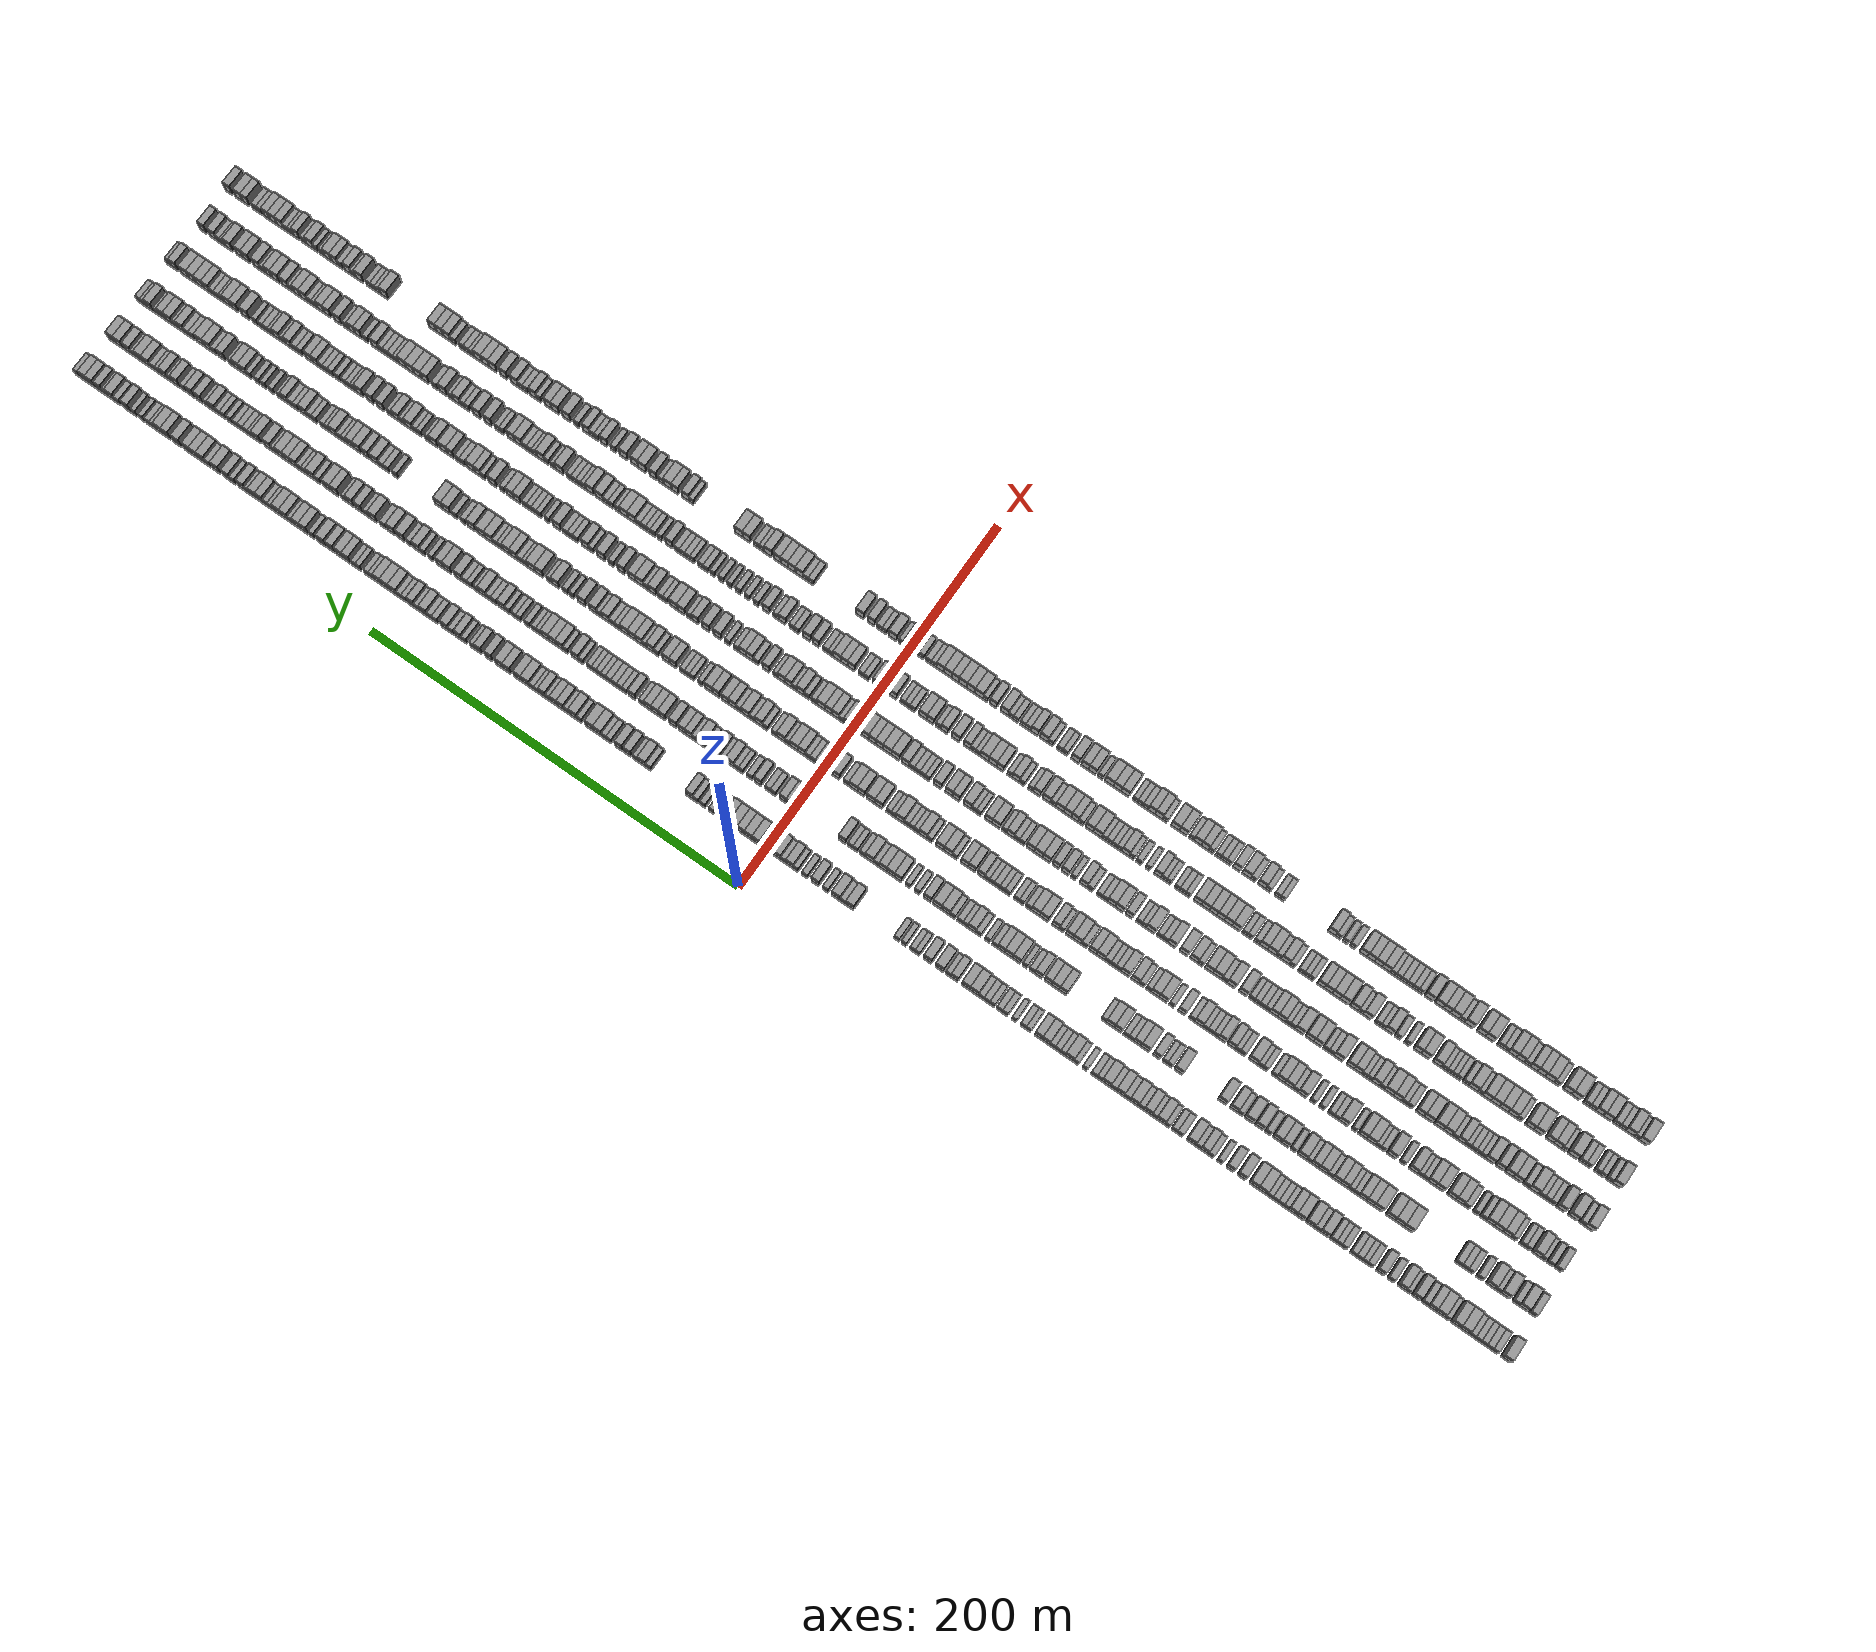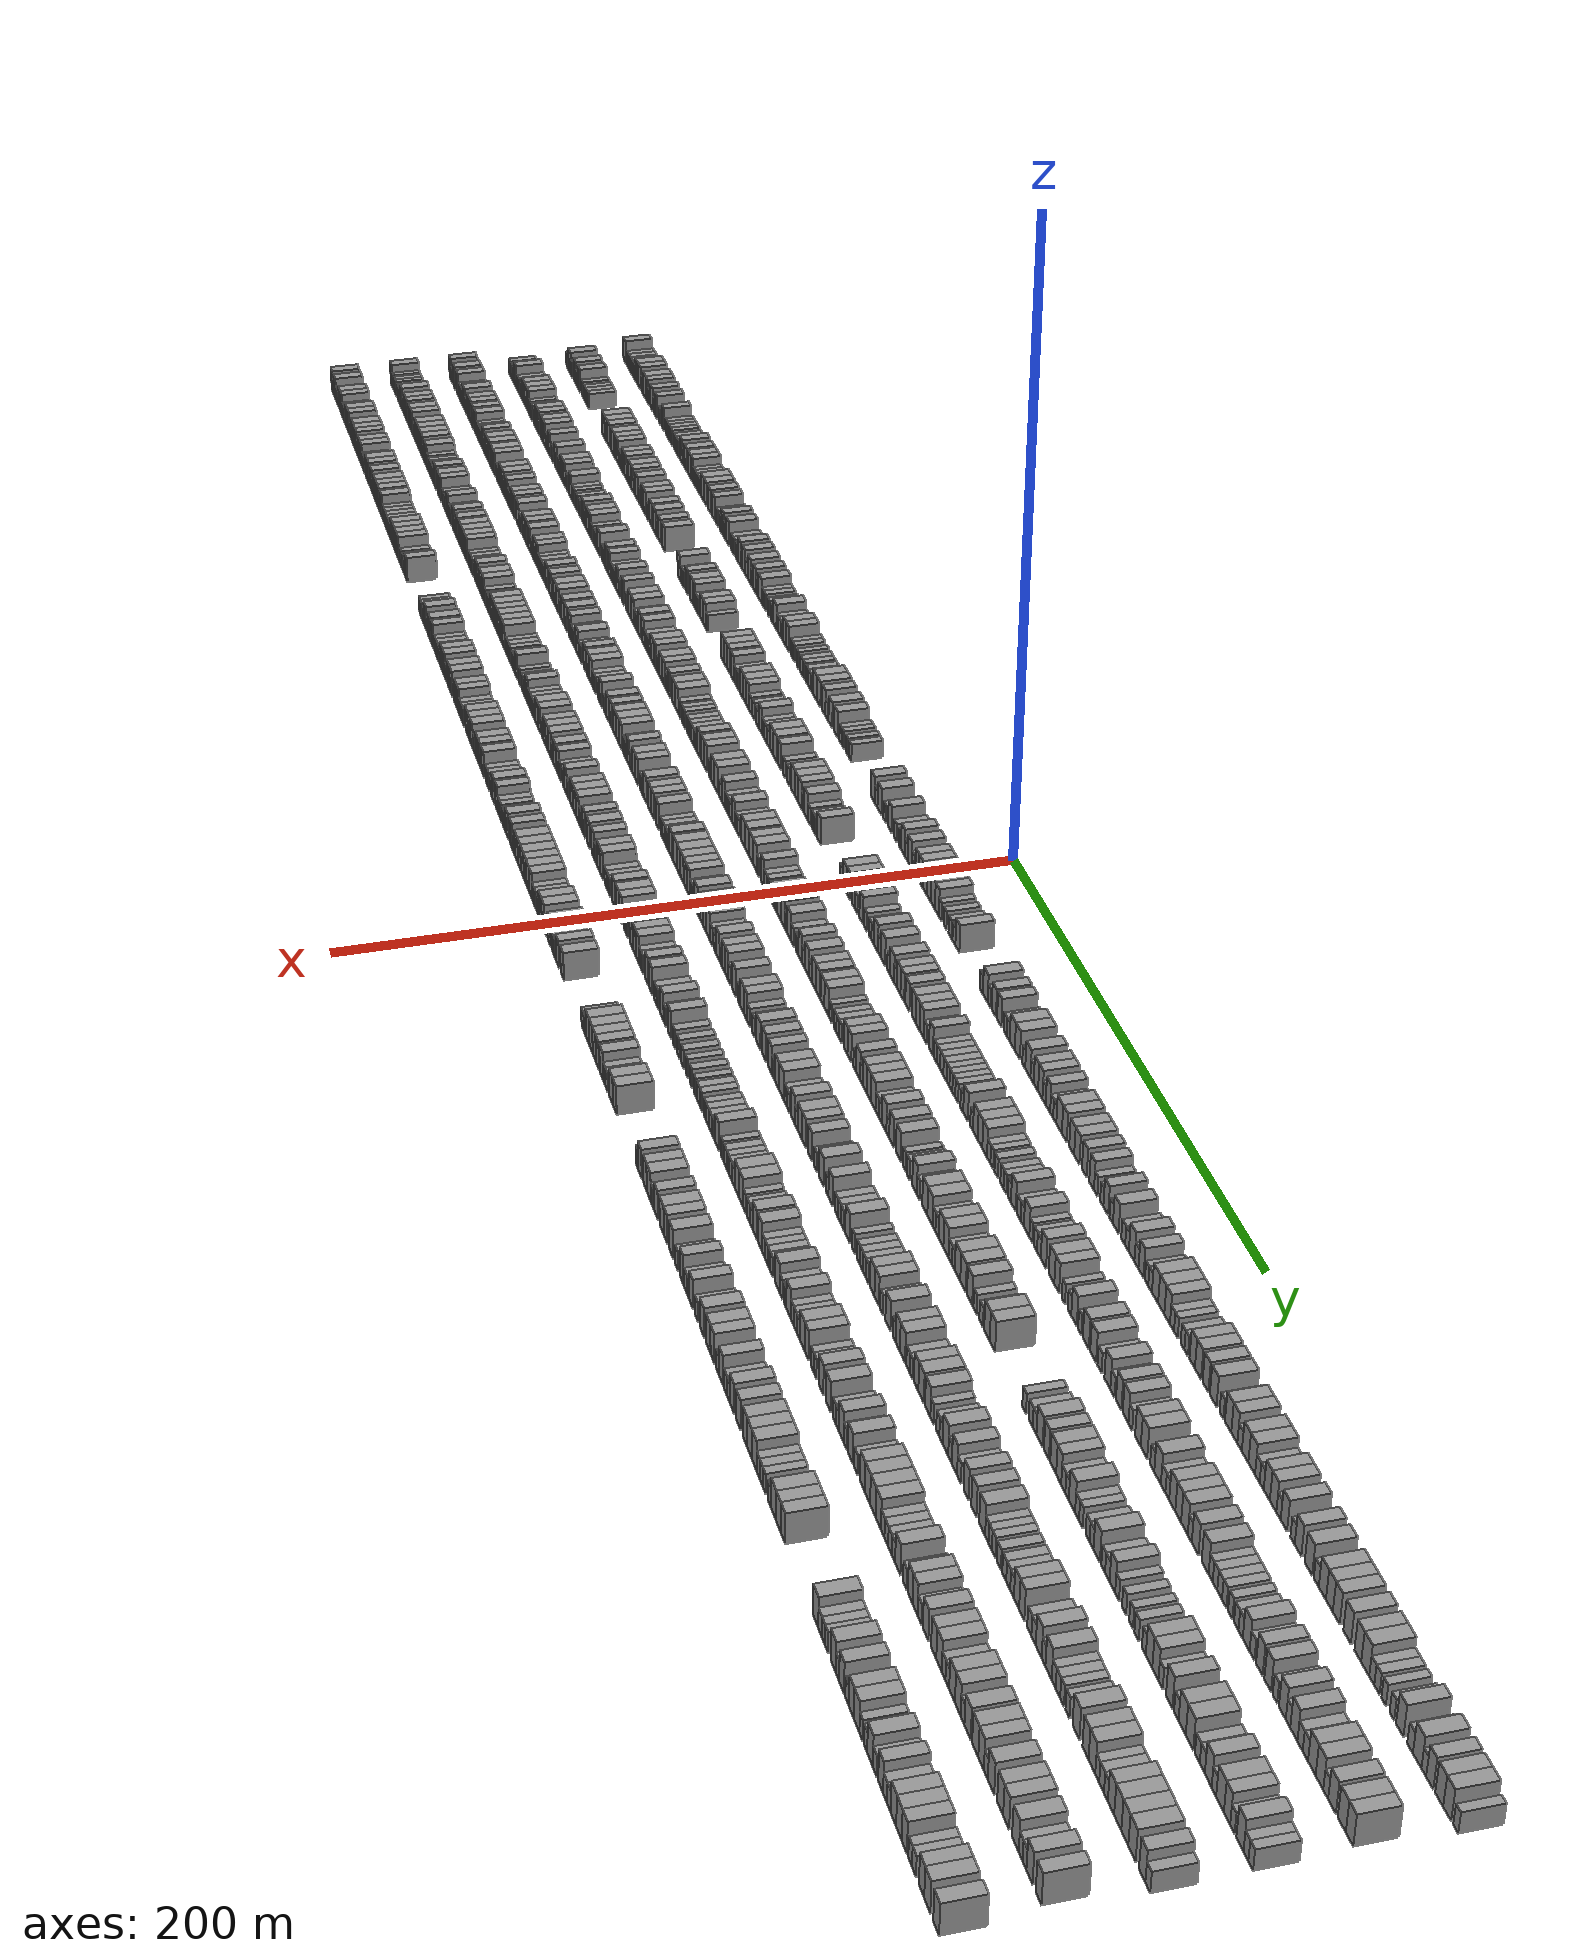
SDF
<sdf version="1.6">
 <world name="default">
  <scene>
   <sky><clouds><speed>12</speed></clouds></sky>
   <ambient>0.4 0.4 0.4 1</ambient>
   <background>0.7 0.7 0.7 1</background>
   <shadows>1</shadows>
  </scene>
  <gravity>0 0 -9.8066</gravity>
  <magnetic_field>6e-06 2.3e-05 -4.2e-05</magnetic_field>
  <physics default="0" name="default_physics" type="ode">
   <ode>
    <solver>
     <type>quick</type>
     <iters>10</iters>
     <sor>1.0</sor>
     <use_dynamic_moi_rescaling>0</use_dynamic_moi_rescaling>
    </solver>
    <constraints>
     <cfm>0</cfm>
     <erp>0.2</erp>
     <contact_max_correcting_vel>100</contact_max_correcting_vel>
     <contact_surface_layer>0.001</contact_surface_layer>
    </constraints>
   </ode>
   <max_step_size>0.004</max_step_size>
   <real_time_factor>1</real_time_factor>
   <real_time_update_rate>250</real_time_update_rate>
  </physics>
  <light name="sun" type="directional">
   <pose>0 0 10 0 0 0</pose>
   <diffuse>0.8 0.8 0.8 1</diffuse>
   <specular>0.2 0.2 0.2 1</specular>
   <attenuation>
    <range>1000</range>
    <constant>0.9</constant>
    <linear>0.01</linear>
    <quadratic>0.001</quadratic>
   </attenuation>
   <direction>-0.5 0.1 -0.9</direction>
  </light>
  <model name="building_1">
   <static>1</static>
   <pose>25.0000 -377.9180 0 0.000000 0.000000 0.000000</pose>
   <link name="link">
    <pose>0 0 4.50 0 0 0</pose>
    <collision name="collision"><geometry><box><size>10.0000 4.1641 9.0000</size></box></geometry></collision>
    <visual name="visual">
     <cast_shadows>0</cast_shadows>
     <geometry><box><size>10.0000 4.1641 9.0000</size></box></geometry>
     <material>
      <script>
       <uri>model://grey_wall/materials/scripts</uri>
       <uri>model://grey_wall/materials/textures</uri>
       <name>vrc/grey_wall</name>
      </script>
     </material>
    </visual>
   </link>
  </model>
  <model name="building_2">
   <static>1</static>
   <pose>25.0000 -372.4403 0 0.000000 0.000000 0.000000</pose>
   <link name="link">
    <pose>0 0 3.00 0 0 0</pose>
    <collision name="collision"><geometry><box><size>10.0000 2.7912 6.0000</size></box></geometry></collision>
    <visual name="visual">
     <cast_shadows>0</cast_shadows>
     <geometry><box><size>10.0000 2.7912 6.0000</size></box></geometry>
     <material>
      <script>
       <uri>model://grey_wall/materials/scripts</uri>
       <uri>model://grey_wall/materials/textures</uri>
       <name>vrc/grey_wall</name>
      </script>
     </material>
    </visual>
   </link>
  </model>
  <model name="building_3">
   <static>1</static>
   <pose>25.0000 -369.5470 0 0.000000 0.000000 0.000000</pose>
   <link name="link">
    <pose>0 0 3.00 0 0 0</pose>
    <collision name="collision"><geometry><box><size>10.0000 2.9956 6.0000</size></box></geometry></collision>
    <visual name="visual">
     <cast_shadows>0</cast_shadows>
     <geometry><box><size>10.0000 2.9956 6.0000</size></box></geometry>
     <material>
      <script>
       <uri>model://grey_wall/materials/scripts</uri>
       <uri>model://grey_wall/materials/textures</uri>
       <name>vrc/grey_wall</name>
      </script>
     </material>
    </visual>
   </link>
  </model>
  <model name="building_4">
   <static>1</static>
   <pose>25.0000 -366.6835 0 0.000000 0.000000 0.000000</pose>
   <link name="link">
    <pose>0 0 3.00 0 0 0</pose>
    <collision name="collision"><geometry><box><size>10.0000 2.7314 6.0000</size></box></geometry></collision>
    <visual name="visual">
     <cast_shadows>0</cast_shadows>
     <geometry><box><size>10.0000 2.7314 6.0000</size></box></geometry>
     <material>
      <script>
       <uri>model://grey_wall/materials/scripts</uri>
       <uri>model://grey_wall/materials/textures</uri>
       <name>vrc/grey_wall</name>
      </script>
     </material>
    </visual>
   </link>
  </model>
  <model name="building_5">
   <static>1</static>
   <pose>25.0000 -363.9292 0 0.000000 0.000000 0.000000</pose>
   <link name="link">
    <pose>0 0 3.00 0 0 0</pose>
    <collision name="collision"><geometry><box><size>10.0000 2.7772 6.0000</size></box></geometry></collision>
    <visual name="visual">
     <cast_shadows>0</cast_shadows>
     <geometry><box><size>10.0000 2.7772 6.0000</size></box></geometry>
     <material>
      <script>
       <uri>model://grey_wall/materials/scripts</uri>
       <uri>model://grey_wall/materials/textures</uri>
       <name>vrc/grey_wall</name>
      </script>
     </material>
    </visual>
   </link>
  </model>
  <model name="building_6">
   <static>1</static>
   <pose>25.0000 -361.0685 0 0.000000 0.000000 0.000000</pose>
   <link name="link">
    <pose>0 0 3.00 0 0 0</pose>
    <collision name="collision"><geometry><box><size>10.0000 2.9442 6.0000</size></box></geometry></collision>
    <visual name="visual">
     <cast_shadows>0</cast_shadows>
     <geometry><box><size>10.0000 2.9442 6.0000</size></box></geometry>
     <material>
      <script>
       <uri>model://grey_wall/materials/scripts</uri>
       <uri>model://grey_wall/materials/textures</uri>
       <name>vrc/grey_wall</name>
      </script>
     </material>
    </visual>
   </link>
  </model>
  <model name="building_7">
   <static>1</static>
   <pose>25.0000 -357.3652 0 0.000000 0.000000 0.000000</pose>
   <link name="link">
    <pose>0 0 4.50 0 0 0</pose>
    <collision name="collision"><geometry><box><size>10.0000 4.4624 9.0000</size></box></geometry></collision>
    <visual name="visual">
     <cast_shadows>0</cast_shadows>
     <geometry><box><size>10.0000 4.4624 9.0000</size></box></geometry>
     <material>
      <script>
       <uri>model://grey_wall/materials/scripts</uri>
       <uri>model://grey_wall/materials/textures</uri>
       <name>vrc/grey_wall</name>
      </script>
     </material>
    </visual>
   </link>
  </model>
  <model name="building_8">
   <static>1</static>
   <pose>25.0000 -353.1340 0 0.000000 0.000000 0.000000</pose>
   <link name="link">
    <pose>0 0 4.50 0 0 0</pose>
    <collision name="collision"><geometry><box><size>10.0000 4.0000 9.0000</size></box></geometry></collision>
    <visual name="visual">
     <cast_shadows>0</cast_shadows>
     <geometry><box><size>10.0000 4.0000 9.0000</size></box></geometry>
     <material>
      <script>
       <uri>model://grey_wall/materials/scripts</uri>
       <uri>model://grey_wall/materials/textures</uri>
       <name>vrc/grey_wall</name>
      </script>
     </material>
    </visual>
   </link>
  </model>
  <model name="building_9">
   <static>1</static>
   <pose>25.0000 -348.8813 0 0.000000 0.000000 0.000000</pose>
   <link name="link">
    <pose>0 0 3.00 0 0 0</pose>
    <collision name="collision"><geometry><box><size>10.0000 2.5055 6.0000</size></box></geometry></collision>
    <visual name="visual">
     <cast_shadows>0</cast_shadows>
     <geometry><box><size>10.0000 2.5055 6.0000</size></box></geometry>
     <material>
      <script>
       <uri>model://grey_wall/materials/scripts</uri>
       <uri>model://grey_wall/materials/textures</uri>
       <name>vrc/grey_wall</name>
      </script>
     </material>
    </visual>
   </link>
  </model>
  <model name="building_10">
   <static>1</static>
   <pose>25.0000 -345.4044 0 0.000000 0.000000 0.000000</pose>
   <link name="link">
    <pose>0 0 4.50 0 0 0</pose>
    <collision name="collision"><geometry><box><size>10.0000 4.4482 9.0000</size></box></geometry></collision>
    <visual name="visual">
     <cast_shadows>0</cast_shadows>
     <geometry><box><size>10.0000 4.4482 9.0000</size></box></geometry>
     <material>
      <script>
       <uri>model://grey_wall/materials/scripts</uri>
       <uri>model://grey_wall/materials/textures</uri>
       <name>vrc/grey_wall</name>
      </script>
     </material>
    </visual>
   </link>
  </model>
  <model name="building_11">
   <static>1</static>
   <pose>25.0000 -341.3734 0 0.000000 0.000000 0.000000</pose>
   <link name="link">
    <pose>0 0 4.50 0 0 0</pose>
    <collision name="collision"><geometry><box><size>10.0000 3.6137 9.0000</size></box></geometry></collision>
    <visual name="visual">
     <cast_shadows>0</cast_shadows>
     <geometry><box><size>10.0000 3.6137 9.0000</size></box></geometry>
     <material>
      <script>
       <uri>model://grey_wall/materials/scripts</uri>
       <uri>model://grey_wall/materials/textures</uri>
       <name>vrc/grey_wall</name>
      </script>
     </material>
    </visual>
   </link>
  </model>
  <model name="building_12">
   <static>1</static>
   <pose>25.0000 -338.1369 0 0.000000 0.000000 0.000000</pose>
   <link name="link">
    <pose>0 0 3.00 0 0 0</pose>
    <collision name="collision"><geometry><box><size>10.0000 2.8593 6.0000</size></box></geometry></collision>
    <visual name="visual">
     <cast_shadows>0</cast_shadows>
     <geometry><box><size>10.0000 2.8593 6.0000</size></box></geometry>
     <material>
      <script>
       <uri>model://grey_wall/materials/scripts</uri>
       <uri>model://grey_wall/materials/textures</uri>
       <name>vrc/grey_wall</name>
      </script>
     </material>
    </visual>
   </link>
  </model>
  <model name="building_13">
   <static>1</static>
   <pose>25.0000 -333.8080 0 0.000000 0.000000 0.000000</pose>
   <link name="link">
    <pose>0 0 4.50 0 0 0</pose>
    <collision name="collision"><geometry><box><size>10.0000 3.7986 9.0000</size></box></geometry></collision>
    <visual name="visual">
     <cast_shadows>0</cast_shadows>
     <geometry><box><size>10.0000 3.7986 9.0000</size></box></geometry>
     <material>
      <script>
       <uri>model://grey_wall/materials/scripts</uri>
       <uri>model://grey_wall/materials/textures</uri>
       <name>vrc/grey_wall</name>
      </script>
     </material>
    </visual>
   </link>
  </model>
  <model name="building_14">
   <static>1</static>
   <pose>25.0000 -329.7077 0 0.000000 0.000000 0.000000</pose>
   <link name="link">
    <pose>0 0 3.00 0 0 0</pose>
    <collision name="collision"><geometry><box><size>10.0000 2.4020 6.0000</size></box></geometry></collision>
    <visual name="visual">
     <cast_shadows>0</cast_shadows>
     <geometry><box><size>10.0000 2.4020 6.0000</size></box></geometry>
     <material>
      <script>
       <uri>model://grey_wall/materials/scripts</uri>
       <uri>model://grey_wall/materials/textures</uri>
       <name>vrc/grey_wall</name>
      </script>
     </material>
    </visual>
   </link>
  </model>
  <model name="building_15">
   <static>1</static>
   <pose>25.0000 -326.6025 0 0.000000 0.000000 0.000000</pose>
   <link name="link">
    <pose>0 0 4.50 0 0 0</pose>
    <collision name="collision"><geometry><box><size>10.0000 3.8086 9.0000</size></box></geometry></collision>
    <visual name="visual">
     <cast_shadows>0</cast_shadows>
     <geometry><box><size>10.0000 3.8086 9.0000</size></box></geometry>
     <material>
      <script>
       <uri>model://grey_wall/materials/scripts</uri>
       <uri>model://grey_wall/materials/textures</uri>
       <name>vrc/grey_wall</name>
      </script>
     </material>
    </visual>
   </link>
  </model>
  <model name="building_16">
   <static>1</static>
   <pose>25.0000 -321.2012 0 0.000000 0.000000 0.000000</pose>
   <link name="link">
    <pose>0 0 3.00 0 0 0</pose>
    <collision name="collision"><geometry><box><size>10.0000 2.9940 6.0000</size></box></geometry></collision>
    <visual name="visual">
     <cast_shadows>0</cast_shadows>
     <geometry><box><size>10.0000 2.9940 6.0000</size></box></geometry>
     <material>
      <script>
       <uri>model://grey_wall/materials/scripts</uri>
       <uri>model://grey_wall/materials/textures</uri>
       <name>vrc/grey_wall</name>
      </script>
     </material>
    </visual>
   </link>
  </model>
  <model name="building_17">
   <static>1</static>
   <pose>25.0000 -315.8958 0 0.000000 0.000000 0.000000</pose>
   <link name="link">
    <pose>0 0 4.50 0 0 0</pose>
    <collision name="collision"><geometry><box><size>10.0000 3.6170 9.0000</size></box></geometry></collision>
    <visual name="visual">
     <cast_shadows>0</cast_shadows>
     <geometry><box><size>10.0000 3.6170 9.0000</size></box></geometry>
     <material>
      <script>
       <uri>model://grey_wall/materials/scripts</uri>
       <uri>model://grey_wall/materials/textures</uri>
       <name>vrc/grey_wall</name>
      </script>
     </material>
    </visual>
   </link>
  </model>
  <model name="building_18">
   <static>1</static>
   <pose>25.0000 -310.6948 0 0.000000 0.000000 0.000000</pose>
   <link name="link">
    <pose>0 0 3.00 0 0 0</pose>
    <collision name="collision"><geometry><box><size>10.0000 2.7850 6.0000</size></box></geometry></collision>
    <visual name="visual">
     <cast_shadows>0</cast_shadows>
     <geometry><box><size>10.0000 2.7850 6.0000</size></box></geometry>
     <material>
      <script>
       <uri>model://grey_wall/materials/scripts</uri>
       <uri>model://grey_wall/materials/textures</uri>
       <name>vrc/grey_wall</name>
      </script>
     </material>
    </visual>
   </link>
  </model>
  <model name="building_19">
   <static>1</static>
   <pose>25.0000 -308.0772 0 0.000000 0.000000 0.000000</pose>
   <link name="link">
    <pose>0 0 3.00 0 0 0</pose>
    <collision name="collision"><geometry><box><size>10.0000 2.4502 6.0000</size></box></geometry></collision>
    <visual name="visual">
     <cast_shadows>0</cast_shadows>
     <geometry><box><size>10.0000 2.4502 6.0000</size></box></geometry>
     <material>
      <script>
       <uri>model://grey_wall/materials/scripts</uri>
       <uri>model://grey_wall/materials/textures</uri>
       <name>vrc/grey_wall</name>
      </script>
     </material>
    </visual>
   </link>
  </model>
  <model name="building_20">
   <static>1</static>
   <pose>25.0000 -305.3926 0 0.000000 0.000000 0.000000</pose>
   <link name="link">
    <pose>0 0 3.00 0 0 0</pose>
    <collision name="collision"><geometry><box><size>10.0000 2.9192 6.0000</size></box></geometry></collision>
    <visual name="visual">
     <cast_shadows>0</cast_shadows>
     <geometry><box><size>10.0000 2.9192 6.0000</size></box></geometry>
     <material>
      <script>
       <uri>model://grey_wall/materials/scripts</uri>
       <uri>model://grey_wall/materials/textures</uri>
       <name>vrc/grey_wall</name>
      </script>
     </material>
    </visual>
   </link>
  </model>
  <model name="building_21">
   <static>1</static>
   <pose>25.0000 -302.5330 0 0.000000 0.000000 0.000000</pose>
   <link name="link">
    <pose>0 0 3.00 0 0 0</pose>
    <collision name="collision"><geometry><box><size>10.0000 2.7999 6.0000</size></box></geometry></collision>
    <visual name="visual">
     <cast_shadows>0</cast_shadows>
     <geometry><box><size>10.0000 2.7999 6.0000</size></box></geometry>
     <material>
      <script>
       <uri>model://grey_wall/materials/scripts</uri>
       <uri>model://grey_wall/materials/textures</uri>
       <name>vrc/grey_wall</name>
      </script>
     </material>
    </visual>
   </link>
  </model>
  <model name="building_22">
   <static>1</static>
   <pose>25.0000 -297.7633 0 0.000000 0.000000 0.000000</pose>
   <link name="link">
    <pose>0 0 3.00 0 0 0</pose>
    <collision name="collision"><geometry><box><size>10.0000 2.7396 6.0000</size></box></geometry></collision>
    <visual name="visual">
     <cast_shadows>0</cast_shadows>
     <geometry><box><size>10.0000 2.7396 6.0000</size></box></geometry>
     <material>
      <script>
       <uri>model://grey_wall/materials/scripts</uri>
       <uri>model://grey_wall/materials/textures</uri>
       <name>vrc/grey_wall</name>
      </script>
     </material>
    </visual>
   </link>
  </model>
  <model name="building_23">
   <static>1</static>
   <pose>25.0000 -295.0949 0 0.000000 0.000000 0.000000</pose>
   <link name="link">
    <pose>0 0 3.00 0 0 0</pose>
    <collision name="collision"><geometry><box><size>10.0000 2.5971 6.0000</size></box></geometry></collision>
    <visual name="visual">
     <cast_shadows>0</cast_shadows>
     <geometry><box><size>10.0000 2.5971 6.0000</size></box></geometry>
     <material>
      <script>
       <uri>model://grey_wall/materials/scripts</uri>
       <uri>model://grey_wall/materials/textures</uri>
       <name>vrc/grey_wall</name>
      </script>
     </material>
    </visual>
   </link>
  </model>
  <model name="building_24">
   <static>1</static>
   <pose>25.0000 -292.4628 0 0.000000 0.000000 0.000000</pose>
   <link name="link">
    <pose>0 0 3.00 0 0 0</pose>
    <collision name="collision"><geometry><box><size>10.0000 2.6672 6.0000</size></box></geometry></collision>
    <visual name="visual">
     <cast_shadows>0</cast_shadows>
     <geometry><box><size>10.0000 2.6672 6.0000</size></box></geometry>
     <material>
      <script>
       <uri>model://grey_wall/materials/scripts</uri>
       <uri>model://grey_wall/materials/textures</uri>
       <name>vrc/grey_wall</name>
      </script>
     </material>
    </visual>
   </link>
  </model>
  <model name="building_25">
   <static>1</static>
   <pose>25.0000 -288.0893 0 0.000000 0.000000 0.000000</pose>
   <link name="link">
    <pose>0 0 4.50 0 0 0</pose>
    <collision name="collision"><geometry><box><size>10.0000 4.0798 9.0000</size></box></geometry></collision>
    <visual name="visual">
     <cast_shadows>0</cast_shadows>
     <geometry><box><size>10.0000 4.0798 9.0000</size></box></geometry>
     <material>
      <script>
       <uri>model://grey_wall/materials/scripts</uri>
       <uri>model://grey_wall/materials/textures</uri>
       <name>vrc/grey_wall</name>
      </script>
     </material>
    </visual>
   </link>
  </model>
  <model name="building_26">
   <static>1</static>
   <pose>25.0000 -284.5569 0 0.000000 0.000000 0.000000</pose>
   <link name="link">
    <pose>0 0 3.00 0 0 0</pose>
    <collision name="collision"><geometry><box><size>10.0000 2.9850 6.0000</size></box></geometry></collision>
    <visual name="visual">
     <cast_shadows>0</cast_shadows>
     <geometry><box><size>10.0000 2.9850 6.0000</size></box></geometry>
     <material>
      <script>
       <uri>model://grey_wall/materials/scripts</uri>
       <uri>model://grey_wall/materials/textures</uri>
       <name>vrc/grey_wall</name>
      </script>
     </material>
    </visual>
   </link>
  </model>
  <model name="building_27">
   <static>1</static>
   <pose>25.0000 -281.0122 0 0.000000 0.000000 0.000000</pose>
   <link name="link">
    <pose>0 0 4.50 0 0 0</pose>
    <collision name="collision"><geometry><box><size>10.0000 4.1042 9.0000</size></box></geometry></collision>
    <visual name="visual">
     <cast_shadows>0</cast_shadows>
     <geometry><box><size>10.0000 4.1042 9.0000</size></box></geometry>
     <material>
      <script>
       <uri>model://grey_wall/materials/scripts</uri>
       <uri>model://grey_wall/materials/textures</uri>
       <name>vrc/grey_wall</name>
      </script>
     </material>
    </visual>
   </link>
  </model>
  <model name="building_28">
   <static>1</static>
   <pose>25.0000 -275.9188 0 0.000000 0.000000 0.000000</pose>
   <link name="link">
    <pose>0 0 4.50 0 0 0</pose>
    <collision name="collision"><geometry><box><size>10.0000 4.0827 9.0000</size></box></geometry></collision>
    <visual name="visual">
     <cast_shadows>0</cast_shadows>
     <geometry><box><size>10.0000 4.0827 9.0000</size></box></geometry>
     <material>
      <script>
       <uri>model://grey_wall/materials/scripts</uri>
       <uri>model://grey_wall/materials/textures</uri>
       <name>vrc/grey_wall</name>
      </script>
     </material>
    </visual>
   </link>
  </model>
  <model name="building_29">
   <static>1</static>
   <pose>25.0000 -272.0114 0 0.000000 0.000000 0.000000</pose>
   <link name="link">
    <pose>0 0 4.50 0 0 0</pose>
    <collision name="collision"><geometry><box><size>10.0000 3.7321 9.0000</size></box></geometry></collision>
    <visual name="visual">
     <cast_shadows>0</cast_shadows>
     <geometry><box><size>10.0000 3.7321 9.0000</size></box></geometry>
     <material>
      <script>
       <uri>model://grey_wall/materials/scripts</uri>
       <uri>model://grey_wall/materials/textures</uri>
       <name>vrc/grey_wall</name>
      </script>
     </material>
    </visual>
   </link>
  </model>
  <model name="building_30">
   <static>1</static>
   <pose>25.0000 -268.9045 0 0.000000 0.000000 0.000000</pose>
   <link name="link">
    <pose>0 0 3.00 0 0 0</pose>
    <collision name="collision"><geometry><box><size>10.0000 2.4816 6.0000</size></box></geometry></collision>
    <visual name="visual">
     <cast_shadows>0</cast_shadows>
     <geometry><box><size>10.0000 2.4816 6.0000</size></box></geometry>
     <material>
      <script>
       <uri>model://grey_wall/materials/scripts</uri>
       <uri>model://grey_wall/materials/textures</uri>
       <name>vrc/grey_wall</name>
      </script>
     </material>
    </visual>
   </link>
  </model>
  <model name="building_31">
   <static>1</static>
   <pose>25.0000 -266.2065 0 0.000000 0.000000 0.000000</pose>
   <link name="link">
    <pose>0 0 3.00 0 0 0</pose>
    <collision name="collision"><geometry><box><size>10.0000 2.9144 6.0000</size></box></geometry></collision>
    <visual name="visual">
     <cast_shadows>0</cast_shadows>
     <geometry><box><size>10.0000 2.9144 6.0000</size></box></geometry>
     <material>
      <script>
       <uri>model://grey_wall/materials/scripts</uri>
       <uri>model://grey_wall/materials/textures</uri>
       <name>vrc/grey_wall</name>
      </script>
     </material>
    </visual>
   </link>
  </model>
  <model name="building_32">
   <static>1</static>
   <pose>25.0000 -263.3191 0 0.000000 0.000000 0.000000</pose>
   <link name="link">
    <pose>0 0 3.00 0 0 0</pose>
    <collision name="collision"><geometry><box><size>10.0000 2.8604 6.0000</size></box></geometry></collision>
    <visual name="visual">
     <cast_shadows>0</cast_shadows>
     <geometry><box><size>10.0000 2.8604 6.0000</size></box></geometry>
     <material>
      <script>
       <uri>model://grey_wall/materials/scripts</uri>
       <uri>model://grey_wall/materials/textures</uri>
       <name>vrc/grey_wall</name>
      </script>
     </material>
    </visual>
   </link>
  </model>
  <model name="building_33">
   <static>1</static>
   <pose>25.0000 -260.5628 0 0.000000 0.000000 0.000000</pose>
   <link name="link">
    <pose>0 0 3.00 0 0 0</pose>
    <collision name="collision"><geometry><box><size>10.0000 2.6522 6.0000</size></box></geometry></collision>
    <visual name="visual">
     <cast_shadows>0</cast_shadows>
     <geometry><box><size>10.0000 2.6522 6.0000</size></box></geometry>
     <material>
      <script>
       <uri>model://grey_wall/materials/scripts</uri>
       <uri>model://grey_wall/materials/textures</uri>
       <name>vrc/grey_wall</name>
      </script>
     </material>
    </visual>
   </link>
  </model>
  <model name="building_34">
   <static>1</static>
   <pose>25.0000 -256.9874 0 0.000000 0.000000 0.000000</pose>
   <link name="link">
    <pose>0 0 4.50 0 0 0</pose>
    <collision name="collision"><geometry><box><size>10.0000 4.4985 9.0000</size></box></geometry></collision>
    <visual name="visual">
     <cast_shadows>0</cast_shadows>
     <geometry><box><size>10.0000 4.4985 9.0000</size></box></geometry>
     <material>
      <script>
       <uri>model://grey_wall/materials/scripts</uri>
       <uri>model://grey_wall/materials/textures</uri>
       <name>vrc/grey_wall</name>
      </script>
     </material>
    </visual>
   </link>
  </model>
  <model name="building_35">
   <static>1</static>
   <pose>25.0000 -252.6322 0 0.000000 0.000000 0.000000</pose>
   <link name="link">
    <pose>0 0 4.50 0 0 0</pose>
    <collision name="collision"><geometry><box><size>10.0000 4.2119 9.0000</size></box></geometry></collision>
    <visual name="visual">
     <cast_shadows>0</cast_shadows>
     <geometry><box><size>10.0000 4.2119 9.0000</size></box></geometry>
     <material>
      <script>
       <uri>model://grey_wall/materials/scripts</uri>
       <uri>model://grey_wall/materials/textures</uri>
       <name>vrc/grey_wall</name>
      </script>
     </material>
    </visual>
   </link>
  </model>
  <model name="building_36">
   <static>1</static>
   <pose>25.0000 -246.5540 0 0.000000 0.000000 0.000000</pose>
   <link name="link">
    <pose>0 0 4.50 0 0 0</pose>
    <collision name="collision"><geometry><box><size>10.0000 3.9444 9.0000</size></box></geometry></collision>
    <visual name="visual">
     <cast_shadows>0</cast_shadows>
     <geometry><box><size>10.0000 3.9444 9.0000</size></box></geometry>
     <material>
      <script>
       <uri>model://grey_wall/materials/scripts</uri>
       <uri>model://grey_wall/materials/textures</uri>
       <name>vrc/grey_wall</name>
      </script>
     </material>
    </visual>
   </link>
  </model>
  <model name="building_37">
   <static>1</static>
   <pose>25.0000 -240.7540 0 0.000000 0.000000 0.000000</pose>
   <link name="link">
    <pose>0 0 4.50 0 0 0</pose>
    <collision name="collision"><geometry><box><size>10.0000 3.6558 9.0000</size></box></geometry></collision>
    <visual name="visual">
     <cast_shadows>0</cast_shadows>
     <geometry><box><size>10.0000 3.6558 9.0000</size></box></geometry>
     <material>
      <script>
       <uri>model://grey_wall/materials/scripts</uri>
       <uri>model://grey_wall/materials/textures</uri>
       <name>vrc/grey_wall</name>
      </script>
     </material>
    </visual>
   </link>
  </model>
  <model name="building_38">
   <static>1</static>
   <pose>25.0000 -235.6396 0 0.000000 0.000000 0.000000</pose>
   <link name="link">
    <pose>0 0 3.00 0 0 0</pose>
    <collision name="collision"><geometry><box><size>10.0000 2.5730 6.0000</size></box></geometry></collision>
    <visual name="visual">
     <cast_shadows>0</cast_shadows>
     <geometry><box><size>10.0000 2.5730 6.0000</size></box></geometry>
     <material>
      <script>
       <uri>model://grey_wall/materials/scripts</uri>
       <uri>model://grey_wall/materials/textures</uri>
       <name>vrc/grey_wall</name>
      </script>
     </material>
    </visual>
   </link>
  </model>
  <model name="building_39">
   <static>1</static>
   <pose>25.0000 -230.9907 0 0.000000 0.000000 0.000000</pose>
   <link name="link">
    <pose>0 0 3.00 0 0 0</pose>
    <collision name="collision"><geometry><box><size>10.0000 2.7248 6.0000</size></box></geometry></collision>
    <visual name="visual">
     <cast_shadows>0</cast_shadows>
     <geometry><box><size>10.0000 2.7248 6.0000</size></box></geometry>
     <material>
      <script>
       <uri>model://grey_wall/materials/scripts</uri>
       <uri>model://grey_wall/materials/textures</uri>
       <name>vrc/grey_wall</name>
      </script>
     </material>
    </visual>
   </link>
  </model>
  <model name="building_40">
   <static>1</static>
   <pose>25.0000 -227.7550 0 0.000000 0.000000 0.000000</pose>
   <link name="link">
    <pose>0 0 4.50 0 0 0</pose>
    <collision name="collision"><geometry><box><size>10.0000 3.7465 9.0000</size></box></geometry></collision>
    <visual name="visual">
     <cast_shadows>0</cast_shadows>
     <geometry><box><size>10.0000 3.7465 9.0000</size></box></geometry>
     <material>
      <script>
       <uri>model://grey_wall/materials/scripts</uri>
       <uri>model://grey_wall/materials/textures</uri>
       <name>vrc/grey_wall</name>
      </script>
     </material>
    </visual>
   </link>
  </model>
  <model name="building_41">
   <static>1</static>
   <pose>25.0000 -224.5326 0 0.000000 0.000000 0.000000</pose>
   <link name="link">
    <pose>0 0 3.00 0 0 0</pose>
    <collision name="collision"><geometry><box><size>10.0000 2.6983 6.0000</size></box></geometry></collision>
    <visual name="visual">
     <cast_shadows>0</cast_shadows>
     <geometry><box><size>10.0000 2.6983 6.0000</size></box></geometry>
     <material>
      <script>
       <uri>model://grey_wall/materials/scripts</uri>
       <uri>model://grey_wall/materials/textures</uri>
       <name>vrc/grey_wall</name>
      </script>
     </material>
    </visual>
   </link>
  </model>
  <model name="building_42">
   <static>1</static>
   <pose>25.0000 -221.0096 0 0.000000 0.000000 0.000000</pose>
   <link name="link">
    <pose>0 0 4.50 0 0 0</pose>
    <collision name="collision"><geometry><box><size>10.0000 4.3477 9.0000</size></box></geometry></collision>
    <visual name="visual">
     <cast_shadows>0</cast_shadows>
     <geometry><box><size>10.0000 4.3477 9.0000</size></box></geometry>
     <material>
      <script>
       <uri>model://grey_wall/materials/scripts</uri>
       <uri>model://grey_wall/materials/textures</uri>
       <name>vrc/grey_wall</name>
      </script>
     </material>
    </visual>
   </link>
  </model>
  <model name="building_43">
   <static>1</static>
   <pose>25.0000 -215.3439 0 0.000000 0.000000 0.000000</pose>
   <link name="link">
    <pose>0 0 3.00 0 0 0</pose>
    <collision name="collision"><geometry><box><size>10.0000 2.9838 6.0000</size></box></geometry></collision>
    <visual name="visual">
     <cast_shadows>0</cast_shadows>
     <geometry><box><size>10.0000 2.9838 6.0000</size></box></geometry>
     <material>
      <script>
       <uri>model://grey_wall/materials/scripts</uri>
       <uri>model://grey_wall/materials/textures</uri>
       <name>vrc/grey_wall</name>
      </script>
     </material>
    </visual>
   </link>
  </model>
  <model name="building_44">
   <static>1</static>
   <pose>25.0000 -212.4890 0 0.000000 0.000000 0.000000</pose>
   <link name="link">
    <pose>0 0 3.00 0 0 0</pose>
    <collision name="collision"><geometry><box><size>10.0000 2.7260 6.0000</size></box></geometry></collision>
    <visual name="visual">
     <cast_shadows>0</cast_shadows>
     <geometry><box><size>10.0000 2.7260 6.0000</size></box></geometry>
     <material>
      <script>
       <uri>model://grey_wall/materials/scripts</uri>
       <uri>model://grey_wall/materials/textures</uri>
       <name>vrc/grey_wall</name>
      </script>
     </material>
    </visual>
   </link>
  </model>
  <model name="building_45">
   <static>1</static>
   <pose>25.0000 -208.8922 0 0.000000 0.000000 0.000000</pose>
   <link name="link">
    <pose>0 0 3.00 0 0 0</pose>
    <collision name="collision"><geometry><box><size>10.0000 2.4675 6.0000</size></box></geometry></collision>
    <visual name="visual">
     <cast_shadows>0</cast_shadows>
     <geometry><box><size>10.0000 2.4675 6.0000</size></box></geometry>
     <material>
      <script>
       <uri>model://grey_wall/materials/scripts</uri>
       <uri>model://grey_wall/materials/textures</uri>
       <name>vrc/grey_wall</name>
      </script>
     </material>
    </visual>
   </link>
  </model>
  <model name="building_46">
   <static>1</static>
   <pose>25.0000 -205.5617 0 0.000000 0.000000 0.000000</pose>
   <link name="link">
    <pose>0 0 4.50 0 0 0</pose>
    <collision name="collision"><geometry><box><size>10.0000 4.1934 9.0000</size></box></geometry></collision>
    <visual name="visual">
     <cast_shadows>0</cast_shadows>
     <geometry><box><size>10.0000 4.1934 9.0000</size></box></geometry>
     <material>
      <script>
       <uri>model://grey_wall/materials/scripts</uri>
       <uri>model://grey_wall/materials/textures</uri>
       <name>vrc/grey_wall</name>
      </script>
     </material>
    </visual>
   </link>
  </model>
  <model name="building_47">
   <static>1</static>
   <pose>25.0000 -202.2358 0 0.000000 0.000000 0.000000</pose>
   <link name="link">
    <pose>0 0 3.00 0 0 0</pose>
    <collision name="collision"><geometry><box><size>10.0000 2.4584 6.0000</size></box></geometry></collision>
    <visual name="visual">
     <cast_shadows>0</cast_shadows>
     <geometry><box><size>10.0000 2.4584 6.0000</size></box></geometry>
     <material>
      <script>
       <uri>model://grey_wall/materials/scripts</uri>
       <uri>model://grey_wall/materials/textures</uri>
       <name>vrc/grey_wall</name>
      </script>
     </material>
    </visual>
   </link>
  </model>
  <model name="building_48">
   <static>1</static>
   <pose>25.0000 -198.9957 0 0.000000 0.000000 0.000000</pose>
   <link name="link">
    <pose>0 0 4.50 0 0 0</pose>
    <collision name="collision"><geometry><box><size>10.0000 4.0219 9.0000</size></box></geometry></collision>
    <visual name="visual">
     <cast_shadows>0</cast_shadows>
     <geometry><box><size>10.0000 4.0219 9.0000</size></box></geometry>
     <material>
      <script>
       <uri>model://grey_wall/materials/scripts</uri>
       <uri>model://grey_wall/materials/textures</uri>
       <name>vrc/grey_wall</name>
      </script>
     </material>
    </visual>
   </link>
  </model>
  <model name="building_49">
   <static>1</static>
   <pose>25.0000 -195.5774 0 0.000000 0.000000 0.000000</pose>
   <link name="link">
    <pose>0 0 3.00 0 0 0</pose>
    <collision name="collision"><geometry><box><size>10.0000 2.8146 6.0000</size></box></geometry></collision>
    <visual name="visual">
     <cast_shadows>0</cast_shadows>
     <geometry><box><size>10.0000 2.8146 6.0000</size></box></geometry>
     <material>
      <script>
       <uri>model://grey_wall/materials/scripts</uri>
       <uri>model://grey_wall/materials/textures</uri>
       <name>vrc/grey_wall</name>
      </script>
     </material>
    </visual>
   </link>
  </model>
  <model name="building_50">
   <static>1</static>
   <pose>25.0000 -191.9645 0 0.000000 0.000000 0.000000</pose>
   <link name="link">
    <pose>0 0 4.50 0 0 0</pose>
    <collision name="collision"><geometry><box><size>10.0000 4.4112 9.0000</size></box></geometry></collision>
    <visual name="visual">
     <cast_shadows>0</cast_shadows>
     <geometry><box><size>10.0000 4.4112 9.0000</size></box></geometry>
     <material>
      <script>
       <uri>model://grey_wall/materials/scripts</uri>
       <uri>model://grey_wall/materials/textures</uri>
       <name>vrc/grey_wall</name>
      </script>
     </material>
    </visual>
   </link>
  </model>
  <model name="building_51">
   <static>1</static>
   <pose>25.0000 -188.2748 0 0.000000 0.000000 0.000000</pose>
   <link name="link">
    <pose>0 0 3.00 0 0 0</pose>
    <collision name="collision"><geometry><box><size>10.0000 2.9683 6.0000</size></box></geometry></collision>
    <visual name="visual">
     <cast_shadows>0</cast_shadows>
     <geometry><box><size>10.0000 2.9683 6.0000</size></box></geometry>
     <material>
      <script>
       <uri>model://grey_wall/materials/scripts</uri>
       <uri>model://grey_wall/materials/textures</uri>
       <name>vrc/grey_wall</name>
      </script>
     </material>
    </visual>
   </link>
  </model>
  <model name="building_52">
   <static>1</static>
   <pose>25.0000 -184.7774 0 0.000000 0.000000 0.000000</pose>
   <link name="link">
    <pose>0 0 4.50 0 0 0</pose>
    <collision name="collision"><geometry><box><size>10.0000 4.0264 9.0000</size></box></geometry></collision>
    <visual name="visual">
     <cast_shadows>0</cast_shadows>
     <geometry><box><size>10.0000 4.0264 9.0000</size></box></geometry>
     <material>
      <script>
       <uri>model://grey_wall/materials/scripts</uri>
       <uri>model://grey_wall/materials/textures</uri>
       <name>vrc/grey_wall</name>
      </script>
     </material>
    </visual>
   </link>
  </model>
  <model name="building_53">
   <static>1</static>
   <pose>25.0000 -181.3455 0 0.000000 0.000000 0.000000</pose>
   <link name="link">
    <pose>0 0 3.00 0 0 0</pose>
    <collision name="collision"><geometry><box><size>10.0000 2.8375 6.0000</size></box></geometry></collision>
    <visual name="visual">
     <cast_shadows>0</cast_shadows>
     <geometry><box><size>10.0000 2.8375 6.0000</size></box></geometry>
     <material>
      <script>
       <uri>model://grey_wall/materials/scripts</uri>
       <uri>model://grey_wall/materials/textures</uri>
       <name>vrc/grey_wall</name>
      </script>
     </material>
    </visual>
   </link>
  </model>
  <model name="building_54">
   <static>1</static>
   <pose>25.0000 -177.7456 0 0.000000 0.000000 0.000000</pose>
   <link name="link">
    <pose>0 0 4.50 0 0 0</pose>
    <collision name="collision"><geometry><box><size>10.0000 4.3623 9.0000</size></box></geometry></collision>
    <visual name="visual">
     <cast_shadows>0</cast_shadows>
     <geometry><box><size>10.0000 4.3623 9.0000</size></box></geometry>
     <material>
      <script>
       <uri>model://grey_wall/materials/scripts</uri>
       <uri>model://grey_wall/materials/textures</uri>
       <name>vrc/grey_wall</name>
      </script>
     </material>
    </visual>
   </link>
  </model>
  <model name="building_55">
   <static>1</static>
   <pose>25.0000 -174.2696 0 0.000000 0.000000 0.000000</pose>
   <link name="link">
    <pose>0 0 3.00 0 0 0</pose>
    <collision name="collision"><geometry><box><size>10.0000 2.5898 6.0000</size></box></geometry></collision>
    <visual name="visual">
     <cast_shadows>0</cast_shadows>
     <geometry><box><size>10.0000 2.5898 6.0000</size></box></geometry>
     <material>
      <script>
       <uri>model://grey_wall/materials/scripts</uri>
       <uri>model://grey_wall/materials/textures</uri>
       <name>vrc/grey_wall</name>
      </script>
     </material>
    </visual>
   </link>
  </model>
  <model name="building_56">
   <static>1</static>
   <pose>25.0000 -171.4999 0 0.000000 0.000000 0.000000</pose>
   <link name="link">
    <pose>0 0 3.00 0 0 0</pose>
    <collision name="collision"><geometry><box><size>10.0000 2.9495 6.0000</size></box></geometry></collision>
    <visual name="visual">
     <cast_shadows>0</cast_shadows>
     <geometry><box><size>10.0000 2.9495 6.0000</size></box></geometry>
     <material>
      <script>
       <uri>model://grey_wall/materials/scripts</uri>
       <uri>model://grey_wall/materials/textures</uri>
       <name>vrc/grey_wall</name>
      </script>
     </material>
    </visual>
   </link>
  </model>
  <model name="building_57">
   <static>1</static>
   <pose>25.0000 -166.7829 0 0.000000 0.000000 0.000000</pose>
   <link name="link">
    <pose>0 0 3.00 0 0 0</pose>
    <collision name="collision"><geometry><box><size>10.0000 2.4845 6.0000</size></box></geometry></collision>
    <visual name="visual">
     <cast_shadows>0</cast_shadows>
     <geometry><box><size>10.0000 2.4845 6.0000</size></box></geometry>
     <material>
      <script>
       <uri>model://grey_wall/materials/scripts</uri>
       <uri>model://grey_wall/materials/textures</uri>
       <name>vrc/grey_wall</name>
      </script>
     </material>
    </visual>
   </link>
  </model>
  <model name="building_58">
   <static>1</static>
   <pose>25.0000 -162.3338 0 0.000000 0.000000 0.000000</pose>
   <link name="link">
    <pose>0 0 3.00 0 0 0</pose>
    <collision name="collision"><geometry><box><size>10.0000 2.4136 6.0000</size></box></geometry></collision>
    <visual name="visual">
     <cast_shadows>0</cast_shadows>
     <geometry><box><size>10.0000 2.4136 6.0000</size></box></geometry>
     <material>
      <script>
       <uri>model://grey_wall/materials/scripts</uri>
       <uri>model://grey_wall/materials/textures</uri>
       <name>vrc/grey_wall</name>
      </script>
     </material>
    </visual>
   </link>
  </model>
  <model name="building_59">
   <static>1</static>
   <pose>25.0000 -158.9066 0 0.000000 0.000000 0.000000</pose>
   <link name="link">
    <pose>0 0 4.50 0 0 0</pose>
    <collision name="collision"><geometry><box><size>10.0000 4.4409 9.0000</size></box></geometry></collision>
    <visual name="visual">
     <cast_shadows>0</cast_shadows>
     <geometry><box><size>10.0000 4.4409 9.0000</size></box></geometry>
     <material>
      <script>
       <uri>model://grey_wall/materials/scripts</uri>
       <uri>model://grey_wall/materials/textures</uri>
       <name>vrc/grey_wall</name>
      </script>
     </material>
    </visual>
   </link>
  </model>
  <model name="building_60">
   <static>1</static>
   <pose>25.0000 -155.4463 0 0.000000 0.000000 0.000000</pose>
   <link name="link">
    <pose>0 0 3.00 0 0 0</pose>
    <collision name="collision"><geometry><box><size>10.0000 2.4797 6.0000</size></box></geometry></collision>
    <visual name="visual">
     <cast_shadows>0</cast_shadows>
     <geometry><box><size>10.0000 2.4797 6.0000</size></box></geometry>
     <material>
      <script>
       <uri>model://grey_wall/materials/scripts</uri>
       <uri>model://grey_wall/materials/textures</uri>
       <name>vrc/grey_wall</name>
      </script>
     </material>
    </visual>
   </link>
  </model>
  <model name="building_61">
   <static>1</static>
   <pose>25.0000 -152.7761 0 0.000000 0.000000 0.000000</pose>
   <link name="link">
    <pose>0 0 3.00 0 0 0</pose>
    <collision name="collision"><geometry><box><size>10.0000 2.8606 6.0000</size></box></geometry></collision>
    <visual name="visual">
     <cast_shadows>0</cast_shadows>
     <geometry><box><size>10.0000 2.8606 6.0000</size></box></geometry>
     <material>
      <script>
       <uri>model://grey_wall/materials/scripts</uri>
       <uri>model://grey_wall/materials/textures</uri>
       <name>vrc/grey_wall</name>
      </script>
     </material>
    </visual>
   </link>
  </model>
  <model name="building_62">
   <static>1</static>
   <pose>25.0000 -150.0141 0 0.000000 0.000000 0.000000</pose>
   <link name="link">
    <pose>0 0 3.00 0 0 0</pose>
    <collision name="collision"><geometry><box><size>10.0000 2.6635 6.0000</size></box></geometry></collision>
    <visual name="visual">
     <cast_shadows>0</cast_shadows>
     <geometry><box><size>10.0000 2.6635 6.0000</size></box></geometry>
     <material>
      <script>
       <uri>model://grey_wall/materials/scripts</uri>
       <uri>model://grey_wall/materials/textures</uri>
       <name>vrc/grey_wall</name>
      </script>
     </material>
    </visual>
   </link>
  </model>
  <model name="building_63">
   <static>1</static>
   <pose>25.0000 -146.7242 0 0.000000 0.000000 0.000000</pose>
   <link name="link">
    <pose>0 0 4.50 0 0 0</pose>
    <collision name="collision"><geometry><box><size>10.0000 3.9162 9.0000</size></box></geometry></collision>
    <visual name="visual">
     <cast_shadows>0</cast_shadows>
     <geometry><box><size>10.0000 3.9162 9.0000</size></box></geometry>
     <material>
      <script>
       <uri>model://grey_wall/materials/scripts</uri>
       <uri>model://grey_wall/materials/textures</uri>
       <name>vrc/grey_wall</name>
      </script>
     </material>
    </visual>
   </link>
  </model>
  <model name="building_64">
   <static>1</static>
   <pose>25.0000 -142.8677 0 0.000000 0.000000 0.000000</pose>
   <link name="link">
    <pose>0 0 4.50 0 0 0</pose>
    <collision name="collision"><geometry><box><size>10.0000 3.7969 9.0000</size></box></geometry></collision>
    <visual name="visual">
     <cast_shadows>0</cast_shadows>
     <geometry><box><size>10.0000 3.7969 9.0000</size></box></geometry>
     <material>
      <script>
       <uri>model://grey_wall/materials/scripts</uri>
       <uri>model://grey_wall/materials/textures</uri>
       <name>vrc/grey_wall</name>
      </script>
     </material>
    </visual>
   </link>
  </model>
  <model name="building_65">
   <static>1</static>
   <pose>25.0000 -137.7147 0 0.000000 0.000000 0.000000</pose>
   <link name="link">
    <pose>0 0 3.00 0 0 0</pose>
    <collision name="collision"><geometry><box><size>10.0000 2.5091 6.0000</size></box></geometry></collision>
    <visual name="visual">
     <cast_shadows>0</cast_shadows>
     <geometry><box><size>10.0000 2.5091 6.0000</size></box></geometry>
     <material>
      <script>
       <uri>model://grey_wall/materials/scripts</uri>
       <uri>model://grey_wall/materials/textures</uri>
       <name>vrc/grey_wall</name>
      </script>
     </material>
    </visual>
   </link>
  </model>
  <model name="building_66">
   <static>1</static>
   <pose>25.0000 -135.0044 0 0.000000 0.000000 0.000000</pose>
   <link name="link">
    <pose>0 0 3.00 0 0 0</pose>
    <collision name="collision"><geometry><box><size>10.0000 2.9115 6.0000</size></box></geometry></collision>
    <visual name="visual">
     <cast_shadows>0</cast_shadows>
     <geometry><box><size>10.0000 2.9115 6.0000</size></box></geometry>
     <material>
      <script>
       <uri>model://grey_wall/materials/scripts</uri>
       <uri>model://grey_wall/materials/textures</uri>
       <name>vrc/grey_wall</name>
      </script>
     </material>
    </visual>
   </link>
  </model>
  <model name="building_67">
   <static>1</static>
   <pose>25.0000 -130.3098 0 0.000000 0.000000 0.000000</pose>
   <link name="link">
    <pose>0 0 3.00 0 0 0</pose>
    <collision name="collision"><geometry><box><size>10.0000 2.4779 6.0000</size></box></geometry></collision>
    <visual name="visual">
     <cast_shadows>0</cast_shadows>
     <geometry><box><size>10.0000 2.4779 6.0000</size></box></geometry>
     <material>
      <script>
       <uri>model://grey_wall/materials/scripts</uri>
       <uri>model://grey_wall/materials/textures</uri>
       <name>vrc/grey_wall</name>
      </script>
     </material>
    </visual>
   </link>
  </model>
  <model name="building_68">
   <static>1</static>
   <pose>25.0000 -125.6321 0 0.000000 0.000000 0.000000</pose>
   <link name="link">
    <pose>0 0 3.00 0 0 0</pose>
    <collision name="collision"><geometry><box><size>10.0000 2.8775 6.0000</size></box></geometry></collision>
    <visual name="visual">
     <cast_shadows>0</cast_shadows>
     <geometry><box><size>10.0000 2.8775 6.0000</size></box></geometry>
     <material>
      <script>
       <uri>model://grey_wall/materials/scripts</uri>
       <uri>model://grey_wall/materials/textures</uri>
       <name>vrc/grey_wall</name>
      </script>
     </material>
    </visual>
   </link>
  </model>
  <model name="building_69">
   <static>1</static>
   <pose>25.0000 -122.7486 0 0.000000 0.000000 0.000000</pose>
   <link name="link">
    <pose>0 0 3.00 0 0 0</pose>
    <collision name="collision"><geometry><box><size>10.0000 2.8895 6.0000</size></box></geometry></collision>
    <visual name="visual">
     <cast_shadows>0</cast_shadows>
     <geometry><box><size>10.0000 2.8895 6.0000</size></box></geometry>
     <material>
      <script>
       <uri>model://grey_wall/materials/scripts</uri>
       <uri>model://grey_wall/materials/textures</uri>
       <name>vrc/grey_wall</name>
      </script>
     </material>
    </visual>
   </link>
  </model>
  <model name="building_70">
   <static>1</static>
   <pose>25.0000 -118.9304 0 0.000000 0.000000 0.000000</pose>
   <link name="link">
    <pose>0 0 3.00 0 0 0</pose>
    <collision name="collision"><geometry><box><size>10.0000 2.7469 6.0000</size></box></geometry></collision>
    <visual name="visual">
     <cast_shadows>0</cast_shadows>
     <geometry><box><size>10.0000 2.7469 6.0000</size></box></geometry>
     <material>
      <script>
       <uri>model://grey_wall/materials/scripts</uri>
       <uri>model://grey_wall/materials/textures</uri>
       <name>vrc/grey_wall</name>
      </script>
     </material>
    </visual>
   </link>
  </model>
  <model name="building_71">
   <static>1</static>
   <pose>25.0000 -116.0844 0 0.000000 0.000000 0.000000</pose>
   <link name="link">
    <pose>0 0 3.00 0 0 0</pose>
    <collision name="collision"><geometry><box><size>10.0000 2.9451 6.0000</size></box></geometry></collision>
    <visual name="visual">
     <cast_shadows>0</cast_shadows>
     <geometry><box><size>10.0000 2.9451 6.0000</size></box></geometry>
     <material>
      <script>
       <uri>model://grey_wall/materials/scripts</uri>
       <uri>model://grey_wall/materials/textures</uri>
       <name>vrc/grey_wall</name>
      </script>
     </material>
    </visual>
   </link>
  </model>
  <model name="building_72">
   <static>1</static>
   <pose>25.0000 -113.2087 0 0.000000 0.000000 0.000000</pose>
   <link name="link">
    <pose>0 0 3.00 0 0 0</pose>
    <collision name="collision"><geometry><box><size>10.0000 2.8061 6.0000</size></box></geometry></collision>
    <visual name="visual">
     <cast_shadows>0</cast_shadows>
     <geometry><box><size>10.0000 2.8061 6.0000</size></box></geometry>
     <material>
      <script>
       <uri>model://grey_wall/materials/scripts</uri>
       <uri>model://grey_wall/materials/textures</uri>
       <name>vrc/grey_wall</name>
      </script>
     </material>
    </visual>
   </link>
  </model>
  <model name="building_73">
   <static>1</static>
   <pose>25.0000 -109.5785 0 0.000000 0.000000 0.000000</pose>
   <link name="link">
    <pose>0 0 4.50 0 0 0</pose>
    <collision name="collision"><geometry><box><size>10.0000 4.4544 9.0000</size></box></geometry></collision>
    <visual name="visual">
     <cast_shadows>0</cast_shadows>
     <geometry><box><size>10.0000 4.4544 9.0000</size></box></geometry>
     <material>
      <script>
       <uri>model://grey_wall/materials/scripts</uri>
       <uri>model://grey_wall/materials/textures</uri>
       <name>vrc/grey_wall</name>
      </script>
     </material>
    </visual>
   </link>
  </model>
  <model name="building_74">
   <static>1</static>
   <pose>25.0000 -105.2569 0 0.000000 0.000000 0.000000</pose>
   <link name="link">
    <pose>0 0 4.50 0 0 0</pose>
    <collision name="collision"><geometry><box><size>10.0000 4.1887 9.0000</size></box></geometry></collision>
    <visual name="visual">
     <cast_shadows>0</cast_shadows>
     <geometry><box><size>10.0000 4.1887 9.0000</size></box></geometry>
     <material>
      <script>
       <uri>model://grey_wall/materials/scripts</uri>
       <uri>model://grey_wall/materials/textures</uri>
       <name>vrc/grey_wall</name>
      </script>
     </material>
    </visual>
   </link>
  </model>
  <model name="building_75">
   <static>1</static>
   <pose>25.0000 -99.2882 0 0.000000 0.000000 0.000000</pose>
   <link name="link">
    <pose>0 0 4.50 0 0 0</pose>
    <collision name="collision"><geometry><box><size>10.0000 3.7487 9.0000</size></box></geometry></collision>
    <visual name="visual">
     <cast_shadows>0</cast_shadows>
     <geometry><box><size>10.0000 3.7487 9.0000</size></box></geometry>
     <material>
      <script>
       <uri>model://grey_wall/materials/scripts</uri>
       <uri>model://grey_wall/materials/textures</uri>
       <name>vrc/grey_wall</name>
      </script>
     </material>
    </visual>
   </link>
  </model>
  <model name="building_76">
   <static>1</static>
   <pose>25.0000 -96.1203 0 0.000000 0.000000 0.000000</pose>
   <link name="link">
    <pose>0 0 3.00 0 0 0</pose>
    <collision name="collision"><geometry><box><size>10.0000 2.5872 6.0000</size></box></geometry></collision>
    <visual name="visual">
     <cast_shadows>0</cast_shadows>
     <geometry><box><size>10.0000 2.5872 6.0000</size></box></geometry>
     <material>
      <script>
       <uri>model://grey_wall/materials/scripts</uri>
       <uri>model://grey_wall/materials/textures</uri>
       <name>vrc/grey_wall</name>
      </script>
     </material>
    </visual>
   </link>
  </model>
  <model name="building_77">
   <static>1</static>
   <pose>25.0000 -91.6001 0 0.000000 0.000000 0.000000</pose>
   <link name="link">
    <pose>0 0 4.50 0 0 0</pose>
    <collision name="collision"><geometry><box><size>10.0000 4.4531 9.0000</size></box></geometry></collision>
    <visual name="visual">
     <cast_shadows>0</cast_shadows>
     <geometry><box><size>10.0000 4.4531 9.0000</size></box></geometry>
     <material>
      <script>
       <uri>model://grey_wall/materials/scripts</uri>
       <uri>model://grey_wall/materials/textures</uri>
       <name>vrc/grey_wall</name>
      </script>
     </material>
    </visual>
   </link>
  </model>
  <model name="building_78">
   <static>1</static>
   <pose>25.0000 -85.3054 0 0.000000 0.000000 0.000000</pose>
   <link name="link">
    <pose>0 0 4.50 0 0 0</pose>
    <collision name="collision"><geometry><box><size>10.0000 4.1364 9.0000</size></box></geometry></collision>
    <visual name="visual">
     <cast_shadows>0</cast_shadows>
     <geometry><box><size>10.0000 4.1364 9.0000</size></box></geometry>
     <material>
      <script>
       <uri>model://grey_wall/materials/scripts</uri>
       <uri>model://grey_wall/materials/textures</uri>
       <name>vrc/grey_wall</name>
      </script>
     </material>
    </visual>
   </link>
  </model>
  <model name="building_79">
   <static>1</static>
   <pose>25.0000 -79.9799 0 0.000000 0.000000 0.000000</pose>
   <link name="link">
    <pose>0 0 3.00 0 0 0</pose>
    <collision name="collision"><geometry><box><size>10.0000 2.5144 6.0000</size></box></geometry></collision>
    <visual name="visual">
     <cast_shadows>0</cast_shadows>
     <geometry><box><size>10.0000 2.5144 6.0000</size></box></geometry>
     <material>
      <script>
       <uri>model://grey_wall/materials/scripts</uri>
       <uri>model://grey_wall/materials/textures</uri>
       <name>vrc/grey_wall</name>
      </script>
     </material>
    </visual>
   </link>
  </model>
  <model name="building_80">
   <static>1</static>
   <pose>25.0000 -77.4095 0 0.000000 0.000000 0.000000</pose>
   <link name="link">
    <pose>0 0 3.00 0 0 0</pose>
    <collision name="collision"><geometry><box><size>10.0000 2.6263 6.0000</size></box></geometry></collision>
    <visual name="visual">
     <cast_shadows>0</cast_shadows>
     <geometry><box><size>10.0000 2.6263 6.0000</size></box></geometry>
     <material>
      <script>
       <uri>model://grey_wall/materials/scripts</uri>
       <uri>model://grey_wall/materials/textures</uri>
       <name>vrc/grey_wall</name>
      </script>
     </material>
    </visual>
   </link>
  </model>
  <model name="building_81">
   <static>1</static>
   <pose>25.0000 -72.8299 0 0.000000 0.000000 0.000000</pose>
   <link name="link">
    <pose>0 0 3.00 0 0 0</pose>
    <collision name="collision"><geometry><box><size>10.0000 2.5330 6.0000</size></box></geometry></collision>
    <visual name="visual">
     <cast_shadows>0</cast_shadows>
     <geometry><box><size>10.0000 2.5330 6.0000</size></box></geometry>
     <material>
      <script>
       <uri>model://grey_wall/materials/scripts</uri>
       <uri>model://grey_wall/materials/textures</uri>
       <name>vrc/grey_wall</name>
      </script>
     </material>
    </visual>
   </link>
  </model>
  <model name="building_82">
   <static>1</static>
   <pose>25.0000 -69.1555 0 0.000000 0.000000 0.000000</pose>
   <link name="link">
    <pose>0 0 3.00 0 0 0</pose>
    <collision name="collision"><geometry><box><size>10.0000 2.8157 6.0000</size></box></geometry></collision>
    <visual name="visual">
     <cast_shadows>0</cast_shadows>
     <geometry><box><size>10.0000 2.8157 6.0000</size></box></geometry>
     <material>
      <script>
       <uri>model://grey_wall/materials/scripts</uri>
       <uri>model://grey_wall/materials/textures</uri>
       <name>vrc/grey_wall</name>
      </script>
     </material>
    </visual>
   </link>
  </model>
  <model name="building_83">
   <static>1</static>
   <pose>25.0000 -44.4096 0 0.000000 0.000000 0.000000</pose>
   <link name="link">
    <pose>0 0 4.50 0 0 0</pose>
    <collision name="collision"><geometry><box><size>10.0000 4.2254 9.0000</size></box></geometry></collision>
    <visual name="visual">
     <cast_shadows>0</cast_shadows>
     <geometry><box><size>10.0000 4.2254 9.0000</size></box></geometry>
     <material>
      <script>
       <uri>model://grey_wall/materials/scripts</uri>
       <uri>model://grey_wall/materials/textures</uri>
       <name>vrc/grey_wall</name>
      </script>
     </material>
    </visual>
   </link>
  </model>
  <model name="building_84">
   <static>1</static>
   <pose>25.0000 -40.8135 0 0.000000 0.000000 0.000000</pose>
   <link name="link">
    <pose>0 0 3.00 0 0 0</pose>
    <collision name="collision"><geometry><box><size>10.0000 2.9668 6.0000</size></box></geometry></collision>
    <visual name="visual">
     <cast_shadows>0</cast_shadows>
     <geometry><box><size>10.0000 2.9668 6.0000</size></box></geometry>
     <material>
      <script>
       <uri>model://grey_wall/materials/scripts</uri>
       <uri>model://grey_wall/materials/textures</uri>
       <name>vrc/grey_wall</name>
      </script>
     </material>
    </visual>
   </link>
  </model>
  <model name="building_85">
   <static>1</static>
   <pose>25.0000 -37.1729 0 0.000000 0.000000 0.000000</pose>
   <link name="link">
    <pose>0 0 4.50 0 0 0</pose>
    <collision name="collision"><geometry><box><size>10.0000 4.3143 9.0000</size></box></geometry></collision>
    <visual name="visual">
     <cast_shadows>0</cast_shadows>
     <geometry><box><size>10.0000 4.3143 9.0000</size></box></geometry>
     <material>
      <script>
       <uri>model://grey_wall/materials/scripts</uri>
       <uri>model://grey_wall/materials/textures</uri>
       <name>vrc/grey_wall</name>
      </script>
     </material>
    </visual>
   </link>
  </model>
  <model name="building_86">
   <static>1</static>
   <pose>25.0000 -31.5708 0 0.000000 0.000000 0.000000</pose>
   <link name="link">
    <pose>0 0 3.00 0 0 0</pose>
    <collision name="collision"><geometry><box><size>10.0000 2.8900 6.0000</size></box></geometry></collision>
    <visual name="visual">
     <cast_shadows>0</cast_shadows>
     <geometry><box><size>10.0000 2.8900 6.0000</size></box></geometry>
     <material>
      <script>
       <uri>model://grey_wall/materials/scripts</uri>
       <uri>model://grey_wall/materials/textures</uri>
       <name>vrc/grey_wall</name>
      </script>
     </material>
    </visual>
   </link>
  </model>
  <model name="building_87">
   <static>1</static>
   <pose>25.0000 -26.1186 0 0.000000 0.000000 0.000000</pose>
   <link name="link">
    <pose>0 0 4.50 0 0 0</pose>
    <collision name="collision"><geometry><box><size>10.0000 4.0142 9.0000</size></box></geometry></collision>
    <visual name="visual">
     <cast_shadows>0</cast_shadows>
     <geometry><box><size>10.0000 4.0142 9.0000</size></box></geometry>
     <material>
      <script>
       <uri>model://grey_wall/materials/scripts</uri>
       <uri>model://grey_wall/materials/textures</uri>
       <name>vrc/grey_wall</name>
      </script>
     </material>
    </visual>
   </link>
  </model>
  <model name="building_88">
   <static>1</static>
   <pose>25.0000 -20.6188 0 0.000000 0.000000 0.000000</pose>
   <link name="link">
    <pose>0 0 3.00 0 0 0</pose>
    <collision name="collision"><geometry><box><size>10.0000 2.9854 6.0000</size></box></geometry></collision>
    <visual name="visual">
     <cast_shadows>0</cast_shadows>
     <geometry><box><size>10.0000 2.9854 6.0000</size></box></geometry>
     <material>
      <script>
       <uri>model://grey_wall/materials/scripts</uri>
       <uri>model://grey_wall/materials/textures</uri>
       <name>vrc/grey_wall</name>
      </script>
     </material>
    </visual>
   </link>
  </model>
  <model name="building_89">
   <static>1</static>
   <pose>25.0000 -15.8960 0 0.000000 0.000000 0.000000</pose>
   <link name="link">
    <pose>0 0 3.00 0 0 0</pose>
    <collision name="collision"><geometry><box><size>10.0000 2.4601 6.0000</size></box></geometry></collision>
    <visual name="visual">
     <cast_shadows>0</cast_shadows>
     <geometry><box><size>10.0000 2.4601 6.0000</size></box></geometry>
     <material>
      <script>
       <uri>model://grey_wall/materials/scripts</uri>
       <uri>model://grey_wall/materials/textures</uri>
       <name>vrc/grey_wall</name>
      </script>
     </material>
    </visual>
   </link>
  </model>
  <model name="building_90">
   <static>1</static>
   <pose>25.0000 -12.6887 0 0.000000 0.000000 0.000000</pose>
   <link name="link">
    <pose>0 0 4.50 0 0 0</pose>
    <collision name="collision"><geometry><box><size>10.0000 3.9545 9.0000</size></box></geometry></collision>
    <visual name="visual">
     <cast_shadows>0</cast_shadows>
     <geometry><box><size>10.0000 3.9545 9.0000</size></box></geometry>
     <material>
      <script>
       <uri>model://grey_wall/materials/scripts</uri>
       <uri>model://grey_wall/materials/textures</uri>
       <name>vrc/grey_wall</name>
      </script>
     </material>
    </visual>
   </link>
  </model>
  <model name="building_91">
   <static>1</static>
   <pose>25.0000 -9.2938 0 0.000000 0.000000 0.000000</pose>
   <link name="link">
    <pose>0 0 3.00 0 0 0</pose>
    <collision name="collision"><geometry><box><size>10.0000 2.8353 6.0000</size></box></geometry></collision>
    <visual name="visual">
     <cast_shadows>0</cast_shadows>
     <geometry><box><size>10.0000 2.8353 6.0000</size></box></geometry>
     <material>
      <script>
       <uri>model://grey_wall/materials/scripts</uri>
       <uri>model://grey_wall/materials/textures</uri>
       <name>vrc/grey_wall</name>
      </script>
     </material>
    </visual>
   </link>
  </model>
  <model name="building_92">
   <static>1</static>
   <pose>25.0000 -5.7715 0 0.000000 0.000000 0.000000</pose>
   <link name="link">
    <pose>0 0 4.50 0 0 0</pose>
    <collision name="collision"><geometry><box><size>10.0000 4.2094 9.0000</size></box></geometry></collision>
    <visual name="visual">
     <cast_shadows>0</cast_shadows>
     <geometry><box><size>10.0000 4.2094 9.0000</size></box></geometry>
     <material>
      <script>
       <uri>model://grey_wall/materials/scripts</uri>
       <uri>model://grey_wall/materials/textures</uri>
       <name>vrc/grey_wall</name>
      </script>
     </material>
    </visual>
   </link>
  </model>
  <model name="building_93">
   <static>1</static>
   <pose>25.0000 -2.4583 0 0.000000 0.000000 0.000000</pose>
   <link name="link">
    <pose>0 0 3.00 0 0 0</pose>
    <collision name="collision"><geometry><box><size>10.0000 2.4170 6.0000</size></box></geometry></collision>
    <visual name="visual">
     <cast_shadows>0</cast_shadows>
     <geometry><box><size>10.0000 2.4170 6.0000</size></box></geometry>
     <material>
      <script>
       <uri>model://grey_wall/materials/scripts</uri>
       <uri>model://grey_wall/materials/textures</uri>
       <name>vrc/grey_wall</name>
      </script>
     </material>
    </visual>
   </link>
  </model>
  <model name="building_94">
   <static>1</static>
   <pose>25.0000 1.5510 0 0.000000 0.000000 0.000000</pose>
   <link name="link">
    <pose>0 0 4.50 0 0 0</pose>
    <collision name="collision"><geometry><box><size>10.0000 3.6016 9.0000</size></box></geometry></collision>
    <visual name="visual">
     <cast_shadows>0</cast_shadows>
     <geometry><box><size>10.0000 3.6016 9.0000</size></box></geometry>
     <material>
      <script>
       <uri>model://grey_wall/materials/scripts</uri>
       <uri>model://grey_wall/materials/textures</uri>
       <name>vrc/grey_wall</name>
      </script>
     </material>
    </visual>
   </link>
  </model>
  <model name="building_95">
   <static>1</static>
   <pose>25.0000 5.3190 0 0.000000 0.000000 0.000000</pose>
   <link name="link">
    <pose>0 0 4.50 0 0 0</pose>
    <collision name="collision"><geometry><box><size>10.0000 3.9343 9.0000</size></box></geometry></collision>
    <visual name="visual">
     <cast_shadows>0</cast_shadows>
     <geometry><box><size>10.0000 3.9343 9.0000</size></box></geometry>
     <material>
      <script>
       <uri>model://grey_wall/materials/scripts</uri>
       <uri>model://grey_wall/materials/textures</uri>
       <name>vrc/grey_wall</name>
      </script>
     </material>
    </visual>
   </link>
  </model>
  <model name="building_96">
   <static>1</static>
   <pose>25.0000 9.3202 0 0.000000 0.000000 0.000000</pose>
   <link name="link">
    <pose>0 0 4.50 0 0 0</pose>
    <collision name="collision"><geometry><box><size>10.0000 4.0680 9.0000</size></box></geometry></collision>
    <visual name="visual">
     <cast_shadows>0</cast_shadows>
     <geometry><box><size>10.0000 4.0680 9.0000</size></box></geometry>
     <material>
      <script>
       <uri>model://grey_wall/materials/scripts</uri>
       <uri>model://grey_wall/materials/textures</uri>
       <name>vrc/grey_wall</name>
      </script>
     </material>
    </visual>
   </link>
  </model>
  <model name="building_97">
   <static>1</static>
   <pose>25.0000 13.1934 0 0.000000 0.000000 0.000000</pose>
   <link name="link">
    <pose>0 0 4.50 0 0 0</pose>
    <collision name="collision"><geometry><box><size>10.0000 3.6784 9.0000</size></box></geometry></collision>
    <visual name="visual">
     <cast_shadows>0</cast_shadows>
     <geometry><box><size>10.0000 3.6784 9.0000</size></box></geometry>
     <material>
      <script>
       <uri>model://grey_wall/materials/scripts</uri>
       <uri>model://grey_wall/materials/textures</uri>
       <name>vrc/grey_wall</name>
      </script>
     </material>
    </visual>
   </link>
  </model>
  <model name="building_98">
   <static>1</static>
   <pose>25.0000 17.1618 0 0.000000 0.000000 0.000000</pose>
   <link name="link">
    <pose>0 0 4.50 0 0 0</pose>
    <collision name="collision"><geometry><box><size>10.0000 4.2583 9.0000</size></box></geometry></collision>
    <visual name="visual">
     <cast_shadows>0</cast_shadows>
     <geometry><box><size>10.0000 4.2583 9.0000</size></box></geometry>
     <material>
      <script>
       <uri>model://grey_wall/materials/scripts</uri>
       <uri>model://grey_wall/materials/textures</uri>
       <name>vrc/grey_wall</name>
      </script>
     </material>
    </visual>
   </link>
  </model>
  <model name="building_99">
   <static>1</static>
   <pose>25.0000 21.2291 0 0.000000 0.000000 0.000000</pose>
   <link name="link">
    <pose>0 0 4.50 0 0 0</pose>
    <collision name="collision"><geometry><box><size>10.0000 3.8764 9.0000</size></box></geometry></collision>
    <visual name="visual">
     <cast_shadows>0</cast_shadows>
     <geometry><box><size>10.0000 3.8764 9.0000</size></box></geometry>
     <material>
      <script>
       <uri>model://grey_wall/materials/scripts</uri>
       <uri>model://grey_wall/materials/textures</uri>
       <name>vrc/grey_wall</name>
      </script>
     </material>
    </visual>
   </link>
  </model>
  <model name="building_100">
   <static>1</static>
   <pose>25.0000 24.4430 0 0.000000 0.000000 0.000000</pose>
   <link name="link">
    <pose>0 0 3.00 0 0 0</pose>
    <collision name="collision"><geometry><box><size>10.0000 2.5515 6.0000</size></box></geometry></collision>
    <visual name="visual">
     <cast_shadows>0</cast_shadows>
     <geometry><box><size>10.0000 2.5515 6.0000</size></box></geometry>
     <material>
      <script>
       <uri>model://grey_wall/materials/scripts</uri>
       <uri>model://grey_wall/materials/textures</uri>
       <name>vrc/grey_wall</name>
      </script>
     </material>
    </visual>
   </link>
  </model>
  <model name="building_101">
   <static>1</static>
   <pose>25.0000 29.0494 0 0.000000 0.000000 0.000000</pose>
   <link name="link">
    <pose>0 0 3.00 0 0 0</pose>
    <collision name="collision"><geometry><box><size>10.0000 2.6613 6.0000</size></box></geometry></collision>
    <visual name="visual">
     <cast_shadows>0</cast_shadows>
     <geometry><box><size>10.0000 2.6613 6.0000</size></box></geometry>
     <material>
      <script>
       <uri>model://grey_wall/materials/scripts</uri>
       <uri>model://grey_wall/materials/textures</uri>
       <name>vrc/grey_wall</name>
      </script>
     </material>
    </visual>
   </link>
  </model>
  <model name="building_102">
   <static>1</static>
   <pose>25.0000 33.7736 0 0.000000 0.000000 0.000000</pose>
   <link name="link">
    <pose>0 0 3.00 0 0 0</pose>
    <collision name="collision"><geometry><box><size>10.0000 2.7871 6.0000</size></box></geometry></collision>
    <visual name="visual">
     <cast_shadows>0</cast_shadows>
     <geometry><box><size>10.0000 2.7871 6.0000</size></box></geometry>
     <material>
      <script>
       <uri>model://grey_wall/materials/scripts</uri>
       <uri>model://grey_wall/materials/textures</uri>
       <name>vrc/grey_wall</name>
      </script>
     </material>
    </visual>
   </link>
  </model>
  <model name="building_103">
   <static>1</static>
   <pose>25.0000 37.5689 0 0.000000 0.000000 0.000000</pose>
   <link name="link">
    <pose>0 0 3.00 0 0 0</pose>
    <collision name="collision"><geometry><box><size>10.0000 2.8035 6.0000</size></box></geometry></collision>
    <visual name="visual">
     <cast_shadows>0</cast_shadows>
     <geometry><box><size>10.0000 2.8035 6.0000</size></box></geometry>
     <material>
      <script>
       <uri>model://grey_wall/materials/scripts</uri>
       <uri>model://grey_wall/materials/textures</uri>
       <name>vrc/grey_wall</name>
      </script>
     </material>
    </visual>
   </link>
  </model>
  <model name="building_104">
   <static>1</static>
   <pose>25.0000 40.8566 0 0.000000 0.000000 0.000000</pose>
   <link name="link">
    <pose>0 0 4.50 0 0 0</pose>
    <collision name="collision"><geometry><box><size>10.0000 3.7719 9.0000</size></box></geometry></collision>
    <visual name="visual">
     <cast_shadows>0</cast_shadows>
     <geometry><box><size>10.0000 3.7719 9.0000</size></box></geometry>
     <material>
      <script>
       <uri>model://grey_wall/materials/scripts</uri>
       <uri>model://grey_wall/materials/textures</uri>
       <name>vrc/grey_wall</name>
      </script>
     </material>
    </visual>
   </link>
  </model>
  <model name="building_105">
   <static>1</static>
   <pose>25.0000 62.9547 0 0.000000 0.000000 0.000000</pose>
   <link name="link">
    <pose>0 0 3.00 0 0 0</pose>
    <collision name="collision"><geometry><box><size>10.0000 2.8081 6.0000</size></box></geometry></collision>
    <visual name="visual">
     <cast_shadows>0</cast_shadows>
     <geometry><box><size>10.0000 2.8081 6.0000</size></box></geometry>
     <material>
      <script>
       <uri>model://grey_wall/materials/scripts</uri>
       <uri>model://grey_wall/materials/textures</uri>
       <name>vrc/grey_wall</name>
      </script>
     </material>
    </visual>
   </link>
  </model>
  <model name="building_106">
   <static>1</static>
   <pose>25.0000 66.5346 0 0.000000 0.000000 0.000000</pose>
   <link name="link">
    <pose>0 0 4.50 0 0 0</pose>
    <collision name="collision"><geometry><box><size>10.0000 4.3517 9.0000</size></box></geometry></collision>
    <visual name="visual">
     <cast_shadows>0</cast_shadows>
     <geometry><box><size>10.0000 4.3517 9.0000</size></box></geometry>
     <material>
      <script>
       <uri>model://grey_wall/materials/scripts</uri>
       <uri>model://grey_wall/materials/textures</uri>
       <name>vrc/grey_wall</name>
      </script>
     </material>
    </visual>
   </link>
  </model>
  <model name="building_107">
   <static>1</static>
   <pose>25.0000 70.0150 0 0.000000 0.000000 0.000000</pose>
   <link name="link">
    <pose>0 0 3.00 0 0 0</pose>
    <collision name="collision"><geometry><box><size>10.0000 2.6090 6.0000</size></box></geometry></collision>
    <visual name="visual">
     <cast_shadows>0</cast_shadows>
     <geometry><box><size>10.0000 2.6090 6.0000</size></box></geometry>
     <material>
      <script>
       <uri>model://grey_wall/materials/scripts</uri>
       <uri>model://grey_wall/materials/textures</uri>
       <name>vrc/grey_wall</name>
      </script>
     </material>
    </visual>
   </link>
  </model>
  <model name="building_108">
   <static>1</static>
   <pose>25.0000 74.2187 0 0.000000 0.000000 0.000000</pose>
   <link name="link">
    <pose>0 0 4.50 0 0 0</pose>
    <collision name="collision"><geometry><box><size>10.0000 3.7985 9.0000</size></box></geometry></collision>
    <visual name="visual">
     <cast_shadows>0</cast_shadows>
     <geometry><box><size>10.0000 3.7985 9.0000</size></box></geometry>
     <material>
      <script>
       <uri>model://grey_wall/materials/scripts</uri>
       <uri>model://grey_wall/materials/textures</uri>
       <name>vrc/grey_wall</name>
      </script>
     </material>
    </visual>
   </link>
  </model>
  <model name="building_109">
   <static>1</static>
   <pose>25.0000 79.0467 0 0.000000 0.000000 0.000000</pose>
   <link name="link">
    <pose>0 0 4.50 0 0 0</pose>
    <collision name="collision"><geometry><box><size>10.0000 3.8575 9.0000</size></box></geometry></collision>
    <visual name="visual">
     <cast_shadows>0</cast_shadows>
     <geometry><box><size>10.0000 3.8575 9.0000</size></box></geometry>
     <material>
      <script>
       <uri>model://grey_wall/materials/scripts</uri>
       <uri>model://grey_wall/materials/textures</uri>
       <name>vrc/grey_wall</name>
      </script>
     </material>
    </visual>
   </link>
  </model>
  <model name="building_110">
   <static>1</static>
   <pose>25.0000 84.3498 0 0.000000 0.000000 0.000000</pose>
   <link name="link">
    <pose>0 0 3.00 0 0 0</pose>
    <collision name="collision"><geometry><box><size>10.0000 2.7486 6.0000</size></box></geometry></collision>
    <visual name="visual">
     <cast_shadows>0</cast_shadows>
     <geometry><box><size>10.0000 2.7486 6.0000</size></box></geometry>
     <material>
      <script>
       <uri>model://grey_wall/materials/scripts</uri>
       <uri>model://grey_wall/materials/textures</uri>
       <name>vrc/grey_wall</name>
      </script>
     </material>
    </visual>
   </link>
  </model>
  <model name="building_111">
   <static>1</static>
   <pose>25.0000 86.9728 0 0.000000 0.000000 0.000000</pose>
   <link name="link">
    <pose>0 0 3.00 0 0 0</pose>
    <collision name="collision"><geometry><box><size>10.0000 2.4974 6.0000</size></box></geometry></collision>
    <visual name="visual">
     <cast_shadows>0</cast_shadows>
     <geometry><box><size>10.0000 2.4974 6.0000</size></box></geometry>
     <material>
      <script>
       <uri>model://grey_wall/materials/scripts</uri>
       <uri>model://grey_wall/materials/textures</uri>
       <name>vrc/grey_wall</name>
      </script>
     </material>
    </visual>
   </link>
  </model>
  <model name="building_112">
   <static>1</static>
   <pose>25.0000 90.4546 0 0.000000 0.000000 0.000000</pose>
   <link name="link">
    <pose>0 0 4.50 0 0 0</pose>
    <collision name="collision"><geometry><box><size>10.0000 4.4662 9.0000</size></box></geometry></collision>
    <visual name="visual">
     <cast_shadows>0</cast_shadows>
     <geometry><box><size>10.0000 4.4662 9.0000</size></box></geometry>
     <material>
      <script>
       <uri>model://grey_wall/materials/scripts</uri>
       <uri>model://grey_wall/materials/textures</uri>
       <name>vrc/grey_wall</name>
      </script>
     </material>
    </visual>
   </link>
  </model>
  <model name="building_113">
   <static>1</static>
   <pose>25.0000 94.8937 0 0.000000 0.000000 0.000000</pose>
   <link name="link">
    <pose>0 0 4.50 0 0 0</pose>
    <collision name="collision"><geometry><box><size>10.0000 4.4118 9.0000</size></box></geometry></collision>
    <visual name="visual">
     <cast_shadows>0</cast_shadows>
     <geometry><box><size>10.0000 4.4118 9.0000</size></box></geometry>
     <material>
      <script>
       <uri>model://grey_wall/materials/scripts</uri>
       <uri>model://grey_wall/materials/textures</uri>
       <name>vrc/grey_wall</name>
      </script>
     </material>
    </visual>
   </link>
  </model>
  <model name="building_114">
   <static>1</static>
   <pose>25.0000 100.3810 0 0.000000 0.000000 0.000000</pose>
   <link name="link">
    <pose>0 0 3.00 0 0 0</pose>
    <collision name="collision"><geometry><box><size>10.0000 2.5627 6.0000</size></box></geometry></collision>
    <visual name="visual">
     <cast_shadows>0</cast_shadows>
     <geometry><box><size>10.0000 2.5627 6.0000</size></box></geometry>
     <material>
      <script>
       <uri>model://grey_wall/materials/scripts</uri>
       <uri>model://grey_wall/materials/textures</uri>
       <name>vrc/grey_wall</name>
      </script>
     </material>
    </visual>
   </link>
  </model>
  <model name="building_115">
   <static>1</static>
   <pose>25.0000 103.8504 0 0.000000 0.000000 0.000000</pose>
   <link name="link">
    <pose>0 0 4.50 0 0 0</pose>
    <collision name="collision"><geometry><box><size>10.0000 4.3762 9.0000</size></box></geometry></collision>
    <visual name="visual">
     <cast_shadows>0</cast_shadows>
     <geometry><box><size>10.0000 4.3762 9.0000</size></box></geometry>
     <material>
      <script>
       <uri>model://grey_wall/materials/scripts</uri>
       <uri>model://grey_wall/materials/textures</uri>
       <name>vrc/grey_wall</name>
      </script>
     </material>
    </visual>
   </link>
  </model>
  <model name="building_116">
   <static>1</static>
   <pose>25.0000 107.4264 0 0.000000 0.000000 0.000000</pose>
   <link name="link">
    <pose>0 0 3.00 0 0 0</pose>
    <collision name="collision"><geometry><box><size>10.0000 2.7757 6.0000</size></box></geometry></collision>
    <visual name="visual">
     <cast_shadows>0</cast_shadows>
     <geometry><box><size>10.0000 2.7757 6.0000</size></box></geometry>
     <material>
      <script>
       <uri>model://grey_wall/materials/scripts</uri>
       <uri>model://grey_wall/materials/textures</uri>
       <name>vrc/grey_wall</name>
      </script>
     </material>
    </visual>
   </link>
  </model>
  <model name="building_117">
   <static>1</static>
   <pose>25.0000 110.6627 0 0.000000 0.000000 0.000000</pose>
   <link name="link">
    <pose>0 0 4.50 0 0 0</pose>
    <collision name="collision"><geometry><box><size>10.0000 3.6969 9.0000</size></box></geometry></collision>
    <visual name="visual">
     <cast_shadows>0</cast_shadows>
     <geometry><box><size>10.0000 3.6969 9.0000</size></box></geometry>
     <material>
      <script>
       <uri>model://grey_wall/materials/scripts</uri>
       <uri>model://grey_wall/materials/textures</uri>
       <name>vrc/grey_wall</name>
      </script>
     </material>
    </visual>
   </link>
  </model>
  <model name="building_118">
   <static>1</static>
   <pose>25.0000 114.3359 0 0.000000 0.000000 0.000000</pose>
   <link name="link">
    <pose>0 0 4.50 0 0 0</pose>
    <collision name="collision"><geometry><box><size>10.0000 3.6496 9.0000</size></box></geometry></collision>
    <visual name="visual">
     <cast_shadows>0</cast_shadows>
     <geometry><box><size>10.0000 3.6496 9.0000</size></box></geometry>
     <material>
      <script>
       <uri>model://grey_wall/materials/scripts</uri>
       <uri>model://grey_wall/materials/textures</uri>
       <name>vrc/grey_wall</name>
      </script>
     </material>
    </visual>
   </link>
  </model>
  <model name="building_119">
   <static>1</static>
   <pose>25.0000 117.4732 0 0.000000 0.000000 0.000000</pose>
   <link name="link">
    <pose>0 0 3.00 0 0 0</pose>
    <collision name="collision"><geometry><box><size>10.0000 2.6251 6.0000</size></box></geometry></collision>
    <visual name="visual">
     <cast_shadows>0</cast_shadows>
     <geometry><box><size>10.0000 2.6251 6.0000</size></box></geometry>
     <material>
      <script>
       <uri>model://grey_wall/materials/scripts</uri>
       <uri>model://grey_wall/materials/textures</uri>
       <name>vrc/grey_wall</name>
      </script>
     </material>
    </visual>
   </link>
  </model>
  <model name="building_120">
   <static>1</static>
   <pose>25.0000 120.6434 0 0.000000 0.000000 0.000000</pose>
   <link name="link">
    <pose>0 0 4.50 0 0 0</pose>
    <collision name="collision"><geometry><box><size>10.0000 3.7152 9.0000</size></box></geometry></collision>
    <visual name="visual">
     <cast_shadows>0</cast_shadows>
     <geometry><box><size>10.0000 3.7152 9.0000</size></box></geometry>
     <material>
      <script>
       <uri>model://grey_wall/materials/scripts</uri>
       <uri>model://grey_wall/materials/textures</uri>
       <name>vrc/grey_wall</name>
      </script>
     </material>
    </visual>
   </link>
  </model>
  <model name="building_121">
   <static>1</static>
   <pose>25.0000 123.7357 0 0.000000 0.000000 0.000000</pose>
   <link name="link">
    <pose>0 0 3.00 0 0 0</pose>
    <collision name="collision"><geometry><box><size>10.0000 2.4694 6.0000</size></box></geometry></collision>
    <visual name="visual">
     <cast_shadows>0</cast_shadows>
     <geometry><box><size>10.0000 2.4694 6.0000</size></box></geometry>
     <material>
      <script>
       <uri>model://grey_wall/materials/scripts</uri>
       <uri>model://grey_wall/materials/textures</uri>
       <name>vrc/grey_wall</name>
      </script>
     </material>
    </visual>
   </link>
  </model>
  <model name="building_122">
   <static>1</static>
   <pose>25.0000 126.2883 0 0.000000 0.000000 0.000000</pose>
   <link name="link">
    <pose>0 0 3.00 0 0 0</pose>
    <collision name="collision"><geometry><box><size>10.0000 2.6357 6.0000</size></box></geometry></collision>
    <visual name="visual">
     <cast_shadows>0</cast_shadows>
     <geometry><box><size>10.0000 2.6357 6.0000</size></box></geometry>
     <material>
      <script>
       <uri>model://grey_wall/materials/scripts</uri>
       <uri>model://grey_wall/materials/textures</uri>
       <name>vrc/grey_wall</name>
      </script>
     </material>
    </visual>
   </link>
  </model>
  <model name="building_123">
   <static>1</static>
   <pose>25.0000 129.8444 0 0.000000 0.000000 0.000000</pose>
   <link name="link">
    <pose>0 0 4.50 0 0 0</pose>
    <collision name="collision"><geometry><box><size>10.0000 4.4765 9.0000</size></box></geometry></collision>
    <visual name="visual">
     <cast_shadows>0</cast_shadows>
     <geometry><box><size>10.0000 4.4765 9.0000</size></box></geometry>
     <material>
      <script>
       <uri>model://grey_wall/materials/scripts</uri>
       <uri>model://grey_wall/materials/textures</uri>
       <name>vrc/grey_wall</name>
      </script>
     </material>
    </visual>
   </link>
  </model>
  <model name="building_124">
   <static>1</static>
   <pose>25.0000 134.0527 0 0.000000 0.000000 0.000000</pose>
   <link name="link">
    <pose>0 0 4.50 0 0 0</pose>
    <collision name="collision"><geometry><box><size>10.0000 3.9402 9.0000</size></box></geometry></collision>
    <visual name="visual">
     <cast_shadows>0</cast_shadows>
     <geometry><box><size>10.0000 3.9402 9.0000</size></box></geometry>
     <material>
      <script>
       <uri>model://grey_wall/materials/scripts</uri>
       <uri>model://grey_wall/materials/textures</uri>
       <name>vrc/grey_wall</name>
      </script>
     </material>
    </visual>
   </link>
  </model>
  <model name="building_125">
   <static>1</static>
   <pose>25.0000 140.0125 0 0.000000 0.000000 0.000000</pose>
   <link name="link">
    <pose>0 0 4.50 0 0 0</pose>
    <collision name="collision"><geometry><box><size>10.0000 3.9793 9.0000</size></box></geometry></collision>
    <visual name="visual">
     <cast_shadows>0</cast_shadows>
     <geometry><box><size>10.0000 3.9793 9.0000</size></box></geometry>
     <material>
      <script>
       <uri>model://grey_wall/materials/scripts</uri>
       <uri>model://grey_wall/materials/textures</uri>
       <name>vrc/grey_wall</name>
      </script>
     </material>
    </visual>
   </link>
  </model>
  <model name="building_126">
   <static>1</static>
   <pose>25.0000 144.0633 0 0.000000 0.000000 0.000000</pose>
   <link name="link">
    <pose>0 0 4.50 0 0 0</pose>
    <collision name="collision"><geometry><box><size>10.0000 4.1224 9.0000</size></box></geometry></collision>
    <visual name="visual">
     <cast_shadows>0</cast_shadows>
     <geometry><box><size>10.0000 4.1224 9.0000</size></box></geometry>
     <material>
      <script>
       <uri>model://grey_wall/materials/scripts</uri>
       <uri>model://grey_wall/materials/textures</uri>
       <name>vrc/grey_wall</name>
      </script>
     </material>
    </visual>
   </link>
  </model>
  <model name="building_127">
   <static>1</static>
   <pose>25.0000 149.9995 0 0.000000 0.000000 0.000000</pose>
   <link name="link">
    <pose>0 0 4.50 0 0 0</pose>
    <collision name="collision"><geometry><box><size>10.0000 3.7500 9.0000</size></box></geometry></collision>
    <visual name="visual">
     <cast_shadows>0</cast_shadows>
     <geometry><box><size>10.0000 3.7500 9.0000</size></box></geometry>
     <material>
      <script>
       <uri>model://grey_wall/materials/scripts</uri>
       <uri>model://grey_wall/materials/textures</uri>
       <name>vrc/grey_wall</name>
      </script>
     </material>
    </visual>
   </link>
  </model>
  <model name="building_128">
   <static>1</static>
   <pose>25.0000 155.6992 0 0.000000 0.000000 0.000000</pose>
   <link name="link">
    <pose>0 0 4.50 0 0 0</pose>
    <collision name="collision"><geometry><box><size>10.0000 3.6494 9.0000</size></box></geometry></collision>
    <visual name="visual">
     <cast_shadows>0</cast_shadows>
     <geometry><box><size>10.0000 3.6494 9.0000</size></box></geometry>
     <material>
      <script>
       <uri>model://grey_wall/materials/scripts</uri>
       <uri>model://grey_wall/materials/textures</uri>
       <name>vrc/grey_wall</name>
      </script>
     </material>
    </visual>
   </link>
  </model>
  <model name="building_129">
   <static>1</static>
   <pose>25.0000 158.8847 0 0.000000 0.000000 0.000000</pose>
   <link name="link">
    <pose>0 0 3.00 0 0 0</pose>
    <collision name="collision"><geometry><box><size>10.0000 2.7216 6.0000</size></box></geometry></collision>
    <visual name="visual">
     <cast_shadows>0</cast_shadows>
     <geometry><box><size>10.0000 2.7216 6.0000</size></box></geometry>
     <material>
      <script>
       <uri>model://grey_wall/materials/scripts</uri>
       <uri>model://grey_wall/materials/textures</uri>
       <name>vrc/grey_wall</name>
      </script>
     </material>
    </visual>
   </link>
  </model>
  <model name="building_130">
   <static>1</static>
   <pose>25.0000 163.5265 0 0.000000 0.000000 0.000000</pose>
   <link name="link">
    <pose>0 0 3.00 0 0 0</pose>
    <collision name="collision"><geometry><box><size>10.0000 2.5621 6.0000</size></box></geometry></collision>
    <visual name="visual">
     <cast_shadows>0</cast_shadows>
     <geometry><box><size>10.0000 2.5621 6.0000</size></box></geometry>
     <material>
      <script>
       <uri>model://grey_wall/materials/scripts</uri>
       <uri>model://grey_wall/materials/textures</uri>
       <name>vrc/grey_wall</name>
      </script>
     </material>
    </visual>
   </link>
  </model>
  <model name="building_131">
   <static>1</static>
   <pose>25.0000 166.6213 0 0.000000 0.000000 0.000000</pose>
   <link name="link">
    <pose>0 0 4.50 0 0 0</pose>
    <collision name="collision"><geometry><box><size>10.0000 3.6275 9.0000</size></box></geometry></collision>
    <visual name="visual">
     <cast_shadows>0</cast_shadows>
     <geometry><box><size>10.0000 3.6275 9.0000</size></box></geometry>
     <material>
      <script>
       <uri>model://grey_wall/materials/scripts</uri>
       <uri>model://grey_wall/materials/textures</uri>
       <name>vrc/grey_wall</name>
      </script>
     </material>
    </visual>
   </link>
  </model>
  <model name="building_132">
   <static>1</static>
   <pose>25.0000 170.7462 0 0.000000 0.000000 0.000000</pose>
   <link name="link">
    <pose>0 0 3.00 0 0 0</pose>
    <collision name="collision"><geometry><box><size>10.0000 2.6222 6.0000</size></box></geometry></collision>
    <visual name="visual">
     <cast_shadows>0</cast_shadows>
     <geometry><box><size>10.0000 2.6222 6.0000</size></box></geometry>
     <material>
      <script>
       <uri>model://grey_wall/materials/scripts</uri>
       <uri>model://grey_wall/materials/textures</uri>
       <name>vrc/grey_wall</name>
      </script>
     </material>
    </visual>
   </link>
  </model>
  <model name="building_133">
   <static>1</static>
   <pose>25.0000 174.1578 0 0.000000 0.000000 0.000000</pose>
   <link name="link">
    <pose>0 0 4.50 0 0 0</pose>
    <collision name="collision"><geometry><box><size>10.0000 4.2010 9.0000</size></box></geometry></collision>
    <visual name="visual">
     <cast_shadows>0</cast_shadows>
     <geometry><box><size>10.0000 4.2010 9.0000</size></box></geometry>
     <material>
      <script>
       <uri>model://grey_wall/materials/scripts</uri>
       <uri>model://grey_wall/materials/textures</uri>
       <name>vrc/grey_wall</name>
      </script>
     </material>
    </visual>
   </link>
  </model>
  <model name="building_134">
   <static>1</static>
   <pose>25.0000 179.7267 0 0.000000 0.000000 0.000000</pose>
   <link name="link">
    <pose>0 0 3.00 0 0 0</pose>
    <collision name="collision"><geometry><box><size>10.0000 2.9367 6.0000</size></box></geometry></collision>
    <visual name="visual">
     <cast_shadows>0</cast_shadows>
     <geometry><box><size>10.0000 2.9367 6.0000</size></box></geometry>
     <material>
      <script>
       <uri>model://grey_wall/materials/scripts</uri>
       <uri>model://grey_wall/materials/textures</uri>
       <name>vrc/grey_wall</name>
      </script>
     </material>
    </visual>
   </link>
  </model>
  <model name="building_135">
   <static>1</static>
   <pose>25.0000 182.5558 0 0.000000 0.000000 0.000000</pose>
   <link name="link">
    <pose>0 0 3.00 0 0 0</pose>
    <collision name="collision"><geometry><box><size>10.0000 2.7216 6.0000</size></box></geometry></collision>
    <visual name="visual">
     <cast_shadows>0</cast_shadows>
     <geometry><box><size>10.0000 2.7216 6.0000</size></box></geometry>
     <material>
      <script>
       <uri>model://grey_wall/materials/scripts</uri>
       <uri>model://grey_wall/materials/textures</uri>
       <name>vrc/grey_wall</name>
      </script>
     </material>
    </visual>
   </link>
  </model>
  <model name="building_136">
   <static>1</static>
   <pose>25.0000 185.9804 0 0.000000 0.000000 0.000000</pose>
   <link name="link">
    <pose>0 0 4.50 0 0 0</pose>
    <collision name="collision"><geometry><box><size>10.0000 4.1276 9.0000</size></box></geometry></collision>
    <visual name="visual">
     <cast_shadows>0</cast_shadows>
     <geometry><box><size>10.0000 4.1276 9.0000</size></box></geometry>
     <material>
      <script>
       <uri>model://grey_wall/materials/scripts</uri>
       <uri>model://grey_wall/materials/textures</uri>
       <name>vrc/grey_wall</name>
      </script>
     </material>
    </visual>
   </link>
  </model>
  <model name="building_137">
   <static>1</static>
   <pose>25.0000 189.5231 0 0.000000 0.000000 0.000000</pose>
   <link name="link">
    <pose>0 0 3.00 0 0 0</pose>
    <collision name="collision"><geometry><box><size>10.0000 2.9577 6.0000</size></box></geometry></collision>
    <visual name="visual">
     <cast_shadows>0</cast_shadows>
     <geometry><box><size>10.0000 2.9577 6.0000</size></box></geometry>
     <material>
      <script>
       <uri>model://grey_wall/materials/scripts</uri>
       <uri>model://grey_wall/materials/textures</uri>
       <name>vrc/grey_wall</name>
      </script>
     </material>
    </visual>
   </link>
  </model>
  <model name="building_138">
   <static>1</static>
   <pose>25.0000 192.8265 0 0.000000 0.000000 0.000000</pose>
   <link name="link">
    <pose>0 0 4.50 0 0 0</pose>
    <collision name="collision"><geometry><box><size>10.0000 3.6492 9.0000</size></box></geometry></collision>
    <visual name="visual">
     <cast_shadows>0</cast_shadows>
     <geometry><box><size>10.0000 3.6492 9.0000</size></box></geometry>
     <material>
      <script>
       <uri>model://grey_wall/materials/scripts</uri>
       <uri>model://grey_wall/materials/textures</uri>
       <name>vrc/grey_wall</name>
      </script>
     </material>
    </visual>
   </link>
  </model>
  <model name="building_139">
   <static>1</static>
   <pose>25.0000 196.8674 0 0.000000 0.000000 0.000000</pose>
   <link name="link">
    <pose>0 0 3.00 0 0 0</pose>
    <collision name="collision"><geometry><box><size>10.0000 2.4325 6.0000</size></box></geometry></collision>
    <visual name="visual">
     <cast_shadows>0</cast_shadows>
     <geometry><box><size>10.0000 2.4325 6.0000</size></box></geometry>
     <material>
      <script>
       <uri>model://grey_wall/materials/scripts</uri>
       <uri>model://grey_wall/materials/textures</uri>
       <name>vrc/grey_wall</name>
      </script>
     </material>
    </visual>
   </link>
  </model>
  <model name="building_140">
   <static>1</static>
   <pose>25.0000 199.4056 0 0.000000 0.000000 0.000000</pose>
   <link name="link">
    <pose>0 0 3.00 0 0 0</pose>
    <collision name="collision"><geometry><box><size>10.0000 2.6439 6.0000</size></box></geometry></collision>
    <visual name="visual">
     <cast_shadows>0</cast_shadows>
     <geometry><box><size>10.0000 2.6439 6.0000</size></box></geometry>
     <material>
      <script>
       <uri>model://grey_wall/materials/scripts</uri>
       <uri>model://grey_wall/materials/textures</uri>
       <name>vrc/grey_wall</name>
      </script>
     </material>
    </visual>
   </link>
  </model>
  <model name="building_141">
   <static>1</static>
   <pose>25.0000 202.9381 0 0.000000 0.000000 0.000000</pose>
   <link name="link">
    <pose>0 0 4.50 0 0 0</pose>
    <collision name="collision"><geometry><box><size>10.0000 4.4211 9.0000</size></box></geometry></collision>
    <visual name="visual">
     <cast_shadows>0</cast_shadows>
     <geometry><box><size>10.0000 4.4211 9.0000</size></box></geometry>
     <material>
      <script>
       <uri>model://grey_wall/materials/scripts</uri>
       <uri>model://grey_wall/materials/textures</uri>
       <name>vrc/grey_wall</name>
      </script>
     </material>
    </visual>
   </link>
  </model>
  <model name="building_142">
   <static>1</static>
   <pose>25.0000 207.3509 0 0.000000 0.000000 0.000000</pose>
   <link name="link">
    <pose>0 0 4.50 0 0 0</pose>
    <collision name="collision"><geometry><box><size>10.0000 4.4045 9.0000</size></box></geometry></collision>
    <visual name="visual">
     <cast_shadows>0</cast_shadows>
     <geometry><box><size>10.0000 4.4045 9.0000</size></box></geometry>
     <material>
      <script>
       <uri>model://grey_wall/materials/scripts</uri>
       <uri>model://grey_wall/materials/textures</uri>
       <name>vrc/grey_wall</name>
      </script>
     </material>
    </visual>
   </link>
  </model>
  <model name="building_143">
   <static>1</static>
   <pose>25.0000 211.5168 0 0.000000 0.000000 0.000000</pose>
   <link name="link">
    <pose>0 0 4.50 0 0 0</pose>
    <collision name="collision"><geometry><box><size>10.0000 3.9274 9.0000</size></box></geometry></collision>
    <visual name="visual">
     <cast_shadows>0</cast_shadows>
     <geometry><box><size>10.0000 3.9274 9.0000</size></box></geometry>
     <material>
      <script>
       <uri>model://grey_wall/materials/scripts</uri>
       <uri>model://grey_wall/materials/textures</uri>
       <name>vrc/grey_wall</name>
      </script>
     </material>
    </visual>
   </link>
  </model>
  <model name="building_144">
   <static>1</static>
   <pose>25.0000 214.9024 0 0.000000 0.000000 0.000000</pose>
   <link name="link">
    <pose>0 0 3.00 0 0 0</pose>
    <collision name="collision"><geometry><box><size>10.0000 2.8437 6.0000</size></box></geometry></collision>
    <visual name="visual">
     <cast_shadows>0</cast_shadows>
     <geometry><box><size>10.0000 2.8437 6.0000</size></box></geometry>
     <material>
      <script>
       <uri>model://grey_wall/materials/scripts</uri>
       <uri>model://grey_wall/materials/textures</uri>
       <name>vrc/grey_wall</name>
      </script>
     </material>
    </visual>
   </link>
  </model>
  <model name="building_145">
   <static>1</static>
   <pose>25.0000 217.6090 0 0.000000 0.000000 0.000000</pose>
   <link name="link">
    <pose>0 0 3.00 0 0 0</pose>
    <collision name="collision"><geometry><box><size>10.0000 2.5694 6.0000</size></box></geometry></collision>
    <visual name="visual">
     <cast_shadows>0</cast_shadows>
     <geometry><box><size>10.0000 2.5694 6.0000</size></box></geometry>
     <material>
      <script>
       <uri>model://grey_wall/materials/scripts</uri>
       <uri>model://grey_wall/materials/textures</uri>
       <name>vrc/grey_wall</name>
      </script>
     </material>
    </visual>
   </link>
  </model>
  <model name="building_146">
   <static>1</static>
   <pose>25.0000 222.1825 0 0.000000 0.000000 0.000000</pose>
   <link name="link">
    <pose>0 0 3.00 0 0 0</pose>
    <collision name="collision"><geometry><box><size>10.0000 2.5777 6.0000</size></box></geometry></collision>
    <visual name="visual">
     <cast_shadows>0</cast_shadows>
     <geometry><box><size>10.0000 2.5777 6.0000</size></box></geometry>
     <material>
      <script>
       <uri>model://grey_wall/materials/scripts</uri>
       <uri>model://grey_wall/materials/textures</uri>
       <name>vrc/grey_wall</name>
      </script>
     </material>
    </visual>
   </link>
  </model>
  <model name="building_147">
   <static>1</static>
   <pose>25.0000 224.7205 0 0.000000 0.000000 0.000000</pose>
   <link name="link">
    <pose>0 0 3.00 0 0 0</pose>
    <collision name="collision"><geometry><box><size>10.0000 2.4983 6.0000</size></box></geometry></collision>
    <visual name="visual">
     <cast_shadows>0</cast_shadows>
     <geometry><box><size>10.0000 2.4983 6.0000</size></box></geometry>
     <material>
      <script>
       <uri>model://grey_wall/materials/scripts</uri>
       <uri>model://grey_wall/materials/textures</uri>
       <name>vrc/grey_wall</name>
      </script>
     </material>
    </visual>
   </link>
  </model>
  <model name="building_148">
   <static>1</static>
   <pose>25.0000 228.8245 0 0.000000 0.000000 0.000000</pose>
   <link name="link">
    <pose>0 0 4.50 0 0 0</pose>
    <collision name="collision"><geometry><box><size>10.0000 3.7097 9.0000</size></box></geometry></collision>
    <visual name="visual">
     <cast_shadows>0</cast_shadows>
     <geometry><box><size>10.0000 3.7097 9.0000</size></box></geometry>
     <material>
      <script>
       <uri>model://grey_wall/materials/scripts</uri>
       <uri>model://grey_wall/materials/textures</uri>
       <name>vrc/grey_wall</name>
      </script>
     </material>
    </visual>
   </link>
  </model>
  <model name="building_149">
   <static>1</static>
   <pose>25.0000 232.7658 0 0.000000 0.000000 0.000000</pose>
   <link name="link">
    <pose>0 0 4.50 0 0 0</pose>
    <collision name="collision"><geometry><box><size>10.0000 4.1727 9.0000</size></box></geometry></collision>
    <visual name="visual">
     <cast_shadows>0</cast_shadows>
     <geometry><box><size>10.0000 4.1727 9.0000</size></box></geometry>
     <material>
      <script>
       <uri>model://grey_wall/materials/scripts</uri>
       <uri>model://grey_wall/materials/textures</uri>
       <name>vrc/grey_wall</name>
      </script>
     </material>
    </visual>
   </link>
  </model>
  <model name="building_150">
   <static>1</static>
   <pose>25.0000 237.7819 0 0.000000 0.000000 0.000000</pose>
   <link name="link">
    <pose>0 0 4.50 0 0 0</pose>
    <collision name="collision"><geometry><box><size>10.0000 3.8595 9.0000</size></box></geometry></collision>
    <visual name="visual">
     <cast_shadows>0</cast_shadows>
     <geometry><box><size>10.0000 3.8595 9.0000</size></box></geometry>
     <material>
      <script>
       <uri>model://grey_wall/materials/scripts</uri>
       <uri>model://grey_wall/materials/textures</uri>
       <name>vrc/grey_wall</name>
      </script>
     </material>
    </visual>
   </link>
  </model>
  <model name="building_151">
   <static>1</static>
   <pose>25.0000 242.9237 0 0.000000 0.000000 0.000000</pose>
   <link name="link">
    <pose>0 0 4.50 0 0 0</pose>
    <collision name="collision"><geometry><box><size>10.0000 4.4240 9.0000</size></box></geometry></collision>
    <visual name="visual">
     <cast_shadows>0</cast_shadows>
     <geometry><box><size>10.0000 4.4240 9.0000</size></box></geometry>
     <material>
      <script>
       <uri>model://grey_wall/materials/scripts</uri>
       <uri>model://grey_wall/materials/textures</uri>
       <name>vrc/grey_wall</name>
      </script>
     </material>
    </visual>
   </link>
  </model>
  <model name="building_152">
   <static>1</static>
   <pose>25.0000 248.3873 0 0.000000 0.000000 0.000000</pose>
   <link name="link">
    <pose>0 0 3.00 0 0 0</pose>
    <collision name="collision"><geometry><box><size>10.0000 2.5032 6.0000</size></box></geometry></collision>
    <visual name="visual">
     <cast_shadows>0</cast_shadows>
     <geometry><box><size>10.0000 2.5032 6.0000</size></box></geometry>
     <material>
      <script>
       <uri>model://grey_wall/materials/scripts</uri>
       <uri>model://grey_wall/materials/textures</uri>
       <name>vrc/grey_wall</name>
      </script>
     </material>
    </visual>
   </link>
  </model>
  <model name="building_153">
   <static>1</static>
   <pose>25.0000 252.6890 0 0.000000 0.000000 0.000000</pose>
   <link name="link">
    <pose>0 0 4.50 0 0 0</pose>
    <collision name="collision"><geometry><box><size>10.0000 4.1002 9.0000</size></box></geometry></collision>
    <visual name="visual">
     <cast_shadows>0</cast_shadows>
     <geometry><box><size>10.0000 4.1002 9.0000</size></box></geometry>
     <material>
      <script>
       <uri>model://grey_wall/materials/scripts</uri>
       <uri>model://grey_wall/materials/textures</uri>
       <name>vrc/grey_wall</name>
      </script>
     </material>
    </visual>
   </link>
  </model>
  <model name="building_154">
   <static>1</static>
   <pose>25.0000 256.7204 0 0.000000 0.000000 0.000000</pose>
   <link name="link">
    <pose>0 0 4.50 0 0 0</pose>
    <collision name="collision"><geometry><box><size>10.0000 3.9628 9.0000</size></box></geometry></collision>
    <visual name="visual">
     <cast_shadows>0</cast_shadows>
     <geometry><box><size>10.0000 3.9628 9.0000</size></box></geometry>
     <material>
      <script>
       <uri>model://grey_wall/materials/scripts</uri>
       <uri>model://grey_wall/materials/textures</uri>
       <name>vrc/grey_wall</name>
      </script>
     </material>
    </visual>
   </link>
  </model>
  <model name="building_155">
   <static>1</static>
   <pose>25.0000 260.1354 0 0.000000 0.000000 0.000000</pose>
   <link name="link">
    <pose>0 0 3.00 0 0 0</pose>
    <collision name="collision"><geometry><box><size>10.0000 2.8671 6.0000</size></box></geometry></collision>
    <visual name="visual">
     <cast_shadows>0</cast_shadows>
     <geometry><box><size>10.0000 2.8671 6.0000</size></box></geometry>
     <material>
      <script>
       <uri>model://grey_wall/materials/scripts</uri>
       <uri>model://grey_wall/materials/textures</uri>
       <name>vrc/grey_wall</name>
      </script>
     </material>
    </visual>
   </link>
  </model>
  <model name="building_156">
   <static>1</static>
   <pose>25.0000 263.6339 0 0.000000 0.000000 0.000000</pose>
   <link name="link">
    <pose>0 0 4.50 0 0 0</pose>
    <collision name="collision"><geometry><box><size>10.0000 4.1300 9.0000</size></box></geometry></collision>
    <visual name="visual">
     <cast_shadows>0</cast_shadows>
     <geometry><box><size>10.0000 4.1300 9.0000</size></box></geometry>
     <material>
      <script>
       <uri>model://grey_wall/materials/scripts</uri>
       <uri>model://grey_wall/materials/textures</uri>
       <name>vrc/grey_wall</name>
      </script>
     </material>
    </visual>
   </link>
  </model>
  <model name="building_157">
   <static>1</static>
   <pose>25.0000 267.8165 0 0.000000 0.000000 0.000000</pose>
   <link name="link">
    <pose>0 0 4.50 0 0 0</pose>
    <collision name="collision"><geometry><box><size>10.0000 4.2351 9.0000</size></box></geometry></collision>
    <visual name="visual">
     <cast_shadows>0</cast_shadows>
     <geometry><box><size>10.0000 4.2351 9.0000</size></box></geometry>
     <material>
      <script>
       <uri>model://grey_wall/materials/scripts</uri>
       <uri>model://grey_wall/materials/textures</uri>
       <name>vrc/grey_wall</name>
      </script>
     </material>
    </visual>
   </link>
  </model>
  <model name="building_158">
   <static>1</static>
   <pose>25.0000 271.3555 0 0.000000 0.000000 0.000000</pose>
   <link name="link">
    <pose>0 0 3.00 0 0 0</pose>
    <collision name="collision"><geometry><box><size>10.0000 2.8431 6.0000</size></box></geometry></collision>
    <visual name="visual">
     <cast_shadows>0</cast_shadows>
     <geometry><box><size>10.0000 2.8431 6.0000</size></box></geometry>
     <material>
      <script>
       <uri>model://grey_wall/materials/scripts</uri>
       <uri>model://grey_wall/materials/textures</uri>
       <name>vrc/grey_wall</name>
      </script>
     </material>
    </visual>
   </link>
  </model>
  <model name="building_159">
   <static>1</static>
   <pose>25.0000 274.0740 0 0.000000 0.000000 0.000000</pose>
   <link name="link">
    <pose>0 0 3.00 0 0 0</pose>
    <collision name="collision"><geometry><box><size>10.0000 2.5939 6.0000</size></box></geometry></collision>
    <visual name="visual">
     <cast_shadows>0</cast_shadows>
     <geometry><box><size>10.0000 2.5939 6.0000</size></box></geometry>
     <material>
      <script>
       <uri>model://grey_wall/materials/scripts</uri>
       <uri>model://grey_wall/materials/textures</uri>
       <name>vrc/grey_wall</name>
      </script>
     </material>
    </visual>
   </link>
  </model>
  <model name="building_160">
   <static>1</static>
   <pose>25.0000 277.2462 0 0.000000 0.000000 0.000000</pose>
   <link name="link">
    <pose>0 0 4.50 0 0 0</pose>
    <collision name="collision"><geometry><box><size>10.0000 3.7505 9.0000</size></box></geometry></collision>
    <visual name="visual">
     <cast_shadows>0</cast_shadows>
     <geometry><box><size>10.0000 3.7505 9.0000</size></box></geometry>
     <material>
      <script>
       <uri>model://grey_wall/materials/scripts</uri>
       <uri>model://grey_wall/materials/textures</uri>
       <name>vrc/grey_wall</name>
      </script>
     </material>
    </visual>
   </link>
  </model>
  <model name="building_161">
   <static>1</static>
   <pose>25.0000 281.1280 0 0.000000 0.000000 0.000000</pose>
   <link name="link">
    <pose>0 0 4.50 0 0 0</pose>
    <collision name="collision"><geometry><box><size>10.0000 4.0131 9.0000</size></box></geometry></collision>
    <visual name="visual">
     <cast_shadows>0</cast_shadows>
     <geometry><box><size>10.0000 4.0131 9.0000</size></box></geometry>
     <material>
      <script>
       <uri>model://grey_wall/materials/scripts</uri>
       <uri>model://grey_wall/materials/textures</uri>
       <name>vrc/grey_wall</name>
      </script>
     </material>
    </visual>
   </link>
  </model>
  <model name="building_162">
   <static>1</static>
   <pose>25.0000 284.4673 0 0.000000 0.000000 0.000000</pose>
   <link name="link">
    <pose>0 0 3.00 0 0 0</pose>
    <collision name="collision"><geometry><box><size>10.0000 2.6654 6.0000</size></box></geometry></collision>
    <visual name="visual">
     <cast_shadows>0</cast_shadows>
     <geometry><box><size>10.0000 2.6654 6.0000</size></box></geometry>
     <material>
      <script>
       <uri>model://grey_wall/materials/scripts</uri>
       <uri>model://grey_wall/materials/textures</uri>
       <name>vrc/grey_wall</name>
      </script>
     </material>
    </visual>
   </link>
  </model>
  <model name="building_163">
   <static>1</static>
   <pose>25.0000 287.7358 0 0.000000 0.000000 0.000000</pose>
   <link name="link">
    <pose>0 0 4.50 0 0 0</pose>
    <collision name="collision"><geometry><box><size>10.0000 3.8715 9.0000</size></box></geometry></collision>
    <visual name="visual">
     <cast_shadows>0</cast_shadows>
     <geometry><box><size>10.0000 3.8715 9.0000</size></box></geometry>
     <material>
      <script>
       <uri>model://grey_wall/materials/scripts</uri>
       <uri>model://grey_wall/materials/textures</uri>
       <name>vrc/grey_wall</name>
      </script>
     </material>
    </visual>
   </link>
  </model>
  <model name="building_164">
   <static>1</static>
   <pose>25.0000 292.9603 0 0.000000 0.000000 0.000000</pose>
   <link name="link">
    <pose>0 0 3.00 0 0 0</pose>
    <collision name="collision"><geometry><box><size>10.0000 2.5776 6.0000</size></box></geometry></collision>
    <visual name="visual">
     <cast_shadows>0</cast_shadows>
     <geometry><box><size>10.0000 2.5776 6.0000</size></box></geometry>
     <material>
      <script>
       <uri>model://grey_wall/materials/scripts</uri>
       <uri>model://grey_wall/materials/textures</uri>
       <name>vrc/grey_wall</name>
      </script>
     </material>
    </visual>
   </link>
  </model>
  <model name="building_165">
   <static>1</static>
   <pose>25.0000 296.2184 0 0.000000 0.000000 0.000000</pose>
   <link name="link">
    <pose>0 0 4.50 0 0 0</pose>
    <collision name="collision"><geometry><box><size>10.0000 3.9385 9.0000</size></box></geometry></collision>
    <visual name="visual">
     <cast_shadows>0</cast_shadows>
     <geometry><box><size>10.0000 3.9385 9.0000</size></box></geometry>
     <material>
      <script>
       <uri>model://grey_wall/materials/scripts</uri>
       <uri>model://grey_wall/materials/textures</uri>
       <name>vrc/grey_wall</name>
      </script>
     </material>
    </visual>
   </link>
  </model>
  <model name="building_166">
   <static>1</static>
   <pose>25.0000 302.3797 0 0.000000 0.000000 0.000000</pose>
   <link name="link">
    <pose>0 0 4.50 0 0 0</pose>
    <collision name="collision"><geometry><box><size>10.0000 4.3841 9.0000</size></box></geometry></collision>
    <visual name="visual">
     <cast_shadows>0</cast_shadows>
     <geometry><box><size>10.0000 4.3841 9.0000</size></box></geometry>
     <material>
      <script>
       <uri>model://grey_wall/materials/scripts</uri>
       <uri>model://grey_wall/materials/textures</uri>
       <name>vrc/grey_wall</name>
      </script>
     </material>
    </visual>
   </link>
  </model>
  <model name="building_167">
   <static>1</static>
   <pose>25.0000 307.0074 0 0.000000 0.000000 0.000000</pose>
   <link name="link">
    <pose>0 0 3.00 0 0 0</pose>
    <collision name="collision"><geometry><box><size>10.0000 2.8714 6.0000</size></box></geometry></collision>
    <visual name="visual">
     <cast_shadows>0</cast_shadows>
     <geometry><box><size>10.0000 2.8714 6.0000</size></box></geometry>
     <material>
      <script>
       <uri>model://grey_wall/materials/scripts</uri>
       <uri>model://grey_wall/materials/textures</uri>
       <name>vrc/grey_wall</name>
      </script>
     </material>
    </visual>
   </link>
  </model>
  <model name="building_168">
   <static>1</static>
   <pose>25.0000 310.5346 0 0.000000 0.000000 0.000000</pose>
   <link name="link">
    <pose>0 0 4.50 0 0 0</pose>
    <collision name="collision"><geometry><box><size>10.0000 4.1829 9.0000</size></box></geometry></collision>
    <visual name="visual">
     <cast_shadows>0</cast_shadows>
     <geometry><box><size>10.0000 4.1829 9.0000</size></box></geometry>
     <material>
      <script>
       <uri>model://grey_wall/materials/scripts</uri>
       <uri>model://grey_wall/materials/textures</uri>
       <name>vrc/grey_wall</name>
      </script>
     </material>
    </visual>
   </link>
  </model>
  <model name="building_169">
   <static>1</static>
   <pose>25.0000 314.5985 0 0.000000 0.000000 0.000000</pose>
   <link name="link">
    <pose>0 0 4.50 0 0 0</pose>
    <collision name="collision"><geometry><box><size>10.0000 3.9449 9.0000</size></box></geometry></collision>
    <visual name="visual">
     <cast_shadows>0</cast_shadows>
     <geometry><box><size>10.0000 3.9449 9.0000</size></box></geometry>
     <material>
      <script>
       <uri>model://grey_wall/materials/scripts</uri>
       <uri>model://grey_wall/materials/textures</uri>
       <name>vrc/grey_wall</name>
      </script>
     </material>
    </visual>
   </link>
  </model>
  <model name="building_170">
   <static>1</static>
   <pose>25.0000 318.5327 0 0.000000 0.000000 0.000000</pose>
   <link name="link">
    <pose>0 0 4.50 0 0 0</pose>
    <collision name="collision"><geometry><box><size>10.0000 3.9236 9.0000</size></box></geometry></collision>
    <visual name="visual">
     <cast_shadows>0</cast_shadows>
     <geometry><box><size>10.0000 3.9236 9.0000</size></box></geometry>
     <material>
      <script>
       <uri>model://grey_wall/materials/scripts</uri>
       <uri>model://grey_wall/materials/textures</uri>
       <name>vrc/grey_wall</name>
      </script>
     </material>
    </visual>
   </link>
  </model>
  <model name="building_171">
   <static>1</static>
   <pose>25.0000 324.6332 0 0.000000 0.000000 0.000000</pose>
   <link name="link">
    <pose>0 0 4.50 0 0 0</pose>
    <collision name="collision"><geometry><box><size>10.0000 4.2774 9.0000</size></box></geometry></collision>
    <visual name="visual">
     <cast_shadows>0</cast_shadows>
     <geometry><box><size>10.0000 4.2774 9.0000</size></box></geometry>
     <material>
      <script>
       <uri>model://grey_wall/materials/scripts</uri>
       <uri>model://grey_wall/materials/textures</uri>
       <name>vrc/grey_wall</name>
      </script>
     </material>
    </visual>
   </link>
  </model>
  <model name="building_172">
   <static>1</static>
   <pose>25.0000 330.6508 0 0.000000 0.000000 0.000000</pose>
   <link name="link">
    <pose>0 0 4.50 0 0 0</pose>
    <collision name="collision"><geometry><box><size>10.0000 3.7577 9.0000</size></box></geometry></collision>
    <visual name="visual">
     <cast_shadows>0</cast_shadows>
     <geometry><box><size>10.0000 3.7577 9.0000</size></box></geometry>
     <material>
      <script>
       <uri>model://grey_wall/materials/scripts</uri>
       <uri>model://grey_wall/materials/textures</uri>
       <name>vrc/grey_wall</name>
      </script>
     </material>
    </visual>
   </link>
  </model>
  <model name="building_173">
   <static>1</static>
   <pose>25.0000 334.7390 0 0.000000 0.000000 0.000000</pose>
   <link name="link">
    <pose>0 0 4.50 0 0 0</pose>
    <collision name="collision"><geometry><box><size>10.0000 4.4188 9.0000</size></box></geometry></collision>
    <visual name="visual">
     <cast_shadows>0</cast_shadows>
     <geometry><box><size>10.0000 4.4188 9.0000</size></box></geometry>
     <material>
      <script>
       <uri>model://grey_wall/materials/scripts</uri>
       <uri>model://grey_wall/materials/textures</uri>
       <name>vrc/grey_wall</name>
      </script>
     </material>
    </visual>
   </link>
  </model>
  <model name="building_174">
   <static>1</static>
   <pose>25.0000 338.3283 0 0.000000 0.000000 0.000000</pose>
   <link name="link">
    <pose>0 0 3.00 0 0 0</pose>
    <collision name="collision"><geometry><box><size>10.0000 2.7598 6.0000</size></box></geometry></collision>
    <visual name="visual">
     <cast_shadows>0</cast_shadows>
     <geometry><box><size>10.0000 2.7598 6.0000</size></box></geometry>
     <material>
      <script>
       <uri>model://grey_wall/materials/scripts</uri>
       <uri>model://grey_wall/materials/textures</uri>
       <name>vrc/grey_wall</name>
      </script>
     </material>
    </visual>
   </link>
  </model>
  <model name="building_175">
   <static>1</static>
   <pose>25.0000 341.1280 0 0.000000 0.000000 0.000000</pose>
   <link name="link">
    <pose>0 0 3.00 0 0 0</pose>
    <collision name="collision"><geometry><box><size>10.0000 2.8397 6.0000</size></box></geometry></collision>
    <visual name="visual">
     <cast_shadows>0</cast_shadows>
     <geometry><box><size>10.0000 2.8397 6.0000</size></box></geometry>
     <material>
      <script>
       <uri>model://grey_wall/materials/scripts</uri>
       <uri>model://grey_wall/materials/textures</uri>
       <name>vrc/grey_wall</name>
      </script>
     </material>
    </visual>
   </link>
  </model>
  <model name="building_176">
   <static>1</static>
   <pose>25.0000 344.7633 0 0.000000 0.000000 0.000000</pose>
   <link name="link">
    <pose>0 0 3.00 0 0 0</pose>
    <collision name="collision"><geometry><box><size>10.0000 2.4307 6.0000</size></box></geometry></collision>
    <visual name="visual">
     <cast_shadows>0</cast_shadows>
     <geometry><box><size>10.0000 2.4307 6.0000</size></box></geometry>
     <material>
      <script>
       <uri>model://grey_wall/materials/scripts</uri>
       <uri>model://grey_wall/materials/textures</uri>
       <name>vrc/grey_wall</name>
      </script>
     </material>
    </visual>
   </link>
  </model>
  <model name="building_177">
   <static>1</static>
   <pose>25.0000 349.2071 0 0.000000 0.000000 0.000000</pose>
   <link name="link">
    <pose>0 0 3.00 0 0 0</pose>
    <collision name="collision"><geometry><box><size>10.0000 2.4570 6.0000</size></box></geometry></collision>
    <visual name="visual">
     <cast_shadows>0</cast_shadows>
     <geometry><box><size>10.0000 2.4570 6.0000</size></box></geometry>
     <material>
      <script>
       <uri>model://grey_wall/materials/scripts</uri>
       <uri>model://grey_wall/materials/textures</uri>
       <name>vrc/grey_wall</name>
      </script>
     </material>
    </visual>
   </link>
  </model>
  <model name="building_178">
   <static>1</static>
   <pose>25.0000 353.3853 0 0.000000 0.000000 0.000000</pose>
   <link name="link">
    <pose>0 0 4.50 0 0 0</pose>
    <collision name="collision"><geometry><box><size>10.0000 3.8993 9.0000</size></box></geometry></collision>
    <visual name="visual">
     <cast_shadows>0</cast_shadows>
     <geometry><box><size>10.0000 3.8993 9.0000</size></box></geometry>
     <material>
      <script>
       <uri>model://grey_wall/materials/scripts</uri>
       <uri>model://grey_wall/materials/textures</uri>
       <name>vrc/grey_wall</name>
      </script>
     </material>
    </visual>
   </link>
  </model>
  <model name="building_179">
   <static>1</static>
   <pose>25.0000 358.8305 0 0.000000 0.000000 0.000000</pose>
   <link name="link">
    <pose>0 0 3.00 0 0 0</pose>
    <collision name="collision"><geometry><box><size>10.0000 2.9913 6.0000</size></box></geometry></collision>
    <visual name="visual">
     <cast_shadows>0</cast_shadows>
     <geometry><box><size>10.0000 2.9913 6.0000</size></box></geometry>
     <material>
      <script>
       <uri>model://grey_wall/materials/scripts</uri>
       <uri>model://grey_wall/materials/textures</uri>
       <name>vrc/grey_wall</name>
      </script>
     </material>
    </visual>
   </link>
  </model>
  <model name="building_180">
   <static>1</static>
   <pose>25.0000 362.5375 0 0.000000 0.000000 0.000000</pose>
   <link name="link">
    <pose>0 0 4.50 0 0 0</pose>
    <collision name="collision"><geometry><box><size>10.0000 4.4227 9.0000</size></box></geometry></collision>
    <visual name="visual">
     <cast_shadows>0</cast_shadows>
     <geometry><box><size>10.0000 4.4227 9.0000</size></box></geometry>
     <material>
      <script>
       <uri>model://grey_wall/materials/scripts</uri>
       <uri>model://grey_wall/materials/textures</uri>
       <name>vrc/grey_wall</name>
      </script>
     </material>
    </visual>
   </link>
  </model>
  <model name="building_181">
   <static>1</static>
   <pose>25.0000 365.9593 0 0.000000 0.000000 0.000000</pose>
   <link name="link">
    <pose>0 0 3.00 0 0 0</pose>
    <collision name="collision"><geometry><box><size>10.0000 2.4209 6.0000</size></box></geometry></collision>
    <visual name="visual">
     <cast_shadows>0</cast_shadows>
     <geometry><box><size>10.0000 2.4209 6.0000</size></box></geometry>
     <material>
      <script>
       <uri>model://grey_wall/materials/scripts</uri>
       <uri>model://grey_wall/materials/textures</uri>
       <name>vrc/grey_wall</name>
      </script>
     </material>
    </visual>
   </link>
  </model>
  <model name="building_182">
   <static>1</static>
   <pose>25.0000 368.9951 0 0.000000 0.000000 0.000000</pose>
   <link name="link">
    <pose>0 0 4.50 0 0 0</pose>
    <collision name="collision"><geometry><box><size>10.0000 3.6508 9.0000</size></box></geometry></collision>
    <visual name="visual">
     <cast_shadows>0</cast_shadows>
     <geometry><box><size>10.0000 3.6508 9.0000</size></box></geometry>
     <material>
      <script>
       <uri>model://grey_wall/materials/scripts</uri>
       <uri>model://grey_wall/materials/textures</uri>
       <name>vrc/grey_wall</name>
      </script>
     </material>
    </visual>
   </link>
  </model>
  <model name="building_183">
   <static>1</static>
   <pose>25.0000 373.8278 0 0.000000 0.000000 0.000000</pose>
   <link name="link">
    <pose>0 0 4.50 0 0 0</pose>
    <collision name="collision"><geometry><box><size>10.0000 4.0145 9.0000</size></box></geometry></collision>
    <visual name="visual">
     <cast_shadows>0</cast_shadows>
     <geometry><box><size>10.0000 4.0145 9.0000</size></box></geometry>
     <material>
      <script>
       <uri>model://grey_wall/materials/scripts</uri>
       <uri>model://grey_wall/materials/textures</uri>
       <name>vrc/grey_wall</name>
      </script>
     </material>
    </visual>
   </link>
  </model>
  <model name="building_184">
   <static>1</static>
   <pose>25.0000 377.8586 0 0.000000 0.000000 0.000000</pose>
   <link name="link">
    <pose>0 0 4.50 0 0 0</pose>
    <collision name="collision"><geometry><box><size>10.0000 4.0471 9.0000</size></box></geometry></collision>
    <visual name="visual">
     <cast_shadows>0</cast_shadows>
     <geometry><box><size>10.0000 4.0471 9.0000</size></box></geometry>
     <material>
      <script>
       <uri>model://grey_wall/materials/scripts</uri>
       <uri>model://grey_wall/materials/textures</uri>
       <name>vrc/grey_wall</name>
      </script>
     </material>
    </visual>
   </link>
  </model>
  <model name="building_185">
   <static>1</static>
   <pose>25.0000 382.1247 0 0.000000 0.000000 0.000000</pose>
   <link name="link">
    <pose>0 0 3.00 0 0 0</pose>
    <collision name="collision"><geometry><box><size>10.0000 2.4851 6.0000</size></box></geometry></collision>
    <visual name="visual">
     <cast_shadows>0</cast_shadows>
     <geometry><box><size>10.0000 2.4851 6.0000</size></box></geometry>
     <material>
      <script>
       <uri>model://grey_wall/materials/scripts</uri>
       <uri>model://grey_wall/materials/textures</uri>
       <name>vrc/grey_wall</name>
      </script>
     </material>
    </visual>
   </link>
  </model>
  <model name="building_186">
   <static>1</static>
   <pose>47.0000 -377.5033 0 0.000000 0.000000 0.000000</pose>
   <link name="link">
    <pose>0 0 3.00 0 0 0</pose>
    <collision name="collision"><geometry><box><size>10.0000 2.9934 6.0000</size></box></geometry></collision>
    <visual name="visual">
     <cast_shadows>0</cast_shadows>
     <geometry><box><size>10.0000 2.9934 6.0000</size></box></geometry>
     <material>
      <script>
       <uri>model://grey_wall/materials/scripts</uri>
       <uri>model://grey_wall/materials/textures</uri>
       <name>vrc/grey_wall</name>
      </script>
     </material>
    </visual>
   </link>
  </model>
  <model name="building_187">
   <static>1</static>
   <pose>47.0000 -372.8135 0 0.000000 0.000000 0.000000</pose>
   <link name="link">
    <pose>0 0 4.50 0 0 0</pose>
    <collision name="collision"><geometry><box><size>10.0000 4.3862 9.0000</size></box></geometry></collision>
    <visual name="visual">
     <cast_shadows>0</cast_shadows>
     <geometry><box><size>10.0000 4.3862 9.0000</size></box></geometry>
     <material>
      <script>
       <uri>model://grey_wall/materials/scripts</uri>
       <uri>model://grey_wall/materials/textures</uri>
       <name>vrc/grey_wall</name>
      </script>
     </material>
    </visual>
   </link>
  </model>
  <model name="building_188">
   <static>1</static>
   <pose>47.0000 -369.1924 0 0.000000 0.000000 0.000000</pose>
   <link name="link">
    <pose>0 0 3.00 0 0 0</pose>
    <collision name="collision"><geometry><box><size>10.0000 2.8560 6.0000</size></box></geometry></collision>
    <visual name="visual">
     <cast_shadows>0</cast_shadows>
     <geometry><box><size>10.0000 2.8560 6.0000</size></box></geometry>
     <material>
      <script>
       <uri>model://grey_wall/materials/scripts</uri>
       <uri>model://grey_wall/materials/textures</uri>
       <name>vrc/grey_wall</name>
      </script>
     </material>
    </visual>
   </link>
  </model>
  <model name="building_189">
   <static>1</static>
   <pose>47.0000 -363.6487 0 0.000000 0.000000 0.000000</pose>
   <link name="link">
    <pose>0 0 4.50 0 0 0</pose>
    <collision name="collision"><geometry><box><size>10.0000 4.2314 9.0000</size></box></geometry></collision>
    <visual name="visual">
     <cast_shadows>0</cast_shadows>
     <geometry><box><size>10.0000 4.2314 9.0000</size></box></geometry>
     <material>
      <script>
       <uri>model://grey_wall/materials/scripts</uri>
       <uri>model://grey_wall/materials/textures</uri>
       <name>vrc/grey_wall</name>
      </script>
     </material>
    </visual>
   </link>
  </model>
  <model name="building_190">
   <static>1</static>
   <pose>47.0000 -360.1822 0 0.000000 0.000000 0.000000</pose>
   <link name="link">
    <pose>0 0 3.00 0 0 0</pose>
    <collision name="collision"><geometry><box><size>10.0000 2.7015 6.0000</size></box></geometry></collision>
    <visual name="visual">
     <cast_shadows>0</cast_shadows>
     <geometry><box><size>10.0000 2.7015 6.0000</size></box></geometry>
     <material>
      <script>
       <uri>model://grey_wall/materials/scripts</uri>
       <uri>model://grey_wall/materials/textures</uri>
       <name>vrc/grey_wall</name>
      </script>
     </material>
    </visual>
   </link>
  </model>
  <model name="building_191">
   <static>1</static>
   <pose>47.0000 -356.7753 0 0.000000 0.000000 0.000000</pose>
   <link name="link">
    <pose>0 0 4.50 0 0 0</pose>
    <collision name="collision"><geometry><box><size>10.0000 4.1123 9.0000</size></box></geometry></collision>
    <visual name="visual">
     <cast_shadows>0</cast_shadows>
     <geometry><box><size>10.0000 4.1123 9.0000</size></box></geometry>
     <material>
      <script>
       <uri>model://grey_wall/materials/scripts</uri>
       <uri>model://grey_wall/materials/textures</uri>
       <name>vrc/grey_wall</name>
      </script>
     </material>
    </visual>
   </link>
  </model>
  <model name="building_192">
   <static>1</static>
   <pose>47.0000 -351.3215 0 0.000000 0.000000 0.000000</pose>
   <link name="link">
    <pose>0 0 3.00 0 0 0</pose>
    <collision name="collision"><geometry><box><size>10.0000 2.7954 6.0000</size></box></geometry></collision>
    <visual name="visual">
     <cast_shadows>0</cast_shadows>
     <geometry><box><size>10.0000 2.7954 6.0000</size></box></geometry>
     <material>
      <script>
       <uri>model://grey_wall/materials/scripts</uri>
       <uri>model://grey_wall/materials/textures</uri>
       <name>vrc/grey_wall</name>
      </script>
     </material>
    </visual>
   </link>
  </model>
  <model name="building_193">
   <static>1</static>
   <pose>47.0000 -346.5672 0 0.000000 0.000000 0.000000</pose>
   <link name="link">
    <pose>0 0 3.00 0 0 0</pose>
    <collision name="collision"><geometry><box><size>10.0000 2.7132 6.0000</size></box></geometry></collision>
    <visual name="visual">
     <cast_shadows>0</cast_shadows>
     <geometry><box><size>10.0000 2.7132 6.0000</size></box></geometry>
     <material>
      <script>
       <uri>model://grey_wall/materials/scripts</uri>
       <uri>model://grey_wall/materials/textures</uri>
       <name>vrc/grey_wall</name>
      </script>
     </material>
    </visual>
   </link>
  </model>
  <model name="building_194">
   <static>1</static>
   <pose>47.0000 -343.7433 0 0.000000 0.000000 0.000000</pose>
   <link name="link">
    <pose>0 0 3.00 0 0 0</pose>
    <collision name="collision"><geometry><box><size>10.0000 2.9347 6.0000</size></box></geometry></collision>
    <visual name="visual">
     <cast_shadows>0</cast_shadows>
     <geometry><box><size>10.0000 2.9347 6.0000</size></box></geometry>
     <material>
      <script>
       <uri>model://grey_wall/materials/scripts</uri>
       <uri>model://grey_wall/materials/textures</uri>
       <name>vrc/grey_wall</name>
      </script>
     </material>
    </visual>
   </link>
  </model>
  <model name="building_195">
   <static>1</static>
   <pose>47.0000 -340.7795 0 0.000000 0.000000 0.000000</pose>
   <link name="link">
    <pose>0 0 3.00 0 0 0</pose>
    <collision name="collision"><geometry><box><size>10.0000 2.9928 6.0000</size></box></geometry></collision>
    <visual name="visual">
     <cast_shadows>0</cast_shadows>
     <geometry><box><size>10.0000 2.9928 6.0000</size></box></geometry>
     <material>
      <script>
       <uri>model://grey_wall/materials/scripts</uri>
       <uri>model://grey_wall/materials/textures</uri>
       <name>vrc/grey_wall</name>
      </script>
     </material>
    </visual>
   </link>
  </model>
  <model name="building_196">
   <static>1</static>
   <pose>47.0000 -315.7057 0 0.000000 0.000000 0.000000</pose>
   <link name="link">
    <pose>0 0 4.50 0 0 0</pose>
    <collision name="collision"><geometry><box><size>10.0000 4.3849 9.0000</size></box></geometry></collision>
    <visual name="visual">
     <cast_shadows>0</cast_shadows>
     <geometry><box><size>10.0000 4.3849 9.0000</size></box></geometry>
     <material>
      <script>
       <uri>model://grey_wall/materials/scripts</uri>
       <uri>model://grey_wall/materials/textures</uri>
       <name>vrc/grey_wall</name>
      </script>
     </material>
    </visual>
   </link>
  </model>
  <model name="building_197">
   <static>1</static>
   <pose>47.0000 -311.3199 0 0.000000 0.000000 0.000000</pose>
   <link name="link">
    <pose>0 0 4.50 0 0 0</pose>
    <collision name="collision"><geometry><box><size>10.0000 4.3868 9.0000</size></box></geometry></collision>
    <visual name="visual">
     <cast_shadows>0</cast_shadows>
     <geometry><box><size>10.0000 4.3868 9.0000</size></box></geometry>
     <material>
      <script>
       <uri>model://grey_wall/materials/scripts</uri>
       <uri>model://grey_wall/materials/textures</uri>
       <name>vrc/grey_wall</name>
      </script>
     </material>
    </visual>
   </link>
  </model>
  <model name="building_198">
   <static>1</static>
   <pose>47.0000 -307.0439 0 0.000000 0.000000 0.000000</pose>
   <link name="link">
    <pose>0 0 4.50 0 0 0</pose>
    <collision name="collision"><geometry><box><size>10.0000 4.1651 9.0000</size></box></geometry></collision>
    <visual name="visual">
     <cast_shadows>0</cast_shadows>
     <geometry><box><size>10.0000 4.1651 9.0000</size></box></geometry>
     <material>
      <script>
       <uri>model://grey_wall/materials/scripts</uri>
       <uri>model://grey_wall/materials/textures</uri>
       <name>vrc/grey_wall</name>
      </script>
     </material>
    </visual>
   </link>
  </model>
  <model name="building_199">
   <static>1</static>
   <pose>47.0000 -300.7722 0 0.000000 0.000000 0.000000</pose>
   <link name="link">
    <pose>0 0 4.50 0 0 0</pose>
    <collision name="collision"><geometry><box><size>10.0000 4.3783 9.0000</size></box></geometry></collision>
    <visual name="visual">
     <cast_shadows>0</cast_shadows>
     <geometry><box><size>10.0000 4.3783 9.0000</size></box></geometry>
     <material>
      <script>
       <uri>model://grey_wall/materials/scripts</uri>
       <uri>model://grey_wall/materials/textures</uri>
       <name>vrc/grey_wall</name>
      </script>
     </material>
    </visual>
   </link>
  </model>
  <model name="building_200">
   <static>1</static>
   <pose>47.0000 -296.6729 0 0.000000 0.000000 0.000000</pose>
   <link name="link">
    <pose>0 0 4.50 0 0 0</pose>
    <collision name="collision"><geometry><box><size>10.0000 3.8202 9.0000</size></box></geometry></collision>
    <visual name="visual">
     <cast_shadows>0</cast_shadows>
     <geometry><box><size>10.0000 3.8202 9.0000</size></box></geometry>
     <material>
      <script>
       <uri>model://grey_wall/materials/scripts</uri>
       <uri>model://grey_wall/materials/textures</uri>
       <name>vrc/grey_wall</name>
      </script>
     </material>
    </visual>
   </link>
  </model>
  <model name="building_201">
   <static>1</static>
   <pose>47.0000 -292.9131 0 0.000000 0.000000 0.000000</pose>
   <link name="link">
    <pose>0 0 4.50 0 0 0</pose>
    <collision name="collision"><geometry><box><size>10.0000 3.6995 9.0000</size></box></geometry></collision>
    <visual name="visual">
     <cast_shadows>0</cast_shadows>
     <geometry><box><size>10.0000 3.6995 9.0000</size></box></geometry>
     <material>
      <script>
       <uri>model://grey_wall/materials/scripts</uri>
       <uri>model://grey_wall/materials/textures</uri>
       <name>vrc/grey_wall</name>
      </script>
     </material>
    </visual>
   </link>
  </model>
  <model name="building_202">
   <static>1</static>
   <pose>47.0000 -289.7468 0 0.000000 0.000000 0.000000</pose>
   <link name="link">
    <pose>0 0 3.00 0 0 0</pose>
    <collision name="collision"><geometry><box><size>10.0000 2.6333 6.0000</size></box></geometry></collision>
    <visual name="visual">
     <cast_shadows>0</cast_shadows>
     <geometry><box><size>10.0000 2.6333 6.0000</size></box></geometry>
     <material>
      <script>
       <uri>model://grey_wall/materials/scripts</uri>
       <uri>model://grey_wall/materials/textures</uri>
       <name>vrc/grey_wall</name>
      </script>
     </material>
    </visual>
   </link>
  </model>
  <model name="building_203">
   <static>1</static>
   <pose>47.0000 -287.1065 0 0.000000 0.000000 0.000000</pose>
   <link name="link">
    <pose>0 0 3.00 0 0 0</pose>
    <collision name="collision"><geometry><box><size>10.0000 2.6472 6.0000</size></box></geometry></collision>
    <visual name="visual">
     <cast_shadows>0</cast_shadows>
     <geometry><box><size>10.0000 2.6472 6.0000</size></box></geometry>
     <material>
      <script>
       <uri>model://grey_wall/materials/scripts</uri>
       <uri>model://grey_wall/materials/textures</uri>
       <name>vrc/grey_wall</name>
      </script>
     </material>
    </visual>
   </link>
  </model>
  <model name="building_204">
   <static>1</static>
   <pose>47.0000 -283.9664 0 0.000000 0.000000 0.000000</pose>
   <link name="link">
    <pose>0 0 4.50 0 0 0</pose>
    <collision name="collision"><geometry><box><size>10.0000 3.6331 9.0000</size></box></geometry></collision>
    <visual name="visual">
     <cast_shadows>0</cast_shadows>
     <geometry><box><size>10.0000 3.6331 9.0000</size></box></geometry>
     <material>
      <script>
       <uri>model://grey_wall/materials/scripts</uri>
       <uri>model://grey_wall/materials/textures</uri>
       <name>vrc/grey_wall</name>
      </script>
     </material>
    </visual>
   </link>
  </model>
  <model name="building_205">
   <static>1</static>
   <pose>47.0000 -280.1916 0 0.000000 0.000000 0.000000</pose>
   <link name="link">
    <pose>0 0 4.50 0 0 0</pose>
    <collision name="collision"><geometry><box><size>10.0000 3.9166 9.0000</size></box></geometry></collision>
    <visual name="visual">
     <cast_shadows>0</cast_shadows>
     <geometry><box><size>10.0000 3.9166 9.0000</size></box></geometry>
     <material>
      <script>
       <uri>model://grey_wall/materials/scripts</uri>
       <uri>model://grey_wall/materials/textures</uri>
       <name>vrc/grey_wall</name>
      </script>
     </material>
    </visual>
   </link>
  </model>
  <model name="building_206">
   <static>1</static>
   <pose>47.0000 -276.8038 0 0.000000 0.000000 0.000000</pose>
   <link name="link">
    <pose>0 0 3.00 0 0 0</pose>
    <collision name="collision"><geometry><box><size>10.0000 2.8590 6.0000</size></box></geometry></collision>
    <visual name="visual">
     <cast_shadows>0</cast_shadows>
     <geometry><box><size>10.0000 2.8590 6.0000</size></box></geometry>
     <material>
      <script>
       <uri>model://grey_wall/materials/scripts</uri>
       <uri>model://grey_wall/materials/textures</uri>
       <name>vrc/grey_wall</name>
      </script>
     </material>
    </visual>
   </link>
  </model>
  <model name="building_207">
   <static>1</static>
   <pose>47.0000 -273.2282 0 0.000000 0.000000 0.000000</pose>
   <link name="link">
    <pose>0 0 4.50 0 0 0</pose>
    <collision name="collision"><geometry><box><size>10.0000 4.2922 9.0000</size></box></geometry></collision>
    <visual name="visual">
     <cast_shadows>0</cast_shadows>
     <geometry><box><size>10.0000 4.2922 9.0000</size></box></geometry>
     <material>
      <script>
       <uri>model://grey_wall/materials/scripts</uri>
       <uri>model://grey_wall/materials/textures</uri>
       <name>vrc/grey_wall</name>
      </script>
     </material>
    </visual>
   </link>
  </model>
  <model name="building_208">
   <static>1</static>
   <pose>47.0000 -269.2477 0 0.000000 0.000000 0.000000</pose>
   <link name="link">
    <pose>0 0 4.50 0 0 0</pose>
    <collision name="collision"><geometry><box><size>10.0000 3.6688 9.0000</size></box></geometry></collision>
    <visual name="visual">
     <cast_shadows>0</cast_shadows>
     <geometry><box><size>10.0000 3.6688 9.0000</size></box></geometry>
     <material>
      <script>
       <uri>model://grey_wall/materials/scripts</uri>
       <uri>model://grey_wall/materials/textures</uri>
       <name>vrc/grey_wall</name>
      </script>
     </material>
    </visual>
   </link>
  </model>
  <model name="building_209">
   <static>1</static>
   <pose>47.0000 -266.1422 0 0.000000 0.000000 0.000000</pose>
   <link name="link">
    <pose>0 0 3.00 0 0 0</pose>
    <collision name="collision"><geometry><box><size>10.0000 2.5421 6.0000</size></box></geometry></collision>
    <visual name="visual">
     <cast_shadows>0</cast_shadows>
     <geometry><box><size>10.0000 2.5421 6.0000</size></box></geometry>
     <material>
      <script>
       <uri>model://grey_wall/materials/scripts</uri>
       <uri>model://grey_wall/materials/textures</uri>
       <name>vrc/grey_wall</name>
      </script>
     </material>
    </visual>
   </link>
  </model>
  <model name="building_210">
   <static>1</static>
   <pose>47.0000 -262.7251 0 0.000000 0.000000 0.000000</pose>
   <link name="link">
    <pose>0 0 4.50 0 0 0</pose>
    <collision name="collision"><geometry><box><size>10.0000 4.2921 9.0000</size></box></geometry></collision>
    <visual name="visual">
     <cast_shadows>0</cast_shadows>
     <geometry><box><size>10.0000 4.2921 9.0000</size></box></geometry>
     <material>
      <script>
       <uri>model://grey_wall/materials/scripts</uri>
       <uri>model://grey_wall/materials/textures</uri>
       <name>vrc/grey_wall</name>
      </script>
     </material>
    </visual>
   </link>
  </model>
  <model name="building_211">
   <static>1</static>
   <pose>47.0000 -258.3211 0 0.000000 0.000000 0.000000</pose>
   <link name="link">
    <pose>0 0 3.00 0 0 0</pose>
    <collision name="collision"><geometry><box><size>10.0000 2.5159 6.0000</size></box></geometry></collision>
    <visual name="visual">
     <cast_shadows>0</cast_shadows>
     <geometry><box><size>10.0000 2.5159 6.0000</size></box></geometry>
     <material>
      <script>
       <uri>model://grey_wall/materials/scripts</uri>
       <uri>model://grey_wall/materials/textures</uri>
       <name>vrc/grey_wall</name>
      </script>
     </material>
    </visual>
   </link>
  </model>
  <model name="building_212">
   <static>1</static>
   <pose>47.0000 -254.1695 0 0.000000 0.000000 0.000000</pose>
   <link name="link">
    <pose>0 0 4.50 0 0 0</pose>
    <collision name="collision"><geometry><box><size>10.0000 3.7873 9.0000</size></box></geometry></collision>
    <visual name="visual">
     <cast_shadows>0</cast_shadows>
     <geometry><box><size>10.0000 3.7873 9.0000</size></box></geometry>
     <material>
      <script>
       <uri>model://grey_wall/materials/scripts</uri>
       <uri>model://grey_wall/materials/textures</uri>
       <name>vrc/grey_wall</name>
      </script>
     </material>
    </visual>
   </link>
  </model>
  <model name="building_213">
   <static>1</static>
   <pose>47.0000 -250.2228 0 0.000000 0.000000 0.000000</pose>
   <link name="link">
    <pose>0 0 4.50 0 0 0</pose>
    <collision name="collision"><geometry><box><size>10.0000 4.1060 9.0000</size></box></geometry></collision>
    <visual name="visual">
     <cast_shadows>0</cast_shadows>
     <geometry><box><size>10.0000 4.1060 9.0000</size></box></geometry>
     <material>
      <script>
       <uri>model://grey_wall/materials/scripts</uri>
       <uri>model://grey_wall/materials/textures</uri>
       <name>vrc/grey_wall</name>
      </script>
     </material>
    </visual>
   </link>
  </model>
  <model name="building_214">
   <static>1</static>
   <pose>47.0000 -245.7230 0 0.000000 0.000000 0.000000</pose>
   <link name="link">
    <pose>0 0 3.00 0 0 0</pose>
    <collision name="collision"><geometry><box><size>10.0000 2.8937 6.0000</size></box></geometry></collision>
    <visual name="visual">
     <cast_shadows>0</cast_shadows>
     <geometry><box><size>10.0000 2.8937 6.0000</size></box></geometry>
     <material>
      <script>
       <uri>model://grey_wall/materials/scripts</uri>
       <uri>model://grey_wall/materials/textures</uri>
       <name>vrc/grey_wall</name>
      </script>
     </material>
    </visual>
   </link>
  </model>
  <model name="building_215">
   <static>1</static>
   <pose>47.0000 -241.2627 0 0.000000 0.000000 0.000000</pose>
   <link name="link">
    <pose>0 0 4.50 0 0 0</pose>
    <collision name="collision"><geometry><box><size>10.0000 4.0269 9.0000</size></box></geometry></collision>
    <visual name="visual">
     <cast_shadows>0</cast_shadows>
     <geometry><box><size>10.0000 4.0269 9.0000</size></box></geometry>
     <material>
      <script>
       <uri>model://grey_wall/materials/scripts</uri>
       <uri>model://grey_wall/materials/textures</uri>
       <name>vrc/grey_wall</name>
      </script>
     </material>
    </visual>
   </link>
  </model>
  <model name="building_216">
   <static>1</static>
   <pose>47.0000 -236.0700 0 0.000000 0.000000 0.000000</pose>
   <link name="link">
    <pose>0 0 4.50 0 0 0</pose>
    <collision name="collision"><geometry><box><size>10.0000 4.3585 9.0000</size></box></geometry></collision>
    <visual name="visual">
     <cast_shadows>0</cast_shadows>
     <geometry><box><size>10.0000 4.3585 9.0000</size></box></geometry>
     <material>
      <script>
       <uri>model://grey_wall/materials/scripts</uri>
       <uri>model://grey_wall/materials/textures</uri>
       <name>vrc/grey_wall</name>
      </script>
     </material>
    </visual>
   </link>
  </model>
  <model name="building_217">
   <static>1</static>
   <pose>47.0000 -231.5936 0 0.000000 0.000000 0.000000</pose>
   <link name="link">
    <pose>0 0 3.00 0 0 0</pose>
    <collision name="collision"><geometry><box><size>10.0000 2.5942 6.0000</size></box></geometry></collision>
    <visual name="visual">
     <cast_shadows>0</cast_shadows>
     <geometry><box><size>10.0000 2.5942 6.0000</size></box></geometry>
     <material>
      <script>
       <uri>model://grey_wall/materials/scripts</uri>
       <uri>model://grey_wall/materials/textures</uri>
       <name>vrc/grey_wall</name>
      </script>
     </material>
    </visual>
   </link>
  </model>
  <model name="building_218">
   <static>1</static>
   <pose>47.0000 -228.3871 0 0.000000 0.000000 0.000000</pose>
   <link name="link">
    <pose>0 0 4.50 0 0 0</pose>
    <collision name="collision"><geometry><box><size>10.0000 3.8187 9.0000</size></box></geometry></collision>
    <visual name="visual">
     <cast_shadows>0</cast_shadows>
     <geometry><box><size>10.0000 3.8187 9.0000</size></box></geometry>
     <material>
      <script>
       <uri>model://grey_wall/materials/scripts</uri>
       <uri>model://grey_wall/materials/textures</uri>
       <name>vrc/grey_wall</name>
      </script>
     </material>
    </visual>
   </link>
  </model>
  <model name="building_219">
   <static>1</static>
   <pose>47.0000 -222.4246 0 0.000000 0.000000 0.000000</pose>
   <link name="link">
    <pose>0 0 4.50 0 0 0</pose>
    <collision name="collision"><geometry><box><size>10.0000 4.1064 9.0000</size></box></geometry></collision>
    <visual name="visual">
     <cast_shadows>0</cast_shadows>
     <geometry><box><size>10.0000 4.1064 9.0000</size></box></geometry>
     <material>
      <script>
       <uri>model://grey_wall/materials/scripts</uri>
       <uri>model://grey_wall/materials/textures</uri>
       <name>vrc/grey_wall</name>
      </script>
     </material>
    </visual>
   </link>
  </model>
  <model name="building_220">
   <static>1</static>
   <pose>47.0000 -200.0445 0 0.000000 0.000000 0.000000</pose>
   <link name="link">
    <pose>0 0 4.50 0 0 0</pose>
    <collision name="collision"><geometry><box><size>10.0000 4.2179 9.0000</size></box></geometry></collision>
    <visual name="visual">
     <cast_shadows>0</cast_shadows>
     <geometry><box><size>10.0000 4.2179 9.0000</size></box></geometry>
     <material>
      <script>
       <uri>model://grey_wall/materials/scripts</uri>
       <uri>model://grey_wall/materials/textures</uri>
       <name>vrc/grey_wall</name>
      </script>
     </material>
    </visual>
   </link>
  </model>
  <model name="building_221">
   <static>1</static>
   <pose>47.0000 -195.6510 0 0.000000 0.000000 0.000000</pose>
   <link name="link">
    <pose>0 0 3.00 0 0 0</pose>
    <collision name="collision"><geometry><box><size>10.0000 2.5692 6.0000</size></box></geometry></collision>
    <visual name="visual">
     <cast_shadows>0</cast_shadows>
     <geometry><box><size>10.0000 2.5692 6.0000</size></box></geometry>
     <material>
      <script>
       <uri>model://grey_wall/materials/scripts</uri>
       <uri>model://grey_wall/materials/textures</uri>
       <name>vrc/grey_wall</name>
      </script>
     </material>
    </visual>
   </link>
  </model>
  <model name="building_222">
   <static>1</static>
   <pose>47.0000 -193.0921 0 0.000000 0.000000 0.000000</pose>
   <link name="link">
    <pose>0 0 3.00 0 0 0</pose>
    <collision name="collision"><geometry><box><size>10.0000 2.5485 6.0000</size></box></geometry></collision>
    <visual name="visual">
     <cast_shadows>0</cast_shadows>
     <geometry><box><size>10.0000 2.5485 6.0000</size></box></geometry>
     <material>
      <script>
       <uri>model://grey_wall/materials/scripts</uri>
       <uri>model://grey_wall/materials/textures</uri>
       <name>vrc/grey_wall</name>
      </script>
     </material>
    </visual>
   </link>
  </model>
  <model name="building_223">
   <static>1</static>
   <pose>47.0000 -189.0012 0 0.000000 0.000000 0.000000</pose>
   <link name="link">
    <pose>0 0 4.50 0 0 0</pose>
    <collision name="collision"><geometry><box><size>10.0000 3.6333 9.0000</size></box></geometry></collision>
    <visual name="visual">
     <cast_shadows>0</cast_shadows>
     <geometry><box><size>10.0000 3.6333 9.0000</size></box></geometry>
     <material>
      <script>
       <uri>model://grey_wall/materials/scripts</uri>
       <uri>model://grey_wall/materials/textures</uri>
       <name>vrc/grey_wall</name>
      </script>
     </material>
    </visual>
   </link>
  </model>
  <model name="building_224">
   <static>1</static>
   <pose>47.0000 -183.0640 0 0.000000 0.000000 0.000000</pose>
   <link name="link">
    <pose>0 0 4.50 0 0 0</pose>
    <collision name="collision"><geometry><box><size>10.0000 4.2411 9.0000</size></box></geometry></collision>
    <visual name="visual">
     <cast_shadows>0</cast_shadows>
     <geometry><box><size>10.0000 4.2411 9.0000</size></box></geometry>
     <material>
      <script>
       <uri>model://grey_wall/materials/scripts</uri>
       <uri>model://grey_wall/materials/textures</uri>
       <name>vrc/grey_wall</name>
      </script>
     </material>
    </visual>
   </link>
  </model>
  <model name="building_225">
   <static>1</static>
   <pose>47.0000 -179.0839 0 0.000000 0.000000 0.000000</pose>
   <link name="link">
    <pose>0 0 4.50 0 0 0</pose>
    <collision name="collision"><geometry><box><size>10.0000 3.7191 9.0000</size></box></geometry></collision>
    <visual name="visual">
     <cast_shadows>0</cast_shadows>
     <geometry><box><size>10.0000 3.7191 9.0000</size></box></geometry>
     <material>
      <script>
       <uri>model://grey_wall/materials/scripts</uri>
       <uri>model://grey_wall/materials/textures</uri>
       <name>vrc/grey_wall</name>
      </script>
     </material>
    </visual>
   </link>
  </model>
  <model name="building_226">
   <static>1</static>
   <pose>47.0000 -175.9147 0 0.000000 0.000000 0.000000</pose>
   <link name="link">
    <pose>0 0 3.00 0 0 0</pose>
    <collision name="collision"><geometry><box><size>10.0000 2.6194 6.0000</size></box></geometry></collision>
    <visual name="visual">
     <cast_shadows>0</cast_shadows>
     <geometry><box><size>10.0000 2.6194 6.0000</size></box></geometry>
     <material>
      <script>
       <uri>model://grey_wall/materials/scripts</uri>
       <uri>model://grey_wall/materials/textures</uri>
       <name>vrc/grey_wall</name>
      </script>
     </material>
    </visual>
   </link>
  </model>
  <model name="building_227">
   <static>1</static>
   <pose>47.0000 -173.2536 0 0.000000 0.000000 0.000000</pose>
   <link name="link">
    <pose>0 0 3.00 0 0 0</pose>
    <collision name="collision"><geometry><box><size>10.0000 2.7028 6.0000</size></box></geometry></collision>
    <visual name="visual">
     <cast_shadows>0</cast_shadows>
     <geometry><box><size>10.0000 2.7028 6.0000</size></box></geometry>
     <material>
      <script>
       <uri>model://grey_wall/materials/scripts</uri>
       <uri>model://grey_wall/materials/textures</uri>
       <name>vrc/grey_wall</name>
      </script>
     </material>
    </visual>
   </link>
  </model>
  <model name="building_228">
   <static>1</static>
   <pose>47.0000 -169.0437 0 0.000000 0.000000 0.000000</pose>
   <link name="link">
    <pose>0 0 4.50 0 0 0</pose>
    <collision name="collision"><geometry><box><size>10.0000 3.7170 9.0000</size></box></geometry></collision>
    <visual name="visual">
     <cast_shadows>0</cast_shadows>
     <geometry><box><size>10.0000 3.7170 9.0000</size></box></geometry>
     <material>
      <script>
       <uri>model://grey_wall/materials/scripts</uri>
       <uri>model://grey_wall/materials/textures</uri>
       <name>vrc/grey_wall</name>
      </script>
     </material>
    </visual>
   </link>
  </model>
  <model name="building_229">
   <static>1</static>
   <pose>47.0000 -165.1216 0 0.000000 0.000000 0.000000</pose>
   <link name="link">
    <pose>0 0 4.50 0 0 0</pose>
    <collision name="collision"><geometry><box><size>10.0000 4.1272 9.0000</size></box></geometry></collision>
    <visual name="visual">
     <cast_shadows>0</cast_shadows>
     <geometry><box><size>10.0000 4.1272 9.0000</size></box></geometry>
     <material>
      <script>
       <uri>model://grey_wall/materials/scripts</uri>
       <uri>model://grey_wall/materials/textures</uri>
       <name>vrc/grey_wall</name>
      </script>
     </material>
    </visual>
   </link>
  </model>
  <model name="building_230">
   <static>1</static>
   <pose>47.0000 -161.7796 0 0.000000 0.000000 0.000000</pose>
   <link name="link">
    <pose>0 0 3.00 0 0 0</pose>
    <collision name="collision"><geometry><box><size>10.0000 2.5568 6.0000</size></box></geometry></collision>
    <visual name="visual">
     <cast_shadows>0</cast_shadows>
     <geometry><box><size>10.0000 2.5568 6.0000</size></box></geometry>
     <material>
      <script>
       <uri>model://grey_wall/materials/scripts</uri>
       <uri>model://grey_wall/materials/textures</uri>
       <name>vrc/grey_wall</name>
      </script>
     </material>
    </visual>
   </link>
  </model>
  <model name="building_231">
   <static>1</static>
   <pose>47.0000 -140.7854 0 0.000000 0.000000 0.000000</pose>
   <link name="link">
    <pose>0 0 4.50 0 0 0</pose>
    <collision name="collision"><geometry><box><size>10.0000 3.8105 9.0000</size></box></geometry></collision>
    <visual name="visual">
     <cast_shadows>0</cast_shadows>
     <geometry><box><size>10.0000 3.8105 9.0000</size></box></geometry>
     <material>
      <script>
       <uri>model://grey_wall/materials/scripts</uri>
       <uri>model://grey_wall/materials/textures</uri>
       <name>vrc/grey_wall</name>
      </script>
     </material>
    </visual>
   </link>
  </model>
  <model name="building_232">
   <static>1</static>
   <pose>47.0000 -136.8067 0 0.000000 0.000000 0.000000</pose>
   <link name="link">
    <pose>0 0 4.50 0 0 0</pose>
    <collision name="collision"><geometry><box><size>10.0000 4.1468 9.0000</size></box></geometry></collision>
    <visual name="visual">
     <cast_shadows>0</cast_shadows>
     <geometry><box><size>10.0000 4.1468 9.0000</size></box></geometry>
     <material>
      <script>
       <uri>model://grey_wall/materials/scripts</uri>
       <uri>model://grey_wall/materials/textures</uri>
       <name>vrc/grey_wall</name>
      </script>
     </material>
    </visual>
   </link>
  </model>
  <model name="building_233">
   <static>1</static>
   <pose>47.0000 -132.8982 0 0.000000 0.000000 0.000000</pose>
   <link name="link">
    <pose>0 0 4.50 0 0 0</pose>
    <collision name="collision"><geometry><box><size>10.0000 3.6703 9.0000</size></box></geometry></collision>
    <visual name="visual">
     <cast_shadows>0</cast_shadows>
     <geometry><box><size>10.0000 3.6703 9.0000</size></box></geometry>
     <material>
      <script>
       <uri>model://grey_wall/materials/scripts</uri>
       <uri>model://grey_wall/materials/textures</uri>
       <name>vrc/grey_wall</name>
      </script>
     </material>
    </visual>
   </link>
  </model>
  <model name="building_234">
   <static>1</static>
   <pose>47.0000 -128.1214 0 0.000000 0.000000 0.000000</pose>
   <link name="link">
    <pose>0 0 4.50 0 0 0</pose>
    <collision name="collision"><geometry><box><size>10.0000 3.8833 9.0000</size></box></geometry></collision>
    <visual name="visual">
     <cast_shadows>0</cast_shadows>
     <geometry><box><size>10.0000 3.8833 9.0000</size></box></geometry>
     <material>
      <script>
       <uri>model://grey_wall/materials/scripts</uri>
       <uri>model://grey_wall/materials/textures</uri>
       <name>vrc/grey_wall</name>
      </script>
     </material>
    </visual>
   </link>
  </model>
  <model name="building_235">
   <static>1</static>
   <pose>47.0000 -124.7297 0 0.000000 0.000000 0.000000</pose>
   <link name="link">
    <pose>0 0 3.00 0 0 0</pose>
    <collision name="collision"><geometry><box><size>10.0000 2.9000 6.0000</size></box></geometry></collision>
    <visual name="visual">
     <cast_shadows>0</cast_shadows>
     <geometry><box><size>10.0000 2.9000 6.0000</size></box></geometry>
     <material>
      <script>
       <uri>model://grey_wall/materials/scripts</uri>
       <uri>model://grey_wall/materials/textures</uri>
       <name>vrc/grey_wall</name>
      </script>
     </material>
    </visual>
   </link>
  </model>
  <model name="building_236">
   <static>1</static>
   <pose>47.0000 -121.0456 0 0.000000 0.000000 0.000000</pose>
   <link name="link">
    <pose>0 0 3.00 0 0 0</pose>
    <collision name="collision"><geometry><box><size>10.0000 2.4681 6.0000</size></box></geometry></collision>
    <visual name="visual">
     <cast_shadows>0</cast_shadows>
     <geometry><box><size>10.0000 2.4681 6.0000</size></box></geometry>
     <material>
      <script>
       <uri>model://grey_wall/materials/scripts</uri>
       <uri>model://grey_wall/materials/textures</uri>
       <name>vrc/grey_wall</name>
      </script>
     </material>
    </visual>
   </link>
  </model>
  <model name="building_237">
   <static>1</static>
   <pose>47.0000 -116.7533 0 0.000000 0.000000 0.000000</pose>
   <link name="link">
    <pose>0 0 4.50 0 0 0</pose>
    <collision name="collision"><geometry><box><size>10.0000 4.1167 9.0000</size></box></geometry></collision>
    <visual name="visual">
     <cast_shadows>0</cast_shadows>
     <geometry><box><size>10.0000 4.1167 9.0000</size></box></geometry>
     <material>
      <script>
       <uri>model://grey_wall/materials/scripts</uri>
       <uri>model://grey_wall/materials/textures</uri>
       <name>vrc/grey_wall</name>
      </script>
     </material>
    </visual>
   </link>
  </model>
  <model name="building_238">
   <static>1</static>
   <pose>47.0000 -112.5541 0 0.000000 0.000000 0.000000</pose>
   <link name="link">
    <pose>0 0 4.50 0 0 0</pose>
    <collision name="collision"><geometry><box><size>10.0000 4.2816 9.0000</size></box></geometry></collision>
    <visual name="visual">
     <cast_shadows>0</cast_shadows>
     <geometry><box><size>10.0000 4.2816 9.0000</size></box></geometry>
     <material>
      <script>
       <uri>model://grey_wall/materials/scripts</uri>
       <uri>model://grey_wall/materials/textures</uri>
       <name>vrc/grey_wall</name>
      </script>
     </material>
    </visual>
   </link>
  </model>
  <model name="building_239">
   <static>1</static>
   <pose>47.0000 -108.5818 0 0.000000 0.000000 0.000000</pose>
   <link name="link">
    <pose>0 0 4.50 0 0 0</pose>
    <collision name="collision"><geometry><box><size>10.0000 3.6629 9.0000</size></box></geometry></collision>
    <visual name="visual">
     <cast_shadows>0</cast_shadows>
     <geometry><box><size>10.0000 3.6629 9.0000</size></box></geometry>
     <material>
      <script>
       <uri>model://grey_wall/materials/scripts</uri>
       <uri>model://grey_wall/materials/textures</uri>
       <name>vrc/grey_wall</name>
      </script>
     </material>
    </visual>
   </link>
  </model>
  <model name="building_240">
   <static>1</static>
   <pose>47.0000 -105.3297 0 0.000000 0.000000 0.000000</pose>
   <link name="link">
    <pose>0 0 3.00 0 0 0</pose>
    <collision name="collision"><geometry><box><size>10.0000 2.8414 6.0000</size></box></geometry></collision>
    <visual name="visual">
     <cast_shadows>0</cast_shadows>
     <geometry><box><size>10.0000 2.8414 6.0000</size></box></geometry>
     <material>
      <script>
       <uri>model://grey_wall/materials/scripts</uri>
       <uri>model://grey_wall/materials/textures</uri>
       <name>vrc/grey_wall</name>
      </script>
     </material>
    </visual>
   </link>
  </model>
  <model name="building_241">
   <static>1</static>
   <pose>47.0000 -101.5407 0 0.000000 0.000000 0.000000</pose>
   <link name="link">
    <pose>0 0 3.00 0 0 0</pose>
    <collision name="collision"><geometry><box><size>10.0000 2.7366 6.0000</size></box></geometry></collision>
    <visual name="visual">
     <cast_shadows>0</cast_shadows>
     <geometry><box><size>10.0000 2.7366 6.0000</size></box></geometry>
     <material>
      <script>
       <uri>model://grey_wall/materials/scripts</uri>
       <uri>model://grey_wall/materials/textures</uri>
       <name>vrc/grey_wall</name>
      </script>
     </material>
    </visual>
   </link>
  </model>
  <model name="building_242">
   <static>1</static>
   <pose>47.0000 -96.7659 0 0.000000 0.000000 0.000000</pose>
   <link name="link">
    <pose>0 0 3.00 0 0 0</pose>
    <collision name="collision"><geometry><box><size>10.0000 2.8129 6.0000</size></box></geometry></collision>
    <visual name="visual">
     <cast_shadows>0</cast_shadows>
     <geometry><box><size>10.0000 2.8129 6.0000</size></box></geometry>
     <material>
      <script>
       <uri>model://grey_wall/materials/scripts</uri>
       <uri>model://grey_wall/materials/textures</uri>
       <name>vrc/grey_wall</name>
      </script>
     </material>
    </visual>
   </link>
  </model>
  <model name="building_243">
   <static>1</static>
   <pose>47.0000 -93.3138 0 0.000000 0.000000 0.000000</pose>
   <link name="link">
    <pose>0 0 4.50 0 0 0</pose>
    <collision name="collision"><geometry><box><size>10.0000 4.0915 9.0000</size></box></geometry></collision>
    <visual name="visual">
     <cast_shadows>0</cast_shadows>
     <geometry><box><size>10.0000 4.0915 9.0000</size></box></geometry>
     <material>
      <script>
       <uri>model://grey_wall/materials/scripts</uri>
       <uri>model://grey_wall/materials/textures</uri>
       <name>vrc/grey_wall</name>
      </script>
     </material>
    </visual>
   </link>
  </model>
  <model name="building_244">
   <static>1</static>
   <pose>47.0000 -89.9505 0 0.000000 0.000000 0.000000</pose>
   <link name="link">
    <pose>0 0 3.00 0 0 0</pose>
    <collision name="collision"><geometry><box><size>10.0000 2.6350 6.0000</size></box></geometry></collision>
    <visual name="visual">
     <cast_shadows>0</cast_shadows>
     <geometry><box><size>10.0000 2.6350 6.0000</size></box></geometry>
     <material>
      <script>
       <uri>model://grey_wall/materials/scripts</uri>
       <uri>model://grey_wall/materials/textures</uri>
       <name>vrc/grey_wall</name>
      </script>
     </material>
    </visual>
   </link>
  </model>
  <model name="building_245">
   <static>1</static>
   <pose>47.0000 -87.1586 0 0.000000 0.000000 0.000000</pose>
   <link name="link">
    <pose>0 0 3.00 0 0 0</pose>
    <collision name="collision"><geometry><box><size>10.0000 2.9489 6.0000</size></box></geometry></collision>
    <visual name="visual">
     <cast_shadows>0</cast_shadows>
     <geometry><box><size>10.0000 2.9489 6.0000</size></box></geometry>
     <material>
      <script>
       <uri>model://grey_wall/materials/scripts</uri>
       <uri>model://grey_wall/materials/textures</uri>
       <name>vrc/grey_wall</name>
      </script>
     </material>
    </visual>
   </link>
  </model>
  <model name="building_246">
   <static>1</static>
   <pose>47.0000 -83.2494 0 0.000000 0.000000 0.000000</pose>
   <link name="link">
    <pose>0 0 3.00 0 0 0</pose>
    <collision name="collision"><geometry><box><size>10.0000 2.8693 6.0000</size></box></geometry></collision>
    <visual name="visual">
     <cast_shadows>0</cast_shadows>
     <geometry><box><size>10.0000 2.8693 6.0000</size></box></geometry>
     <material>
      <script>
       <uri>model://grey_wall/materials/scripts</uri>
       <uri>model://grey_wall/materials/textures</uri>
       <name>vrc/grey_wall</name>
      </script>
     </material>
    </visual>
   </link>
  </model>
  <model name="building_247">
   <static>1</static>
   <pose>47.0000 -79.6062 0 0.000000 0.000000 0.000000</pose>
   <link name="link">
    <pose>0 0 4.50 0 0 0</pose>
    <collision name="collision"><geometry><box><size>10.0000 4.4171 9.0000</size></box></geometry></collision>
    <visual name="visual">
     <cast_shadows>0</cast_shadows>
     <geometry><box><size>10.0000 4.4171 9.0000</size></box></geometry>
     <material>
      <script>
       <uri>model://grey_wall/materials/scripts</uri>
       <uri>model://grey_wall/materials/textures</uri>
       <name>vrc/grey_wall</name>
      </script>
     </material>
    </visual>
   </link>
  </model>
  <model name="building_248">
   <static>1</static>
   <pose>47.0000 -75.2029 0 0.000000 0.000000 0.000000</pose>
   <link name="link">
    <pose>0 0 4.50 0 0 0</pose>
    <collision name="collision"><geometry><box><size>10.0000 4.3895 9.0000</size></box></geometry></collision>
    <visual name="visual">
     <cast_shadows>0</cast_shadows>
     <geometry><box><size>10.0000 4.3895 9.0000</size></box></geometry>
     <material>
      <script>
       <uri>model://grey_wall/materials/scripts</uri>
       <uri>model://grey_wall/materials/textures</uri>
       <name>vrc/grey_wall</name>
      </script>
     </material>
    </visual>
   </link>
  </model>
  <model name="building_249">
   <static>1</static>
   <pose>47.0000 -70.0247 0 0.000000 0.000000 0.000000</pose>
   <link name="link">
    <pose>0 0 4.50 0 0 0</pose>
    <collision name="collision"><geometry><box><size>10.0000 3.9669 9.0000</size></box></geometry></collision>
    <visual name="visual">
     <cast_shadows>0</cast_shadows>
     <geometry><box><size>10.0000 3.9669 9.0000</size></box></geometry>
     <material>
      <script>
       <uri>model://grey_wall/materials/scripts</uri>
       <uri>model://grey_wall/materials/textures</uri>
       <name>vrc/grey_wall</name>
      </script>
     </material>
    </visual>
   </link>
  </model>
  <model name="building_250">
   <static>1</static>
   <pose>47.0000 -64.5692 0 0.000000 0.000000 0.000000</pose>
   <link name="link">
    <pose>0 0 3.00 0 0 0</pose>
    <collision name="collision"><geometry><box><size>10.0000 2.9443 6.0000</size></box></geometry></collision>
    <visual name="visual">
     <cast_shadows>0</cast_shadows>
     <geometry><box><size>10.0000 2.9443 6.0000</size></box></geometry>
     <material>
      <script>
       <uri>model://grey_wall/materials/scripts</uri>
       <uri>model://grey_wall/materials/textures</uri>
       <name>vrc/grey_wall</name>
      </script>
     </material>
    </visual>
   </link>
  </model>
  <model name="building_251">
   <static>1</static>
   <pose>47.0000 -59.7716 0 0.000000 0.000000 0.000000</pose>
   <link name="link">
    <pose>0 0 3.00 0 0 0</pose>
    <collision name="collision"><geometry><box><size>10.0000 2.6509 6.0000</size></box></geometry></collision>
    <visual name="visual">
     <cast_shadows>0</cast_shadows>
     <geometry><box><size>10.0000 2.6509 6.0000</size></box></geometry>
     <material>
      <script>
       <uri>model://grey_wall/materials/scripts</uri>
       <uri>model://grey_wall/materials/textures</uri>
       <name>vrc/grey_wall</name>
      </script>
     </material>
    </visual>
   </link>
  </model>
  <model name="building_252">
   <static>1</static>
   <pose>47.0000 -54.5122 0 0.000000 0.000000 0.000000</pose>
   <link name="link">
    <pose>0 0 4.50 0 0 0</pose>
    <collision name="collision"><geometry><box><size>10.0000 3.8678 9.0000</size></box></geometry></collision>
    <visual name="visual">
     <cast_shadows>0</cast_shadows>
     <geometry><box><size>10.0000 3.8678 9.0000</size></box></geometry>
     <material>
      <script>
       <uri>model://grey_wall/materials/scripts</uri>
       <uri>model://grey_wall/materials/textures</uri>
       <name>vrc/grey_wall</name>
      </script>
     </material>
    </visual>
   </link>
  </model>
  <model name="building_253">
   <static>1</static>
   <pose>47.0000 -50.4630 0 0.000000 0.000000 0.000000</pose>
   <link name="link">
    <pose>0 0 4.50 0 0 0</pose>
    <collision name="collision"><geometry><box><size>10.0000 4.2305 9.0000</size></box></geometry></collision>
    <visual name="visual">
     <cast_shadows>0</cast_shadows>
     <geometry><box><size>10.0000 4.2305 9.0000</size></box></geometry>
     <material>
      <script>
       <uri>model://grey_wall/materials/scripts</uri>
       <uri>model://grey_wall/materials/textures</uri>
       <name>vrc/grey_wall</name>
      </script>
     </material>
    </visual>
   </link>
  </model>
  <model name="building_254">
   <static>1</static>
   <pose>47.0000 -46.4441 0 0.000000 0.000000 0.000000</pose>
   <link name="link">
    <pose>0 0 4.50 0 0 0</pose>
    <collision name="collision"><geometry><box><size>10.0000 3.8074 9.0000</size></box></geometry></collision>
    <visual name="visual">
     <cast_shadows>0</cast_shadows>
     <geometry><box><size>10.0000 3.8074 9.0000</size></box></geometry>
     <material>
      <script>
       <uri>model://grey_wall/materials/scripts</uri>
       <uri>model://grey_wall/materials/textures</uri>
       <name>vrc/grey_wall</name>
      </script>
     </material>
    </visual>
   </link>
  </model>
  <model name="building_255">
   <static>1</static>
   <pose>47.0000 -43.1055 0 0.000000 0.000000 0.000000</pose>
   <link name="link">
    <pose>0 0 3.00 0 0 0</pose>
    <collision name="collision"><geometry><box><size>10.0000 2.8697 6.0000</size></box></geometry></collision>
    <visual name="visual">
     <cast_shadows>0</cast_shadows>
     <geometry><box><size>10.0000 2.8697 6.0000</size></box></geometry>
     <material>
      <script>
       <uri>model://grey_wall/materials/scripts</uri>
       <uri>model://grey_wall/materials/textures</uri>
       <name>vrc/grey_wall</name>
      </script>
     </material>
    </visual>
   </link>
  </model>
  <model name="building_256">
   <static>1</static>
   <pose>47.0000 -39.4622 0 0.000000 0.000000 0.000000</pose>
   <link name="link">
    <pose>0 0 4.50 0 0 0</pose>
    <collision name="collision"><geometry><box><size>10.0000 4.4170 9.0000</size></box></geometry></collision>
    <visual name="visual">
     <cast_shadows>0</cast_shadows>
     <geometry><box><size>10.0000 4.4170 9.0000</size></box></geometry>
     <material>
      <script>
       <uri>model://grey_wall/materials/scripts</uri>
       <uri>model://grey_wall/materials/textures</uri>
       <name>vrc/grey_wall</name>
      </script>
     </material>
    </visual>
   </link>
  </model>
  <model name="building_257">
   <static>1</static>
   <pose>47.0000 -35.7966 0 0.000000 0.000000 0.000000</pose>
   <link name="link">
    <pose>0 0 3.00 0 0 0</pose>
    <collision name="collision"><geometry><box><size>10.0000 2.9141 6.0000</size></box></geometry></collision>
    <visual name="visual">
     <cast_shadows>0</cast_shadows>
     <geometry><box><size>10.0000 2.9141 6.0000</size></box></geometry>
     <material>
      <script>
       <uri>model://grey_wall/materials/scripts</uri>
       <uri>model://grey_wall/materials/textures</uri>
       <name>vrc/grey_wall</name>
      </script>
     </material>
    </visual>
   </link>
  </model>
  <model name="building_258">
   <static>1</static>
   <pose>47.0000 -32.0243 0 0.000000 0.000000 0.000000</pose>
   <link name="link">
    <pose>0 0 3.00 0 0 0</pose>
    <collision name="collision"><geometry><box><size>10.0000 2.6305 6.0000</size></box></geometry></collision>
    <visual name="visual">
     <cast_shadows>0</cast_shadows>
     <geometry><box><size>10.0000 2.6305 6.0000</size></box></geometry>
     <material>
      <script>
       <uri>model://grey_wall/materials/scripts</uri>
       <uri>model://grey_wall/materials/textures</uri>
       <name>vrc/grey_wall</name>
      </script>
     </material>
    </visual>
   </link>
  </model>
  <model name="building_259">
   <static>1</static>
   <pose>47.0000 -29.3949 0 0.000000 0.000000 0.000000</pose>
   <link name="link">
    <pose>0 0 3.00 0 0 0</pose>
    <collision name="collision"><geometry><box><size>10.0000 2.6283 6.0000</size></box></geometry></collision>
    <visual name="visual">
     <cast_shadows>0</cast_shadows>
     <geometry><box><size>10.0000 2.6283 6.0000</size></box></geometry>
     <material>
      <script>
       <uri>model://grey_wall/materials/scripts</uri>
       <uri>model://grey_wall/materials/textures</uri>
       <name>vrc/grey_wall</name>
      </script>
     </material>
    </visual>
   </link>
  </model>
  <model name="building_260">
   <static>1</static>
   <pose>47.0000 -25.1034 0 0.000000 0.000000 0.000000</pose>
   <link name="link">
    <pose>0 0 4.50 0 0 0</pose>
    <collision name="collision"><geometry><box><size>10.0000 3.9548 9.0000</size></box></geometry></collision>
    <visual name="visual">
     <cast_shadows>0</cast_shadows>
     <geometry><box><size>10.0000 3.9548 9.0000</size></box></geometry>
     <material>
      <script>
       <uri>model://grey_wall/materials/scripts</uri>
       <uri>model://grey_wall/materials/textures</uri>
       <name>vrc/grey_wall</name>
      </script>
     </material>
    </visual>
   </link>
  </model>
  <model name="building_261">
   <static>1</static>
   <pose>47.0000 -0.8538 0 0.000000 0.000000 0.000000</pose>
   <link name="link">
    <pose>0 0 3.00 0 0 0</pose>
    <collision name="collision"><geometry><box><size>10.0000 2.8482 6.0000</size></box></geometry></collision>
    <visual name="visual">
     <cast_shadows>0</cast_shadows>
     <geometry><box><size>10.0000 2.8482 6.0000</size></box></geometry>
     <material>
      <script>
       <uri>model://grey_wall/materials/scripts</uri>
       <uri>model://grey_wall/materials/textures</uri>
       <name>vrc/grey_wall</name>
      </script>
     </material>
    </visual>
   </link>
  </model>
  <model name="building_262">
   <static>1</static>
   <pose>47.0000 2.6356 0 0.000000 0.000000 0.000000</pose>
   <link name="link">
    <pose>0 0 4.50 0 0 0</pose>
    <collision name="collision"><geometry><box><size>10.0000 4.1306 9.0000</size></box></geometry></collision>
    <visual name="visual">
     <cast_shadows>0</cast_shadows>
     <geometry><box><size>10.0000 4.1306 9.0000</size></box></geometry>
     <material>
      <script>
       <uri>model://grey_wall/materials/scripts</uri>
       <uri>model://grey_wall/materials/textures</uri>
       <name>vrc/grey_wall</name>
      </script>
     </material>
    </visual>
   </link>
  </model>
  <model name="building_263">
   <static>1</static>
   <pose>47.0000 6.5182 0 0.000000 0.000000 0.000000</pose>
   <link name="link">
    <pose>0 0 4.50 0 0 0</pose>
    <collision name="collision"><geometry><box><size>10.0000 3.6345 9.0000</size></box></geometry></collision>
    <visual name="visual">
     <cast_shadows>0</cast_shadows>
     <geometry><box><size>10.0000 3.6345 9.0000</size></box></geometry>
     <material>
      <script>
       <uri>model://grey_wall/materials/scripts</uri>
       <uri>model://grey_wall/materials/textures</uri>
       <name>vrc/grey_wall</name>
      </script>
     </material>
    </visual>
   </link>
  </model>
  <model name="building_264">
   <static>1</static>
   <pose>47.0000 11.7539 0 0.000000 0.000000 0.000000</pose>
   <link name="link">
    <pose>0 0 3.00 0 0 0</pose>
    <collision name="collision"><geometry><box><size>10.0000 2.8368 6.0000</size></box></geometry></collision>
    <visual name="visual">
     <cast_shadows>0</cast_shadows>
     <geometry><box><size>10.0000 2.8368 6.0000</size></box></geometry>
     <material>
      <script>
       <uri>model://grey_wall/materials/scripts</uri>
       <uri>model://grey_wall/materials/textures</uri>
       <name>vrc/grey_wall</name>
      </script>
     </material>
    </visual>
   </link>
  </model>
  <model name="building_265">
   <static>1</static>
   <pose>47.0000 14.5909 0 0.000000 0.000000 0.000000</pose>
   <link name="link">
    <pose>0 0 3.00 0 0 0</pose>
    <collision name="collision"><geometry><box><size>10.0000 2.8373 6.0000</size></box></geometry></collision>
    <visual name="visual">
     <cast_shadows>0</cast_shadows>
     <geometry><box><size>10.0000 2.8373 6.0000</size></box></geometry>
     <material>
      <script>
       <uri>model://grey_wall/materials/scripts</uri>
       <uri>model://grey_wall/materials/textures</uri>
       <name>vrc/grey_wall</name>
      </script>
     </material>
    </visual>
   </link>
  </model>
  <model name="building_266">
   <static>1</static>
   <pose>47.0000 19.8925 0 0.000000 0.000000 0.000000</pose>
   <link name="link">
    <pose>0 0 4.50 0 0 0</pose>
    <collision name="collision"><geometry><box><size>10.0000 3.7660 9.0000</size></box></geometry></collision>
    <visual name="visual">
     <cast_shadows>0</cast_shadows>
     <geometry><box><size>10.0000 3.7660 9.0000</size></box></geometry>
     <material>
      <script>
       <uri>model://grey_wall/materials/scripts</uri>
       <uri>model://grey_wall/materials/textures</uri>
       <name>vrc/grey_wall</name>
      </script>
     </material>
    </visual>
   </link>
  </model>
  <model name="building_267">
   <static>1</static>
   <pose>47.0000 24.2684 0 0.000000 0.000000 0.000000</pose>
   <link name="link">
    <pose>0 0 3.00 0 0 0</pose>
    <collision name="collision"><geometry><box><size>10.0000 2.9856 6.0000</size></box></geometry></collision>
    <visual name="visual">
     <cast_shadows>0</cast_shadows>
     <geometry><box><size>10.0000 2.9856 6.0000</size></box></geometry>
     <material>
      <script>
       <uri>model://grey_wall/materials/scripts</uri>
       <uri>model://grey_wall/materials/textures</uri>
       <name>vrc/grey_wall</name>
      </script>
     </material>
    </visual>
   </link>
  </model>
  <model name="building_268">
   <static>1</static>
   <pose>47.0000 29.0019 0 0.000000 0.000000 0.000000</pose>
   <link name="link">
    <pose>0 0 3.00 0 0 0</pose>
    <collision name="collision"><geometry><box><size>10.0000 2.4814 6.0000</size></box></geometry></collision>
    <visual name="visual">
     <cast_shadows>0</cast_shadows>
     <geometry><box><size>10.0000 2.4814 6.0000</size></box></geometry>
     <material>
      <script>
       <uri>model://grey_wall/materials/scripts</uri>
       <uri>model://grey_wall/materials/textures</uri>
       <name>vrc/grey_wall</name>
      </script>
     </material>
    </visual>
   </link>
  </model>
  <model name="building_269">
   <static>1</static>
   <pose>47.0000 31.5164 0 0.000000 0.000000 0.000000</pose>
   <link name="link">
    <pose>0 0 3.00 0 0 0</pose>
    <collision name="collision"><geometry><box><size>10.0000 2.5477 6.0000</size></box></geometry></collision>
    <visual name="visual">
     <cast_shadows>0</cast_shadows>
     <geometry><box><size>10.0000 2.5477 6.0000</size></box></geometry>
     <material>
      <script>
       <uri>model://grey_wall/materials/scripts</uri>
       <uri>model://grey_wall/materials/textures</uri>
       <name>vrc/grey_wall</name>
      </script>
     </material>
    </visual>
   </link>
  </model>
  <model name="building_270">
   <static>1</static>
   <pose>47.0000 34.8689 0 0.000000 0.000000 0.000000</pose>
   <link name="link">
    <pose>0 0 4.50 0 0 0</pose>
    <collision name="collision"><geometry><box><size>10.0000 4.1573 9.0000</size></box></geometry></collision>
    <visual name="visual">
     <cast_shadows>0</cast_shadows>
     <geometry><box><size>10.0000 4.1573 9.0000</size></box></geometry>
     <material>
      <script>
       <uri>model://grey_wall/materials/scripts</uri>
       <uri>model://grey_wall/materials/textures</uri>
       <name>vrc/grey_wall</name>
      </script>
     </material>
    </visual>
   </link>
  </model>
  <model name="building_271">
   <static>1</static>
   <pose>47.0000 38.3180 0 0.000000 0.000000 0.000000</pose>
   <link name="link">
    <pose>0 0 3.00 0 0 0</pose>
    <collision name="collision"><geometry><box><size>10.0000 2.7409 6.0000</size></box></geometry></collision>
    <visual name="visual">
     <cast_shadows>0</cast_shadows>
     <geometry><box><size>10.0000 2.7409 6.0000</size></box></geometry>
     <material>
      <script>
       <uri>model://grey_wall/materials/scripts</uri>
       <uri>model://grey_wall/materials/textures</uri>
       <name>vrc/grey_wall</name>
      </script>
     </material>
    </visual>
   </link>
  </model>
  <model name="building_272">
   <static>1</static>
   <pose>47.0000 41.8690 0 0.000000 0.000000 0.000000</pose>
   <link name="link">
    <pose>0 0 4.50 0 0 0</pose>
    <collision name="collision"><geometry><box><size>10.0000 4.3611 9.0000</size></box></geometry></collision>
    <visual name="visual">
     <cast_shadows>0</cast_shadows>
     <geometry><box><size>10.0000 4.3611 9.0000</size></box></geometry>
     <material>
      <script>
       <uri>model://grey_wall/materials/scripts</uri>
       <uri>model://grey_wall/materials/textures</uri>
       <name>vrc/grey_wall</name>
      </script>
     </material>
    </visual>
   </link>
  </model>
  <model name="building_273">
   <static>1</static>
   <pose>47.0000 47.2861 0 0.000000 0.000000 0.000000</pose>
   <link name="link">
    <pose>0 0 3.00 0 0 0</pose>
    <collision name="collision"><geometry><box><size>10.0000 2.4732 6.0000</size></box></geometry></collision>
    <visual name="visual">
     <cast_shadows>0</cast_shadows>
     <geometry><box><size>10.0000 2.4732 6.0000</size></box></geometry>
     <material>
      <script>
       <uri>model://grey_wall/materials/scripts</uri>
       <uri>model://grey_wall/materials/textures</uri>
       <name>vrc/grey_wall</name>
      </script>
     </material>
    </visual>
   </link>
  </model>
  <model name="building_274">
   <static>1</static>
   <pose>47.0000 50.6716 0 0.000000 0.000000 0.000000</pose>
   <link name="link">
    <pose>0 0 4.50 0 0 0</pose>
    <collision name="collision"><geometry><box><size>10.0000 4.2978 9.0000</size></box></geometry></collision>
    <visual name="visual">
     <cast_shadows>0</cast_shadows>
     <geometry><box><size>10.0000 4.2978 9.0000</size></box></geometry>
     <material>
      <script>
       <uri>model://grey_wall/materials/scripts</uri>
       <uri>model://grey_wall/materials/textures</uri>
       <name>vrc/grey_wall</name>
      </script>
     </material>
    </visual>
   </link>
  </model>
  <model name="building_275">
   <static>1</static>
   <pose>47.0000 54.0886 0 0.000000 0.000000 0.000000</pose>
   <link name="link">
    <pose>0 0 3.00 0 0 0</pose>
    <collision name="collision"><geometry><box><size>10.0000 2.5362 6.0000</size></box></geometry></collision>
    <visual name="visual">
     <cast_shadows>0</cast_shadows>
     <geometry><box><size>10.0000 2.5362 6.0000</size></box></geometry>
     <material>
      <script>
       <uri>model://grey_wall/materials/scripts</uri>
       <uri>model://grey_wall/materials/textures</uri>
       <name>vrc/grey_wall</name>
      </script>
     </material>
    </visual>
   </link>
  </model>
  <model name="building_276">
   <static>1</static>
   <pose>47.0000 57.1825 0 0.000000 0.000000 0.000000</pose>
   <link name="link">
    <pose>0 0 4.50 0 0 0</pose>
    <collision name="collision"><geometry><box><size>10.0000 3.6514 9.0000</size></box></geometry></collision>
    <visual name="visual">
     <cast_shadows>0</cast_shadows>
     <geometry><box><size>10.0000 3.6514 9.0000</size></box></geometry>
     <material>
      <script>
       <uri>model://grey_wall/materials/scripts</uri>
       <uri>model://grey_wall/materials/textures</uri>
       <name>vrc/grey_wall</name>
      </script>
     </material>
    </visual>
   </link>
  </model>
  <model name="building_277">
   <static>1</static>
   <pose>47.0000 60.8198 0 0.000000 0.000000 0.000000</pose>
   <link name="link">
    <pose>0 0 4.50 0 0 0</pose>
    <collision name="collision"><geometry><box><size>10.0000 3.6232 9.0000</size></box></geometry></collision>
    <visual name="visual">
     <cast_shadows>0</cast_shadows>
     <geometry><box><size>10.0000 3.6232 9.0000</size></box></geometry>
     <material>
      <script>
       <uri>model://grey_wall/materials/scripts</uri>
       <uri>model://grey_wall/materials/textures</uri>
       <name>vrc/grey_wall</name>
      </script>
     </material>
    </visual>
   </link>
  </model>
  <model name="building_278">
   <static>1</static>
   <pose>47.0000 65.6331 0 0.000000 0.000000 0.000000</pose>
   <link name="link">
    <pose>0 0 4.50 0 0 0</pose>
    <collision name="collision"><geometry><box><size>10.0000 4.0035 9.0000</size></box></geometry></collision>
    <visual name="visual">
     <cast_shadows>0</cast_shadows>
     <geometry><box><size>10.0000 4.0035 9.0000</size></box></geometry>
     <material>
      <script>
       <uri>model://grey_wall/materials/scripts</uri>
       <uri>model://grey_wall/materials/textures</uri>
       <name>vrc/grey_wall</name>
      </script>
     </material>
    </visual>
   </link>
  </model>
  <model name="building_279">
   <static>1</static>
   <pose>47.0000 71.6059 0 0.000000 0.000000 0.000000</pose>
   <link name="link">
    <pose>0 0 4.50 0 0 0</pose>
    <collision name="collision"><geometry><box><size>10.0000 3.9421 9.0000</size></box></geometry></collision>
    <visual name="visual">
     <cast_shadows>0</cast_shadows>
     <geometry><box><size>10.0000 3.9421 9.0000</size></box></geometry>
     <material>
      <script>
       <uri>model://grey_wall/materials/scripts</uri>
       <uri>model://grey_wall/materials/textures</uri>
       <name>vrc/grey_wall</name>
      </script>
     </material>
    </visual>
   </link>
  </model>
  <model name="building_280">
   <static>1</static>
   <pose>47.0000 75.4532 0 0.000000 0.000000 0.000000</pose>
   <link name="link">
    <pose>0 0 4.50 0 0 0</pose>
    <collision name="collision"><geometry><box><size>10.0000 3.7524 9.0000</size></box></geometry></collision>
    <visual name="visual">
     <cast_shadows>0</cast_shadows>
     <geometry><box><size>10.0000 3.7524 9.0000</size></box></geometry>
     <material>
      <script>
       <uri>model://grey_wall/materials/scripts</uri>
       <uri>model://grey_wall/materials/textures</uri>
       <name>vrc/grey_wall</name>
      </script>
     </material>
    </visual>
   </link>
  </model>
  <model name="building_281">
   <static>1</static>
   <pose>47.0000 79.2098 0 0.000000 0.000000 0.000000</pose>
   <link name="link">
    <pose>0 0 4.50 0 0 0</pose>
    <collision name="collision"><geometry><box><size>10.0000 3.7609 9.0000</size></box></geometry></collision>
    <visual name="visual">
     <cast_shadows>0</cast_shadows>
     <geometry><box><size>10.0000 3.7609 9.0000</size></box></geometry>
     <material>
      <script>
       <uri>model://grey_wall/materials/scripts</uri>
       <uri>model://grey_wall/materials/textures</uri>
       <name>vrc/grey_wall</name>
      </script>
     </material>
    </visual>
   </link>
  </model>
  <model name="building_282">
   <static>1</static>
   <pose>47.0000 82.5187 0 0.000000 0.000000 0.000000</pose>
   <link name="link">
    <pose>0 0 3.00 0 0 0</pose>
    <collision name="collision"><geometry><box><size>10.0000 2.8569 6.0000</size></box></geometry></collision>
    <visual name="visual">
     <cast_shadows>0</cast_shadows>
     <geometry><box><size>10.0000 2.8569 6.0000</size></box></geometry>
     <material>
      <script>
       <uri>model://grey_wall/materials/scripts</uri>
       <uri>model://grey_wall/materials/textures</uri>
       <name>vrc/grey_wall</name>
      </script>
     </material>
    </visual>
   </link>
  </model>
  <model name="building_283">
   <static>1</static>
   <pose>47.0000 87.7816 0 0.000000 0.000000 0.000000</pose>
   <link name="link">
    <pose>0 0 4.50 0 0 0</pose>
    <collision name="collision"><geometry><box><size>10.0000 3.6690 9.0000</size></box></geometry></collision>
    <visual name="visual">
     <cast_shadows>0</cast_shadows>
     <geometry><box><size>10.0000 3.6690 9.0000</size></box></geometry>
     <material>
      <script>
       <uri>model://grey_wall/materials/scripts</uri>
       <uri>model://grey_wall/materials/textures</uri>
       <name>vrc/grey_wall</name>
      </script>
     </material>
    </visual>
   </link>
  </model>
  <model name="building_284">
   <static>1</static>
   <pose>47.0000 91.9231 0 0.000000 0.000000 0.000000</pose>
   <link name="link">
    <pose>0 0 3.00 0 0 0</pose>
    <collision name="collision"><geometry><box><size>10.0000 2.6141 6.0000</size></box></geometry></collision>
    <visual name="visual">
     <cast_shadows>0</cast_shadows>
     <geometry><box><size>10.0000 2.6141 6.0000</size></box></geometry>
     <material>
      <script>
       <uri>model://grey_wall/materials/scripts</uri>
       <uri>model://grey_wall/materials/textures</uri>
       <name>vrc/grey_wall</name>
      </script>
     </material>
    </visual>
   </link>
  </model>
  <model name="building_285">
   <static>1</static>
   <pose>47.0000 94.6770 0 0.000000 0.000000 0.000000</pose>
   <link name="link">
    <pose>0 0 3.00 0 0 0</pose>
    <collision name="collision"><geometry><box><size>10.0000 2.8936 6.0000</size></box></geometry></collision>
    <visual name="visual">
     <cast_shadows>0</cast_shadows>
     <geometry><box><size>10.0000 2.8936 6.0000</size></box></geometry>
     <material>
      <script>
       <uri>model://grey_wall/materials/scripts</uri>
       <uri>model://grey_wall/materials/textures</uri>
       <name>vrc/grey_wall</name>
      </script>
     </material>
    </visual>
   </link>
  </model>
  <model name="building_286">
   <static>1</static>
   <pose>47.0000 97.6054 0 0.000000 0.000000 0.000000</pose>
   <link name="link">
    <pose>0 0 3.00 0 0 0</pose>
    <collision name="collision"><geometry><box><size>10.0000 2.9633 6.0000</size></box></geometry></collision>
    <visual name="visual">
     <cast_shadows>0</cast_shadows>
     <geometry><box><size>10.0000 2.9633 6.0000</size></box></geometry>
     <material>
      <script>
       <uri>model://grey_wall/materials/scripts</uri>
       <uri>model://grey_wall/materials/textures</uri>
       <name>vrc/grey_wall</name>
      </script>
     </material>
    </visual>
   </link>
  </model>
  <model name="building_287">
   <static>1</static>
   <pose>47.0000 100.5819 0 0.000000 0.000000 0.000000</pose>
   <link name="link">
    <pose>0 0 3.00 0 0 0</pose>
    <collision name="collision"><geometry><box><size>10.0000 2.9896 6.0000</size></box></geometry></collision>
    <visual name="visual">
     <cast_shadows>0</cast_shadows>
     <geometry><box><size>10.0000 2.9896 6.0000</size></box></geometry>
     <material>
      <script>
       <uri>model://grey_wall/materials/scripts</uri>
       <uri>model://grey_wall/materials/textures</uri>
       <name>vrc/grey_wall</name>
      </script>
     </material>
    </visual>
   </link>
  </model>
  <model name="building_288">
   <static>1</static>
   <pose>47.0000 103.3158 0 0.000000 0.000000 0.000000</pose>
   <link name="link">
    <pose>0 0 3.00 0 0 0</pose>
    <collision name="collision"><geometry><box><size>10.0000 2.4782 6.0000</size></box></geometry></collision>
    <visual name="visual">
     <cast_shadows>0</cast_shadows>
     <geometry><box><size>10.0000 2.4782 6.0000</size></box></geometry>
     <material>
      <script>
       <uri>model://grey_wall/materials/scripts</uri>
       <uri>model://grey_wall/materials/textures</uri>
       <name>vrc/grey_wall</name>
      </script>
     </material>
    </visual>
   </link>
  </model>
  <model name="building_289">
   <static>1</static>
   <pose>47.0000 105.8739 0 0.000000 0.000000 0.000000</pose>
   <link name="link">
    <pose>0 0 3.00 0 0 0</pose>
    <collision name="collision"><geometry><box><size>10.0000 2.6379 6.0000</size></box></geometry></collision>
    <visual name="visual">
     <cast_shadows>0</cast_shadows>
     <geometry><box><size>10.0000 2.6379 6.0000</size></box></geometry>
     <material>
      <script>
       <uri>model://grey_wall/materials/scripts</uri>
       <uri>model://grey_wall/materials/textures</uri>
       <name>vrc/grey_wall</name>
      </script>
     </material>
    </visual>
   </link>
  </model>
  <model name="building_290">
   <static>1</static>
   <pose>47.0000 108.4440 0 0.000000 0.000000 0.000000</pose>
   <link name="link">
    <pose>0 0 3.00 0 0 0</pose>
    <collision name="collision"><geometry><box><size>10.0000 2.5023 6.0000</size></box></geometry></collision>
    <visual name="visual">
     <cast_shadows>0</cast_shadows>
     <geometry><box><size>10.0000 2.5023 6.0000</size></box></geometry>
     <material>
      <script>
       <uri>model://grey_wall/materials/scripts</uri>
       <uri>model://grey_wall/materials/textures</uri>
       <name>vrc/grey_wall</name>
      </script>
     </material>
    </visual>
   </link>
  </model>
  <model name="building_291">
   <static>1</static>
   <pose>47.0000 110.9871 0 0.000000 0.000000 0.000000</pose>
   <link name="link">
    <pose>0 0 3.00 0 0 0</pose>
    <collision name="collision"><geometry><box><size>10.0000 2.5840 6.0000</size></box></geometry></collision>
    <visual name="visual">
     <cast_shadows>0</cast_shadows>
     <geometry><box><size>10.0000 2.5840 6.0000</size></box></geometry>
     <material>
      <script>
       <uri>model://grey_wall/materials/scripts</uri>
       <uri>model://grey_wall/materials/textures</uri>
       <name>vrc/grey_wall</name>
      </script>
     </material>
    </visual>
   </link>
  </model>
  <model name="building_292">
   <static>1</static>
   <pose>47.0000 115.5350 0 0.000000 0.000000 0.000000</pose>
   <link name="link">
    <pose>0 0 3.00 0 0 0</pose>
    <collision name="collision"><geometry><box><size>10.0000 2.5118 6.0000</size></box></geometry></collision>
    <visual name="visual">
     <cast_shadows>0</cast_shadows>
     <geometry><box><size>10.0000 2.5118 6.0000</size></box></geometry>
     <material>
      <script>
       <uri>model://grey_wall/materials/scripts</uri>
       <uri>model://grey_wall/materials/textures</uri>
       <name>vrc/grey_wall</name>
      </script>
     </material>
    </visual>
   </link>
  </model>
  <model name="building_293">
   <static>1</static>
   <pose>47.0000 118.8220 0 0.000000 0.000000 0.000000</pose>
   <link name="link">
    <pose>0 0 4.50 0 0 0</pose>
    <collision name="collision"><geometry><box><size>10.0000 4.0622 9.0000</size></box></geometry></collision>
    <visual name="visual">
     <cast_shadows>0</cast_shadows>
     <geometry><box><size>10.0000 4.0622 9.0000</size></box></geometry>
     <material>
      <script>
       <uri>model://grey_wall/materials/scripts</uri>
       <uri>model://grey_wall/materials/textures</uri>
       <name>vrc/grey_wall</name>
      </script>
     </material>
    </visual>
   </link>
  </model>
  <model name="building_294">
   <static>1</static>
   <pose>47.0000 124.0700 0 0.000000 0.000000 0.000000</pose>
   <link name="link">
    <pose>0 0 3.00 0 0 0</pose>
    <collision name="collision"><geometry><box><size>10.0000 2.4339 6.0000</size></box></geometry></collision>
    <visual name="visual">
     <cast_shadows>0</cast_shadows>
     <geometry><box><size>10.0000 2.4339 6.0000</size></box></geometry>
     <material>
      <script>
       <uri>model://grey_wall/materials/scripts</uri>
       <uri>model://grey_wall/materials/textures</uri>
       <name>vrc/grey_wall</name>
      </script>
     </material>
    </visual>
   </link>
  </model>
  <model name="building_295">
   <static>1</static>
   <pose>47.0000 127.2721 0 0.000000 0.000000 0.000000</pose>
   <link name="link">
    <pose>0 0 4.50 0 0 0</pose>
    <collision name="collision"><geometry><box><size>10.0000 3.9702 9.0000</size></box></geometry></collision>
    <visual name="visual">
     <cast_shadows>0</cast_shadows>
     <geometry><box><size>10.0000 3.9702 9.0000</size></box></geometry>
     <material>
      <script>
       <uri>model://grey_wall/materials/scripts</uri>
       <uri>model://grey_wall/materials/textures</uri>
       <name>vrc/grey_wall</name>
      </script>
     </material>
    </visual>
   </link>
  </model>
  <model name="building_296">
   <static>1</static>
   <pose>47.0000 131.2733 0 0.000000 0.000000 0.000000</pose>
   <link name="link">
    <pose>0 0 4.50 0 0 0</pose>
    <collision name="collision"><geometry><box><size>10.0000 4.0322 9.0000</size></box></geometry></collision>
    <visual name="visual">
     <cast_shadows>0</cast_shadows>
     <geometry><box><size>10.0000 4.0322 9.0000</size></box></geometry>
     <material>
      <script>
       <uri>model://grey_wall/materials/scripts</uri>
       <uri>model://grey_wall/materials/textures</uri>
       <name>vrc/grey_wall</name>
      </script>
     </material>
    </visual>
   </link>
  </model>
  <model name="building_297">
   <static>1</static>
   <pose>47.0000 135.3004 0 0.000000 0.000000 0.000000</pose>
   <link name="link">
    <pose>0 0 4.50 0 0 0</pose>
    <collision name="collision"><geometry><box><size>10.0000 4.0221 9.0000</size></box></geometry></collision>
    <visual name="visual">
     <cast_shadows>0</cast_shadows>
     <geometry><box><size>10.0000 4.0221 9.0000</size></box></geometry>
     <material>
      <script>
       <uri>model://grey_wall/materials/scripts</uri>
       <uri>model://grey_wall/materials/textures</uri>
       <name>vrc/grey_wall</name>
      </script>
     </material>
    </visual>
   </link>
  </model>
  <model name="building_298">
   <static>1</static>
   <pose>47.0000 138.7276 0 0.000000 0.000000 0.000000</pose>
   <link name="link">
    <pose>0 0 3.00 0 0 0</pose>
    <collision name="collision"><geometry><box><size>10.0000 2.8322 6.0000</size></box></geometry></collision>
    <visual name="visual">
     <cast_shadows>0</cast_shadows>
     <geometry><box><size>10.0000 2.8322 6.0000</size></box></geometry>
     <material>
      <script>
       <uri>model://grey_wall/materials/scripts</uri>
       <uri>model://grey_wall/materials/textures</uri>
       <name>vrc/grey_wall</name>
      </script>
     </material>
    </visual>
   </link>
  </model>
  <model name="building_299">
   <static>1</static>
   <pose>47.0000 141.3668 0 0.000000 0.000000 0.000000</pose>
   <link name="link">
    <pose>0 0 3.00 0 0 0</pose>
    <collision name="collision"><geometry><box><size>10.0000 2.4463 6.0000</size></box></geometry></collision>
    <visual name="visual">
     <cast_shadows>0</cast_shadows>
     <geometry><box><size>10.0000 2.4463 6.0000</size></box></geometry>
     <material>
      <script>
       <uri>model://grey_wall/materials/scripts</uri>
       <uri>model://grey_wall/materials/textures</uri>
       <name>vrc/grey_wall</name>
      </script>
     </material>
    </visual>
   </link>
  </model>
  <model name="building_300">
   <static>1</static>
   <pose>47.0000 145.0277 0 0.000000 0.000000 0.000000</pose>
   <link name="link">
    <pose>0 0 3.00 0 0 0</pose>
    <collision name="collision"><geometry><box><size>10.0000 2.8755 6.0000</size></box></geometry></collision>
    <visual name="visual">
     <cast_shadows>0</cast_shadows>
     <geometry><box><size>10.0000 2.8755 6.0000</size></box></geometry>
     <material>
      <script>
       <uri>model://grey_wall/materials/scripts</uri>
       <uri>model://grey_wall/materials/textures</uri>
       <name>vrc/grey_wall</name>
      </script>
     </material>
    </visual>
   </link>
  </model>
  <model name="building_301">
   <static>1</static>
   <pose>47.0000 149.7869 0 0.000000 0.000000 0.000000</pose>
   <link name="link">
    <pose>0 0 3.00 0 0 0</pose>
    <collision name="collision"><geometry><box><size>10.0000 2.6430 6.0000</size></box></geometry></collision>
    <visual name="visual">
     <cast_shadows>0</cast_shadows>
     <geometry><box><size>10.0000 2.6430 6.0000</size></box></geometry>
     <material>
      <script>
       <uri>model://grey_wall/materials/scripts</uri>
       <uri>model://grey_wall/materials/textures</uri>
       <name>vrc/grey_wall</name>
      </script>
     </material>
    </visual>
   </link>
  </model>
  <model name="building_302">
   <static>1</static>
   <pose>47.0000 152.3531 0 0.000000 0.000000 0.000000</pose>
   <link name="link">
    <pose>0 0 3.00 0 0 0</pose>
    <collision name="collision"><geometry><box><size>10.0000 2.4892 6.0000</size></box></geometry></collision>
    <visual name="visual">
     <cast_shadows>0</cast_shadows>
     <geometry><box><size>10.0000 2.4892 6.0000</size></box></geometry>
     <material>
      <script>
       <uri>model://grey_wall/materials/scripts</uri>
       <uri>model://grey_wall/materials/textures</uri>
       <name>vrc/grey_wall</name>
      </script>
     </material>
    </visual>
   </link>
  </model>
  <model name="building_303">
   <static>1</static>
   <pose>47.0000 155.8826 0 0.000000 0.000000 0.000000</pose>
   <link name="link">
    <pose>0 0 3.00 0 0 0</pose>
    <collision name="collision"><geometry><box><size>10.0000 2.5697 6.0000</size></box></geometry></collision>
    <visual name="visual">
     <cast_shadows>0</cast_shadows>
     <geometry><box><size>10.0000 2.5697 6.0000</size></box></geometry>
     <material>
      <script>
       <uri>model://grey_wall/materials/scripts</uri>
       <uri>model://grey_wall/materials/textures</uri>
       <name>vrc/grey_wall</name>
      </script>
     </material>
    </visual>
   </link>
  </model>
  <model name="building_304">
   <static>1</static>
   <pose>47.0000 159.1237 0 0.000000 0.000000 0.000000</pose>
   <link name="link">
    <pose>0 0 4.50 0 0 0</pose>
    <collision name="collision"><geometry><box><size>10.0000 3.9127 9.0000</size></box></geometry></collision>
    <visual name="visual">
     <cast_shadows>0</cast_shadows>
     <geometry><box><size>10.0000 3.9127 9.0000</size></box></geometry>
     <material>
      <script>
       <uri>model://grey_wall/materials/scripts</uri>
       <uri>model://grey_wall/materials/textures</uri>
       <name>vrc/grey_wall</name>
      </script>
     </material>
    </visual>
   </link>
  </model>
  <model name="building_305">
   <static>1</static>
   <pose>47.0000 163.5399 0 0.000000 0.000000 0.000000</pose>
   <link name="link">
    <pose>0 0 3.00 0 0 0</pose>
    <collision name="collision"><geometry><box><size>10.0000 2.9198 6.0000</size></box></geometry></collision>
    <visual name="visual">
     <cast_shadows>0</cast_shadows>
     <geometry><box><size>10.0000 2.9198 6.0000</size></box></geometry>
     <material>
      <script>
       <uri>model://grey_wall/materials/scripts</uri>
       <uri>model://grey_wall/materials/textures</uri>
       <name>vrc/grey_wall</name>
      </script>
     </material>
    </visual>
   </link>
  </model>
  <model name="building_306">
   <static>1</static>
   <pose>47.0000 166.3398 0 0.000000 0.000000 0.000000</pose>
   <link name="link">
    <pose>0 0 3.00 0 0 0</pose>
    <collision name="collision"><geometry><box><size>10.0000 2.6800 6.0000</size></box></geometry></collision>
    <visual name="visual">
     <cast_shadows>0</cast_shadows>
     <geometry><box><size>10.0000 2.6800 6.0000</size></box></geometry>
     <material>
      <script>
       <uri>model://grey_wall/materials/scripts</uri>
       <uri>model://grey_wall/materials/textures</uri>
       <name>vrc/grey_wall</name>
      </script>
     </material>
    </visual>
   </link>
  </model>
  <model name="building_307">
   <static>1</static>
   <pose>47.0000 169.8573 0 0.000000 0.000000 0.000000</pose>
   <link name="link">
    <pose>0 0 4.50 0 0 0</pose>
    <collision name="collision"><geometry><box><size>10.0000 4.3549 9.0000</size></box></geometry></collision>
    <visual name="visual">
     <cast_shadows>0</cast_shadows>
     <geometry><box><size>10.0000 4.3549 9.0000</size></box></geometry>
     <material>
      <script>
       <uri>model://grey_wall/materials/scripts</uri>
       <uri>model://grey_wall/materials/textures</uri>
       <name>vrc/grey_wall</name>
      </script>
     </material>
    </visual>
   </link>
  </model>
  <model name="building_308">
   <static>1</static>
   <pose>47.0000 173.2670 0 0.000000 0.000000 0.000000</pose>
   <link name="link">
    <pose>0 0 3.00 0 0 0</pose>
    <collision name="collision"><geometry><box><size>10.0000 2.4646 6.0000</size></box></geometry></collision>
    <visual name="visual">
     <cast_shadows>0</cast_shadows>
     <geometry><box><size>10.0000 2.4646 6.0000</size></box></geometry>
     <material>
      <script>
       <uri>model://grey_wall/materials/scripts</uri>
       <uri>model://grey_wall/materials/textures</uri>
       <name>vrc/grey_wall</name>
      </script>
     </material>
    </visual>
   </link>
  </model>
  <model name="building_309">
   <static>1</static>
   <pose>47.0000 176.8032 0 0.000000 0.000000 0.000000</pose>
   <link name="link">
    <pose>0 0 3.00 0 0 0</pose>
    <collision name="collision"><geometry><box><size>10.0000 2.6080 6.0000</size></box></geometry></collision>
    <visual name="visual">
     <cast_shadows>0</cast_shadows>
     <geometry><box><size>10.0000 2.6080 6.0000</size></box></geometry>
     <material>
      <script>
       <uri>model://grey_wall/materials/scripts</uri>
       <uri>model://grey_wall/materials/textures</uri>
       <name>vrc/grey_wall</name>
      </script>
     </material>
    </visual>
   </link>
  </model>
  <model name="building_310">
   <static>1</static>
   <pose>47.0000 179.5815 0 0.000000 0.000000 0.000000</pose>
   <link name="link">
    <pose>0 0 3.00 0 0 0</pose>
    <collision name="collision"><geometry><box><size>10.0000 2.9486 6.0000</size></box></geometry></collision>
    <visual name="visual">
     <cast_shadows>0</cast_shadows>
     <geometry><box><size>10.0000 2.9486 6.0000</size></box></geometry>
     <material>
      <script>
       <uri>model://grey_wall/materials/scripts</uri>
       <uri>model://grey_wall/materials/textures</uri>
       <name>vrc/grey_wall</name>
      </script>
     </material>
    </visual>
   </link>
  </model>
  <model name="building_311">
   <static>1</static>
   <pose>47.0000 183.1259 0 0.000000 0.000000 0.000000</pose>
   <link name="link">
    <pose>0 0 4.50 0 0 0</pose>
    <collision name="collision"><geometry><box><size>10.0000 4.1401 9.0000</size></box></geometry></collision>
    <visual name="visual">
     <cast_shadows>0</cast_shadows>
     <geometry><box><size>10.0000 4.1401 9.0000</size></box></geometry>
     <material>
      <script>
       <uri>model://grey_wall/materials/scripts</uri>
       <uri>model://grey_wall/materials/textures</uri>
       <name>vrc/grey_wall</name>
      </script>
     </material>
    </visual>
   </link>
  </model>
  <model name="building_312">
   <static>1</static>
   <pose>47.0000 189.3923 0 0.000000 0.000000 0.000000</pose>
   <link name="link">
    <pose>0 0 4.50 0 0 0</pose>
    <collision name="collision"><geometry><box><size>10.0000 4.3926 9.0000</size></box></geometry></collision>
    <visual name="visual">
     <cast_shadows>0</cast_shadows>
     <geometry><box><size>10.0000 4.3926 9.0000</size></box></geometry>
     <material>
      <script>
       <uri>model://grey_wall/materials/scripts</uri>
       <uri>model://grey_wall/materials/textures</uri>
       <name>vrc/grey_wall</name>
      </script>
     </material>
    </visual>
   </link>
  </model>
  <model name="building_313">
   <static>1</static>
   <pose>47.0000 193.4168 0 0.000000 0.000000 0.000000</pose>
   <link name="link">
    <pose>0 0 4.50 0 0 0</pose>
    <collision name="collision"><geometry><box><size>10.0000 3.6564 9.0000</size></box></geometry></collision>
    <visual name="visual">
     <cast_shadows>0</cast_shadows>
     <geometry><box><size>10.0000 3.6564 9.0000</size></box></geometry>
     <material>
      <script>
       <uri>model://grey_wall/materials/scripts</uri>
       <uri>model://grey_wall/materials/textures</uri>
       <name>vrc/grey_wall</name>
      </script>
     </material>
    </visual>
   </link>
  </model>
  <model name="building_314">
   <static>1</static>
   <pose>47.0000 198.4747 0 0.000000 0.000000 0.000000</pose>
   <link name="link">
    <pose>0 0 3.00 0 0 0</pose>
    <collision name="collision"><geometry><box><size>10.0000 2.4593 6.0000</size></box></geometry></collision>
    <visual name="visual">
     <cast_shadows>0</cast_shadows>
     <geometry><box><size>10.0000 2.4593 6.0000</size></box></geometry>
     <material>
      <script>
       <uri>model://grey_wall/materials/scripts</uri>
       <uri>model://grey_wall/materials/textures</uri>
       <name>vrc/grey_wall</name>
      </script>
     </material>
    </visual>
   </link>
  </model>
  <model name="building_315">
   <static>1</static>
   <pose>47.0000 203.0612 0 0.000000 0.000000 0.000000</pose>
   <link name="link">
    <pose>0 0 3.00 0 0 0</pose>
    <collision name="collision"><geometry><box><size>10.0000 2.7138 6.0000</size></box></geometry></collision>
    <visual name="visual">
     <cast_shadows>0</cast_shadows>
     <geometry><box><size>10.0000 2.7138 6.0000</size></box></geometry>
     <material>
      <script>
       <uri>model://grey_wall/materials/scripts</uri>
       <uri>model://grey_wall/materials/textures</uri>
       <name>vrc/grey_wall</name>
      </script>
     </material>
    </visual>
   </link>
  </model>
  <model name="building_316">
   <static>1</static>
   <pose>47.0000 206.4744 0 0.000000 0.000000 0.000000</pose>
   <link name="link">
    <pose>0 0 4.50 0 0 0</pose>
    <collision name="collision"><geometry><box><size>10.0000 4.1125 9.0000</size></box></geometry></collision>
    <visual name="visual">
     <cast_shadows>0</cast_shadows>
     <geometry><box><size>10.0000 4.1125 9.0000</size></box></geometry>
     <material>
      <script>
       <uri>model://grey_wall/materials/scripts</uri>
       <uri>model://grey_wall/materials/textures</uri>
       <name>vrc/grey_wall</name>
      </script>
     </material>
    </visual>
   </link>
  </model>
  <model name="building_317">
   <static>1</static>
   <pose>47.0000 210.7761 0 0.000000 0.000000 0.000000</pose>
   <link name="link">
    <pose>0 0 3.00 0 0 0</pose>
    <collision name="collision"><geometry><box><size>10.0000 2.4908 6.0000</size></box></geometry></collision>
    <visual name="visual">
     <cast_shadows>0</cast_shadows>
     <geometry><box><size>10.0000 2.4908 6.0000</size></box></geometry>
     <material>
      <script>
       <uri>model://grey_wall/materials/scripts</uri>
       <uri>model://grey_wall/materials/textures</uri>
       <name>vrc/grey_wall</name>
      </script>
     </material>
    </visual>
   </link>
  </model>
  <model name="building_318">
   <static>1</static>
   <pose>47.0000 215.2409 0 0.000000 0.000000 0.000000</pose>
   <link name="link">
    <pose>0 0 4.50 0 0 0</pose>
    <collision name="collision"><geometry><box><size>10.0000 4.4387 9.0000</size></box></geometry></collision>
    <visual name="visual">
     <cast_shadows>0</cast_shadows>
     <geometry><box><size>10.0000 4.4387 9.0000</size></box></geometry>
     <material>
      <script>
       <uri>model://grey_wall/materials/scripts</uri>
       <uri>model://grey_wall/materials/textures</uri>
       <name>vrc/grey_wall</name>
      </script>
     </material>
    </visual>
   </link>
  </model>
  <model name="building_319">
   <static>1</static>
   <pose>47.0000 220.6147 0 0.000000 0.000000 0.000000</pose>
   <link name="link">
    <pose>0 0 4.50 0 0 0</pose>
    <collision name="collision"><geometry><box><size>10.0000 4.3089 9.0000</size></box></geometry></collision>
    <visual name="visual">
     <cast_shadows>0</cast_shadows>
     <geometry><box><size>10.0000 4.3089 9.0000</size></box></geometry>
     <material>
      <script>
       <uri>model://grey_wall/materials/scripts</uri>
       <uri>model://grey_wall/materials/textures</uri>
       <name>vrc/grey_wall</name>
      </script>
     </material>
    </visual>
   </link>
  </model>
  <model name="building_320">
   <static>1</static>
   <pose>47.0000 225.2439 0 0.000000 0.000000 0.000000</pose>
   <link name="link">
    <pose>0 0 3.00 0 0 0</pose>
    <collision name="collision"><geometry><box><size>10.0000 2.9495 6.0000</size></box></geometry></collision>
    <visual name="visual">
     <cast_shadows>0</cast_shadows>
     <geometry><box><size>10.0000 2.9495 6.0000</size></box></geometry>
     <material>
      <script>
       <uri>model://grey_wall/materials/scripts</uri>
       <uri>model://grey_wall/materials/textures</uri>
       <name>vrc/grey_wall</name>
      </script>
     </material>
    </visual>
   </link>
  </model>
  <model name="building_321">
   <static>1</static>
   <pose>47.0000 230.8555 0 0.000000 0.000000 0.000000</pose>
   <link name="link">
    <pose>0 0 4.50 0 0 0</pose>
    <collision name="collision"><geometry><box><size>10.0000 4.2738 9.0000</size></box></geometry></collision>
    <visual name="visual">
     <cast_shadows>0</cast_shadows>
     <geometry><box><size>10.0000 4.2738 9.0000</size></box></geometry>
     <material>
      <script>
       <uri>model://grey_wall/materials/scripts</uri>
       <uri>model://grey_wall/materials/textures</uri>
       <name>vrc/grey_wall</name>
      </script>
     </material>
    </visual>
   </link>
  </model>
  <model name="building_322">
   <static>1</static>
   <pose>47.0000 234.4746 0 0.000000 0.000000 0.000000</pose>
   <link name="link">
    <pose>0 0 3.00 0 0 0</pose>
    <collision name="collision"><geometry><box><size>10.0000 2.9642 6.0000</size></box></geometry></collision>
    <visual name="visual">
     <cast_shadows>0</cast_shadows>
     <geometry><box><size>10.0000 2.9642 6.0000</size></box></geometry>
     <material>
      <script>
       <uri>model://grey_wall/materials/scripts</uri>
       <uri>model://grey_wall/materials/textures</uri>
       <name>vrc/grey_wall</name>
      </script>
     </material>
    </visual>
   </link>
  </model>
  <model name="building_323">
   <static>1</static>
   <pose>47.0000 238.8396 0 0.000000 0.000000 0.000000</pose>
   <link name="link">
    <pose>0 0 4.50 0 0 0</pose>
    <collision name="collision"><geometry><box><size>10.0000 3.7659 9.0000</size></box></geometry></collision>
    <visual name="visual">
     <cast_shadows>0</cast_shadows>
     <geometry><box><size>10.0000 3.7659 9.0000</size></box></geometry>
     <material>
      <script>
       <uri>model://grey_wall/materials/scripts</uri>
       <uri>model://grey_wall/materials/textures</uri>
       <name>vrc/grey_wall</name>
      </script>
     </material>
    </visual>
   </link>
  </model>
  <model name="building_324">
   <static>1</static>
   <pose>47.0000 243.7291 0 0.000000 0.000000 0.000000</pose>
   <link name="link">
    <pose>0 0 4.50 0 0 0</pose>
    <collision name="collision"><geometry><box><size>10.0000 4.0131 9.0000</size></box></geometry></collision>
    <visual name="visual">
     <cast_shadows>0</cast_shadows>
     <geometry><box><size>10.0000 4.0131 9.0000</size></box></geometry>
     <material>
      <script>
       <uri>model://grey_wall/materials/scripts</uri>
       <uri>model://grey_wall/materials/textures</uri>
       <name>vrc/grey_wall</name>
      </script>
     </material>
    </visual>
   </link>
  </model>
  <model name="building_325">
   <static>1</static>
   <pose>47.0000 247.0107 0 0.000000 0.000000 0.000000</pose>
   <link name="link">
    <pose>0 0 3.00 0 0 0</pose>
    <collision name="collision"><geometry><box><size>10.0000 2.5500 6.0000</size></box></geometry></collision>
    <visual name="visual">
     <cast_shadows>0</cast_shadows>
     <geometry><box><size>10.0000 2.5500 6.0000</size></box></geometry>
     <material>
      <script>
       <uri>model://grey_wall/materials/scripts</uri>
       <uri>model://grey_wall/materials/textures</uri>
       <name>vrc/grey_wall</name>
      </script>
     </material>
    </visual>
   </link>
  </model>
  <model name="building_326">
   <static>1</static>
   <pose>47.0000 252.2330 0 0.000000 0.000000 0.000000</pose>
   <link name="link">
    <pose>0 0 4.50 0 0 0</pose>
    <collision name="collision"><geometry><box><size>10.0000 3.8947 9.0000</size></box></geometry></collision>
    <visual name="visual">
     <cast_shadows>0</cast_shadows>
     <geometry><box><size>10.0000 3.8947 9.0000</size></box></geometry>
     <material>
      <script>
       <uri>model://grey_wall/materials/scripts</uri>
       <uri>model://grey_wall/materials/textures</uri>
       <name>vrc/grey_wall</name>
      </script>
     </material>
    </visual>
   </link>
  </model>
  <model name="building_327">
   <static>1</static>
   <pose>47.0000 256.3607 0 0.000000 0.000000 0.000000</pose>
   <link name="link">
    <pose>0 0 4.50 0 0 0</pose>
    <collision name="collision"><geometry><box><size>10.0000 4.3606 9.0000</size></box></geometry></collision>
    <visual name="visual">
     <cast_shadows>0</cast_shadows>
     <geometry><box><size>10.0000 4.3606 9.0000</size></box></geometry>
     <material>
      <script>
       <uri>model://grey_wall/materials/scripts</uri>
       <uri>model://grey_wall/materials/textures</uri>
       <name>vrc/grey_wall</name>
      </script>
     </material>
    </visual>
   </link>
  </model>
  <model name="building_328">
   <static>1</static>
   <pose>47.0000 261.9287 0 0.000000 0.000000 0.000000</pose>
   <link name="link">
    <pose>0 0 3.00 0 0 0</pose>
    <collision name="collision"><geometry><box><size>10.0000 2.7754 6.0000</size></box></geometry></collision>
    <visual name="visual">
     <cast_shadows>0</cast_shadows>
     <geometry><box><size>10.0000 2.7754 6.0000</size></box></geometry>
     <material>
      <script>
       <uri>model://grey_wall/materials/scripts</uri>
       <uri>model://grey_wall/materials/textures</uri>
       <name>vrc/grey_wall</name>
      </script>
     </material>
    </visual>
   </link>
  </model>
  <model name="building_329">
   <static>1</static>
   <pose>47.0000 265.5324 0 0.000000 0.000000 0.000000</pose>
   <link name="link">
    <pose>0 0 4.50 0 0 0</pose>
    <collision name="collision"><geometry><box><size>10.0000 4.4320 9.0000</size></box></geometry></collision>
    <visual name="visual">
     <cast_shadows>0</cast_shadows>
     <geometry><box><size>10.0000 4.4320 9.0000</size></box></geometry>
     <material>
      <script>
       <uri>model://grey_wall/materials/scripts</uri>
       <uri>model://grey_wall/materials/textures</uri>
       <name>vrc/grey_wall</name>
      </script>
     </material>
    </visual>
   </link>
  </model>
  <model name="building_330">
   <static>1</static>
   <pose>47.0000 269.2392 0 0.000000 0.000000 0.000000</pose>
   <link name="link">
    <pose>0 0 3.00 0 0 0</pose>
    <collision name="collision"><geometry><box><size>10.0000 2.9815 6.0000</size></box></geometry></collision>
    <visual name="visual">
     <cast_shadows>0</cast_shadows>
     <geometry><box><size>10.0000 2.9815 6.0000</size></box></geometry>
     <material>
      <script>
       <uri>model://grey_wall/materials/scripts</uri>
       <uri>model://grey_wall/materials/textures</uri>
       <name>vrc/grey_wall</name>
      </script>
     </material>
    </visual>
   </link>
  </model>
  <model name="building_331">
   <static>1</static>
   <pose>47.0000 271.9747 0 0.000000 0.000000 0.000000</pose>
   <link name="link">
    <pose>0 0 3.00 0 0 0</pose>
    <collision name="collision"><geometry><box><size>10.0000 2.4894 6.0000</size></box></geometry></collision>
    <visual name="visual">
     <cast_shadows>0</cast_shadows>
     <geometry><box><size>10.0000 2.4894 6.0000</size></box></geometry>
     <material>
      <script>
       <uri>model://grey_wall/materials/scripts</uri>
       <uri>model://grey_wall/materials/textures</uri>
       <name>vrc/grey_wall</name>
      </script>
     </material>
    </visual>
   </link>
  </model>
  <model name="building_332">
   <static>1</static>
   <pose>47.0000 275.2201 0 0.000000 0.000000 0.000000</pose>
   <link name="link">
    <pose>0 0 4.50 0 0 0</pose>
    <collision name="collision"><geometry><box><size>10.0000 4.0013 9.0000</size></box></geometry></collision>
    <visual name="visual">
     <cast_shadows>0</cast_shadows>
     <geometry><box><size>10.0000 4.0013 9.0000</size></box></geometry>
     <material>
      <script>
       <uri>model://grey_wall/materials/scripts</uri>
       <uri>model://grey_wall/materials/textures</uri>
       <name>vrc/grey_wall</name>
      </script>
     </material>
    </visual>
   </link>
  </model>
  <model name="building_333">
   <static>1</static>
   <pose>47.0000 279.1128 0 0.000000 0.000000 0.000000</pose>
   <link name="link">
    <pose>0 0 4.50 0 0 0</pose>
    <collision name="collision"><geometry><box><size>10.0000 3.7842 9.0000</size></box></geometry></collision>
    <visual name="visual">
     <cast_shadows>0</cast_shadows>
     <geometry><box><size>10.0000 3.7842 9.0000</size></box></geometry>
     <material>
      <script>
       <uri>model://grey_wall/materials/scripts</uri>
       <uri>model://grey_wall/materials/textures</uri>
       <name>vrc/grey_wall</name>
      </script>
     </material>
    </visual>
   </link>
  </model>
  <model name="building_334">
   <static>1</static>
   <pose>47.0000 283.1528 0 0.000000 0.000000 0.000000</pose>
   <link name="link">
    <pose>0 0 4.50 0 0 0</pose>
    <collision name="collision"><geometry><box><size>10.0000 4.2956 9.0000</size></box></geometry></collision>
    <visual name="visual">
     <cast_shadows>0</cast_shadows>
     <geometry><box><size>10.0000 4.2956 9.0000</size></box></geometry>
     <material>
      <script>
       <uri>model://grey_wall/materials/scripts</uri>
       <uri>model://grey_wall/materials/textures</uri>
       <name>vrc/grey_wall</name>
      </script>
     </material>
    </visual>
   </link>
  </model>
  <model name="building_335">
   <static>1</static>
   <pose>47.0000 286.5836 0 0.000000 0.000000 0.000000</pose>
   <link name="link">
    <pose>0 0 3.00 0 0 0</pose>
    <collision name="collision"><geometry><box><size>10.0000 2.5661 6.0000</size></box></geometry></collision>
    <visual name="visual">
     <cast_shadows>0</cast_shadows>
     <geometry><box><size>10.0000 2.5661 6.0000</size></box></geometry>
     <material>
      <script>
       <uri>model://grey_wall/materials/scripts</uri>
       <uri>model://grey_wall/materials/textures</uri>
       <name>vrc/grey_wall</name>
      </script>
     </material>
    </visual>
   </link>
  </model>
  <model name="building_336">
   <static>1</static>
   <pose>47.0000 289.9928 0 0.000000 0.000000 0.000000</pose>
   <link name="link">
    <pose>0 0 4.50 0 0 0</pose>
    <collision name="collision"><geometry><box><size>10.0000 4.2523 9.0000</size></box></geometry></collision>
    <visual name="visual">
     <cast_shadows>0</cast_shadows>
     <geometry><box><size>10.0000 4.2523 9.0000</size></box></geometry>
     <material>
      <script>
       <uri>model://grey_wall/materials/scripts</uri>
       <uri>model://grey_wall/materials/textures</uri>
       <name>vrc/grey_wall</name>
      </script>
     </material>
    </visual>
   </link>
  </model>
  <model name="building_337">
   <static>1</static>
   <pose>47.0000 296.3022 0 0.000000 0.000000 0.000000</pose>
   <link name="link">
    <pose>0 0 4.50 0 0 0</pose>
    <collision name="collision"><geometry><box><size>10.0000 4.3664 9.0000</size></box></geometry></collision>
    <visual name="visual">
     <cast_shadows>0</cast_shadows>
     <geometry><box><size>10.0000 4.3664 9.0000</size></box></geometry>
     <material>
      <script>
       <uri>model://grey_wall/materials/scripts</uri>
       <uri>model://grey_wall/materials/textures</uri>
       <name>vrc/grey_wall</name>
      </script>
     </material>
    </visual>
   </link>
  </model>
  <model name="building_338">
   <static>1</static>
   <pose>47.0000 299.7753 0 0.000000 0.000000 0.000000</pose>
   <link name="link">
    <pose>0 0 3.00 0 0 0</pose>
    <collision name="collision"><geometry><box><size>10.0000 2.5800 6.0000</size></box></geometry></collision>
    <visual name="visual">
     <cast_shadows>0</cast_shadows>
     <geometry><box><size>10.0000 2.5800 6.0000</size></box></geometry>
     <material>
      <script>
       <uri>model://grey_wall/materials/scripts</uri>
       <uri>model://grey_wall/materials/textures</uri>
       <name>vrc/grey_wall</name>
      </script>
     </material>
    </visual>
   </link>
  </model>
  <model name="building_339">
   <static>1</static>
   <pose>47.0000 302.4813 0 0.000000 0.000000 0.000000</pose>
   <link name="link">
    <pose>0 0 3.00 0 0 0</pose>
    <collision name="collision"><geometry><box><size>10.0000 2.8320 6.0000</size></box></geometry></collision>
    <visual name="visual">
     <cast_shadows>0</cast_shadows>
     <geometry><box><size>10.0000 2.8320 6.0000</size></box></geometry>
     <material>
      <script>
       <uri>model://grey_wall/materials/scripts</uri>
       <uri>model://grey_wall/materials/textures</uri>
       <name>vrc/grey_wall</name>
      </script>
     </material>
    </visual>
   </link>
  </model>
  <model name="building_340">
   <static>1</static>
   <pose>47.0000 305.3568 0 0.000000 0.000000 0.000000</pose>
   <link name="link">
    <pose>0 0 3.00 0 0 0</pose>
    <collision name="collision"><geometry><box><size>10.0000 2.9190 6.0000</size></box></geometry></collision>
    <visual name="visual">
     <cast_shadows>0</cast_shadows>
     <geometry><box><size>10.0000 2.9190 6.0000</size></box></geometry>
     <material>
      <script>
       <uri>model://grey_wall/materials/scripts</uri>
       <uri>model://grey_wall/materials/textures</uri>
       <name>vrc/grey_wall</name>
      </script>
     </material>
    </visual>
   </link>
  </model>
  <model name="building_341">
   <static>1</static>
   <pose>47.0000 308.1764 0 0.000000 0.000000 0.000000</pose>
   <link name="link">
    <pose>0 0 3.00 0 0 0</pose>
    <collision name="collision"><geometry><box><size>10.0000 2.7201 6.0000</size></box></geometry></collision>
    <visual name="visual">
     <cast_shadows>0</cast_shadows>
     <geometry><box><size>10.0000 2.7201 6.0000</size></box></geometry>
     <material>
      <script>
       <uri>model://grey_wall/materials/scripts</uri>
       <uri>model://grey_wall/materials/textures</uri>
       <name>vrc/grey_wall</name>
      </script>
     </material>
    </visual>
   </link>
  </model>
  <model name="building_342">
   <static>1</static>
   <pose>47.0000 311.8334 0 0.000000 0.000000 0.000000</pose>
   <link name="link">
    <pose>0 0 3.00 0 0 0</pose>
    <collision name="collision"><geometry><box><size>10.0000 2.5940 6.0000</size></box></geometry></collision>
    <visual name="visual">
     <cast_shadows>0</cast_shadows>
     <geometry><box><size>10.0000 2.5940 6.0000</size></box></geometry>
     <material>
      <script>
       <uri>model://grey_wall/materials/scripts</uri>
       <uri>model://grey_wall/materials/textures</uri>
       <name>vrc/grey_wall</name>
      </script>
     </material>
    </visual>
   </link>
  </model>
  <model name="building_343">
   <static>1</static>
   <pose>47.0000 315.4722 0 0.000000 0.000000 0.000000</pose>
   <link name="link">
    <pose>0 0 3.00 0 0 0</pose>
    <collision name="collision"><geometry><box><size>10.0000 2.6835 6.0000</size></box></geometry></collision>
    <visual name="visual">
     <cast_shadows>0</cast_shadows>
     <geometry><box><size>10.0000 2.6835 6.0000</size></box></geometry>
     <material>
      <script>
       <uri>model://grey_wall/materials/scripts</uri>
       <uri>model://grey_wall/materials/textures</uri>
       <name>vrc/grey_wall</name>
      </script>
     </material>
    </visual>
   </link>
  </model>
  <model name="building_344">
   <static>1</static>
   <pose>47.0000 318.1032 0 0.000000 0.000000 0.000000</pose>
   <link name="link">
    <pose>0 0 3.00 0 0 0</pose>
    <collision name="collision"><geometry><box><size>10.0000 2.5786 6.0000</size></box></geometry></collision>
    <visual name="visual">
     <cast_shadows>0</cast_shadows>
     <geometry><box><size>10.0000 2.5786 6.0000</size></box></geometry>
     <material>
      <script>
       <uri>model://grey_wall/materials/scripts</uri>
       <uri>model://grey_wall/materials/textures</uri>
       <name>vrc/grey_wall</name>
      </script>
     </material>
    </visual>
   </link>
  </model>
  <model name="building_345">
   <static>1</static>
   <pose>47.0000 321.4403 0 0.000000 0.000000 0.000000</pose>
   <link name="link">
    <pose>0 0 4.50 0 0 0</pose>
    <collision name="collision"><geometry><box><size>10.0000 4.0956 9.0000</size></box></geometry></collision>
    <visual name="visual">
     <cast_shadows>0</cast_shadows>
     <geometry><box><size>10.0000 4.0956 9.0000</size></box></geometry>
     <material>
      <script>
       <uri>model://grey_wall/materials/scripts</uri>
       <uri>model://grey_wall/materials/textures</uri>
       <name>vrc/grey_wall</name>
      </script>
     </material>
    </visual>
   </link>
  </model>
  <model name="building_346">
   <static>1</static>
   <pose>47.0000 324.9030 0 0.000000 0.000000 0.000000</pose>
   <link name="link">
    <pose>0 0 3.00 0 0 0</pose>
    <collision name="collision"><geometry><box><size>10.0000 2.8297 6.0000</size></box></geometry></collision>
    <visual name="visual">
     <cast_shadows>0</cast_shadows>
     <geometry><box><size>10.0000 2.8297 6.0000</size></box></geometry>
     <material>
      <script>
       <uri>model://grey_wall/materials/scripts</uri>
       <uri>model://grey_wall/materials/textures</uri>
       <name>vrc/grey_wall</name>
      </script>
     </material>
    </visual>
   </link>
  </model>
  <model name="building_347">
   <static>1</static>
   <pose>47.0000 329.2350 0 0.000000 0.000000 0.000000</pose>
   <link name="link">
    <pose>0 0 4.50 0 0 0</pose>
    <collision name="collision"><geometry><box><size>10.0000 3.8344 9.0000</size></box></geometry></collision>
    <visual name="visual">
     <cast_shadows>0</cast_shadows>
     <geometry><box><size>10.0000 3.8344 9.0000</size></box></geometry>
     <material>
      <script>
       <uri>model://grey_wall/materials/scripts</uri>
       <uri>model://grey_wall/materials/textures</uri>
       <name>vrc/grey_wall</name>
      </script>
     </material>
    </visual>
   </link>
  </model>
  <model name="building_348">
   <static>1</static>
   <pose>47.0000 334.0845 0 0.000000 0.000000 0.000000</pose>
   <link name="link">
    <pose>0 0 4.50 0 0 0</pose>
    <collision name="collision"><geometry><box><size>10.0000 3.8646 9.0000</size></box></geometry></collision>
    <visual name="visual">
     <cast_shadows>0</cast_shadows>
     <geometry><box><size>10.0000 3.8646 9.0000</size></box></geometry>
     <material>
      <script>
       <uri>model://grey_wall/materials/scripts</uri>
       <uri>model://grey_wall/materials/textures</uri>
       <name>vrc/grey_wall</name>
      </script>
     </material>
    </visual>
   </link>
  </model>
  <model name="building_349">
   <static>1</static>
   <pose>47.0000 338.2983 0 0.000000 0.000000 0.000000</pose>
   <link name="link">
    <pose>0 0 3.00 0 0 0</pose>
    <collision name="collision"><geometry><box><size>10.0000 2.5630 6.0000</size></box></geometry></collision>
    <visual name="visual">
     <cast_shadows>0</cast_shadows>
     <geometry><box><size>10.0000 2.5630 6.0000</size></box></geometry>
     <material>
      <script>
       <uri>model://grey_wall/materials/scripts</uri>
       <uri>model://grey_wall/materials/textures</uri>
       <name>vrc/grey_wall</name>
      </script>
     </material>
    </visual>
   </link>
  </model>
  <model name="building_350">
   <static>1</static>
   <pose>47.0000 342.5559 0 0.000000 0.000000 0.000000</pose>
   <link name="link">
    <pose>0 0 4.50 0 0 0</pose>
    <collision name="collision"><geometry><box><size>10.0000 3.9523 9.0000</size></box></geometry></collision>
    <visual name="visual">
     <cast_shadows>0</cast_shadows>
     <geometry><box><size>10.0000 3.9523 9.0000</size></box></geometry>
     <material>
      <script>
       <uri>model://grey_wall/materials/scripts</uri>
       <uri>model://grey_wall/materials/textures</uri>
       <name>vrc/grey_wall</name>
      </script>
     </material>
    </visual>
   </link>
  </model>
  <model name="building_351">
   <static>1</static>
   <pose>47.0000 345.7799 0 0.000000 0.000000 0.000000</pose>
   <link name="link">
    <pose>0 0 3.00 0 0 0</pose>
    <collision name="collision"><geometry><box><size>10.0000 2.4957 6.0000</size></box></geometry></collision>
    <visual name="visual">
     <cast_shadows>0</cast_shadows>
     <geometry><box><size>10.0000 2.4957 6.0000</size></box></geometry>
     <material>
      <script>
       <uri>model://grey_wall/materials/scripts</uri>
       <uri>model://grey_wall/materials/textures</uri>
       <name>vrc/grey_wall</name>
      </script>
     </material>
    </visual>
   </link>
  </model>
  <model name="building_352">
   <static>1</static>
   <pose>47.0000 349.0492 0 0.000000 0.000000 0.000000</pose>
   <link name="link">
    <pose>0 0 4.50 0 0 0</pose>
    <collision name="collision"><geometry><box><size>10.0000 4.0430 9.0000</size></box></geometry></collision>
    <visual name="visual">
     <cast_shadows>0</cast_shadows>
     <geometry><box><size>10.0000 4.0430 9.0000</size></box></geometry>
     <material>
      <script>
       <uri>model://grey_wall/materials/scripts</uri>
       <uri>model://grey_wall/materials/textures</uri>
       <name>vrc/grey_wall</name>
      </script>
     </material>
    </visual>
   </link>
  </model>
  <model name="building_353">
   <static>1</static>
   <pose>47.0000 352.5483 0 0.000000 0.000000 0.000000</pose>
   <link name="link">
    <pose>0 0 3.00 0 0 0</pose>
    <collision name="collision"><geometry><box><size>10.0000 2.9553 6.0000</size></box></geometry></collision>
    <visual name="visual">
     <cast_shadows>0</cast_shadows>
     <geometry><box><size>10.0000 2.9553 6.0000</size></box></geometry>
     <material>
      <script>
       <uri>model://grey_wall/materials/scripts</uri>
       <uri>model://grey_wall/materials/textures</uri>
       <name>vrc/grey_wall</name>
      </script>
     </material>
    </visual>
   </link>
  </model>
  <model name="building_354">
   <static>1</static>
   <pose>47.0000 355.4924 0 0.000000 0.000000 0.000000</pose>
   <link name="link">
    <pose>0 0 3.00 0 0 0</pose>
    <collision name="collision"><geometry><box><size>10.0000 2.9328 6.0000</size></box></geometry></collision>
    <visual name="visual">
     <cast_shadows>0</cast_shadows>
     <geometry><box><size>10.0000 2.9328 6.0000</size></box></geometry>
     <material>
      <script>
       <uri>model://grey_wall/materials/scripts</uri>
       <uri>model://grey_wall/materials/textures</uri>
       <name>vrc/grey_wall</name>
      </script>
     </material>
    </visual>
   </link>
  </model>
  <model name="building_355">
   <static>1</static>
   <pose>47.0000 359.0555 0 0.000000 0.000000 0.000000</pose>
   <link name="link">
    <pose>0 0 4.50 0 0 0</pose>
    <collision name="collision"><geometry><box><size>10.0000 4.1934 9.0000</size></box></geometry></collision>
    <visual name="visual">
     <cast_shadows>0</cast_shadows>
     <geometry><box><size>10.0000 4.1934 9.0000</size></box></geometry>
     <material>
      <script>
       <uri>model://grey_wall/materials/scripts</uri>
       <uri>model://grey_wall/materials/textures</uri>
       <name>vrc/grey_wall</name>
      </script>
     </material>
    </visual>
   </link>
  </model>
  <model name="building_356">
   <static>1</static>
   <pose>47.0000 363.2369 0 0.000000 0.000000 0.000000</pose>
   <link name="link">
    <pose>0 0 4.50 0 0 0</pose>
    <collision name="collision"><geometry><box><size>10.0000 4.1695 9.0000</size></box></geometry></collision>
    <visual name="visual">
     <cast_shadows>0</cast_shadows>
     <geometry><box><size>10.0000 4.1695 9.0000</size></box></geometry>
     <material>
      <script>
       <uri>model://grey_wall/materials/scripts</uri>
       <uri>model://grey_wall/materials/textures</uri>
       <name>vrc/grey_wall</name>
      </script>
     </material>
    </visual>
   </link>
  </model>
  <model name="building_357">
   <static>1</static>
   <pose>47.0000 366.6477 0 0.000000 0.000000 0.000000</pose>
   <link name="link">
    <pose>0 0 3.00 0 0 0</pose>
    <collision name="collision"><geometry><box><size>10.0000 2.6521 6.0000</size></box></geometry></collision>
    <visual name="visual">
     <cast_shadows>0</cast_shadows>
     <geometry><box><size>10.0000 2.6521 6.0000</size></box></geometry>
     <material>
      <script>
       <uri>model://grey_wall/materials/scripts</uri>
       <uri>model://grey_wall/materials/textures</uri>
       <name>vrc/grey_wall</name>
      </script>
     </material>
    </visual>
   </link>
  </model>
  <model name="building_358">
   <static>1</static>
   <pose>47.0000 370.0489 0 0.000000 0.000000 0.000000</pose>
   <link name="link">
    <pose>0 0 4.50 0 0 0</pose>
    <collision name="collision"><geometry><box><size>10.0000 4.1504 9.0000</size></box></geometry></collision>
    <visual name="visual">
     <cast_shadows>0</cast_shadows>
     <geometry><box><size>10.0000 4.1504 9.0000</size></box></geometry>
     <material>
      <script>
       <uri>model://grey_wall/materials/scripts</uri>
       <uri>model://grey_wall/materials/textures</uri>
       <name>vrc/grey_wall</name>
      </script>
     </material>
    </visual>
   </link>
  </model>
  <model name="building_359">
   <static>1</static>
   <pose>47.0000 375.2617 0 0.000000 0.000000 0.000000</pose>
   <link name="link">
    <pose>0 0 4.50 0 0 0</pose>
    <collision name="collision"><geometry><box><size>10.0000 4.2751 9.0000</size></box></geometry></collision>
    <visual name="visual">
     <cast_shadows>0</cast_shadows>
     <geometry><box><size>10.0000 4.2751 9.0000</size></box></geometry>
     <material>
      <script>
       <uri>model://grey_wall/materials/scripts</uri>
       <uri>model://grey_wall/materials/textures</uri>
       <name>vrc/grey_wall</name>
      </script>
     </material>
    </visual>
   </link>
  </model>
  <model name="building_360">
   <static>1</static>
   <pose>47.0000 379.3709 0 0.000000 0.000000 0.000000</pose>
   <link name="link">
    <pose>0 0 4.50 0 0 0</pose>
    <collision name="collision"><geometry><box><size>10.0000 3.9434 9.0000</size></box></geometry></collision>
    <visual name="visual">
     <cast_shadows>0</cast_shadows>
     <geometry><box><size>10.0000 3.9434 9.0000</size></box></geometry>
     <material>
      <script>
       <uri>model://grey_wall/materials/scripts</uri>
       <uri>model://grey_wall/materials/textures</uri>
       <name>vrc/grey_wall</name>
      </script>
     </material>
    </visual>
   </link>
  </model>
  <model name="building_361">
   <static>1</static>
   <pose>69.0000 -376.5117 0 0.000000 0.000000 0.000000</pose>
   <link name="link">
    <pose>0 0 3.00 0 0 0</pose>
    <collision name="collision"><geometry><box><size>10.0000 2.9767 6.0000</size></box></geometry></collision>
    <visual name="visual">
     <cast_shadows>0</cast_shadows>
     <geometry><box><size>10.0000 2.9767 6.0000</size></box></geometry>
     <material>
      <script>
       <uri>model://grey_wall/materials/scripts</uri>
       <uri>model://grey_wall/materials/textures</uri>
       <name>vrc/grey_wall</name>
      </script>
     </material>
    </visual>
   </link>
  </model>
  <model name="building_362">
   <static>1</static>
   <pose>69.0000 -372.6216 0 0.000000 0.000000 0.000000</pose>
   <link name="link">
    <pose>0 0 3.00 0 0 0</pose>
    <collision name="collision"><geometry><box><size>10.0000 2.8035 6.0000</size></box></geometry></collision>
    <visual name="visual">
     <cast_shadows>0</cast_shadows>
     <geometry><box><size>10.0000 2.8035 6.0000</size></box></geometry>
     <material>
      <script>
       <uri>model://grey_wall/materials/scripts</uri>
       <uri>model://grey_wall/materials/textures</uri>
       <name>vrc/grey_wall</name>
      </script>
     </material>
    </visual>
   </link>
  </model>
  <model name="building_363">
   <static>1</static>
   <pose>69.0000 -368.9727 0 0.000000 0.000000 0.000000</pose>
   <link name="link">
    <pose>0 0 3.00 0 0 0</pose>
    <collision name="collision"><geometry><box><size>10.0000 2.4941 6.0000</size></box></geometry></collision>
    <visual name="visual">
     <cast_shadows>0</cast_shadows>
     <geometry><box><size>10.0000 2.4941 6.0000</size></box></geometry>
     <material>
      <script>
       <uri>model://grey_wall/materials/scripts</uri>
       <uri>model://grey_wall/materials/textures</uri>
       <name>vrc/grey_wall</name>
      </script>
     </material>
    </visual>
   </link>
  </model>
  <model name="building_364">
   <static>1</static>
   <pose>69.0000 -365.6938 0 0.000000 0.000000 0.000000</pose>
   <link name="link">
    <pose>0 0 4.50 0 0 0</pose>
    <collision name="collision"><geometry><box><size>10.0000 4.0637 9.0000</size></box></geometry></collision>
    <visual name="visual">
     <cast_shadows>0</cast_shadows>
     <geometry><box><size>10.0000 4.0637 9.0000</size></box></geometry>
     <material>
      <script>
       <uri>model://grey_wall/materials/scripts</uri>
       <uri>model://grey_wall/materials/textures</uri>
       <name>vrc/grey_wall</name>
      </script>
     </material>
    </visual>
   </link>
  </model>
  <model name="building_365">
   <static>1</static>
   <pose>69.0000 -361.2986 0 0.000000 0.000000 0.000000</pose>
   <link name="link">
    <pose>0 0 3.00 0 0 0</pose>
    <collision name="collision"><geometry><box><size>10.0000 2.7268 6.0000</size></box></geometry></collision>
    <visual name="visual">
     <cast_shadows>0</cast_shadows>
     <geometry><box><size>10.0000 2.7268 6.0000</size></box></geometry>
     <material>
      <script>
       <uri>model://grey_wall/materials/scripts</uri>
       <uri>model://grey_wall/materials/textures</uri>
       <name>vrc/grey_wall</name>
      </script>
     </material>
    </visual>
   </link>
  </model>
  <model name="building_366">
   <static>1</static>
   <pose>69.0000 -358.7259 0 0.000000 0.000000 0.000000</pose>
   <link name="link">
    <pose>0 0 3.00 0 0 0</pose>
    <collision name="collision"><geometry><box><size>10.0000 2.4185 6.0000</size></box></geometry></collision>
    <visual name="visual">
     <cast_shadows>0</cast_shadows>
     <geometry><box><size>10.0000 2.4185 6.0000</size></box></geometry>
     <material>
      <script>
       <uri>model://grey_wall/materials/scripts</uri>
       <uri>model://grey_wall/materials/textures</uri>
       <name>vrc/grey_wall</name>
      </script>
     </material>
    </visual>
   </link>
  </model>
  <model name="building_367">
   <static>1</static>
   <pose>69.0000 -354.2357 0 0.000000 0.000000 0.000000</pose>
   <link name="link">
    <pose>0 0 3.00 0 0 0</pose>
    <collision name="collision"><geometry><box><size>10.0000 2.5620 6.0000</size></box></geometry></collision>
    <visual name="visual">
     <cast_shadows>0</cast_shadows>
     <geometry><box><size>10.0000 2.5620 6.0000</size></box></geometry>
     <material>
      <script>
       <uri>model://grey_wall/materials/scripts</uri>
       <uri>model://grey_wall/materials/textures</uri>
       <name>vrc/grey_wall</name>
      </script>
     </material>
    </visual>
   </link>
  </model>
  <model name="building_368">
   <static>1</static>
   <pose>69.0000 -350.9870 0 0.000000 0.000000 0.000000</pose>
   <link name="link">
    <pose>0 0 4.50 0 0 0</pose>
    <collision name="collision"><geometry><box><size>10.0000 3.9354 9.0000</size></box></geometry></collision>
    <visual name="visual">
     <cast_shadows>0</cast_shadows>
     <geometry><box><size>10.0000 3.9354 9.0000</size></box></geometry>
     <material>
      <script>
       <uri>model://grey_wall/materials/scripts</uri>
       <uri>model://grey_wall/materials/textures</uri>
       <name>vrc/grey_wall</name>
      </script>
     </material>
    </visual>
   </link>
  </model>
  <model name="building_369">
   <static>1</static>
   <pose>69.0000 -346.8364 0 0.000000 0.000000 0.000000</pose>
   <link name="link">
    <pose>0 0 4.50 0 0 0</pose>
    <collision name="collision"><geometry><box><size>10.0000 4.3658 9.0000</size></box></geometry></collision>
    <visual name="visual">
     <cast_shadows>0</cast_shadows>
     <geometry><box><size>10.0000 4.3658 9.0000</size></box></geometry>
     <material>
      <script>
       <uri>model://grey_wall/materials/scripts</uri>
       <uri>model://grey_wall/materials/textures</uri>
       <name>vrc/grey_wall</name>
      </script>
     </material>
    </visual>
   </link>
  </model>
  <model name="building_370">
   <static>1</static>
   <pose>69.0000 -342.6107 0 0.000000 0.000000 0.000000</pose>
   <link name="link">
    <pose>0 0 4.50 0 0 0</pose>
    <collision name="collision"><geometry><box><size>10.0000 4.0856 9.0000</size></box></geometry></collision>
    <visual name="visual">
     <cast_shadows>0</cast_shadows>
     <geometry><box><size>10.0000 4.0856 9.0000</size></box></geometry>
     <material>
      <script>
       <uri>model://grey_wall/materials/scripts</uri>
       <uri>model://grey_wall/materials/textures</uri>
       <name>vrc/grey_wall</name>
      </script>
     </material>
    </visual>
   </link>
  </model>
  <model name="building_371">
   <static>1</static>
   <pose>69.0000 -339.2539 0 0.000000 0.000000 0.000000</pose>
   <link name="link">
    <pose>0 0 3.00 0 0 0</pose>
    <collision name="collision"><geometry><box><size>10.0000 2.6279 6.0000</size></box></geometry></collision>
    <visual name="visual">
     <cast_shadows>0</cast_shadows>
     <geometry><box><size>10.0000 2.6279 6.0000</size></box></geometry>
     <material>
      <script>
       <uri>model://grey_wall/materials/scripts</uri>
       <uri>model://grey_wall/materials/textures</uri>
       <name>vrc/grey_wall</name>
      </script>
     </material>
    </visual>
   </link>
  </model>
  <model name="building_372">
   <static>1</static>
   <pose>69.0000 -335.6719 0 0.000000 0.000000 0.000000</pose>
   <link name="link">
    <pose>0 0 3.00 0 0 0</pose>
    <collision name="collision"><geometry><box><size>10.0000 2.5361 6.0000</size></box></geometry></collision>
    <visual name="visual">
     <cast_shadows>0</cast_shadows>
     <geometry><box><size>10.0000 2.5361 6.0000</size></box></geometry>
     <material>
      <script>
       <uri>model://grey_wall/materials/scripts</uri>
       <uri>model://grey_wall/materials/textures</uri>
       <name>vrc/grey_wall</name>
      </script>
     </material>
    </visual>
   </link>
  </model>
  <model name="building_373">
   <static>1</static>
   <pose>69.0000 -330.9331 0 0.000000 0.000000 0.000000</pose>
   <link name="link">
    <pose>0 0 3.00 0 0 0</pose>
    <collision name="collision"><geometry><box><size>10.0000 2.9416 6.0000</size></box></geometry></collision>
    <visual name="visual">
     <cast_shadows>0</cast_shadows>
     <geometry><box><size>10.0000 2.9416 6.0000</size></box></geometry>
     <material>
      <script>
       <uri>model://grey_wall/materials/scripts</uri>
       <uri>model://grey_wall/materials/textures</uri>
       <name>vrc/grey_wall</name>
      </script>
     </material>
    </visual>
   </link>
  </model>
  <model name="building_374">
   <static>1</static>
   <pose>69.0000 -327.5033 0 0.000000 0.000000 0.000000</pose>
   <link name="link">
    <pose>0 0 4.50 0 0 0</pose>
    <collision name="collision"><geometry><box><size>10.0000 3.9179 9.0000</size></box></geometry></collision>
    <visual name="visual">
     <cast_shadows>0</cast_shadows>
     <geometry><box><size>10.0000 3.9179 9.0000</size></box></geometry>
     <material>
      <script>
       <uri>model://grey_wall/materials/scripts</uri>
       <uri>model://grey_wall/materials/textures</uri>
       <name>vrc/grey_wall</name>
      </script>
     </material>
    </visual>
   </link>
  </model>
  <model name="building_375">
   <static>1</static>
   <pose>69.0000 -323.5812 0 0.000000 0.000000 0.000000</pose>
   <link name="link">
    <pose>0 0 4.50 0 0 0</pose>
    <collision name="collision"><geometry><box><size>10.0000 3.9263 9.0000</size></box></geometry></collision>
    <visual name="visual">
     <cast_shadows>0</cast_shadows>
     <geometry><box><size>10.0000 3.9263 9.0000</size></box></geometry>
     <material>
      <script>
       <uri>model://grey_wall/materials/scripts</uri>
       <uri>model://grey_wall/materials/textures</uri>
       <name>vrc/grey_wall</name>
      </script>
     </material>
    </visual>
   </link>
  </model>
  <model name="building_376">
   <static>1</static>
   <pose>69.0000 -317.5836 0 0.000000 0.000000 0.000000</pose>
   <link name="link">
    <pose>0 0 4.50 0 0 0</pose>
    <collision name="collision"><geometry><box><size>10.0000 4.0689 9.0000</size></box></geometry></collision>
    <visual name="visual">
     <cast_shadows>0</cast_shadows>
     <geometry><box><size>10.0000 4.0689 9.0000</size></box></geometry>
     <material>
      <script>
       <uri>model://grey_wall/materials/scripts</uri>
       <uri>model://grey_wall/materials/textures</uri>
       <name>vrc/grey_wall</name>
      </script>
     </material>
    </visual>
   </link>
  </model>
  <model name="building_377">
   <static>1</static>
   <pose>69.0000 -313.5362 0 0.000000 0.000000 0.000000</pose>
   <link name="link">
    <pose>0 0 4.50 0 0 0</pose>
    <collision name="collision"><geometry><box><size>10.0000 4.0260 9.0000</size></box></geometry></collision>
    <visual name="visual">
     <cast_shadows>0</cast_shadows>
     <geometry><box><size>10.0000 4.0260 9.0000</size></box></geometry>
     <material>
      <script>
       <uri>model://grey_wall/materials/scripts</uri>
       <uri>model://grey_wall/materials/textures</uri>
       <name>vrc/grey_wall</name>
      </script>
     </material>
    </visual>
   </link>
  </model>
  <model name="building_378">
   <static>1</static>
   <pose>69.0000 -310.2844 0 0.000000 0.000000 0.000000</pose>
   <link name="link">
    <pose>0 0 3.00 0 0 0</pose>
    <collision name="collision"><geometry><box><size>10.0000 2.4776 6.0000</size></box></geometry></collision>
    <visual name="visual">
     <cast_shadows>0</cast_shadows>
     <geometry><box><size>10.0000 2.4776 6.0000</size></box></geometry>
     <material>
      <script>
       <uri>model://grey_wall/materials/scripts</uri>
       <uri>model://grey_wall/materials/textures</uri>
       <name>vrc/grey_wall</name>
      </script>
     </material>
    </visual>
   </link>
  </model>
  <model name="building_379">
   <static>1</static>
   <pose>69.0000 -307.7942 0 0.000000 0.000000 0.000000</pose>
   <link name="link">
    <pose>0 0 3.00 0 0 0</pose>
    <collision name="collision"><geometry><box><size>10.0000 2.5027 6.0000</size></box></geometry></collision>
    <visual name="visual">
     <cast_shadows>0</cast_shadows>
     <geometry><box><size>10.0000 2.5027 6.0000</size></box></geometry>
     <material>
      <script>
       <uri>model://grey_wall/materials/scripts</uri>
       <uri>model://grey_wall/materials/textures</uri>
       <name>vrc/grey_wall</name>
      </script>
     </material>
    </visual>
   </link>
  </model>
  <model name="building_380">
   <static>1</static>
   <pose>69.0000 -304.5286 0 0.000000 0.000000 0.000000</pose>
   <link name="link">
    <pose>0 0 4.50 0 0 0</pose>
    <collision name="collision"><geometry><box><size>10.0000 4.0286 9.0000</size></box></geometry></collision>
    <visual name="visual">
     <cast_shadows>0</cast_shadows>
     <geometry><box><size>10.0000 4.0286 9.0000</size></box></geometry>
     <material>
      <script>
       <uri>model://grey_wall/materials/scripts</uri>
       <uri>model://grey_wall/materials/textures</uri>
       <name>vrc/grey_wall</name>
      </script>
     </material>
    </visual>
   </link>
  </model>
  <model name="building_381">
   <static>1</static>
   <pose>69.0000 -299.1820 0 0.000000 0.000000 0.000000</pose>
   <link name="link">
    <pose>0 0 3.00 0 0 0</pose>
    <collision name="collision"><geometry><box><size>10.0000 2.6646 6.0000</size></box></geometry></collision>
    <visual name="visual">
     <cast_shadows>0</cast_shadows>
     <geometry><box><size>10.0000 2.6646 6.0000</size></box></geometry>
     <material>
      <script>
       <uri>model://grey_wall/materials/scripts</uri>
       <uri>model://grey_wall/materials/textures</uri>
       <name>vrc/grey_wall</name>
      </script>
     </material>
    </visual>
   </link>
  </model>
  <model name="building_382">
   <static>1</static>
   <pose>69.0000 -293.6817 0 0.000000 0.000000 0.000000</pose>
   <link name="link">
    <pose>0 0 4.50 0 0 0</pose>
    <collision name="collision"><geometry><box><size>10.0000 4.3359 9.0000</size></box></geometry></collision>
    <visual name="visual">
     <cast_shadows>0</cast_shadows>
     <geometry><box><size>10.0000 4.3359 9.0000</size></box></geometry>
     <material>
      <script>
       <uri>model://grey_wall/materials/scripts</uri>
       <uri>model://grey_wall/materials/textures</uri>
       <name>vrc/grey_wall</name>
      </script>
     </material>
    </visual>
   </link>
  </model>
  <model name="building_383">
   <static>1</static>
   <pose>69.0000 -289.1917 0 0.000000 0.000000 0.000000</pose>
   <link name="link">
    <pose>0 0 3.00 0 0 0</pose>
    <collision name="collision"><geometry><box><size>10.0000 2.6442 6.0000</size></box></geometry></collision>
    <visual name="visual">
     <cast_shadows>0</cast_shadows>
     <geometry><box><size>10.0000 2.6442 6.0000</size></box></geometry>
     <material>
      <script>
       <uri>model://grey_wall/materials/scripts</uri>
       <uri>model://grey_wall/materials/textures</uri>
       <name>vrc/grey_wall</name>
      </script>
     </material>
    </visual>
   </link>
  </model>
  <model name="building_384">
   <static>1</static>
   <pose>69.0000 -286.6618 0 0.000000 0.000000 0.000000</pose>
   <link name="link">
    <pose>0 0 3.00 0 0 0</pose>
    <collision name="collision"><geometry><box><size>10.0000 2.4156 6.0000</size></box></geometry></collision>
    <visual name="visual">
     <cast_shadows>0</cast_shadows>
     <geometry><box><size>10.0000 2.4156 6.0000</size></box></geometry>
     <material>
      <script>
       <uri>model://grey_wall/materials/scripts</uri>
       <uri>model://grey_wall/materials/textures</uri>
       <name>vrc/grey_wall</name>
      </script>
     </material>
    </visual>
   </link>
  </model>
  <model name="building_385">
   <static>1</static>
   <pose>69.0000 -283.2258 0 0.000000 0.000000 0.000000</pose>
   <link name="link">
    <pose>0 0 4.50 0 0 0</pose>
    <collision name="collision"><geometry><box><size>10.0000 4.4562 9.0000</size></box></geometry></collision>
    <visual name="visual">
     <cast_shadows>0</cast_shadows>
     <geometry><box><size>10.0000 4.4562 9.0000</size></box></geometry>
     <material>
      <script>
       <uri>model://grey_wall/materials/scripts</uri>
       <uri>model://grey_wall/materials/textures</uri>
       <name>vrc/grey_wall</name>
      </script>
     </material>
    </visual>
   </link>
  </model>
  <model name="building_386">
   <static>1</static>
   <pose>69.0000 -279.0586 0 0.000000 0.000000 0.000000</pose>
   <link name="link">
    <pose>0 0 4.50 0 0 0</pose>
    <collision name="collision"><geometry><box><size>10.0000 3.8782 9.0000</size></box></geometry></collision>
    <visual name="visual">
     <cast_shadows>0</cast_shadows>
     <geometry><box><size>10.0000 3.8782 9.0000</size></box></geometry>
     <material>
      <script>
       <uri>model://grey_wall/materials/scripts</uri>
       <uri>model://grey_wall/materials/textures</uri>
       <name>vrc/grey_wall</name>
      </script>
     </material>
    </visual>
   </link>
  </model>
  <model name="building_387">
   <static>1</static>
   <pose>69.0000 -274.9193 0 0.000000 0.000000 0.000000</pose>
   <link name="link">
    <pose>0 0 3.00 0 0 0</pose>
    <collision name="collision"><geometry><box><size>10.0000 2.4004 6.0000</size></box></geometry></collision>
    <visual name="visual">
     <cast_shadows>0</cast_shadows>
     <geometry><box><size>10.0000 2.4004 6.0000</size></box></geometry>
     <material>
      <script>
       <uri>model://grey_wall/materials/scripts</uri>
       <uri>model://grey_wall/materials/textures</uri>
       <name>vrc/grey_wall</name>
      </script>
     </material>
    </visual>
   </link>
  </model>
  <model name="building_388">
   <static>1</static>
   <pose>69.0000 -269.4883 0 0.000000 0.000000 0.000000</pose>
   <link name="link">
    <pose>0 0 4.50 0 0 0</pose>
    <collision name="collision"><geometry><box><size>10.0000 4.4618 9.0000</size></box></geometry></collision>
    <visual name="visual">
     <cast_shadows>0</cast_shadows>
     <geometry><box><size>10.0000 4.4618 9.0000</size></box></geometry>
     <material>
      <script>
       <uri>model://grey_wall/materials/scripts</uri>
       <uri>model://grey_wall/materials/textures</uri>
       <name>vrc/grey_wall</name>
      </script>
     </material>
    </visual>
   </link>
  </model>
  <model name="building_389">
   <static>1</static>
   <pose>69.0000 -265.8402 0 0.000000 0.000000 0.000000</pose>
   <link name="link">
    <pose>0 0 3.00 0 0 0</pose>
    <collision name="collision"><geometry><box><size>10.0000 2.8344 6.0000</size></box></geometry></collision>
    <visual name="visual">
     <cast_shadows>0</cast_shadows>
     <geometry><box><size>10.0000 2.8344 6.0000</size></box></geometry>
     <material>
      <script>
       <uri>model://grey_wall/materials/scripts</uri>
       <uri>model://grey_wall/materials/textures</uri>
       <name>vrc/grey_wall</name>
      </script>
     </material>
    </visual>
   </link>
  </model>
  <model name="building_390">
   <static>1</static>
   <pose>69.0000 -263.1119 0 0.000000 0.000000 0.000000</pose>
   <link name="link">
    <pose>0 0 3.00 0 0 0</pose>
    <collision name="collision"><geometry><box><size>10.0000 2.6222 6.0000</size></box></geometry></collision>
    <visual name="visual">
     <cast_shadows>0</cast_shadows>
     <geometry><box><size>10.0000 2.6222 6.0000</size></box></geometry>
     <material>
      <script>
       <uri>model://grey_wall/materials/scripts</uri>
       <uri>model://grey_wall/materials/textures</uri>
       <name>vrc/grey_wall</name>
      </script>
     </material>
    </visual>
   </link>
  </model>
  <model name="building_391">
   <static>1</static>
   <pose>69.0000 -258.5490 0 0.000000 0.000000 0.000000</pose>
   <link name="link">
    <pose>0 0 3.00 0 0 0</pose>
    <collision name="collision"><geometry><box><size>10.0000 2.5036 6.0000</size></box></geometry></collision>
    <visual name="visual">
     <cast_shadows>0</cast_shadows>
     <geometry><box><size>10.0000 2.5036 6.0000</size></box></geometry>
     <material>
      <script>
       <uri>model://grey_wall/materials/scripts</uri>
       <uri>model://grey_wall/materials/textures</uri>
       <name>vrc/grey_wall</name>
      </script>
     </material>
    </visual>
   </link>
  </model>
  <model name="building_392">
   <static>1</static>
   <pose>69.0000 -254.0367 0 0.000000 0.000000 0.000000</pose>
   <link name="link">
    <pose>0 0 3.00 0 0 0</pose>
    <collision name="collision"><geometry><box><size>10.0000 2.5210 6.0000</size></box></geometry></collision>
    <visual name="visual">
     <cast_shadows>0</cast_shadows>
     <geometry><box><size>10.0000 2.5210 6.0000</size></box></geometry>
     <material>
      <script>
       <uri>model://grey_wall/materials/scripts</uri>
       <uri>model://grey_wall/materials/textures</uri>
       <name>vrc/grey_wall</name>
      </script>
     </material>
    </visual>
   </link>
  </model>
  <model name="building_393">
   <static>1</static>
   <pose>69.0000 -248.6800 0 0.000000 0.000000 0.000000</pose>
   <link name="link">
    <pose>0 0 4.50 0 0 0</pose>
    <collision name="collision"><geometry><box><size>10.0000 4.1924 9.0000</size></box></geometry></collision>
    <visual name="visual">
     <cast_shadows>0</cast_shadows>
     <geometry><box><size>10.0000 4.1924 9.0000</size></box></geometry>
     <material>
      <script>
       <uri>model://grey_wall/materials/scripts</uri>
       <uri>model://grey_wall/materials/textures</uri>
       <name>vrc/grey_wall</name>
      </script>
     </material>
    </visual>
   </link>
  </model>
  <model name="building_394">
   <static>1</static>
   <pose>69.0000 -245.1901 0 0.000000 0.000000 0.000000</pose>
   <link name="link">
    <pose>0 0 3.00 0 0 0</pose>
    <collision name="collision"><geometry><box><size>10.0000 2.7873 6.0000</size></box></geometry></collision>
    <visual name="visual">
     <cast_shadows>0</cast_shadows>
     <geometry><box><size>10.0000 2.7873 6.0000</size></box></geometry>
     <material>
      <script>
       <uri>model://grey_wall/materials/scripts</uri>
       <uri>model://grey_wall/materials/textures</uri>
       <name>vrc/grey_wall</name>
      </script>
     </material>
    </visual>
   </link>
  </model>
  <model name="building_395">
   <static>1</static>
   <pose>69.0000 -241.7773 0 0.000000 0.000000 0.000000</pose>
   <link name="link">
    <pose>0 0 4.50 0 0 0</pose>
    <collision name="collision"><geometry><box><size>10.0000 4.0382 9.0000</size></box></geometry></collision>
    <visual name="visual">
     <cast_shadows>0</cast_shadows>
     <geometry><box><size>10.0000 4.0382 9.0000</size></box></geometry>
     <material>
      <script>
       <uri>model://grey_wall/materials/scripts</uri>
       <uri>model://grey_wall/materials/textures</uri>
       <name>vrc/grey_wall</name>
      </script>
     </material>
    </visual>
   </link>
  </model>
  <model name="building_396">
   <static>1</static>
   <pose>69.0000 -237.7087 0 0.000000 0.000000 0.000000</pose>
   <link name="link">
    <pose>0 0 4.50 0 0 0</pose>
    <collision name="collision"><geometry><box><size>10.0000 4.0991 9.0000</size></box></geometry></collision>
    <visual name="visual">
     <cast_shadows>0</cast_shadows>
     <geometry><box><size>10.0000 4.0991 9.0000</size></box></geometry>
     <material>
      <script>
       <uri>model://grey_wall/materials/scripts</uri>
       <uri>model://grey_wall/materials/textures</uri>
       <name>vrc/grey_wall</name>
      </script>
     </material>
    </visual>
   </link>
  </model>
  <model name="building_397">
   <static>1</static>
   <pose>69.0000 -234.3520 0 0.000000 0.000000 0.000000</pose>
   <link name="link">
    <pose>0 0 3.00 0 0 0</pose>
    <collision name="collision"><geometry><box><size>10.0000 2.6143 6.0000</size></box></geometry></collision>
    <visual name="visual">
     <cast_shadows>0</cast_shadows>
     <geometry><box><size>10.0000 2.6143 6.0000</size></box></geometry>
     <material>
      <script>
       <uri>model://grey_wall/materials/scripts</uri>
       <uri>model://grey_wall/materials/textures</uri>
       <name>vrc/grey_wall</name>
      </script>
     </material>
    </visual>
   </link>
  </model>
  <model name="building_398">
   <static>1</static>
   <pose>69.0000 -229.8285 0 0.000000 0.000000 0.000000</pose>
   <link name="link">
    <pose>0 0 3.00 0 0 0</pose>
    <collision name="collision"><geometry><box><size>10.0000 2.4326 6.0000</size></box></geometry></collision>
    <visual name="visual">
     <cast_shadows>0</cast_shadows>
     <geometry><box><size>10.0000 2.4326 6.0000</size></box></geometry>
     <material>
      <script>
       <uri>model://grey_wall/materials/scripts</uri>
       <uri>model://grey_wall/materials/textures</uri>
       <name>vrc/grey_wall</name>
      </script>
     </material>
    </visual>
   </link>
  </model>
  <model name="building_399">
   <static>1</static>
   <pose>69.0000 -227.3688 0 0.000000 0.000000 0.000000</pose>
   <link name="link">
    <pose>0 0 3.00 0 0 0</pose>
    <collision name="collision"><geometry><box><size>10.0000 2.4868 6.0000</size></box></geometry></collision>
    <visual name="visual">
     <cast_shadows>0</cast_shadows>
     <geometry><box><size>10.0000 2.4868 6.0000</size></box></geometry>
     <material>
      <script>
       <uri>model://grey_wall/materials/scripts</uri>
       <uri>model://grey_wall/materials/textures</uri>
       <name>vrc/grey_wall</name>
      </script>
     </material>
    </visual>
   </link>
  </model>
  <model name="building_400">
   <static>1</static>
   <pose>69.0000 -223.8907 0 0.000000 0.000000 0.000000</pose>
   <link name="link">
    <pose>0 0 4.50 0 0 0</pose>
    <collision name="collision"><geometry><box><size>10.0000 4.4694 9.0000</size></box></geometry></collision>
    <visual name="visual">
     <cast_shadows>0</cast_shadows>
     <geometry><box><size>10.0000 4.4694 9.0000</size></box></geometry>
     <material>
      <script>
       <uri>model://grey_wall/materials/scripts</uri>
       <uri>model://grey_wall/materials/textures</uri>
       <name>vrc/grey_wall</name>
      </script>
     </material>
    </visual>
   </link>
  </model>
  <model name="building_401">
   <static>1</static>
   <pose>69.0000 -218.3330 0 0.000000 0.000000 0.000000</pose>
   <link name="link">
    <pose>0 0 3.00 0 0 0</pose>
    <collision name="collision"><geometry><box><size>10.0000 2.6459 6.0000</size></box></geometry></collision>
    <visual name="visual">
     <cast_shadows>0</cast_shadows>
     <geometry><box><size>10.0000 2.6459 6.0000</size></box></geometry>
     <material>
      <script>
       <uri>model://grey_wall/materials/scripts</uri>
       <uri>model://grey_wall/materials/textures</uri>
       <name>vrc/grey_wall</name>
      </script>
     </material>
    </visual>
   </link>
  </model>
  <model name="building_402">
   <static>1</static>
   <pose>69.0000 -215.7503 0 0.000000 0.000000 0.000000</pose>
   <link name="link">
    <pose>0 0 3.00 0 0 0</pose>
    <collision name="collision"><geometry><box><size>10.0000 2.5196 6.0000</size></box></geometry></collision>
    <visual name="visual">
     <cast_shadows>0</cast_shadows>
     <geometry><box><size>10.0000 2.5196 6.0000</size></box></geometry>
     <material>
      <script>
       <uri>model://grey_wall/materials/scripts</uri>
       <uri>model://grey_wall/materials/textures</uri>
       <name>vrc/grey_wall</name>
      </script>
     </material>
    </visual>
   </link>
  </model>
  <model name="building_403">
   <static>1</static>
   <pose>69.0000 -212.5819 0 0.000000 0.000000 0.000000</pose>
   <link name="link">
    <pose>0 0 4.50 0 0 0</pose>
    <collision name="collision"><geometry><box><size>10.0000 3.8172 9.0000</size></box></geometry></collision>
    <visual name="visual">
     <cast_shadows>0</cast_shadows>
     <geometry><box><size>10.0000 3.8172 9.0000</size></box></geometry>
     <material>
      <script>
       <uri>model://grey_wall/materials/scripts</uri>
       <uri>model://grey_wall/materials/textures</uri>
       <name>vrc/grey_wall</name>
      </script>
     </material>
    </visual>
   </link>
  </model>
  <model name="building_404">
   <static>1</static>
   <pose>69.0000 -207.8206 0 0.000000 0.000000 0.000000</pose>
   <link name="link">
    <pose>0 0 4.50 0 0 0</pose>
    <collision name="collision"><geometry><box><size>10.0000 3.7055 9.0000</size></box></geometry></collision>
    <visual name="visual">
     <cast_shadows>0</cast_shadows>
     <geometry><box><size>10.0000 3.7055 9.0000</size></box></geometry>
     <material>
      <script>
       <uri>model://grey_wall/materials/scripts</uri>
       <uri>model://grey_wall/materials/textures</uri>
       <name>vrc/grey_wall</name>
      </script>
     </material>
    </visual>
   </link>
  </model>
  <model name="building_405">
   <static>1</static>
   <pose>69.0000 -204.7001 0 0.000000 0.000000 0.000000</pose>
   <link name="link">
    <pose>0 0 3.00 0 0 0</pose>
    <collision name="collision"><geometry><box><size>10.0000 2.5355 6.0000</size></box></geometry></collision>
    <visual name="visual">
     <cast_shadows>0</cast_shadows>
     <geometry><box><size>10.0000 2.5355 6.0000</size></box></geometry>
     <material>
      <script>
       <uri>model://grey_wall/materials/scripts</uri>
       <uri>model://grey_wall/materials/textures</uri>
       <name>vrc/grey_wall</name>
      </script>
     </material>
    </visual>
   </link>
  </model>
  <model name="building_406">
   <static>1</static>
   <pose>69.0000 -201.9912 0 0.000000 0.000000 0.000000</pose>
   <link name="link">
    <pose>0 0 3.00 0 0 0</pose>
    <collision name="collision"><geometry><box><size>10.0000 2.8823 6.0000</size></box></geometry></collision>
    <visual name="visual">
     <cast_shadows>0</cast_shadows>
     <geometry><box><size>10.0000 2.8823 6.0000</size></box></geometry>
     <material>
      <script>
       <uri>model://grey_wall/materials/scripts</uri>
       <uri>model://grey_wall/materials/textures</uri>
       <name>vrc/grey_wall</name>
      </script>
     </material>
    </visual>
   </link>
  </model>
  <model name="building_407">
   <static>1</static>
   <pose>69.0000 -199.2514 0 0.000000 0.000000 0.000000</pose>
   <link name="link">
    <pose>0 0 3.00 0 0 0</pose>
    <collision name="collision"><geometry><box><size>10.0000 2.5974 6.0000</size></box></geometry></collision>
    <visual name="visual">
     <cast_shadows>0</cast_shadows>
     <geometry><box><size>10.0000 2.5974 6.0000</size></box></geometry>
     <material>
      <script>
       <uri>model://grey_wall/materials/scripts</uri>
       <uri>model://grey_wall/materials/textures</uri>
       <name>vrc/grey_wall</name>
      </script>
     </material>
    </visual>
   </link>
  </model>
  <model name="building_408">
   <static>1</static>
   <pose>69.0000 -195.8962 0 0.000000 0.000000 0.000000</pose>
   <link name="link">
    <pose>0 0 4.50 0 0 0</pose>
    <collision name="collision"><geometry><box><size>10.0000 4.1129 9.0000</size></box></geometry></collision>
    <visual name="visual">
     <cast_shadows>0</cast_shadows>
     <geometry><box><size>10.0000 4.1129 9.0000</size></box></geometry>
     <material>
      <script>
       <uri>model://grey_wall/materials/scripts</uri>
       <uri>model://grey_wall/materials/textures</uri>
       <name>vrc/grey_wall</name>
      </script>
     </material>
    </visual>
   </link>
  </model>
  <model name="building_409">
   <static>1</static>
   <pose>69.0000 -192.4598 0 0.000000 0.000000 0.000000</pose>
   <link name="link">
    <pose>0 0 3.00 0 0 0</pose>
    <collision name="collision"><geometry><box><size>10.0000 2.7600 6.0000</size></box></geometry></collision>
    <visual name="visual">
     <cast_shadows>0</cast_shadows>
     <geometry><box><size>10.0000 2.7600 6.0000</size></box></geometry>
     <material>
      <script>
       <uri>model://grey_wall/materials/scripts</uri>
       <uri>model://grey_wall/materials/textures</uri>
       <name>vrc/grey_wall</name>
      </script>
     </material>
    </visual>
   </link>
  </model>
  <model name="building_410">
   <static>1</static>
   <pose>69.0000 -187.2626 0 0.000000 0.000000 0.000000</pose>
   <link name="link">
    <pose>0 0 4.50 0 0 0</pose>
    <collision name="collision"><geometry><box><size>10.0000 3.6344 9.0000</size></box></geometry></collision>
    <visual name="visual">
     <cast_shadows>0</cast_shadows>
     <geometry><box><size>10.0000 3.6344 9.0000</size></box></geometry>
     <material>
      <script>
       <uri>model://grey_wall/materials/scripts</uri>
       <uri>model://grey_wall/materials/textures</uri>
       <name>vrc/grey_wall</name>
      </script>
     </material>
    </visual>
   </link>
  </model>
  <model name="building_411">
   <static>1</static>
   <pose>69.0000 -182.1572 0 0.000000 0.000000 0.000000</pose>
   <link name="link">
    <pose>0 0 3.00 0 0 0</pose>
    <collision name="collision"><geometry><box><size>10.0000 2.5762 6.0000</size></box></geometry></collision>
    <visual name="visual">
     <cast_shadows>0</cast_shadows>
     <geometry><box><size>10.0000 2.5762 6.0000</size></box></geometry>
     <material>
      <script>
       <uri>model://grey_wall/materials/scripts</uri>
       <uri>model://grey_wall/materials/textures</uri>
       <name>vrc/grey_wall</name>
      </script>
     </material>
    </visual>
   </link>
  </model>
  <model name="building_412">
   <static>1</static>
   <pose>69.0000 -177.8051 0 0.000000 0.000000 0.000000</pose>
   <link name="link">
    <pose>0 0 4.50 0 0 0</pose>
    <collision name="collision"><geometry><box><size>10.0000 4.1281 9.0000</size></box></geometry></collision>
    <visual name="visual">
     <cast_shadows>0</cast_shadows>
     <geometry><box><size>10.0000 4.1281 9.0000</size></box></geometry>
     <material>
      <script>
       <uri>model://grey_wall/materials/scripts</uri>
       <uri>model://grey_wall/materials/textures</uri>
       <name>vrc/grey_wall</name>
      </script>
     </material>
    </visual>
   </link>
  </model>
  <model name="building_413">
   <static>1</static>
   <pose>69.0000 -173.6441 0 0.000000 0.000000 0.000000</pose>
   <link name="link">
    <pose>0 0 4.50 0 0 0</pose>
    <collision name="collision"><geometry><box><size>10.0000 4.1939 9.0000</size></box></geometry></collision>
    <visual name="visual">
     <cast_shadows>0</cast_shadows>
     <geometry><box><size>10.0000 4.1939 9.0000</size></box></geometry>
     <material>
      <script>
       <uri>model://grey_wall/materials/scripts</uri>
       <uri>model://grey_wall/materials/textures</uri>
       <name>vrc/grey_wall</name>
      </script>
     </material>
    </visual>
   </link>
  </model>
  <model name="building_414">
   <static>1</static>
   <pose>69.0000 -170.2654 0 0.000000 0.000000 0.000000</pose>
   <link name="link">
    <pose>0 0 3.00 0 0 0</pose>
    <collision name="collision"><geometry><box><size>10.0000 2.5634 6.0000</size></box></geometry></collision>
    <visual name="visual">
     <cast_shadows>0</cast_shadows>
     <geometry><box><size>10.0000 2.5634 6.0000</size></box></geometry>
     <material>
      <script>
       <uri>model://grey_wall/materials/scripts</uri>
       <uri>model://grey_wall/materials/textures</uri>
       <name>vrc/grey_wall</name>
      </script>
     </material>
    </visual>
   </link>
  </model>
  <model name="building_415">
   <static>1</static>
   <pose>69.0000 -166.7122 0 0.000000 0.000000 0.000000</pose>
   <link name="link">
    <pose>0 0 3.00 0 0 0</pose>
    <collision name="collision"><geometry><box><size>10.0000 2.5432 6.0000</size></box></geometry></collision>
    <visual name="visual">
     <cast_shadows>0</cast_shadows>
     <geometry><box><size>10.0000 2.5432 6.0000</size></box></geometry>
     <material>
      <script>
       <uri>model://grey_wall/materials/scripts</uri>
       <uri>model://grey_wall/materials/textures</uri>
       <name>vrc/grey_wall</name>
      </script>
     </material>
    </visual>
   </link>
  </model>
  <model name="building_416">
   <static>1</static>
   <pose>69.0000 -163.3870 0 0.000000 0.000000 0.000000</pose>
   <link name="link">
    <pose>0 0 4.50 0 0 0</pose>
    <collision name="collision"><geometry><box><size>10.0000 4.1071 9.0000</size></box></geometry></collision>
    <visual name="visual">
     <cast_shadows>0</cast_shadows>
     <geometry><box><size>10.0000 4.1071 9.0000</size></box></geometry>
     <material>
      <script>
       <uri>model://grey_wall/materials/scripts</uri>
       <uri>model://grey_wall/materials/textures</uri>
       <name>vrc/grey_wall</name>
      </script>
     </material>
    </visual>
   </link>
  </model>
  <model name="building_417">
   <static>1</static>
   <pose>69.0000 -158.2122 0 0.000000 0.000000 0.000000</pose>
   <link name="link">
    <pose>0 0 4.50 0 0 0</pose>
    <collision name="collision"><geometry><box><size>10.0000 4.2424 9.0000</size></box></geometry></collision>
    <visual name="visual">
     <cast_shadows>0</cast_shadows>
     <geometry><box><size>10.0000 4.2424 9.0000</size></box></geometry>
     <material>
      <script>
       <uri>model://grey_wall/materials/scripts</uri>
       <uri>model://grey_wall/materials/textures</uri>
       <name>vrc/grey_wall</name>
      </script>
     </material>
    </visual>
   </link>
  </model>
  <model name="building_418">
   <static>1</static>
   <pose>69.0000 -154.6145 0 0.000000 0.000000 0.000000</pose>
   <link name="link">
    <pose>0 0 3.00 0 0 0</pose>
    <collision name="collision"><geometry><box><size>10.0000 2.9530 6.0000</size></box></geometry></collision>
    <visual name="visual">
     <cast_shadows>0</cast_shadows>
     <geometry><box><size>10.0000 2.9530 6.0000</size></box></geometry>
     <material>
      <script>
       <uri>model://grey_wall/materials/scripts</uri>
       <uri>model://grey_wall/materials/textures</uri>
       <name>vrc/grey_wall</name>
      </script>
     </material>
    </visual>
   </link>
  </model>
  <model name="building_419">
   <static>1</static>
   <pose>69.0000 -151.8479 0 0.000000 0.000000 0.000000</pose>
   <link name="link">
    <pose>0 0 3.00 0 0 0</pose>
    <collision name="collision"><geometry><box><size>10.0000 2.5803 6.0000</size></box></geometry></collision>
    <visual name="visual">
     <cast_shadows>0</cast_shadows>
     <geometry><box><size>10.0000 2.5803 6.0000</size></box></geometry>
     <material>
      <script>
       <uri>model://grey_wall/materials/scripts</uri>
       <uri>model://grey_wall/materials/textures</uri>
       <name>vrc/grey_wall</name>
      </script>
     </material>
    </visual>
   </link>
  </model>
  <model name="building_420">
   <static>1</static>
   <pose>69.0000 -149.0700 0 0.000000 0.000000 0.000000</pose>
   <link name="link">
    <pose>0 0 3.00 0 0 0</pose>
    <collision name="collision"><geometry><box><size>10.0000 2.9755 6.0000</size></box></geometry></collision>
    <visual name="visual">
     <cast_shadows>0</cast_shadows>
     <geometry><box><size>10.0000 2.9755 6.0000</size></box></geometry>
     <material>
      <script>
       <uri>model://grey_wall/materials/scripts</uri>
       <uri>model://grey_wall/materials/textures</uri>
       <name>vrc/grey_wall</name>
      </script>
     </material>
    </visual>
   </link>
  </model>
  <model name="building_421">
   <static>1</static>
   <pose>69.0000 -145.4187 0 0.000000 0.000000 0.000000</pose>
   <link name="link">
    <pose>0 0 4.50 0 0 0</pose>
    <collision name="collision"><geometry><box><size>10.0000 4.3271 9.0000</size></box></geometry></collision>
    <visual name="visual">
     <cast_shadows>0</cast_shadows>
     <geometry><box><size>10.0000 4.3271 9.0000</size></box></geometry>
     <material>
      <script>
       <uri>model://grey_wall/materials/scripts</uri>
       <uri>model://grey_wall/materials/textures</uri>
       <name>vrc/grey_wall</name>
      </script>
     </material>
    </visual>
   </link>
  </model>
  <model name="building_422">
   <static>1</static>
   <pose>69.0000 -141.4018 0 0.000000 0.000000 0.000000</pose>
   <link name="link">
    <pose>0 0 4.50 0 0 0</pose>
    <collision name="collision"><geometry><box><size>10.0000 3.7066 9.0000</size></box></geometry></collision>
    <visual name="visual">
     <cast_shadows>0</cast_shadows>
     <geometry><box><size>10.0000 3.7066 9.0000</size></box></geometry>
     <material>
      <script>
       <uri>model://grey_wall/materials/scripts</uri>
       <uri>model://grey_wall/materials/textures</uri>
       <name>vrc/grey_wall</name>
      </script>
     </material>
    </visual>
   </link>
  </model>
  <model name="building_423">
   <static>1</static>
   <pose>69.0000 -137.0631 0 0.000000 0.000000 0.000000</pose>
   <link name="link">
    <pose>0 0 3.00 0 0 0</pose>
    <collision name="collision"><geometry><box><size>10.0000 2.9708 6.0000</size></box></geometry></collision>
    <visual name="visual">
     <cast_shadows>0</cast_shadows>
     <geometry><box><size>10.0000 2.9708 6.0000</size></box></geometry>
     <material>
      <script>
       <uri>model://grey_wall/materials/scripts</uri>
       <uri>model://grey_wall/materials/textures</uri>
       <name>vrc/grey_wall</name>
      </script>
     </material>
    </visual>
   </link>
  </model>
  <model name="building_424">
   <static>1</static>
   <pose>69.0000 -133.3823 0 0.000000 0.000000 0.000000</pose>
   <link name="link">
    <pose>0 0 4.50 0 0 0</pose>
    <collision name="collision"><geometry><box><size>10.0000 4.3908 9.0000</size></box></geometry></collision>
    <visual name="visual">
     <cast_shadows>0</cast_shadows>
     <geometry><box><size>10.0000 4.3908 9.0000</size></box></geometry>
     <material>
      <script>
       <uri>model://grey_wall/materials/scripts</uri>
       <uri>model://grey_wall/materials/textures</uri>
       <name>vrc/grey_wall</name>
      </script>
     </material>
    </visual>
   </link>
  </model>
  <model name="building_425">
   <static>1</static>
   <pose>69.0000 -129.3531 0 0.000000 0.000000 0.000000</pose>
   <link name="link">
    <pose>0 0 4.50 0 0 0</pose>
    <collision name="collision"><geometry><box><size>10.0000 3.6675 9.0000</size></box></geometry></collision>
    <visual name="visual">
     <cast_shadows>0</cast_shadows>
     <geometry><box><size>10.0000 3.6675 9.0000</size></box></geometry>
     <material>
      <script>
       <uri>model://grey_wall/materials/scripts</uri>
       <uri>model://grey_wall/materials/textures</uri>
       <name>vrc/grey_wall</name>
      </script>
     </material>
    </visual>
   </link>
  </model>
  <model name="building_426">
   <static>1</static>
   <pose>69.0000 -125.2869 0 0.000000 0.000000 0.000000</pose>
   <link name="link">
    <pose>0 0 3.00 0 0 0</pose>
    <collision name="collision"><geometry><box><size>10.0000 2.4648 6.0000</size></box></geometry></collision>
    <visual name="visual">
     <cast_shadows>0</cast_shadows>
     <geometry><box><size>10.0000 2.4648 6.0000</size></box></geometry>
     <material>
      <script>
       <uri>model://grey_wall/materials/scripts</uri>
       <uri>model://grey_wall/materials/textures</uri>
       <name>vrc/grey_wall</name>
      </script>
     </material>
    </visual>
   </link>
  </model>
  <model name="building_427">
   <static>1</static>
   <pose>69.0000 -122.1708 0 0.000000 0.000000 0.000000</pose>
   <link name="link">
    <pose>0 0 4.50 0 0 0</pose>
    <collision name="collision"><geometry><box><size>10.0000 3.7676 9.0000</size></box></geometry></collision>
    <visual name="visual">
     <cast_shadows>0</cast_shadows>
     <geometry><box><size>10.0000 3.7676 9.0000</size></box></geometry>
     <material>
      <script>
       <uri>model://grey_wall/materials/scripts</uri>
       <uri>model://grey_wall/materials/textures</uri>
       <name>vrc/grey_wall</name>
      </script>
     </material>
    </visual>
   </link>
  </model>
  <model name="building_428">
   <static>1</static>
   <pose>69.0000 -116.0687 0 0.000000 0.000000 0.000000</pose>
   <link name="link">
    <pose>0 0 4.50 0 0 0</pose>
    <collision name="collision"><geometry><box><size>10.0000 4.4365 9.0000</size></box></geometry></collision>
    <visual name="visual">
     <cast_shadows>0</cast_shadows>
     <geometry><box><size>10.0000 4.4365 9.0000</size></box></geometry>
     <material>
      <script>
       <uri>model://grey_wall/materials/scripts</uri>
       <uri>model://grey_wall/materials/textures</uri>
       <name>vrc/grey_wall</name>
      </script>
     </material>
    </visual>
   </link>
  </model>
  <model name="building_429">
   <static>1</static>
   <pose>69.0000 -111.6551 0 0.000000 0.000000 0.000000</pose>
   <link name="link">
    <pose>0 0 4.50 0 0 0</pose>
    <collision name="collision"><geometry><box><size>10.0000 4.3907 9.0000</size></box></geometry></collision>
    <visual name="visual">
     <cast_shadows>0</cast_shadows>
     <geometry><box><size>10.0000 4.3907 9.0000</size></box></geometry>
     <material>
      <script>
       <uri>model://grey_wall/materials/scripts</uri>
       <uri>model://grey_wall/materials/textures</uri>
       <name>vrc/grey_wall</name>
      </script>
     </material>
    </visual>
   </link>
  </model>
  <model name="building_430">
   <static>1</static>
   <pose>69.0000 -108.0057 0 0.000000 0.000000 0.000000</pose>
   <link name="link">
    <pose>0 0 3.00 0 0 0</pose>
    <collision name="collision"><geometry><box><size>10.0000 2.9081 6.0000</size></box></geometry></collision>
    <visual name="visual">
     <cast_shadows>0</cast_shadows>
     <geometry><box><size>10.0000 2.9081 6.0000</size></box></geometry>
     <material>
      <script>
       <uri>model://grey_wall/materials/scripts</uri>
       <uri>model://grey_wall/materials/textures</uri>
       <name>vrc/grey_wall</name>
      </script>
     </material>
    </visual>
   </link>
  </model>
  <model name="building_431">
   <static>1</static>
   <pose>69.0000 -104.2964 0 0.000000 0.000000 0.000000</pose>
   <link name="link">
    <pose>0 0 3.00 0 0 0</pose>
    <collision name="collision"><geometry><box><size>10.0000 2.5105 6.0000</size></box></geometry></collision>
    <visual name="visual">
     <cast_shadows>0</cast_shadows>
     <geometry><box><size>10.0000 2.5105 6.0000</size></box></geometry>
     <material>
      <script>
       <uri>model://grey_wall/materials/scripts</uri>
       <uri>model://grey_wall/materials/textures</uri>
       <name>vrc/grey_wall</name>
      </script>
     </material>
    </visual>
   </link>
  </model>
  <model name="building_432">
   <static>1</static>
   <pose>69.0000 -101.6892 0 0.000000 0.000000 0.000000</pose>
   <link name="link">
    <pose>0 0 3.00 0 0 0</pose>
    <collision name="collision"><geometry><box><size>10.0000 2.7039 6.0000</size></box></geometry></collision>
    <visual name="visual">
     <cast_shadows>0</cast_shadows>
     <geometry><box><size>10.0000 2.7039 6.0000</size></box></geometry>
     <material>
      <script>
       <uri>model://grey_wall/materials/scripts</uri>
       <uri>model://grey_wall/materials/textures</uri>
       <name>vrc/grey_wall</name>
      </script>
     </material>
    </visual>
   </link>
  </model>
  <model name="building_433">
   <static>1</static>
   <pose>69.0000 -96.9033 0 0.000000 0.000000 0.000000</pose>
   <link name="link">
    <pose>0 0 3.00 0 0 0</pose>
    <collision name="collision"><geometry><box><size>10.0000 2.8678 6.0000</size></box></geometry></collision>
    <visual name="visual">
     <cast_shadows>0</cast_shadows>
     <geometry><box><size>10.0000 2.8678 6.0000</size></box></geometry>
     <material>
      <script>
       <uri>model://grey_wall/materials/scripts</uri>
       <uri>model://grey_wall/materials/textures</uri>
       <name>vrc/grey_wall</name>
      </script>
     </material>
    </visual>
   </link>
  </model>
  <model name="building_434">
   <static>1</static>
   <pose>69.0000 -94.1615 0 0.000000 0.000000 0.000000</pose>
   <link name="link">
    <pose>0 0 3.00 0 0 0</pose>
    <collision name="collision"><geometry><box><size>10.0000 2.6158 6.0000</size></box></geometry></collision>
    <visual name="visual">
     <cast_shadows>0</cast_shadows>
     <geometry><box><size>10.0000 2.6158 6.0000</size></box></geometry>
     <material>
      <script>
       <uri>model://grey_wall/materials/scripts</uri>
       <uri>model://grey_wall/materials/textures</uri>
       <name>vrc/grey_wall</name>
      </script>
     </material>
    </visual>
   </link>
  </model>
  <model name="building_435">
   <static>1</static>
   <pose>69.0000 -91.3620 0 0.000000 0.000000 0.000000</pose>
   <link name="link">
    <pose>0 0 3.00 0 0 0</pose>
    <collision name="collision"><geometry><box><size>10.0000 2.9832 6.0000</size></box></geometry></collision>
    <visual name="visual">
     <cast_shadows>0</cast_shadows>
     <geometry><box><size>10.0000 2.9832 6.0000</size></box></geometry>
     <material>
      <script>
       <uri>model://grey_wall/materials/scripts</uri>
       <uri>model://grey_wall/materials/textures</uri>
       <name>vrc/grey_wall</name>
      </script>
     </material>
    </visual>
   </link>
  </model>
  <model name="building_436">
   <static>1</static>
   <pose>69.0000 -88.6391 0 0.000000 0.000000 0.000000</pose>
   <link name="link">
    <pose>0 0 3.00 0 0 0</pose>
    <collision name="collision"><geometry><box><size>10.0000 2.4626 6.0000</size></box></geometry></collision>
    <visual name="visual">
     <cast_shadows>0</cast_shadows>
     <geometry><box><size>10.0000 2.4626 6.0000</size></box></geometry>
     <material>
      <script>
       <uri>model://grey_wall/materials/scripts</uri>
       <uri>model://grey_wall/materials/textures</uri>
       <name>vrc/grey_wall</name>
      </script>
     </material>
    </visual>
   </link>
  </model>
  <model name="building_437">
   <static>1</static>
   <pose>69.0000 -86.1884 0 0.000000 0.000000 0.000000</pose>
   <link name="link">
    <pose>0 0 3.00 0 0 0</pose>
    <collision name="collision"><geometry><box><size>10.0000 2.4389 6.0000</size></box></geometry></collision>
    <visual name="visual">
     <cast_shadows>0</cast_shadows>
     <geometry><box><size>10.0000 2.4389 6.0000</size></box></geometry>
     <material>
      <script>
       <uri>model://grey_wall/materials/scripts</uri>
       <uri>model://grey_wall/materials/textures</uri>
       <name>vrc/grey_wall</name>
      </script>
     </material>
    </visual>
   </link>
  </model>
  <model name="building_438">
   <static>1</static>
   <pose>69.0000 -83.1420 0 0.000000 0.000000 0.000000</pose>
   <link name="link">
    <pose>0 0 4.50 0 0 0</pose>
    <collision name="collision"><geometry><box><size>10.0000 3.6538 9.0000</size></box></geometry></collision>
    <visual name="visual">
     <cast_shadows>0</cast_shadows>
     <geometry><box><size>10.0000 3.6538 9.0000</size></box></geometry>
     <material>
      <script>
       <uri>model://grey_wall/materials/scripts</uri>
       <uri>model://grey_wall/materials/textures</uri>
       <name>vrc/grey_wall</name>
      </script>
     </material>
    </visual>
   </link>
  </model>
  <model name="building_439">
   <static>1</static>
   <pose>69.0000 -78.3642 0 0.000000 0.000000 0.000000</pose>
   <link name="link">
    <pose>0 0 4.50 0 0 0</pose>
    <collision name="collision"><geometry><box><size>10.0000 3.9019 9.0000</size></box></geometry></collision>
    <visual name="visual">
     <cast_shadows>0</cast_shadows>
     <geometry><box><size>10.0000 3.9019 9.0000</size></box></geometry>
     <material>
      <script>
       <uri>model://grey_wall/materials/scripts</uri>
       <uri>model://grey_wall/materials/textures</uri>
       <name>vrc/grey_wall</name>
      </script>
     </material>
    </visual>
   </link>
  </model>
  <model name="building_440">
   <static>1</static>
   <pose>69.0000 -74.4642 0 0.000000 0.000000 0.000000</pose>
   <link name="link">
    <pose>0 0 4.50 0 0 0</pose>
    <collision name="collision"><geometry><box><size>10.0000 3.8980 9.0000</size></box></geometry></collision>
    <visual name="visual">
     <cast_shadows>0</cast_shadows>
     <geometry><box><size>10.0000 3.8980 9.0000</size></box></geometry>
     <material>
      <script>
       <uri>model://grey_wall/materials/scripts</uri>
       <uri>model://grey_wall/materials/textures</uri>
       <name>vrc/grey_wall</name>
      </script>
     </material>
    </visual>
   </link>
  </model>
  <model name="building_441">
   <static>1</static>
   <pose>69.0000 -69.1876 0 0.000000 0.000000 0.000000</pose>
   <link name="link">
    <pose>0 0 3.00 0 0 0</pose>
    <collision name="collision"><geometry><box><size>10.0000 2.6553 6.0000</size></box></geometry></collision>
    <visual name="visual">
     <cast_shadows>0</cast_shadows>
     <geometry><box><size>10.0000 2.6553 6.0000</size></box></geometry>
     <material>
      <script>
       <uri>model://grey_wall/materials/scripts</uri>
       <uri>model://grey_wall/materials/textures</uri>
       <name>vrc/grey_wall</name>
      </script>
     </material>
    </visual>
   </link>
  </model>
  <model name="building_442">
   <static>1</static>
   <pose>69.0000 -65.7091 0 0.000000 0.000000 0.000000</pose>
   <link name="link">
    <pose>0 0 4.50 0 0 0</pose>
    <collision name="collision"><geometry><box><size>10.0000 4.3017 9.0000</size></box></geometry></collision>
    <visual name="visual">
     <cast_shadows>0</cast_shadows>
     <geometry><box><size>10.0000 4.3017 9.0000</size></box></geometry>
     <material>
      <script>
       <uri>model://grey_wall/materials/scripts</uri>
       <uri>model://grey_wall/materials/textures</uri>
       <name>vrc/grey_wall</name>
      </script>
     </material>
    </visual>
   </link>
  </model>
  <model name="building_443">
   <static>1</static>
   <pose>69.0000 -61.4460 0 0.000000 0.000000 0.000000</pose>
   <link name="link">
    <pose>0 0 4.50 0 0 0</pose>
    <collision name="collision"><geometry><box><size>10.0000 4.2245 9.0000</size></box></geometry></collision>
    <visual name="visual">
     <cast_shadows>0</cast_shadows>
     <geometry><box><size>10.0000 4.2245 9.0000</size></box></geometry>
     <material>
      <script>
       <uri>model://grey_wall/materials/scripts</uri>
       <uri>model://grey_wall/materials/textures</uri>
       <name>vrc/grey_wall</name>
      </script>
     </material>
    </visual>
   </link>
  </model>
  <model name="building_444">
   <static>1</static>
   <pose>69.0000 -55.9717 0 0.000000 0.000000 0.000000</pose>
   <link name="link">
    <pose>0 0 3.00 0 0 0</pose>
    <collision name="collision"><geometry><box><size>10.0000 2.7242 6.0000</size></box></geometry></collision>
    <visual name="visual">
     <cast_shadows>0</cast_shadows>
     <geometry><box><size>10.0000 2.7242 6.0000</size></box></geometry>
     <material>
      <script>
       <uri>model://grey_wall/materials/scripts</uri>
       <uri>model://grey_wall/materials/textures</uri>
       <name>vrc/grey_wall</name>
      </script>
     </material>
    </visual>
   </link>
  </model>
  <model name="building_445">
   <static>1</static>
   <pose>69.0000 -52.4782 0 0.000000 0.000000 0.000000</pose>
   <link name="link">
    <pose>0 0 4.50 0 0 0</pose>
    <collision name="collision"><geometry><box><size>10.0000 4.2627 9.0000</size></box></geometry></collision>
    <visual name="visual">
     <cast_shadows>0</cast_shadows>
     <geometry><box><size>10.0000 4.2627 9.0000</size></box></geometry>
     <material>
      <script>
       <uri>model://grey_wall/materials/scripts</uri>
       <uri>model://grey_wall/materials/textures</uri>
       <name>vrc/grey_wall</name>
      </script>
     </material>
    </visual>
   </link>
  </model>
  <model name="building_446">
   <static>1</static>
   <pose>69.0000 -49.0444 0 0.000000 0.000000 0.000000</pose>
   <link name="link">
    <pose>0 0 3.00 0 0 0</pose>
    <collision name="collision"><geometry><box><size>10.0000 2.6051 6.0000</size></box></geometry></collision>
    <visual name="visual">
     <cast_shadows>0</cast_shadows>
     <geometry><box><size>10.0000 2.6051 6.0000</size></box></geometry>
     <material>
      <script>
       <uri>model://grey_wall/materials/scripts</uri>
       <uri>model://grey_wall/materials/textures</uri>
       <name>vrc/grey_wall</name>
      </script>
     </material>
    </visual>
   </link>
  </model>
  <model name="building_447">
   <static>1</static>
   <pose>69.0000 -46.4954 0 0.000000 0.000000 0.000000</pose>
   <link name="link">
    <pose>0 0 3.00 0 0 0</pose>
    <collision name="collision"><geometry><box><size>10.0000 2.4930 6.0000</size></box></geometry></collision>
    <visual name="visual">
     <cast_shadows>0</cast_shadows>
     <geometry><box><size>10.0000 2.4930 6.0000</size></box></geometry>
     <material>
      <script>
       <uri>model://grey_wall/materials/scripts</uri>
       <uri>model://grey_wall/materials/textures</uri>
       <name>vrc/grey_wall</name>
      </script>
     </material>
    </visual>
   </link>
  </model>
  <model name="building_448">
   <static>1</static>
   <pose>69.0000 -43.8693 0 0.000000 0.000000 0.000000</pose>
   <link name="link">
    <pose>0 0 3.00 0 0 0</pose>
    <collision name="collision"><geometry><box><size>10.0000 2.7591 6.0000</size></box></geometry></collision>
    <visual name="visual">
     <cast_shadows>0</cast_shadows>
     <geometry><box><size>10.0000 2.7591 6.0000</size></box></geometry>
     <material>
      <script>
       <uri>model://grey_wall/materials/scripts</uri>
       <uri>model://grey_wall/materials/textures</uri>
       <name>vrc/grey_wall</name>
      </script>
     </material>
    </visual>
   </link>
  </model>
  <model name="building_449">
   <static>1</static>
   <pose>69.0000 -40.2845 0 0.000000 0.000000 0.000000</pose>
   <link name="link">
    <pose>0 0 4.50 0 0 0</pose>
    <collision name="collision"><geometry><box><size>10.0000 4.4106 9.0000</size></box></geometry></collision>
    <visual name="visual">
     <cast_shadows>0</cast_shadows>
     <geometry><box><size>10.0000 4.4106 9.0000</size></box></geometry>
     <material>
      <script>
       <uri>model://grey_wall/materials/scripts</uri>
       <uri>model://grey_wall/materials/textures</uri>
       <name>vrc/grey_wall</name>
      </script>
     </material>
    </visual>
   </link>
  </model>
  <model name="building_450">
   <static>1</static>
   <pose>69.0000 -36.8667 0 0.000000 0.000000 0.000000</pose>
   <link name="link">
    <pose>0 0 3.00 0 0 0</pose>
    <collision name="collision"><geometry><box><size>10.0000 2.4252 6.0000</size></box></geometry></collision>
    <visual name="visual">
     <cast_shadows>0</cast_shadows>
     <geometry><box><size>10.0000 2.4252 6.0000</size></box></geometry>
     <material>
      <script>
       <uri>model://grey_wall/materials/scripts</uri>
       <uri>model://grey_wall/materials/textures</uri>
       <name>vrc/grey_wall</name>
      </script>
     </material>
    </visual>
   </link>
  </model>
  <model name="building_451">
   <static>1</static>
   <pose>69.0000 -34.3549 0 0.000000 0.000000 0.000000</pose>
   <link name="link">
    <pose>0 0 3.00 0 0 0</pose>
    <collision name="collision"><geometry><box><size>10.0000 2.5984 6.0000</size></box></geometry></collision>
    <visual name="visual">
     <cast_shadows>0</cast_shadows>
     <geometry><box><size>10.0000 2.5984 6.0000</size></box></geometry>
     <material>
      <script>
       <uri>model://grey_wall/materials/scripts</uri>
       <uri>model://grey_wall/materials/textures</uri>
       <name>vrc/grey_wall</name>
      </script>
     </material>
    </visual>
   </link>
  </model>
  <model name="building_452">
   <static>1</static>
   <pose>69.0000 -29.0168 0 0.000000 0.000000 0.000000</pose>
   <link name="link">
    <pose>0 0 4.50 0 0 0</pose>
    <collision name="collision"><geometry><box><size>10.0000 4.0779 9.0000</size></box></geometry></collision>
    <visual name="visual">
     <cast_shadows>0</cast_shadows>
     <geometry><box><size>10.0000 4.0779 9.0000</size></box></geometry>
     <material>
      <script>
       <uri>model://grey_wall/materials/scripts</uri>
       <uri>model://grey_wall/materials/textures</uri>
       <name>vrc/grey_wall</name>
      </script>
     </material>
    </visual>
   </link>
  </model>
  <model name="building_453">
   <static>1</static>
   <pose>69.0000 -24.7908 0 0.000000 0.000000 0.000000</pose>
   <link name="link">
    <pose>0 0 4.50 0 0 0</pose>
    <collision name="collision"><geometry><box><size>10.0000 4.3742 9.0000</size></box></geometry></collision>
    <visual name="visual">
     <cast_shadows>0</cast_shadows>
     <geometry><box><size>10.0000 4.3742 9.0000</size></box></geometry>
     <material>
      <script>
       <uri>model://grey_wall/materials/scripts</uri>
       <uri>model://grey_wall/materials/textures</uri>
       <name>vrc/grey_wall</name>
      </script>
     </material>
    </visual>
   </link>
  </model>
  <model name="building_454">
   <static>1</static>
   <pose>69.0000 -19.6472 0 0.000000 0.000000 0.000000</pose>
   <link name="link">
    <pose>0 0 4.50 0 0 0</pose>
    <collision name="collision"><geometry><box><size>10.0000 3.9130 9.0000</size></box></geometry></collision>
    <visual name="visual">
     <cast_shadows>0</cast_shadows>
     <geometry><box><size>10.0000 3.9130 9.0000</size></box></geometry>
     <material>
      <script>
       <uri>model://grey_wall/materials/scripts</uri>
       <uri>model://grey_wall/materials/textures</uri>
       <name>vrc/grey_wall</name>
      </script>
     </material>
    </visual>
   </link>
  </model>
  <model name="building_455">
   <static>1</static>
   <pose>69.0000 -15.4837 0 0.000000 0.000000 0.000000</pose>
   <link name="link">
    <pose>0 0 4.50 0 0 0</pose>
    <collision name="collision"><geometry><box><size>10.0000 4.4139 9.0000</size></box></geometry></collision>
    <visual name="visual">
     <cast_shadows>0</cast_shadows>
     <geometry><box><size>10.0000 4.4139 9.0000</size></box></geometry>
     <material>
      <script>
       <uri>model://grey_wall/materials/scripts</uri>
       <uri>model://grey_wall/materials/textures</uri>
       <name>vrc/grey_wall</name>
      </script>
     </material>
    </visual>
   </link>
  </model>
  <model name="building_456">
   <static>1</static>
   <pose>69.0000 -11.7894 0 0.000000 0.000000 0.000000</pose>
   <link name="link">
    <pose>0 0 3.00 0 0 0</pose>
    <collision name="collision"><geometry><box><size>10.0000 2.9747 6.0000</size></box></geometry></collision>
    <visual name="visual">
     <cast_shadows>0</cast_shadows>
     <geometry><box><size>10.0000 2.9747 6.0000</size></box></geometry>
     <material>
      <script>
       <uri>model://grey_wall/materials/scripts</uri>
       <uri>model://grey_wall/materials/textures</uri>
       <name>vrc/grey_wall</name>
      </script>
     </material>
    </visual>
   </link>
  </model>
  <model name="building_457">
   <static>1</static>
   <pose>69.0000 -6.4024 0 0.000000 0.000000 0.000000</pose>
   <link name="link">
    <pose>0 0 4.50 0 0 0</pose>
    <collision name="collision"><geometry><box><size>10.0000 3.7993 9.0000</size></box></geometry></collision>
    <visual name="visual">
     <cast_shadows>0</cast_shadows>
     <geometry><box><size>10.0000 3.7993 9.0000</size></box></geometry>
     <material>
      <script>
       <uri>model://grey_wall/materials/scripts</uri>
       <uri>model://grey_wall/materials/textures</uri>
       <name>vrc/grey_wall</name>
      </script>
     </material>
    </visual>
   </link>
  </model>
  <model name="building_458">
   <static>1</static>
   <pose>69.0000 -3.0782 0 0.000000 0.000000 0.000000</pose>
   <link name="link">
    <pose>0 0 3.00 0 0 0</pose>
    <collision name="collision"><geometry><box><size>10.0000 2.8491 6.0000</size></box></geometry></collision>
    <visual name="visual">
     <cast_shadows>0</cast_shadows>
     <geometry><box><size>10.0000 2.8491 6.0000</size></box></geometry>
     <material>
      <script>
       <uri>model://grey_wall/materials/scripts</uri>
       <uri>model://grey_wall/materials/textures</uri>
       <name>vrc/grey_wall</name>
      </script>
     </material>
    </visual>
   </link>
  </model>
  <model name="building_459">
   <static>1</static>
   <pose>69.0000 -0.2353 0 0.000000 0.000000 0.000000</pose>
   <link name="link">
    <pose>0 0 3.00 0 0 0</pose>
    <collision name="collision"><geometry><box><size>10.0000 2.8368 6.0000</size></box></geometry></collision>
    <visual name="visual">
     <cast_shadows>0</cast_shadows>
     <geometry><box><size>10.0000 2.8368 6.0000</size></box></geometry>
     <material>
      <script>
       <uri>model://grey_wall/materials/scripts</uri>
       <uri>model://grey_wall/materials/textures</uri>
       <name>vrc/grey_wall</name>
      </script>
     </material>
    </visual>
   </link>
  </model>
  <model name="building_460">
   <static>1</static>
   <pose>69.0000 3.4756 0 0.000000 0.000000 0.000000</pose>
   <link name="link">
    <pose>0 0 3.00 0 0 0</pose>
    <collision name="collision"><geometry><box><size>10.0000 2.5850 6.0000</size></box></geometry></collision>
    <visual name="visual">
     <cast_shadows>0</cast_shadows>
     <geometry><box><size>10.0000 2.5850 6.0000</size></box></geometry>
     <material>
      <script>
       <uri>model://grey_wall/materials/scripts</uri>
       <uri>model://grey_wall/materials/textures</uri>
       <name>vrc/grey_wall</name>
      </script>
     </material>
    </visual>
   </link>
  </model>
  <model name="building_461">
   <static>1</static>
   <pose>69.0000 6.1591 0 0.000000 0.000000 0.000000</pose>
   <link name="link">
    <pose>0 0 3.00 0 0 0</pose>
    <collision name="collision"><geometry><box><size>10.0000 2.7819 6.0000</size></box></geometry></collision>
    <visual name="visual">
     <cast_shadows>0</cast_shadows>
     <geometry><box><size>10.0000 2.7819 6.0000</size></box></geometry>
     <material>
      <script>
       <uri>model://grey_wall/materials/scripts</uri>
       <uri>model://grey_wall/materials/textures</uri>
       <name>vrc/grey_wall</name>
      </script>
     </material>
    </visual>
   </link>
  </model>
  <model name="building_462">
   <static>1</static>
   <pose>69.0000 8.8352 0 0.000000 0.000000 0.000000</pose>
   <link name="link">
    <pose>0 0 3.00 0 0 0</pose>
    <collision name="collision"><geometry><box><size>10.0000 2.5703 6.0000</size></box></geometry></collision>
    <visual name="visual">
     <cast_shadows>0</cast_shadows>
     <geometry><box><size>10.0000 2.5703 6.0000</size></box></geometry>
     <material>
      <script>
       <uri>model://grey_wall/materials/scripts</uri>
       <uri>model://grey_wall/materials/textures</uri>
       <name>vrc/grey_wall</name>
      </script>
     </material>
    </visual>
   </link>
  </model>
  <model name="building_463">
   <static>1</static>
   <pose>69.0000 12.0317 0 0.000000 0.000000 0.000000</pose>
   <link name="link">
    <pose>0 0 4.50 0 0 0</pose>
    <collision name="collision"><geometry><box><size>10.0000 3.8227 9.0000</size></box></geometry></collision>
    <visual name="visual">
     <cast_shadows>0</cast_shadows>
     <geometry><box><size>10.0000 3.8227 9.0000</size></box></geometry>
     <material>
      <script>
       <uri>model://grey_wall/materials/scripts</uri>
       <uri>model://grey_wall/materials/textures</uri>
       <name>vrc/grey_wall</name>
      </script>
     </material>
    </visual>
   </link>
  </model>
  <model name="building_464">
   <static>1</static>
   <pose>69.0000 16.1897 0 0.000000 0.000000 0.000000</pose>
   <link name="link">
    <pose>0 0 4.50 0 0 0</pose>
    <collision name="collision"><geometry><box><size>10.0000 4.4934 9.0000</size></box></geometry></collision>
    <visual name="visual">
     <cast_shadows>0</cast_shadows>
     <geometry><box><size>10.0000 4.4934 9.0000</size></box></geometry>
     <material>
      <script>
       <uri>model://grey_wall/materials/scripts</uri>
       <uri>model://grey_wall/materials/textures</uri>
       <name>vrc/grey_wall</name>
      </script>
     </material>
    </visual>
   </link>
  </model>
  <model name="building_465">
   <static>1</static>
   <pose>69.0000 19.6557 0 0.000000 0.000000 0.000000</pose>
   <link name="link">
    <pose>0 0 3.00 0 0 0</pose>
    <collision name="collision"><geometry><box><size>10.0000 2.4385 6.0000</size></box></geometry></collision>
    <visual name="visual">
     <cast_shadows>0</cast_shadows>
     <geometry><box><size>10.0000 2.4385 6.0000</size></box></geometry>
     <material>
      <script>
       <uri>model://grey_wall/materials/scripts</uri>
       <uri>model://grey_wall/materials/textures</uri>
       <name>vrc/grey_wall</name>
      </script>
     </material>
    </visual>
   </link>
  </model>
  <model name="building_466">
   <static>1</static>
   <pose>69.0000 23.0954 0 0.000000 0.000000 0.000000</pose>
   <link name="link">
    <pose>0 0 4.50 0 0 0</pose>
    <collision name="collision"><geometry><box><size>10.0000 4.4409 9.0000</size></box></geometry></collision>
    <visual name="visual">
     <cast_shadows>0</cast_shadows>
     <geometry><box><size>10.0000 4.4409 9.0000</size></box></geometry>
     <material>
      <script>
       <uri>model://grey_wall/materials/scripts</uri>
       <uri>model://grey_wall/materials/textures</uri>
       <name>vrc/grey_wall</name>
      </script>
     </material>
    </visual>
   </link>
  </model>
  <model name="building_467">
   <static>1</static>
   <pose>69.0000 26.7897 0 0.000000 0.000000 0.000000</pose>
   <link name="link">
    <pose>0 0 3.00 0 0 0</pose>
    <collision name="collision"><geometry><box><size>10.0000 2.9477 6.0000</size></box></geometry></collision>
    <visual name="visual">
     <cast_shadows>0</cast_shadows>
     <geometry><box><size>10.0000 2.9477 6.0000</size></box></geometry>
     <material>
      <script>
       <uri>model://grey_wall/materials/scripts</uri>
       <uri>model://grey_wall/materials/textures</uri>
       <name>vrc/grey_wall</name>
      </script>
     </material>
    </visual>
   </link>
  </model>
  <model name="building_468">
   <static>1</static>
   <pose>69.0000 31.6503 0 0.000000 0.000000 0.000000</pose>
   <link name="link">
    <pose>0 0 3.00 0 0 0</pose>
    <collision name="collision"><geometry><box><size>10.0000 2.7737 6.0000</size></box></geometry></collision>
    <visual name="visual">
     <cast_shadows>0</cast_shadows>
     <geometry><box><size>10.0000 2.7737 6.0000</size></box></geometry>
     <material>
      <script>
       <uri>model://grey_wall/materials/scripts</uri>
       <uri>model://grey_wall/materials/textures</uri>
       <name>vrc/grey_wall</name>
      </script>
     </material>
    </visual>
   </link>
  </model>
  <model name="building_469">
   <static>1</static>
   <pose>69.0000 35.0606 0 0.000000 0.000000 0.000000</pose>
   <link name="link">
    <pose>0 0 4.50 0 0 0</pose>
    <collision name="collision"><geometry><box><size>10.0000 4.0468 9.0000</size></box></geometry></collision>
    <visual name="visual">
     <cast_shadows>0</cast_shadows>
     <geometry><box><size>10.0000 4.0468 9.0000</size></box></geometry>
     <material>
      <script>
       <uri>model://grey_wall/materials/scripts</uri>
       <uri>model://grey_wall/materials/textures</uri>
       <name>vrc/grey_wall</name>
      </script>
     </material>
    </visual>
   </link>
  </model>
  <model name="building_470">
   <static>1</static>
   <pose>69.0000 38.5648 0 0.000000 0.000000 0.000000</pose>
   <link name="link">
    <pose>0 0 3.00 0 0 0</pose>
    <collision name="collision"><geometry><box><size>10.0000 2.9617 6.0000</size></box></geometry></collision>
    <visual name="visual">
     <cast_shadows>0</cast_shadows>
     <geometry><box><size>10.0000 2.9617 6.0000</size></box></geometry>
     <material>
      <script>
       <uri>model://grey_wall/materials/scripts</uri>
       <uri>model://grey_wall/materials/textures</uri>
       <name>vrc/grey_wall</name>
      </script>
     </material>
    </visual>
   </link>
  </model>
  <model name="building_471">
   <static>1</static>
   <pose>69.0000 42.2725 0 0.000000 0.000000 0.000000</pose>
   <link name="link">
    <pose>0 0 4.50 0 0 0</pose>
    <collision name="collision"><geometry><box><size>10.0000 4.4536 9.0000</size></box></geometry></collision>
    <visual name="visual">
     <cast_shadows>0</cast_shadows>
     <geometry><box><size>10.0000 4.4536 9.0000</size></box></geometry>
     <material>
      <script>
       <uri>model://grey_wall/materials/scripts</uri>
       <uri>model://grey_wall/materials/textures</uri>
       <name>vrc/grey_wall</name>
      </script>
     </material>
    </visual>
   </link>
  </model>
  <model name="building_472">
   <static>1</static>
   <pose>69.0000 45.9952 0 0.000000 0.000000 0.000000</pose>
   <link name="link">
    <pose>0 0 3.00 0 0 0</pose>
    <collision name="collision"><geometry><box><size>10.0000 2.9917 6.0000</size></box></geometry></collision>
    <visual name="visual">
     <cast_shadows>0</cast_shadows>
     <geometry><box><size>10.0000 2.9917 6.0000</size></box></geometry>
     <material>
      <script>
       <uri>model://grey_wall/materials/scripts</uri>
       <uri>model://grey_wall/materials/textures</uri>
       <name>vrc/grey_wall</name>
      </script>
     </material>
    </visual>
   </link>
  </model>
  <model name="building_473">
   <static>1</static>
   <pose>69.0000 49.4274 0 0.000000 0.000000 0.000000</pose>
   <link name="link">
    <pose>0 0 4.50 0 0 0</pose>
    <collision name="collision"><geometry><box><size>10.0000 3.8727 9.0000</size></box></geometry></collision>
    <visual name="visual">
     <cast_shadows>0</cast_shadows>
     <geometry><box><size>10.0000 3.8727 9.0000</size></box></geometry>
     <material>
      <script>
       <uri>model://grey_wall/materials/scripts</uri>
       <uri>model://grey_wall/materials/textures</uri>
       <name>vrc/grey_wall</name>
      </script>
     </material>
    </visual>
   </link>
  </model>
  <model name="building_474">
   <static>1</static>
   <pose>69.0000 53.2964 0 0.000000 0.000000 0.000000</pose>
   <link name="link">
    <pose>0 0 4.50 0 0 0</pose>
    <collision name="collision"><geometry><box><size>10.0000 3.8654 9.0000</size></box></geometry></collision>
    <visual name="visual">
     <cast_shadows>0</cast_shadows>
     <geometry><box><size>10.0000 3.8654 9.0000</size></box></geometry>
     <material>
      <script>
       <uri>model://grey_wall/materials/scripts</uri>
       <uri>model://grey_wall/materials/textures</uri>
       <name>vrc/grey_wall</name>
      </script>
     </material>
    </visual>
   </link>
  </model>
  <model name="building_475">
   <static>1</static>
   <pose>69.0000 58.2107 0 0.000000 0.000000 0.000000</pose>
   <link name="link">
    <pose>0 0 4.50 0 0 0</pose>
    <collision name="collision"><geometry><box><size>10.0000 3.9631 9.0000</size></box></geometry></collision>
    <visual name="visual">
     <cast_shadows>0</cast_shadows>
     <geometry><box><size>10.0000 3.9631 9.0000</size></box></geometry>
     <material>
      <script>
       <uri>model://grey_wall/materials/scripts</uri>
       <uri>model://grey_wall/materials/textures</uri>
       <name>vrc/grey_wall</name>
      </script>
     </material>
    </visual>
   </link>
  </model>
  <model name="building_476">
   <static>1</static>
   <pose>69.0000 62.2692 0 0.000000 0.000000 0.000000</pose>
   <link name="link">
    <pose>0 0 4.50 0 0 0</pose>
    <collision name="collision"><geometry><box><size>10.0000 4.1540 9.0000</size></box></geometry></collision>
    <visual name="visual">
     <cast_shadows>0</cast_shadows>
     <geometry><box><size>10.0000 4.1540 9.0000</size></box></geometry>
     <material>
      <script>
       <uri>model://grey_wall/materials/scripts</uri>
       <uri>model://grey_wall/materials/textures</uri>
       <name>vrc/grey_wall</name>
      </script>
     </material>
    </visual>
   </link>
  </model>
  <model name="building_477">
   <static>1</static>
   <pose>69.0000 66.5705 0 0.000000 0.000000 0.000000</pose>
   <link name="link">
    <pose>0 0 3.00 0 0 0</pose>
    <collision name="collision"><geometry><box><size>10.0000 2.4486 6.0000</size></box></geometry></collision>
    <visual name="visual">
     <cast_shadows>0</cast_shadows>
     <geometry><box><size>10.0000 2.4486 6.0000</size></box></geometry>
     <material>
      <script>
       <uri>model://grey_wall/materials/scripts</uri>
       <uri>model://grey_wall/materials/textures</uri>
       <name>vrc/grey_wall</name>
      </script>
     </material>
    </visual>
   </link>
  </model>
  <model name="building_478">
   <static>1</static>
   <pose>69.0000 71.0755 0 0.000000 0.000000 0.000000</pose>
   <link name="link">
    <pose>0 0 3.00 0 0 0</pose>
    <collision name="collision"><geometry><box><size>10.0000 2.5613 6.0000</size></box></geometry></collision>
    <visual name="visual">
     <cast_shadows>0</cast_shadows>
     <geometry><box><size>10.0000 2.5613 6.0000</size></box></geometry>
     <material>
      <script>
       <uri>model://grey_wall/materials/scripts</uri>
       <uri>model://grey_wall/materials/textures</uri>
       <name>vrc/grey_wall</name>
      </script>
     </material>
    </visual>
   </link>
  </model>
  <model name="building_479">
   <static>1</static>
   <pose>69.0000 73.7363 0 0.000000 0.000000 0.000000</pose>
   <link name="link">
    <pose>0 0 3.00 0 0 0</pose>
    <collision name="collision"><geometry><box><size>10.0000 2.7603 6.0000</size></box></geometry></collision>
    <visual name="visual">
     <cast_shadows>0</cast_shadows>
     <geometry><box><size>10.0000 2.7603 6.0000</size></box></geometry>
     <material>
      <script>
       <uri>model://grey_wall/materials/scripts</uri>
       <uri>model://grey_wall/materials/textures</uri>
       <name>vrc/grey_wall</name>
      </script>
     </material>
    </visual>
   </link>
  </model>
  <model name="building_480">
   <static>1</static>
   <pose>69.0000 76.3732 0 0.000000 0.000000 0.000000</pose>
   <link name="link">
    <pose>0 0 3.00 0 0 0</pose>
    <collision name="collision"><geometry><box><size>10.0000 2.5135 6.0000</size></box></geometry></collision>
    <visual name="visual">
     <cast_shadows>0</cast_shadows>
     <geometry><box><size>10.0000 2.5135 6.0000</size></box></geometry>
     <material>
      <script>
       <uri>model://grey_wall/materials/scripts</uri>
       <uri>model://grey_wall/materials/textures</uri>
       <name>vrc/grey_wall</name>
      </script>
     </material>
    </visual>
   </link>
  </model>
  <model name="building_481">
   <static>1</static>
   <pose>69.0000 81.5131 0 0.000000 0.000000 0.000000</pose>
   <link name="link">
    <pose>0 0 4.50 0 0 0</pose>
    <collision name="collision"><geometry><box><size>10.0000 3.7663 9.0000</size></box></geometry></collision>
    <visual name="visual">
     <cast_shadows>0</cast_shadows>
     <geometry><box><size>10.0000 3.7663 9.0000</size></box></geometry>
     <material>
      <script>
       <uri>model://grey_wall/materials/scripts</uri>
       <uri>model://grey_wall/materials/textures</uri>
       <name>vrc/grey_wall</name>
      </script>
     </material>
    </visual>
   </link>
  </model>
  <model name="building_482">
   <static>1</static>
   <pose>69.0000 85.2738 0 0.000000 0.000000 0.000000</pose>
   <link name="link">
    <pose>0 0 4.50 0 0 0</pose>
    <collision name="collision"><geometry><box><size>10.0000 3.7550 9.0000</size></box></geometry></collision>
    <visual name="visual">
     <cast_shadows>0</cast_shadows>
     <geometry><box><size>10.0000 3.7550 9.0000</size></box></geometry>
     <material>
      <script>
       <uri>model://grey_wall/materials/scripts</uri>
       <uri>model://grey_wall/materials/textures</uri>
       <name>vrc/grey_wall</name>
      </script>
     </material>
    </visual>
   </link>
  </model>
  <model name="building_483">
   <static>1</static>
   <pose>69.0000 90.4592 0 0.000000 0.000000 0.000000</pose>
   <link name="link">
    <pose>0 0 3.00 0 0 0</pose>
    <collision name="collision"><geometry><box><size>10.0000 2.6159 6.0000</size></box></geometry></collision>
    <visual name="visual">
     <cast_shadows>0</cast_shadows>
     <geometry><box><size>10.0000 2.6159 6.0000</size></box></geometry>
     <material>
      <script>
       <uri>model://grey_wall/materials/scripts</uri>
       <uri>model://grey_wall/materials/textures</uri>
       <name>vrc/grey_wall</name>
      </script>
     </material>
    </visual>
   </link>
  </model>
  <model name="building_484">
   <static>1</static>
   <pose>69.0000 93.7500 0 0.000000 0.000000 0.000000</pose>
   <link name="link">
    <pose>0 0 4.50 0 0 0</pose>
    <collision name="collision"><geometry><box><size>10.0000 3.9657 9.0000</size></box></geometry></collision>
    <visual name="visual">
     <cast_shadows>0</cast_shadows>
     <geometry><box><size>10.0000 3.9657 9.0000</size></box></geometry>
     <material>
      <script>
       <uri>model://grey_wall/materials/scripts</uri>
       <uri>model://grey_wall/materials/textures</uri>
       <name>vrc/grey_wall</name>
      </script>
     </material>
    </visual>
   </link>
  </model>
  <model name="building_485">
   <static>1</static>
   <pose>69.0000 96.9336 0 0.000000 0.000000 0.000000</pose>
   <link name="link">
    <pose>0 0 3.00 0 0 0</pose>
    <collision name="collision"><geometry><box><size>10.0000 2.4015 6.0000</size></box></geometry></collision>
    <visual name="visual">
     <cast_shadows>0</cast_shadows>
     <geometry><box><size>10.0000 2.4015 6.0000</size></box></geometry>
     <material>
      <script>
       <uri>model://grey_wall/materials/scripts</uri>
       <uri>model://grey_wall/materials/textures</uri>
       <name>vrc/grey_wall</name>
      </script>
     </material>
    </visual>
   </link>
  </model>
  <model name="building_486">
   <static>1</static>
   <pose>69.0000 100.0954 0 0.000000 0.000000 0.000000</pose>
   <link name="link">
    <pose>0 0 4.50 0 0 0</pose>
    <collision name="collision"><geometry><box><size>10.0000 3.9221 9.0000</size></box></geometry></collision>
    <visual name="visual">
     <cast_shadows>0</cast_shadows>
     <geometry><box><size>10.0000 3.9221 9.0000</size></box></geometry>
     <material>
      <script>
       <uri>model://grey_wall/materials/scripts</uri>
       <uri>model://grey_wall/materials/textures</uri>
       <name>vrc/grey_wall</name>
      </script>
     </material>
    </visual>
   </link>
  </model>
  <model name="building_487">
   <static>1</static>
   <pose>69.0000 103.9922 0 0.000000 0.000000 0.000000</pose>
   <link name="link">
    <pose>0 0 4.50 0 0 0</pose>
    <collision name="collision"><geometry><box><size>10.0000 3.8715 9.0000</size></box></geometry></collision>
    <visual name="visual">
     <cast_shadows>0</cast_shadows>
     <geometry><box><size>10.0000 3.8715 9.0000</size></box></geometry>
     <material>
      <script>
       <uri>model://grey_wall/materials/scripts</uri>
       <uri>model://grey_wall/materials/textures</uri>
       <name>vrc/grey_wall</name>
      </script>
     </material>
    </visual>
   </link>
  </model>
  <model name="building_488">
   <static>1</static>
   <pose>69.0000 108.1237 0 0.000000 0.000000 0.000000</pose>
   <link name="link">
    <pose>0 0 4.50 0 0 0</pose>
    <collision name="collision"><geometry><box><size>10.0000 4.3915 9.0000</size></box></geometry></collision>
    <visual name="visual">
     <cast_shadows>0</cast_shadows>
     <geometry><box><size>10.0000 4.3915 9.0000</size></box></geometry>
     <material>
      <script>
       <uri>model://grey_wall/materials/scripts</uri>
       <uri>model://grey_wall/materials/textures</uri>
       <name>vrc/grey_wall</name>
      </script>
     </material>
    </visual>
   </link>
  </model>
  <model name="building_489">
   <static>1</static>
   <pose>69.0000 111.8172 0 0.000000 0.000000 0.000000</pose>
   <link name="link">
    <pose>0 0 3.00 0 0 0</pose>
    <collision name="collision"><geometry><box><size>10.0000 2.9954 6.0000</size></box></geometry></collision>
    <visual name="visual">
     <cast_shadows>0</cast_shadows>
     <geometry><box><size>10.0000 2.9954 6.0000</size></box></geometry>
     <material>
      <script>
       <uri>model://grey_wall/materials/scripts</uri>
       <uri>model://grey_wall/materials/textures</uri>
       <name>vrc/grey_wall</name>
      </script>
     </material>
    </visual>
   </link>
  </model>
  <model name="building_490">
   <static>1</static>
   <pose>69.0000 114.7504 0 0.000000 0.000000 0.000000</pose>
   <link name="link">
    <pose>0 0 3.00 0 0 0</pose>
    <collision name="collision"><geometry><box><size>10.0000 2.8711 6.0000</size></box></geometry></collision>
    <visual name="visual">
     <cast_shadows>0</cast_shadows>
     <geometry><box><size>10.0000 2.8711 6.0000</size></box></geometry>
     <material>
      <script>
       <uri>model://grey_wall/materials/scripts</uri>
       <uri>model://grey_wall/materials/textures</uri>
       <name>vrc/grey_wall</name>
      </script>
     </material>
    </visual>
   </link>
  </model>
  <model name="building_491">
   <static>1</static>
   <pose>69.0000 118.2952 0 0.000000 0.000000 0.000000</pose>
   <link name="link">
    <pose>0 0 4.50 0 0 0</pose>
    <collision name="collision"><geometry><box><size>10.0000 4.2186 9.0000</size></box></geometry></collision>
    <visual name="visual">
     <cast_shadows>0</cast_shadows>
     <geometry><box><size>10.0000 4.2186 9.0000</size></box></geometry>
     <material>
      <script>
       <uri>model://grey_wall/materials/scripts</uri>
       <uri>model://grey_wall/materials/textures</uri>
       <name>vrc/grey_wall</name>
      </script>
     </material>
    </visual>
   </link>
  </model>
  <model name="building_492">
   <static>1</static>
   <pose>69.0000 121.7260 0 0.000000 0.000000 0.000000</pose>
   <link name="link">
    <pose>0 0 3.00 0 0 0</pose>
    <collision name="collision"><geometry><box><size>10.0000 2.6430 6.0000</size></box></geometry></collision>
    <visual name="visual">
     <cast_shadows>0</cast_shadows>
     <geometry><box><size>10.0000 2.6430 6.0000</size></box></geometry>
     <material>
      <script>
       <uri>model://grey_wall/materials/scripts</uri>
       <uri>model://grey_wall/materials/textures</uri>
       <name>vrc/grey_wall</name>
      </script>
     </material>
    </visual>
   </link>
  </model>
  <model name="building_493">
   <static>1</static>
   <pose>69.0000 125.1257 0 0.000000 0.000000 0.000000</pose>
   <link name="link">
    <pose>0 0 4.50 0 0 0</pose>
    <collision name="collision"><geometry><box><size>10.0000 4.1564 9.0000</size></box></geometry></collision>
    <visual name="visual">
     <cast_shadows>0</cast_shadows>
     <geometry><box><size>10.0000 4.1564 9.0000</size></box></geometry>
     <material>
      <script>
       <uri>model://grey_wall/materials/scripts</uri>
       <uri>model://grey_wall/materials/textures</uri>
       <name>vrc/grey_wall</name>
      </script>
     </material>
    </visual>
   </link>
  </model>
  <model name="building_494">
   <static>1</static>
   <pose>69.0000 131.3698 0 0.000000 0.000000 0.000000</pose>
   <link name="link">
    <pose>0 0 4.50 0 0 0</pose>
    <collision name="collision"><geometry><box><size>10.0000 4.3318 9.0000</size></box></geometry></collision>
    <visual name="visual">
     <cast_shadows>0</cast_shadows>
     <geometry><box><size>10.0000 4.3318 9.0000</size></box></geometry>
     <material>
      <script>
       <uri>model://grey_wall/materials/scripts</uri>
       <uri>model://grey_wall/materials/textures</uri>
       <name>vrc/grey_wall</name>
      </script>
     </material>
    </visual>
   </link>
  </model>
  <model name="building_495">
   <static>1</static>
   <pose>69.0000 136.7615 0 0.000000 0.000000 0.000000</pose>
   <link name="link">
    <pose>0 0 3.00 0 0 0</pose>
    <collision name="collision"><geometry><box><size>10.0000 2.4515 6.0000</size></box></geometry></collision>
    <visual name="visual">
     <cast_shadows>0</cast_shadows>
     <geometry><box><size>10.0000 2.4515 6.0000</size></box></geometry>
     <material>
      <script>
       <uri>model://grey_wall/materials/scripts</uri>
       <uri>model://grey_wall/materials/textures</uri>
       <name>vrc/grey_wall</name>
      </script>
     </material>
    </visual>
   </link>
  </model>
  <model name="building_496">
   <static>1</static>
   <pose>69.0000 140.4207 0 0.000000 0.000000 0.000000</pose>
   <link name="link">
    <pose>0 0 3.00 0 0 0</pose>
    <collision name="collision"><geometry><box><size>10.0000 2.8668 6.0000</size></box></geometry></collision>
    <visual name="visual">
     <cast_shadows>0</cast_shadows>
     <geometry><box><size>10.0000 2.8668 6.0000</size></box></geometry>
     <material>
      <script>
       <uri>model://grey_wall/materials/scripts</uri>
       <uri>model://grey_wall/materials/textures</uri>
       <name>vrc/grey_wall</name>
      </script>
     </material>
    </visual>
   </link>
  </model>
  <model name="building_497">
   <static>1</static>
   <pose>69.0000 145.9015 0 0.000000 0.000000 0.000000</pose>
   <link name="link">
    <pose>0 0 4.50 0 0 0</pose>
    <collision name="collision"><geometry><box><size>10.0000 4.0947 9.0000</size></box></geometry></collision>
    <visual name="visual">
     <cast_shadows>0</cast_shadows>
     <geometry><box><size>10.0000 4.0947 9.0000</size></box></geometry>
     <material>
      <script>
       <uri>model://grey_wall/materials/scripts</uri>
       <uri>model://grey_wall/materials/textures</uri>
       <name>vrc/grey_wall</name>
      </script>
     </material>
    </visual>
   </link>
  </model>
  <model name="building_498">
   <static>1</static>
   <pose>69.0000 149.2787 0 0.000000 0.000000 0.000000</pose>
   <link name="link">
    <pose>0 0 3.00 0 0 0</pose>
    <collision name="collision"><geometry><box><size>10.0000 2.6597 6.0000</size></box></geometry></collision>
    <visual name="visual">
     <cast_shadows>0</cast_shadows>
     <geometry><box><size>10.0000 2.6597 6.0000</size></box></geometry>
     <material>
      <script>
       <uri>model://grey_wall/materials/scripts</uri>
       <uri>model://grey_wall/materials/textures</uri>
       <name>vrc/grey_wall</name>
      </script>
     </material>
    </visual>
   </link>
  </model>
  <model name="building_499">
   <static>1</static>
   <pose>69.0000 154.8500 0 0.000000 0.000000 0.000000</pose>
   <link name="link">
    <pose>0 0 4.50 0 0 0</pose>
    <collision name="collision"><geometry><box><size>10.0000 4.4829 9.0000</size></box></geometry></collision>
    <visual name="visual">
     <cast_shadows>0</cast_shadows>
     <geometry><box><size>10.0000 4.4829 9.0000</size></box></geometry>
     <material>
      <script>
       <uri>model://grey_wall/materials/scripts</uri>
       <uri>model://grey_wall/materials/textures</uri>
       <name>vrc/grey_wall</name>
      </script>
     </material>
    </visual>
   </link>
  </model>
  <model name="building_500">
   <static>1</static>
   <pose>69.0000 159.3357 0 0.000000 0.000000 0.000000</pose>
   <link name="link">
    <pose>0 0 4.50 0 0 0</pose>
    <collision name="collision"><geometry><box><size>10.0000 4.4885 9.0000</size></box></geometry></collision>
    <visual name="visual">
     <cast_shadows>0</cast_shadows>
     <geometry><box><size>10.0000 4.4885 9.0000</size></box></geometry>
     <material>
      <script>
       <uri>model://grey_wall/materials/scripts</uri>
       <uri>model://grey_wall/materials/textures</uri>
       <name>vrc/grey_wall</name>
      </script>
     </material>
    </visual>
   </link>
  </model>
  <model name="building_501">
   <static>1</static>
   <pose>69.0000 162.8143 0 0.000000 0.000000 0.000000</pose>
   <link name="link">
    <pose>0 0 3.00 0 0 0</pose>
    <collision name="collision"><geometry><box><size>10.0000 2.4686 6.0000</size></box></geometry></collision>
    <visual name="visual">
     <cast_shadows>0</cast_shadows>
     <geometry><box><size>10.0000 2.4686 6.0000</size></box></geometry>
     <material>
      <script>
       <uri>model://grey_wall/materials/scripts</uri>
       <uri>model://grey_wall/materials/textures</uri>
       <name>vrc/grey_wall</name>
      </script>
     </material>
    </visual>
   </link>
  </model>
  <model name="building_502">
   <static>1</static>
   <pose>69.0000 165.4678 0 0.000000 0.000000 0.000000</pose>
   <link name="link">
    <pose>0 0 3.00 0 0 0</pose>
    <collision name="collision"><geometry><box><size>10.0000 2.8384 6.0000</size></box></geometry></collision>
    <visual name="visual">
     <cast_shadows>0</cast_shadows>
     <geometry><box><size>10.0000 2.8384 6.0000</size></box></geometry>
     <material>
      <script>
       <uri>model://grey_wall/materials/scripts</uri>
       <uri>model://grey_wall/materials/textures</uri>
       <name>vrc/grey_wall</name>
      </script>
     </material>
    </visual>
   </link>
  </model>
  <model name="building_503">
   <static>1</static>
   <pose>69.0000 168.8586 0 0.000000 0.000000 0.000000</pose>
   <link name="link">
    <pose>0 0 4.50 0 0 0</pose>
    <collision name="collision"><geometry><box><size>10.0000 3.9433 9.0000</size></box></geometry></collision>
    <visual name="visual">
     <cast_shadows>0</cast_shadows>
     <geometry><box><size>10.0000 3.9433 9.0000</size></box></geometry>
     <material>
      <script>
       <uri>model://grey_wall/materials/scripts</uri>
       <uri>model://grey_wall/materials/textures</uri>
       <name>vrc/grey_wall</name>
      </script>
     </material>
    </visual>
   </link>
  </model>
  <model name="building_504">
   <static>1</static>
   <pose>69.0000 172.9588 0 0.000000 0.000000 0.000000</pose>
   <link name="link">
    <pose>0 0 4.50 0 0 0</pose>
    <collision name="collision"><geometry><box><size>10.0000 4.2571 9.0000</size></box></geometry></collision>
    <visual name="visual">
     <cast_shadows>0</cast_shadows>
     <geometry><box><size>10.0000 4.2571 9.0000</size></box></geometry>
     <material>
      <script>
       <uri>model://grey_wall/materials/scripts</uri>
       <uri>model://grey_wall/materials/textures</uri>
       <name>vrc/grey_wall</name>
      </script>
     </material>
    </visual>
   </link>
  </model>
  <model name="building_505">
   <static>1</static>
   <pose>69.0000 176.5306 0 0.000000 0.000000 0.000000</pose>
   <link name="link">
    <pose>0 0 3.00 0 0 0</pose>
    <collision name="collision"><geometry><box><size>10.0000 2.8865 6.0000</size></box></geometry></collision>
    <visual name="visual">
     <cast_shadows>0</cast_shadows>
     <geometry><box><size>10.0000 2.8865 6.0000</size></box></geometry>
     <material>
      <script>
       <uri>model://grey_wall/materials/scripts</uri>
       <uri>model://grey_wall/materials/textures</uri>
       <name>vrc/grey_wall</name>
      </script>
     </material>
    </visual>
   </link>
  </model>
  <model name="building_506">
   <static>1</static>
   <pose>69.0000 179.1825 0 0.000000 0.000000 0.000000</pose>
   <link name="link">
    <pose>0 0 3.00 0 0 0</pose>
    <collision name="collision"><geometry><box><size>10.0000 2.4173 6.0000</size></box></geometry></collision>
    <visual name="visual">
     <cast_shadows>0</cast_shadows>
     <geometry><box><size>10.0000 2.4173 6.0000</size></box></geometry>
     <material>
      <script>
       <uri>model://grey_wall/materials/scripts</uri>
       <uri>model://grey_wall/materials/textures</uri>
       <name>vrc/grey_wall</name>
      </script>
     </material>
    </visual>
   </link>
  </model>
  <model name="building_507">
   <static>1</static>
   <pose>69.0000 182.6257 0 0.000000 0.000000 0.000000</pose>
   <link name="link">
    <pose>0 0 4.50 0 0 0</pose>
    <collision name="collision"><geometry><box><size>10.0000 4.4692 9.0000</size></box></geometry></collision>
    <visual name="visual">
     <cast_shadows>0</cast_shadows>
     <geometry><box><size>10.0000 4.4692 9.0000</size></box></geometry>
     <material>
      <script>
       <uri>model://grey_wall/materials/scripts</uri>
       <uri>model://grey_wall/materials/textures</uri>
       <name>vrc/grey_wall</name>
      </script>
     </material>
    </visual>
   </link>
  </model>
  <model name="building_508">
   <static>1</static>
   <pose>69.0000 187.0982 0 0.000000 0.000000 0.000000</pose>
   <link name="link">
    <pose>0 0 4.50 0 0 0</pose>
    <collision name="collision"><geometry><box><size>10.0000 4.4758 9.0000</size></box></geometry></collision>
    <visual name="visual">
     <cast_shadows>0</cast_shadows>
     <geometry><box><size>10.0000 4.4758 9.0000</size></box></geometry>
     <material>
      <script>
       <uri>model://grey_wall/materials/scripts</uri>
       <uri>model://grey_wall/materials/textures</uri>
       <name>vrc/grey_wall</name>
      </script>
     </material>
    </visual>
   </link>
  </model>
  <model name="building_509">
   <static>1</static>
   <pose>69.0000 192.4644 0 0.000000 0.000000 0.000000</pose>
   <link name="link">
    <pose>0 0 4.50 0 0 0</pose>
    <collision name="collision"><geometry><box><size>10.0000 4.2564 9.0000</size></box></geometry></collision>
    <visual name="visual">
     <cast_shadows>0</cast_shadows>
     <geometry><box><size>10.0000 4.2564 9.0000</size></box></geometry>
     <material>
      <script>
       <uri>model://grey_wall/materials/scripts</uri>
       <uri>model://grey_wall/materials/textures</uri>
       <name>vrc/grey_wall</name>
      </script>
     </material>
    </visual>
   </link>
  </model>
  <model name="building_510">
   <static>1</static>
   <pose>69.0000 196.9426 0 0.000000 0.000000 0.000000</pose>
   <link name="link">
    <pose>0 0 3.00 0 0 0</pose>
    <collision name="collision"><geometry><box><size>10.0000 2.7000 6.0000</size></box></geometry></collision>
    <visual name="visual">
     <cast_shadows>0</cast_shadows>
     <geometry><box><size>10.0000 2.7000 6.0000</size></box></geometry>
     <material>
      <script>
       <uri>model://grey_wall/materials/scripts</uri>
       <uri>model://grey_wall/materials/textures</uri>
       <name>vrc/grey_wall</name>
      </script>
     </material>
    </visual>
   </link>
  </model>
  <model name="building_511">
   <static>1</static>
   <pose>69.0000 201.7501 0 0.000000 0.000000 0.000000</pose>
   <link name="link">
    <pose>0 0 3.00 0 0 0</pose>
    <collision name="collision"><geometry><box><size>10.0000 2.9150 6.0000</size></box></geometry></collision>
    <visual name="visual">
     <cast_shadows>0</cast_shadows>
     <geometry><box><size>10.0000 2.9150 6.0000</size></box></geometry>
     <material>
      <script>
       <uri>model://grey_wall/materials/scripts</uri>
       <uri>model://grey_wall/materials/textures</uri>
       <name>vrc/grey_wall</name>
      </script>
     </material>
    </visual>
   </link>
  </model>
  <model name="building_512">
   <static>1</static>
   <pose>69.0000 206.4031 0 0.000000 0.000000 0.000000</pose>
   <link name="link">
    <pose>0 0 4.50 0 0 0</pose>
    <collision name="collision"><geometry><box><size>10.0000 4.3911 9.0000</size></box></geometry></collision>
    <visual name="visual">
     <cast_shadows>0</cast_shadows>
     <geometry><box><size>10.0000 4.3911 9.0000</size></box></geometry>
     <material>
      <script>
       <uri>model://grey_wall/materials/scripts</uri>
       <uri>model://grey_wall/materials/textures</uri>
       <name>vrc/grey_wall</name>
      </script>
     </material>
    </visual>
   </link>
  </model>
  <model name="building_513">
   <static>1</static>
   <pose>69.0000 210.7296 0 0.000000 0.000000 0.000000</pose>
   <link name="link">
    <pose>0 0 4.50 0 0 0</pose>
    <collision name="collision"><geometry><box><size>10.0000 4.2618 9.0000</size></box></geometry></collision>
    <visual name="visual">
     <cast_shadows>0</cast_shadows>
     <geometry><box><size>10.0000 4.2618 9.0000</size></box></geometry>
     <material>
      <script>
       <uri>model://grey_wall/materials/scripts</uri>
       <uri>model://grey_wall/materials/textures</uri>
       <name>vrc/grey_wall</name>
      </script>
     </material>
    </visual>
   </link>
  </model>
  <model name="building_514">
   <static>1</static>
   <pose>69.0000 235.0265 0 0.000000 0.000000 0.000000</pose>
   <link name="link">
    <pose>0 0 3.00 0 0 0</pose>
    <collision name="collision"><geometry><box><size>10.0000 2.7773 6.0000</size></box></geometry></collision>
    <visual name="visual">
     <cast_shadows>0</cast_shadows>
     <geometry><box><size>10.0000 2.7773 6.0000</size></box></geometry>
     <material>
      <script>
       <uri>model://grey_wall/materials/scripts</uri>
       <uri>model://grey_wall/materials/textures</uri>
       <name>vrc/grey_wall</name>
      </script>
     </material>
    </visual>
   </link>
  </model>
  <model name="building_515">
   <static>1</static>
   <pose>69.0000 239.9106 0 0.000000 0.000000 0.000000</pose>
   <link name="link">
    <pose>0 0 3.00 0 0 0</pose>
    <collision name="collision"><geometry><box><size>10.0000 2.9909 6.0000</size></box></geometry></collision>
    <visual name="visual">
     <cast_shadows>0</cast_shadows>
     <geometry><box><size>10.0000 2.9909 6.0000</size></box></geometry>
     <material>
      <script>
       <uri>model://grey_wall/materials/scripts</uri>
       <uri>model://grey_wall/materials/textures</uri>
       <name>vrc/grey_wall</name>
      </script>
     </material>
    </visual>
   </link>
  </model>
  <model name="building_516">
   <static>1</static>
   <pose>69.0000 242.8098 0 0.000000 0.000000 0.000000</pose>
   <link name="link">
    <pose>0 0 3.00 0 0 0</pose>
    <collision name="collision"><geometry><box><size>10.0000 2.8075 6.0000</size></box></geometry></collision>
    <visual name="visual">
     <cast_shadows>0</cast_shadows>
     <geometry><box><size>10.0000 2.8075 6.0000</size></box></geometry>
     <material>
      <script>
       <uri>model://grey_wall/materials/scripts</uri>
       <uri>model://grey_wall/materials/textures</uri>
       <name>vrc/grey_wall</name>
      </script>
     </material>
    </visual>
   </link>
  </model>
  <model name="building_517">
   <static>1</static>
   <pose>69.0000 246.4276 0 0.000000 0.000000 0.000000</pose>
   <link name="link">
    <pose>0 0 4.50 0 0 0</pose>
    <collision name="collision"><geometry><box><size>10.0000 4.4281 9.0000</size></box></geometry></collision>
    <visual name="visual">
     <cast_shadows>0</cast_shadows>
     <geometry><box><size>10.0000 4.4281 9.0000</size></box></geometry>
     <material>
      <script>
       <uri>model://grey_wall/materials/scripts</uri>
       <uri>model://grey_wall/materials/textures</uri>
       <name>vrc/grey_wall</name>
      </script>
     </material>
    </visual>
   </link>
  </model>
  <model name="building_518">
   <static>1</static>
   <pose>69.0000 251.4443 0 0.000000 0.000000 0.000000</pose>
   <link name="link">
    <pose>0 0 4.50 0 0 0</pose>
    <collision name="collision"><geometry><box><size>10.0000 3.6053 9.0000</size></box></geometry></collision>
    <visual name="visual">
     <cast_shadows>0</cast_shadows>
     <geometry><box><size>10.0000 3.6053 9.0000</size></box></geometry>
     <material>
      <script>
       <uri>model://grey_wall/materials/scripts</uri>
       <uri>model://grey_wall/materials/textures</uri>
       <name>vrc/grey_wall</name>
      </script>
     </material>
    </visual>
   </link>
  </model>
  <model name="building_519">
   <static>1</static>
   <pose>69.0000 256.3707 0 0.000000 0.000000 0.000000</pose>
   <link name="link">
    <pose>0 0 4.50 0 0 0</pose>
    <collision name="collision"><geometry><box><size>10.0000 4.2476 9.0000</size></box></geometry></collision>
    <visual name="visual">
     <cast_shadows>0</cast_shadows>
     <geometry><box><size>10.0000 4.2476 9.0000</size></box></geometry>
     <material>
      <script>
       <uri>model://grey_wall/materials/scripts</uri>
       <uri>model://grey_wall/materials/textures</uri>
       <name>vrc/grey_wall</name>
      </script>
     </material>
    </visual>
   </link>
  </model>
  <model name="building_520">
   <static>1</static>
   <pose>69.0000 260.3013 0 0.000000 0.000000 0.000000</pose>
   <link name="link">
    <pose>0 0 4.50 0 0 0</pose>
    <collision name="collision"><geometry><box><size>10.0000 3.6137 9.0000</size></box></geometry></collision>
    <visual name="visual">
     <cast_shadows>0</cast_shadows>
     <geometry><box><size>10.0000 3.6137 9.0000</size></box></geometry>
     <material>
      <script>
       <uri>model://grey_wall/materials/scripts</uri>
       <uri>model://grey_wall/materials/textures</uri>
       <name>vrc/grey_wall</name>
      </script>
     </material>
    </visual>
   </link>
  </model>
  <model name="building_521">
   <static>1</static>
   <pose>69.0000 263.5767 0 0.000000 0.000000 0.000000</pose>
   <link name="link">
    <pose>0 0 3.00 0 0 0</pose>
    <collision name="collision"><geometry><box><size>10.0000 2.9371 6.0000</size></box></geometry></collision>
    <visual name="visual">
     <cast_shadows>0</cast_shadows>
     <geometry><box><size>10.0000 2.9371 6.0000</size></box></geometry>
     <material>
      <script>
       <uri>model://grey_wall/materials/scripts</uri>
       <uri>model://grey_wall/materials/textures</uri>
       <name>vrc/grey_wall</name>
      </script>
     </material>
    </visual>
   </link>
  </model>
  <model name="building_522">
   <static>1</static>
   <pose>69.0000 266.2631 0 0.000000 0.000000 0.000000</pose>
   <link name="link">
    <pose>0 0 3.00 0 0 0</pose>
    <collision name="collision"><geometry><box><size>10.0000 2.4357 6.0000</size></box></geometry></collision>
    <visual name="visual">
     <cast_shadows>0</cast_shadows>
     <geometry><box><size>10.0000 2.4357 6.0000</size></box></geometry>
     <material>
      <script>
       <uri>model://grey_wall/materials/scripts</uri>
       <uri>model://grey_wall/materials/textures</uri>
       <name>vrc/grey_wall</name>
      </script>
     </material>
    </visual>
   </link>
  </model>
  <model name="building_523">
   <static>1</static>
   <pose>69.0000 269.6850 0 0.000000 0.000000 0.000000</pose>
   <link name="link">
    <pose>0 0 4.50 0 0 0</pose>
    <collision name="collision"><geometry><box><size>10.0000 4.4081 9.0000</size></box></geometry></collision>
    <visual name="visual">
     <cast_shadows>0</cast_shadows>
     <geometry><box><size>10.0000 4.4081 9.0000</size></box></geometry>
     <material>
      <script>
       <uri>model://grey_wall/materials/scripts</uri>
       <uri>model://grey_wall/materials/textures</uri>
       <name>vrc/grey_wall</name>
      </script>
     </material>
    </visual>
   </link>
  </model>
  <model name="building_524">
   <static>1</static>
   <pose>69.0000 273.2536 0 0.000000 0.000000 0.000000</pose>
   <link name="link">
    <pose>0 0 3.00 0 0 0</pose>
    <collision name="collision"><geometry><box><size>10.0000 2.7291 6.0000</size></box></geometry></collision>
    <visual name="visual">
     <cast_shadows>0</cast_shadows>
     <geometry><box><size>10.0000 2.7291 6.0000</size></box></geometry>
     <material>
      <script>
       <uri>model://grey_wall/materials/scripts</uri>
       <uri>model://grey_wall/materials/textures</uri>
       <name>vrc/grey_wall</name>
      </script>
     </material>
    </visual>
   </link>
  </model>
  <model name="building_525">
   <static>1</static>
   <pose>69.0000 275.8977 0 0.000000 0.000000 0.000000</pose>
   <link name="link">
    <pose>0 0 3.00 0 0 0</pose>
    <collision name="collision"><geometry><box><size>10.0000 2.5593 6.0000</size></box></geometry></collision>
    <visual name="visual">
     <cast_shadows>0</cast_shadows>
     <geometry><box><size>10.0000 2.5593 6.0000</size></box></geometry>
     <material>
      <script>
       <uri>model://grey_wall/materials/scripts</uri>
       <uri>model://grey_wall/materials/textures</uri>
       <name>vrc/grey_wall</name>
      </script>
     </material>
    </visual>
   </link>
  </model>
  <model name="building_526">
   <static>1</static>
   <pose>69.0000 280.5221 0 0.000000 0.000000 0.000000</pose>
   <link name="link">
    <pose>0 0 3.00 0 0 0</pose>
    <collision name="collision"><geometry><box><size>10.0000 2.6895 6.0000</size></box></geometry></collision>
    <visual name="visual">
     <cast_shadows>0</cast_shadows>
     <geometry><box><size>10.0000 2.6895 6.0000</size></box></geometry>
     <material>
      <script>
       <uri>model://grey_wall/materials/scripts</uri>
       <uri>model://grey_wall/materials/textures</uri>
       <name>vrc/grey_wall</name>
      </script>
     </material>
    </visual>
   </link>
  </model>
  <model name="building_527">
   <static>1</static>
   <pose>69.0000 283.2264 0 0.000000 0.000000 0.000000</pose>
   <link name="link">
    <pose>0 0 3.00 0 0 0</pose>
    <collision name="collision"><geometry><box><size>10.0000 2.7192 6.0000</size></box></geometry></collision>
    <visual name="visual">
     <cast_shadows>0</cast_shadows>
     <geometry><box><size>10.0000 2.7192 6.0000</size></box></geometry>
     <material>
      <script>
       <uri>model://grey_wall/materials/scripts</uri>
       <uri>model://grey_wall/materials/textures</uri>
       <name>vrc/grey_wall</name>
      </script>
     </material>
    </visual>
   </link>
  </model>
  <model name="building_528">
   <static>1</static>
   <pose>69.0000 286.7147 0 0.000000 0.000000 0.000000</pose>
   <link name="link">
    <pose>0 0 4.50 0 0 0</pose>
    <collision name="collision"><geometry><box><size>10.0000 4.2573 9.0000</size></box></geometry></collision>
    <visual name="visual">
     <cast_shadows>0</cast_shadows>
     <geometry><box><size>10.0000 4.2573 9.0000</size></box></geometry>
     <material>
      <script>
       <uri>model://grey_wall/materials/scripts</uri>
       <uri>model://grey_wall/materials/textures</uri>
       <name>vrc/grey_wall</name>
      </script>
     </material>
    </visual>
   </link>
  </model>
  <model name="building_529">
   <static>1</static>
   <pose>69.0000 291.1139 0 0.000000 0.000000 0.000000</pose>
   <link name="link">
    <pose>0 0 3.00 0 0 0</pose>
    <collision name="collision"><geometry><box><size>10.0000 2.5410 6.0000</size></box></geometry></collision>
    <visual name="visual">
     <cast_shadows>0</cast_shadows>
     <geometry><box><size>10.0000 2.5410 6.0000</size></box></geometry>
     <material>
      <script>
       <uri>model://grey_wall/materials/scripts</uri>
       <uri>model://grey_wall/materials/textures</uri>
       <name>vrc/grey_wall</name>
      </script>
     </material>
    </visual>
   </link>
  </model>
  <model name="building_530">
   <static>1</static>
   <pose>69.0000 293.8782 0 0.000000 0.000000 0.000000</pose>
   <link name="link">
    <pose>0 0 3.00 0 0 0</pose>
    <collision name="collision"><geometry><box><size>10.0000 2.9876 6.0000</size></box></geometry></collision>
    <visual name="visual">
     <cast_shadows>0</cast_shadows>
     <geometry><box><size>10.0000 2.9876 6.0000</size></box></geometry>
     <material>
      <script>
       <uri>model://grey_wall/materials/scripts</uri>
       <uri>model://grey_wall/materials/textures</uri>
       <name>vrc/grey_wall</name>
      </script>
     </material>
    </visual>
   </link>
  </model>
  <model name="building_531">
   <static>1</static>
   <pose>69.0000 297.2229 0 0.000000 0.000000 0.000000</pose>
   <link name="link">
    <pose>0 0 4.50 0 0 0</pose>
    <collision name="collision"><geometry><box><size>10.0000 3.7018 9.0000</size></box></geometry></collision>
    <visual name="visual">
     <cast_shadows>0</cast_shadows>
     <geometry><box><size>10.0000 3.7018 9.0000</size></box></geometry>
     <material>
      <script>
       <uri>model://grey_wall/materials/scripts</uri>
       <uri>model://grey_wall/materials/textures</uri>
       <name>vrc/grey_wall</name>
      </script>
     </material>
    </visual>
   </link>
  </model>
  <model name="building_532">
   <static>1</static>
   <pose>69.0000 300.3249 0 0.000000 0.000000 0.000000</pose>
   <link name="link">
    <pose>0 0 3.00 0 0 0</pose>
    <collision name="collision"><geometry><box><size>10.0000 2.5023 6.0000</size></box></geometry></collision>
    <visual name="visual">
     <cast_shadows>0</cast_shadows>
     <geometry><box><size>10.0000 2.5023 6.0000</size></box></geometry>
     <material>
      <script>
       <uri>model://grey_wall/materials/scripts</uri>
       <uri>model://grey_wall/materials/textures</uri>
       <name>vrc/grey_wall</name>
      </script>
     </material>
    </visual>
   </link>
  </model>
  <model name="building_533">
   <static>1</static>
   <pose>69.0000 304.9008 0 0.000000 0.000000 0.000000</pose>
   <link name="link">
    <pose>0 0 3.00 0 0 0</pose>
    <collision name="collision"><geometry><box><size>10.0000 2.6495 6.0000</size></box></geometry></collision>
    <visual name="visual">
     <cast_shadows>0</cast_shadows>
     <geometry><box><size>10.0000 2.6495 6.0000</size></box></geometry>
     <material>
      <script>
       <uri>model://grey_wall/materials/scripts</uri>
       <uri>model://grey_wall/materials/textures</uri>
       <name>vrc/grey_wall</name>
      </script>
     </material>
    </visual>
   </link>
  </model>
  <model name="building_534">
   <static>1</static>
   <pose>69.0000 309.4505 0 0.000000 0.000000 0.000000</pose>
   <link name="link">
    <pose>0 0 3.00 0 0 0</pose>
    <collision name="collision"><geometry><box><size>10.0000 2.4501 6.0000</size></box></geometry></collision>
    <visual name="visual">
     <cast_shadows>0</cast_shadows>
     <geometry><box><size>10.0000 2.4501 6.0000</size></box></geometry>
     <material>
      <script>
       <uri>model://grey_wall/materials/scripts</uri>
       <uri>model://grey_wall/materials/textures</uri>
       <name>vrc/grey_wall</name>
      </script>
     </material>
    </visual>
   </link>
  </model>
  <model name="building_535">
   <static>1</static>
   <pose>69.0000 313.0483 0 0.000000 0.000000 0.000000</pose>
   <link name="link">
    <pose>0 0 3.00 0 0 0</pose>
    <collision name="collision"><geometry><box><size>10.0000 2.7454 6.0000</size></box></geometry></collision>
    <visual name="visual">
     <cast_shadows>0</cast_shadows>
     <geometry><box><size>10.0000 2.7454 6.0000</size></box></geometry>
     <material>
      <script>
       <uri>model://grey_wall/materials/scripts</uri>
       <uri>model://grey_wall/materials/textures</uri>
       <name>vrc/grey_wall</name>
      </script>
     </material>
    </visual>
   </link>
  </model>
  <model name="building_536">
   <static>1</static>
   <pose>69.0000 317.6810 0 0.000000 0.000000 0.000000</pose>
   <link name="link">
    <pose>0 0 3.00 0 0 0</pose>
    <collision name="collision"><geometry><box><size>10.0000 2.5200 6.0000</size></box></geometry></collision>
    <visual name="visual">
     <cast_shadows>0</cast_shadows>
     <geometry><box><size>10.0000 2.5200 6.0000</size></box></geometry>
     <material>
      <script>
       <uri>model://grey_wall/materials/scripts</uri>
       <uri>model://grey_wall/materials/textures</uri>
       <name>vrc/grey_wall</name>
      </script>
     </material>
    </visual>
   </link>
  </model>
  <model name="building_537">
   <static>1</static>
   <pose>69.0000 320.9776 0 0.000000 0.000000 0.000000</pose>
   <link name="link">
    <pose>0 0 4.50 0 0 0</pose>
    <collision name="collision"><geometry><box><size>10.0000 4.0733 9.0000</size></box></geometry></collision>
    <visual name="visual">
     <cast_shadows>0</cast_shadows>
     <geometry><box><size>10.0000 4.0733 9.0000</size></box></geometry>
     <material>
      <script>
       <uri>model://grey_wall/materials/scripts</uri>
       <uri>model://grey_wall/materials/textures</uri>
       <name>vrc/grey_wall</name>
      </script>
     </material>
    </visual>
   </link>
  </model>
  <model name="building_538">
   <static>1</static>
   <pose>69.0000 324.9464 0 0.000000 0.000000 0.000000</pose>
   <link name="link">
    <pose>0 0 4.50 0 0 0</pose>
    <collision name="collision"><geometry><box><size>10.0000 3.8642 9.0000</size></box></geometry></collision>
    <visual name="visual">
     <cast_shadows>0</cast_shadows>
     <geometry><box><size>10.0000 3.8642 9.0000</size></box></geometry>
     <material>
      <script>
       <uri>model://grey_wall/materials/scripts</uri>
       <uri>model://grey_wall/materials/textures</uri>
       <name>vrc/grey_wall</name>
      </script>
     </material>
    </visual>
   </link>
  </model>
  <model name="building_539">
   <static>1</static>
   <pose>69.0000 328.1982 0 0.000000 0.000000 0.000000</pose>
   <link name="link">
    <pose>0 0 3.00 0 0 0</pose>
    <collision name="collision"><geometry><box><size>10.0000 2.6395 6.0000</size></box></geometry></collision>
    <visual name="visual">
     <cast_shadows>0</cast_shadows>
     <geometry><box><size>10.0000 2.6395 6.0000</size></box></geometry>
     <material>
      <script>
       <uri>model://grey_wall/materials/scripts</uri>
       <uri>model://grey_wall/materials/textures</uri>
       <name>vrc/grey_wall</name>
      </script>
     </material>
    </visual>
   </link>
  </model>
  <model name="building_540">
   <static>1</static>
   <pose>69.0000 333.5000 0 0.000000 0.000000 0.000000</pose>
   <link name="link">
    <pose>0 0 4.50 0 0 0</pose>
    <collision name="collision"><geometry><box><size>10.0000 3.9641 9.0000</size></box></geometry></collision>
    <visual name="visual">
     <cast_shadows>0</cast_shadows>
     <geometry><box><size>10.0000 3.9641 9.0000</size></box></geometry>
     <material>
      <script>
       <uri>model://grey_wall/materials/scripts</uri>
       <uri>model://grey_wall/materials/textures</uri>
       <name>vrc/grey_wall</name>
      </script>
     </material>
    </visual>
   </link>
  </model>
  <model name="building_541">
   <static>1</static>
   <pose>69.0000 337.8477 0 0.000000 0.000000 0.000000</pose>
   <link name="link">
    <pose>0 0 3.00 0 0 0</pose>
    <collision name="collision"><geometry><box><size>10.0000 2.7314 6.0000</size></box></geometry></collision>
    <visual name="visual">
     <cast_shadows>0</cast_shadows>
     <geometry><box><size>10.0000 2.7314 6.0000</size></box></geometry>
     <material>
      <script>
       <uri>model://grey_wall/materials/scripts</uri>
       <uri>model://grey_wall/materials/textures</uri>
       <name>vrc/grey_wall</name>
      </script>
     </material>
    </visual>
   </link>
  </model>
  <model name="building_542">
   <static>1</static>
   <pose>69.0000 341.3892 0 0.000000 0.000000 0.000000</pose>
   <link name="link">
    <pose>0 0 4.50 0 0 0</pose>
    <collision name="collision"><geometry><box><size>10.0000 4.3516 9.0000</size></box></geometry></collision>
    <visual name="visual">
     <cast_shadows>0</cast_shadows>
     <geometry><box><size>10.0000 4.3516 9.0000</size></box></geometry>
     <material>
      <script>
       <uri>model://grey_wall/materials/scripts</uri>
       <uri>model://grey_wall/materials/textures</uri>
       <name>vrc/grey_wall</name>
      </script>
     </material>
    </visual>
   </link>
  </model>
  <model name="building_543">
   <static>1</static>
   <pose>69.0000 345.8056 0 0.000000 0.000000 0.000000</pose>
   <link name="link">
    <pose>0 0 4.50 0 0 0</pose>
    <collision name="collision"><geometry><box><size>10.0000 4.4811 9.0000</size></box></geometry></collision>
    <visual name="visual">
     <cast_shadows>0</cast_shadows>
     <geometry><box><size>10.0000 4.4811 9.0000</size></box></geometry>
     <material>
      <script>
       <uri>model://grey_wall/materials/scripts</uri>
       <uri>model://grey_wall/materials/textures</uri>
       <name>vrc/grey_wall</name>
      </script>
     </material>
    </visual>
   </link>
  </model>
  <model name="building_544">
   <static>1</static>
   <pose>69.0000 350.4803 0 0.000000 0.000000 0.000000</pose>
   <link name="link">
    <pose>0 0 3.00 0 0 0</pose>
    <collision name="collision"><geometry><box><size>10.0000 2.8683 6.0000</size></box></geometry></collision>
    <visual name="visual">
     <cast_shadows>0</cast_shadows>
     <geometry><box><size>10.0000 2.8683 6.0000</size></box></geometry>
     <material>
      <script>
       <uri>model://grey_wall/materials/scripts</uri>
       <uri>model://grey_wall/materials/textures</uri>
       <name>vrc/grey_wall</name>
      </script>
     </material>
    </visual>
   </link>
  </model>
  <model name="building_545">
   <static>1</static>
   <pose>69.0000 353.4091 0 0.000000 0.000000 0.000000</pose>
   <link name="link">
    <pose>0 0 3.00 0 0 0</pose>
    <collision name="collision"><geometry><box><size>10.0000 2.9893 6.0000</size></box></geometry></collision>
    <visual name="visual">
     <cast_shadows>0</cast_shadows>
     <geometry><box><size>10.0000 2.9893 6.0000</size></box></geometry>
     <material>
      <script>
       <uri>model://grey_wall/materials/scripts</uri>
       <uri>model://grey_wall/materials/textures</uri>
       <name>vrc/grey_wall</name>
      </script>
     </material>
    </visual>
   </link>
  </model>
  <model name="building_546">
   <static>1</static>
   <pose>69.0000 356.8987 0 0.000000 0.000000 0.000000</pose>
   <link name="link">
    <pose>0 0 4.50 0 0 0</pose>
    <collision name="collision"><geometry><box><size>10.0000 3.9899 9.0000</size></box></geometry></collision>
    <visual name="visual">
     <cast_shadows>0</cast_shadows>
     <geometry><box><size>10.0000 3.9899 9.0000</size></box></geometry>
     <material>
      <script>
       <uri>model://grey_wall/materials/scripts</uri>
       <uri>model://grey_wall/materials/textures</uri>
       <name>vrc/grey_wall</name>
      </script>
     </material>
    </visual>
   </link>
  </model>
  <model name="building_547">
   <static>1</static>
   <pose>69.0000 360.2149 0 0.000000 0.000000 0.000000</pose>
   <link name="link">
    <pose>0 0 3.00 0 0 0</pose>
    <collision name="collision"><geometry><box><size>10.0000 2.6424 6.0000</size></box></geometry></collision>
    <visual name="visual">
     <cast_shadows>0</cast_shadows>
     <geometry><box><size>10.0000 2.6424 6.0000</size></box></geometry>
     <material>
      <script>
       <uri>model://grey_wall/materials/scripts</uri>
       <uri>model://grey_wall/materials/textures</uri>
       <name>vrc/grey_wall</name>
      </script>
     </material>
    </visual>
   </link>
  </model>
  <model name="building_548">
   <static>1</static>
   <pose>69.0000 363.7578 0 0.000000 0.000000 0.000000</pose>
   <link name="link">
    <pose>0 0 4.50 0 0 0</pose>
    <collision name="collision"><geometry><box><size>10.0000 4.4433 9.0000</size></box></geometry></collision>
    <visual name="visual">
     <cast_shadows>0</cast_shadows>
     <geometry><box><size>10.0000 4.4433 9.0000</size></box></geometry>
     <material>
      <script>
       <uri>model://grey_wall/materials/scripts</uri>
       <uri>model://grey_wall/materials/textures</uri>
       <name>vrc/grey_wall</name>
      </script>
     </material>
    </visual>
   </link>
  </model>
  <model name="building_549">
   <static>1</static>
   <pose>69.0000 367.7843 0 0.000000 0.000000 0.000000</pose>
   <link name="link">
    <pose>0 0 4.50 0 0 0</pose>
    <collision name="collision"><geometry><box><size>10.0000 3.6097 9.0000</size></box></geometry></collision>
    <visual name="visual">
     <cast_shadows>0</cast_shadows>
     <geometry><box><size>10.0000 3.6097 9.0000</size></box></geometry>
     <material>
      <script>
       <uri>model://grey_wall/materials/scripts</uri>
       <uri>model://grey_wall/materials/textures</uri>
       <name>vrc/grey_wall</name>
      </script>
     </material>
    </visual>
   </link>
  </model>
  <model name="building_550">
   <static>1</static>
   <pose>69.0000 370.8448 0 0.000000 0.000000 0.000000</pose>
   <link name="link">
    <pose>0 0 3.00 0 0 0</pose>
    <collision name="collision"><geometry><box><size>10.0000 2.5114 6.0000</size></box></geometry></collision>
    <visual name="visual">
     <cast_shadows>0</cast_shadows>
     <geometry><box><size>10.0000 2.5114 6.0000</size></box></geometry>
     <material>
      <script>
       <uri>model://grey_wall/materials/scripts</uri>
       <uri>model://grey_wall/materials/textures</uri>
       <name>vrc/grey_wall</name>
      </script>
     </material>
    </visual>
   </link>
  </model>
  <model name="building_551">
   <static>1</static>
   <pose>69.0000 375.1136 0 0.000000 0.000000 0.000000</pose>
   <link name="link">
    <pose>0 0 4.50 0 0 0</pose>
    <collision name="collision"><geometry><box><size>10.0000 4.0261 9.0000</size></box></geometry></collision>
    <visual name="visual">
     <cast_shadows>0</cast_shadows>
     <geometry><box><size>10.0000 4.0261 9.0000</size></box></geometry>
     <material>
      <script>
       <uri>model://grey_wall/materials/scripts</uri>
       <uri>model://grey_wall/materials/textures</uri>
       <name>vrc/grey_wall</name>
      </script>
     </material>
    </visual>
   </link>
  </model>
  <model name="building_552">
   <static>1</static>
   <pose>69.0000 378.4663 0 0.000000 0.000000 0.000000</pose>
   <link name="link">
    <pose>0 0 3.00 0 0 0</pose>
    <collision name="collision"><geometry><box><size>10.0000 2.6793 6.0000</size></box></geometry></collision>
    <visual name="visual">
     <cast_shadows>0</cast_shadows>
     <geometry><box><size>10.0000 2.6793 6.0000</size></box></geometry>
     <material>
      <script>
       <uri>model://grey_wall/materials/scripts</uri>
       <uri>model://grey_wall/materials/textures</uri>
       <name>vrc/grey_wall</name>
      </script>
     </material>
    </visual>
   </link>
  </model>
  <model name="building_553">
   <static>1</static>
   <pose>69.0000 381.1048 0 0.000000 0.000000 0.000000</pose>
   <link name="link">
    <pose>0 0 3.00 0 0 0</pose>
    <collision name="collision"><geometry><box><size>10.0000 2.5976 6.0000</size></box></geometry></collision>
    <visual name="visual">
     <cast_shadows>0</cast_shadows>
     <geometry><box><size>10.0000 2.5976 6.0000</size></box></geometry>
     <material>
      <script>
       <uri>model://grey_wall/materials/scripts</uri>
       <uri>model://grey_wall/materials/textures</uri>
       <name>vrc/grey_wall</name>
      </script>
     </material>
    </visual>
   </link>
  </model>
  <model name="building_554">
   <static>1</static>
   <pose>91.0000 -378.0376 0 0.000000 0.000000 0.000000</pose>
   <link name="link">
    <pose>0 0 4.50 0 0 0</pose>
    <collision name="collision"><geometry><box><size>10.0000 3.9249 9.0000</size></box></geometry></collision>
    <visual name="visual">
     <cast_shadows>0</cast_shadows>
     <geometry><box><size>10.0000 3.9249 9.0000</size></box></geometry>
     <material>
      <script>
       <uri>model://grey_wall/materials/scripts</uri>
       <uri>model://grey_wall/materials/textures</uri>
       <name>vrc/grey_wall</name>
      </script>
     </material>
    </visual>
   </link>
  </model>
  <model name="building_555">
   <static>1</static>
   <pose>91.0000 -374.7478 0 0.000000 0.000000 0.000000</pose>
   <link name="link">
    <pose>0 0 3.00 0 0 0</pose>
    <collision name="collision"><geometry><box><size>10.0000 2.6546 6.0000</size></box></geometry></collision>
    <visual name="visual">
     <cast_shadows>0</cast_shadows>
     <geometry><box><size>10.0000 2.6546 6.0000</size></box></geometry>
     <material>
      <script>
       <uri>model://grey_wall/materials/scripts</uri>
       <uri>model://grey_wall/materials/textures</uri>
       <name>vrc/grey_wall</name>
      </script>
     </material>
    </visual>
   </link>
  </model>
  <model name="building_556">
   <static>1</static>
   <pose>91.0000 -370.2367 0 0.000000 0.000000 0.000000</pose>
   <link name="link">
    <pose>0 0 4.50 0 0 0</pose>
    <collision name="collision"><geometry><box><size>10.0000 4.3676 9.0000</size></box></geometry></collision>
    <visual name="visual">
     <cast_shadows>0</cast_shadows>
     <geometry><box><size>10.0000 4.3676 9.0000</size></box></geometry>
     <material>
      <script>
       <uri>model://grey_wall/materials/scripts</uri>
       <uri>model://grey_wall/materials/textures</uri>
       <name>vrc/grey_wall</name>
      </script>
     </material>
    </visual>
   </link>
  </model>
  <model name="building_557">
   <static>1</static>
   <pose>91.0000 -364.1396 0 0.000000 0.000000 0.000000</pose>
   <link name="link">
    <pose>0 0 4.50 0 0 0</pose>
    <collision name="collision"><geometry><box><size>10.0000 3.8268 9.0000</size></box></geometry></collision>
    <visual name="visual">
     <cast_shadows>0</cast_shadows>
     <geometry><box><size>10.0000 3.8268 9.0000</size></box></geometry>
     <material>
      <script>
       <uri>model://grey_wall/materials/scripts</uri>
       <uri>model://grey_wall/materials/textures</uri>
       <name>vrc/grey_wall</name>
      </script>
     </material>
    </visual>
   </link>
  </model>
  <model name="building_558">
   <static>1</static>
   <pose>91.0000 -359.9173 0 0.000000 0.000000 0.000000</pose>
   <link name="link">
    <pose>0 0 3.00 0 0 0</pose>
    <collision name="collision"><geometry><box><size>10.0000 2.6177 6.0000</size></box></geometry></collision>
    <visual name="visual">
     <cast_shadows>0</cast_shadows>
     <geometry><box><size>10.0000 2.6177 6.0000</size></box></geometry>
     <material>
      <script>
       <uri>model://grey_wall/materials/scripts</uri>
       <uri>model://grey_wall/materials/textures</uri>
       <name>vrc/grey_wall</name>
      </script>
     </material>
    </visual>
   </link>
  </model>
  <model name="building_559">
   <static>1</static>
   <pose>91.0000 -357.2056 0 0.000000 0.000000 0.000000</pose>
   <link name="link">
    <pose>0 0 3.00 0 0 0</pose>
    <collision name="collision"><geometry><box><size>10.0000 2.8058 6.0000</size></box></geometry></collision>
    <visual name="visual">
     <cast_shadows>0</cast_shadows>
     <geometry><box><size>10.0000 2.8058 6.0000</size></box></geometry>
     <material>
      <script>
       <uri>model://grey_wall/materials/scripts</uri>
       <uri>model://grey_wall/materials/textures</uri>
       <name>vrc/grey_wall</name>
      </script>
     </material>
    </visual>
   </link>
  </model>
  <model name="building_560">
   <static>1</static>
   <pose>91.0000 -354.3871 0 0.000000 0.000000 0.000000</pose>
   <link name="link">
    <pose>0 0 3.00 0 0 0</pose>
    <collision name="collision"><geometry><box><size>10.0000 2.8312 6.0000</size></box></geometry></collision>
    <visual name="visual">
     <cast_shadows>0</cast_shadows>
     <geometry><box><size>10.0000 2.8312 6.0000</size></box></geometry>
     <material>
      <script>
       <uri>model://grey_wall/materials/scripts</uri>
       <uri>model://grey_wall/materials/textures</uri>
       <name>vrc/grey_wall</name>
      </script>
     </material>
    </visual>
   </link>
  </model>
  <model name="building_561">
   <static>1</static>
   <pose>91.0000 -350.7262 0 0.000000 0.000000 0.000000</pose>
   <link name="link">
    <pose>0 0 4.50 0 0 0</pose>
    <collision name="collision"><geometry><box><size>10.0000 4.4906 9.0000</size></box></geometry></collision>
    <visual name="visual">
     <cast_shadows>0</cast_shadows>
     <geometry><box><size>10.0000 4.4906 9.0000</size></box></geometry>
     <material>
      <script>
       <uri>model://grey_wall/materials/scripts</uri>
       <uri>model://grey_wall/materials/textures</uri>
       <name>vrc/grey_wall</name>
      </script>
     </material>
    </visual>
   </link>
  </model>
  <model name="building_562">
   <static>1</static>
   <pose>91.0000 -347.0276 0 0.000000 0.000000 0.000000</pose>
   <link name="link">
    <pose>0 0 3.00 0 0 0</pose>
    <collision name="collision"><geometry><box><size>10.0000 2.9065 6.0000</size></box></geometry></collision>
    <visual name="visual">
     <cast_shadows>0</cast_shadows>
     <geometry><box><size>10.0000 2.9065 6.0000</size></box></geometry>
     <material>
      <script>
       <uri>model://grey_wall/materials/scripts</uri>
       <uri>model://grey_wall/materials/textures</uri>
       <name>vrc/grey_wall</name>
      </script>
     </material>
    </visual>
   </link>
  </model>
  <model name="building_563">
   <static>1</static>
   <pose>91.0000 -342.5600 0 0.000000 0.000000 0.000000</pose>
   <link name="link">
    <pose>0 0 4.50 0 0 0</pose>
    <collision name="collision"><geometry><box><size>10.0000 4.0286 9.0000</size></box></geometry></collision>
    <visual name="visual">
     <cast_shadows>0</cast_shadows>
     <geometry><box><size>10.0000 4.0286 9.0000</size></box></geometry>
     <material>
      <script>
       <uri>model://grey_wall/materials/scripts</uri>
       <uri>model://grey_wall/materials/textures</uri>
       <name>vrc/grey_wall</name>
      </script>
     </material>
    </visual>
   </link>
  </model>
  <model name="building_564">
   <static>1</static>
   <pose>91.0000 -338.5941 0 0.000000 0.000000 0.000000</pose>
   <link name="link">
    <pose>0 0 4.50 0 0 0</pose>
    <collision name="collision"><geometry><box><size>10.0000 3.9033 9.0000</size></box></geometry></collision>
    <visual name="visual">
     <cast_shadows>0</cast_shadows>
     <geometry><box><size>10.0000 3.9033 9.0000</size></box></geometry>
     <material>
      <script>
       <uri>model://grey_wall/materials/scripts</uri>
       <uri>model://grey_wall/materials/textures</uri>
       <name>vrc/grey_wall</name>
      </script>
     </material>
    </visual>
   </link>
  </model>
  <model name="building_565">
   <static>1</static>
   <pose>91.0000 -333.7907 0 0.000000 0.000000 0.000000</pose>
   <link name="link">
    <pose>0 0 4.50 0 0 0</pose>
    <collision name="collision"><geometry><box><size>10.0000 3.7033 9.0000</size></box></geometry></collision>
    <visual name="visual">
     <cast_shadows>0</cast_shadows>
     <geometry><box><size>10.0000 3.7033 9.0000</size></box></geometry>
     <material>
      <script>
       <uri>model://grey_wall/materials/scripts</uri>
       <uri>model://grey_wall/materials/textures</uri>
       <name>vrc/grey_wall</name>
      </script>
     </material>
    </visual>
   </link>
  </model>
  <model name="building_566">
   <static>1</static>
   <pose>91.0000 -328.7721 0 0.000000 0.000000 0.000000</pose>
   <link name="link">
    <pose>0 0 4.50 0 0 0</pose>
    <collision name="collision"><geometry><box><size>10.0000 4.3339 9.0000</size></box></geometry></collision>
    <visual name="visual">
     <cast_shadows>0</cast_shadows>
     <geometry><box><size>10.0000 4.3339 9.0000</size></box></geometry>
     <material>
      <script>
       <uri>model://grey_wall/materials/scripts</uri>
       <uri>model://grey_wall/materials/textures</uri>
       <name>vrc/grey_wall</name>
      </script>
     </material>
    </visual>
   </link>
  </model>
  <model name="building_567">
   <static>1</static>
   <pose>91.0000 -325.3589 0 0.000000 0.000000 0.000000</pose>
   <link name="link">
    <pose>0 0 3.00 0 0 0</pose>
    <collision name="collision"><geometry><box><size>10.0000 2.4925 6.0000</size></box></geometry></collision>
    <visual name="visual">
     <cast_shadows>0</cast_shadows>
     <geometry><box><size>10.0000 2.4925 6.0000</size></box></geometry>
     <material>
      <script>
       <uri>model://grey_wall/materials/scripts</uri>
       <uri>model://grey_wall/materials/textures</uri>
       <name>vrc/grey_wall</name>
      </script>
     </material>
    </visual>
   </link>
  </model>
  <model name="building_568">
   <static>1</static>
   <pose>91.0000 -322.9123 0 0.000000 0.000000 0.000000</pose>
   <link name="link">
    <pose>0 0 3.00 0 0 0</pose>
    <collision name="collision"><geometry><box><size>10.0000 2.4008 6.0000</size></box></geometry></collision>
    <visual name="visual">
     <cast_shadows>0</cast_shadows>
     <geometry><box><size>10.0000 2.4008 6.0000</size></box></geometry>
     <material>
      <script>
       <uri>model://grey_wall/materials/scripts</uri>
       <uri>model://grey_wall/materials/textures</uri>
       <name>vrc/grey_wall</name>
      </script>
     </material>
    </visual>
   </link>
  </model>
  <model name="building_569">
   <static>1</static>
   <pose>91.0000 -320.3008 0 0.000000 0.000000 0.000000</pose>
   <link name="link">
    <pose>0 0 3.00 0 0 0</pose>
    <collision name="collision"><geometry><box><size>10.0000 2.8221 6.0000</size></box></geometry></collision>
    <visual name="visual">
     <cast_shadows>0</cast_shadows>
     <geometry><box><size>10.0000 2.8221 6.0000</size></box></geometry>
     <material>
      <script>
       <uri>model://grey_wall/materials/scripts</uri>
       <uri>model://grey_wall/materials/textures</uri>
       <name>vrc/grey_wall</name>
      </script>
     </material>
    </visual>
   </link>
  </model>
  <model name="building_570">
   <static>1</static>
   <pose>91.0000 -317.6164 0 0.000000 0.000000 0.000000</pose>
   <link name="link">
    <pose>0 0 3.00 0 0 0</pose>
    <collision name="collision"><geometry><box><size>10.0000 2.5468 6.0000</size></box></geometry></collision>
    <visual name="visual">
     <cast_shadows>0</cast_shadows>
     <geometry><box><size>10.0000 2.5468 6.0000</size></box></geometry>
     <material>
      <script>
       <uri>model://grey_wall/materials/scripts</uri>
       <uri>model://grey_wall/materials/textures</uri>
       <name>vrc/grey_wall</name>
      </script>
     </material>
    </visual>
   </link>
  </model>
  <model name="building_571">
   <static>1</static>
   <pose>91.0000 -314.5250 0 0.000000 0.000000 0.000000</pose>
   <link name="link">
    <pose>0 0 4.50 0 0 0</pose>
    <collision name="collision"><geometry><box><size>10.0000 3.6360 9.0000</size></box></geometry></collision>
    <visual name="visual">
     <cast_shadows>0</cast_shadows>
     <geometry><box><size>10.0000 3.6360 9.0000</size></box></geometry>
     <material>
      <script>
       <uri>model://grey_wall/materials/scripts</uri>
       <uri>model://grey_wall/materials/textures</uri>
       <name>vrc/grey_wall</name>
      </script>
     </material>
    </visual>
   </link>
  </model>
  <model name="building_572">
   <static>1</static>
   <pose>91.0000 -311.3290 0 0.000000 0.000000 0.000000</pose>
   <link name="link">
    <pose>0 0 3.00 0 0 0</pose>
    <collision name="collision"><geometry><box><size>10.0000 2.7561 6.0000</size></box></geometry></collision>
    <visual name="visual">
     <cast_shadows>0</cast_shadows>
     <geometry><box><size>10.0000 2.7561 6.0000</size></box></geometry>
     <material>
      <script>
       <uri>model://grey_wall/materials/scripts</uri>
       <uri>model://grey_wall/materials/textures</uri>
       <name>vrc/grey_wall</name>
      </script>
     </material>
    </visual>
   </link>
  </model>
  <model name="building_573">
   <static>1</static>
   <pose>91.0000 -307.7948 0 0.000000 0.000000 0.000000</pose>
   <link name="link">
    <pose>0 0 4.50 0 0 0</pose>
    <collision name="collision"><geometry><box><size>10.0000 4.3124 9.0000</size></box></geometry></collision>
    <visual name="visual">
     <cast_shadows>0</cast_shadows>
     <geometry><box><size>10.0000 4.3124 9.0000</size></box></geometry>
     <material>
      <script>
       <uri>model://grey_wall/materials/scripts</uri>
       <uri>model://grey_wall/materials/textures</uri>
       <name>vrc/grey_wall</name>
      </script>
     </material>
    </visual>
   </link>
  </model>
  <model name="building_574">
   <static>1</static>
   <pose>91.0000 -303.5071 0 0.000000 0.000000 0.000000</pose>
   <link name="link">
    <pose>0 0 4.50 0 0 0</pose>
    <collision name="collision"><geometry><box><size>10.0000 4.2628 9.0000</size></box></geometry></collision>
    <visual name="visual">
     <cast_shadows>0</cast_shadows>
     <geometry><box><size>10.0000 4.2628 9.0000</size></box></geometry>
     <material>
      <script>
       <uri>model://grey_wall/materials/scripts</uri>
       <uri>model://grey_wall/materials/textures</uri>
       <name>vrc/grey_wall</name>
      </script>
     </material>
    </visual>
   </link>
  </model>
  <model name="building_575">
   <static>1</static>
   <pose>91.0000 -298.1394 0 0.000000 0.000000 0.000000</pose>
   <link name="link">
    <pose>0 0 4.50 0 0 0</pose>
    <collision name="collision"><geometry><box><size>10.0000 4.4726 9.0000</size></box></geometry></collision>
    <visual name="visual">
     <cast_shadows>0</cast_shadows>
     <geometry><box><size>10.0000 4.4726 9.0000</size></box></geometry>
     <material>
      <script>
       <uri>model://grey_wall/materials/scripts</uri>
       <uri>model://grey_wall/materials/textures</uri>
       <name>vrc/grey_wall</name>
      </script>
     </material>
    </visual>
   </link>
  </model>
  <model name="building_576">
   <static>1</static>
   <pose>91.0000 -294.0252 0 0.000000 0.000000 0.000000</pose>
   <link name="link">
    <pose>0 0 4.50 0 0 0</pose>
    <collision name="collision"><geometry><box><size>10.0000 3.7559 9.0000</size></box></geometry></collision>
    <visual name="visual">
     <cast_shadows>0</cast_shadows>
     <geometry><box><size>10.0000 3.7559 9.0000</size></box></geometry>
     <material>
      <script>
       <uri>model://grey_wall/materials/scripts</uri>
       <uri>model://grey_wall/materials/textures</uri>
       <name>vrc/grey_wall</name>
      </script>
     </material>
    </visual>
   </link>
  </model>
  <model name="building_577">
   <static>1</static>
   <pose>91.0000 -288.7493 0 0.000000 0.000000 0.000000</pose>
   <link name="link">
    <pose>0 0 3.00 0 0 0</pose>
    <collision name="collision"><geometry><box><size>10.0000 2.7958 6.0000</size></box></geometry></collision>
    <visual name="visual">
     <cast_shadows>0</cast_shadows>
     <geometry><box><size>10.0000 2.7958 6.0000</size></box></geometry>
     <material>
      <script>
       <uri>model://grey_wall/materials/scripts</uri>
       <uri>model://grey_wall/materials/textures</uri>
       <name>vrc/grey_wall</name>
      </script>
     </material>
    </visual>
   </link>
  </model>
  <model name="building_578">
   <static>1</static>
   <pose>91.0000 -285.9538 0 0.000000 0.000000 0.000000</pose>
   <link name="link">
    <pose>0 0 3.00 0 0 0</pose>
    <collision name="collision"><geometry><box><size>10.0000 2.7954 6.0000</size></box></geometry></collision>
    <visual name="visual">
     <cast_shadows>0</cast_shadows>
     <geometry><box><size>10.0000 2.7954 6.0000</size></box></geometry>
     <material>
      <script>
       <uri>model://grey_wall/materials/scripts</uri>
       <uri>model://grey_wall/materials/textures</uri>
       <name>vrc/grey_wall</name>
      </script>
     </material>
    </visual>
   </link>
  </model>
  <model name="building_579">
   <static>1</static>
   <pose>91.0000 -282.5632 0 0.000000 0.000000 0.000000</pose>
   <link name="link">
    <pose>0 0 4.50 0 0 0</pose>
    <collision name="collision"><geometry><box><size>10.0000 3.9857 9.0000</size></box></geometry></collision>
    <visual name="visual">
     <cast_shadows>0</cast_shadows>
     <geometry><box><size>10.0000 3.9857 9.0000</size></box></geometry>
     <material>
      <script>
       <uri>model://grey_wall/materials/scripts</uri>
       <uri>model://grey_wall/materials/textures</uri>
       <name>vrc/grey_wall</name>
      </script>
     </material>
    </visual>
   </link>
  </model>
  <model name="building_580">
   <static>1</static>
   <pose>91.0000 -278.3233 0 0.000000 0.000000 0.000000</pose>
   <link name="link">
    <pose>0 0 4.50 0 0 0</pose>
    <collision name="collision"><geometry><box><size>10.0000 4.4942 9.0000</size></box></geometry></collision>
    <visual name="visual">
     <cast_shadows>0</cast_shadows>
     <geometry><box><size>10.0000 4.4942 9.0000</size></box></geometry>
     <material>
      <script>
       <uri>model://grey_wall/materials/scripts</uri>
       <uri>model://grey_wall/materials/textures</uri>
       <name>vrc/grey_wall</name>
      </script>
     </material>
    </visual>
   </link>
  </model>
  <model name="building_581">
   <static>1</static>
   <pose>91.0000 -274.8437 0 0.000000 0.000000 0.000000</pose>
   <link name="link">
    <pose>0 0 3.00 0 0 0</pose>
    <collision name="collision"><geometry><box><size>10.0000 2.4649 6.0000</size></box></geometry></collision>
    <visual name="visual">
     <cast_shadows>0</cast_shadows>
     <geometry><box><size>10.0000 2.4649 6.0000</size></box></geometry>
     <material>
      <script>
       <uri>model://grey_wall/materials/scripts</uri>
       <uri>model://grey_wall/materials/textures</uri>
       <name>vrc/grey_wall</name>
      </script>
     </material>
    </visual>
   </link>
  </model>
  <model name="building_582">
   <static>1</static>
   <pose>91.0000 -271.6031 0 0.000000 0.000000 0.000000</pose>
   <link name="link">
    <pose>0 0 4.50 0 0 0</pose>
    <collision name="collision"><geometry><box><size>10.0000 4.0161 9.0000</size></box></geometry></collision>
    <visual name="visual">
     <cast_shadows>0</cast_shadows>
     <geometry><box><size>10.0000 4.0161 9.0000</size></box></geometry>
     <material>
      <script>
       <uri>model://grey_wall/materials/scripts</uri>
       <uri>model://grey_wall/materials/textures</uri>
       <name>vrc/grey_wall</name>
      </script>
     </material>
    </visual>
   </link>
  </model>
  <model name="building_583">
   <static>1</static>
   <pose>91.0000 -268.3902 0 0.000000 0.000000 0.000000</pose>
   <link name="link">
    <pose>0 0 3.00 0 0 0</pose>
    <collision name="collision"><geometry><box><size>10.0000 2.4099 6.0000</size></box></geometry></collision>
    <visual name="visual">
     <cast_shadows>0</cast_shadows>
     <geometry><box><size>10.0000 2.4099 6.0000</size></box></geometry>
     <material>
      <script>
       <uri>model://grey_wall/materials/scripts</uri>
       <uri>model://grey_wall/materials/textures</uri>
       <name>vrc/grey_wall</name>
      </script>
     </material>
    </visual>
   </link>
  </model>
  <model name="building_584">
   <static>1</static>
   <pose>91.0000 -265.8083 0 0.000000 0.000000 0.000000</pose>
   <link name="link">
    <pose>0 0 3.00 0 0 0</pose>
    <collision name="collision"><geometry><box><size>10.0000 2.7539 6.0000</size></box></geometry></collision>
    <visual name="visual">
     <cast_shadows>0</cast_shadows>
     <geometry><box><size>10.0000 2.7539 6.0000</size></box></geometry>
     <material>
      <script>
       <uri>model://grey_wall/materials/scripts</uri>
       <uri>model://grey_wall/materials/textures</uri>
       <name>vrc/grey_wall</name>
      </script>
     </material>
    </visual>
   </link>
  </model>
  <model name="building_585">
   <static>1</static>
   <pose>91.0000 -262.5719 0 0.000000 0.000000 0.000000</pose>
   <link name="link">
    <pose>0 0 4.50 0 0 0</pose>
    <collision name="collision"><geometry><box><size>10.0000 3.7190 9.0000</size></box></geometry></collision>
    <visual name="visual">
     <cast_shadows>0</cast_shadows>
     <geometry><box><size>10.0000 3.7190 9.0000</size></box></geometry>
     <material>
      <script>
       <uri>model://grey_wall/materials/scripts</uri>
       <uri>model://grey_wall/materials/textures</uri>
       <name>vrc/grey_wall</name>
      </script>
     </material>
    </visual>
   </link>
  </model>
  <model name="building_586">
   <static>1</static>
   <pose>91.0000 -258.8966 0 0.000000 0.000000 0.000000</pose>
   <link name="link">
    <pose>0 0 4.50 0 0 0</pose>
    <collision name="collision"><geometry><box><size>10.0000 3.6315 9.0000</size></box></geometry></collision>
    <visual name="visual">
     <cast_shadows>0</cast_shadows>
     <geometry><box><size>10.0000 3.6315 9.0000</size></box></geometry>
     <material>
      <script>
       <uri>model://grey_wall/materials/scripts</uri>
       <uri>model://grey_wall/materials/textures</uri>
       <name>vrc/grey_wall</name>
      </script>
     </material>
    </visual>
   </link>
  </model>
  <model name="building_587">
   <static>1</static>
   <pose>91.0000 -252.8310 0 0.000000 0.000000 0.000000</pose>
   <link name="link">
    <pose>0 0 4.50 0 0 0</pose>
    <collision name="collision"><geometry><box><size>10.0000 4.4999 9.0000</size></box></geometry></collision>
    <visual name="visual">
     <cast_shadows>0</cast_shadows>
     <geometry><box><size>10.0000 4.4999 9.0000</size></box></geometry>
     <material>
      <script>
       <uri>model://grey_wall/materials/scripts</uri>
       <uri>model://grey_wall/materials/textures</uri>
       <name>vrc/grey_wall</name>
      </script>
     </material>
    </visual>
   </link>
  </model>
  <model name="building_588">
   <static>1</static>
   <pose>91.0000 -249.1622 0 0.000000 0.000000 0.000000</pose>
   <link name="link">
    <pose>0 0 3.00 0 0 0</pose>
    <collision name="collision"><geometry><box><size>10.0000 2.8377 6.0000</size></box></geometry></collision>
    <visual name="visual">
     <cast_shadows>0</cast_shadows>
     <geometry><box><size>10.0000 2.8377 6.0000</size></box></geometry>
     <material>
      <script>
       <uri>model://grey_wall/materials/scripts</uri>
       <uri>model://grey_wall/materials/textures</uri>
       <name>vrc/grey_wall</name>
      </script>
     </material>
    </visual>
   </link>
  </model>
  <model name="building_589">
   <static>1</static>
   <pose>91.0000 -246.5064 0 0.000000 0.000000 0.000000</pose>
   <link name="link">
    <pose>0 0 3.00 0 0 0</pose>
    <collision name="collision"><geometry><box><size>10.0000 2.4738 6.0000</size></box></geometry></collision>
    <visual name="visual">
     <cast_shadows>0</cast_shadows>
     <geometry><box><size>10.0000 2.4738 6.0000</size></box></geometry>
     <material>
      <script>
       <uri>model://grey_wall/materials/scripts</uri>
       <uri>model://grey_wall/materials/textures</uri>
       <name>vrc/grey_wall</name>
      </script>
     </material>
    </visual>
   </link>
  </model>
  <model name="building_590">
   <static>1</static>
   <pose>91.0000 -242.2678 0 0.000000 0.000000 0.000000</pose>
   <link name="link">
    <pose>0 0 4.50 0 0 0</pose>
    <collision name="collision"><geometry><box><size>10.0000 4.0034 9.0000</size></box></geometry></collision>
    <visual name="visual">
     <cast_shadows>0</cast_shadows>
     <geometry><box><size>10.0000 4.0034 9.0000</size></box></geometry>
     <material>
      <script>
       <uri>model://grey_wall/materials/scripts</uri>
       <uri>model://grey_wall/materials/textures</uri>
       <name>vrc/grey_wall</name>
      </script>
     </material>
    </visual>
   </link>
  </model>
  <model name="building_591">
   <static>1</static>
   <pose>91.0000 -238.2731 0 0.000000 0.000000 0.000000</pose>
   <link name="link">
    <pose>0 0 4.50 0 0 0</pose>
    <collision name="collision"><geometry><box><size>10.0000 3.9860 9.0000</size></box></geometry></collision>
    <visual name="visual">
     <cast_shadows>0</cast_shadows>
     <geometry><box><size>10.0000 3.9860 9.0000</size></box></geometry>
     <material>
      <script>
       <uri>model://grey_wall/materials/scripts</uri>
       <uri>model://grey_wall/materials/textures</uri>
       <name>vrc/grey_wall</name>
      </script>
     </material>
    </visual>
   </link>
  </model>
  <model name="building_592">
   <static>1</static>
   <pose>91.0000 -233.0409 0 0.000000 0.000000 0.000000</pose>
   <link name="link">
    <pose>0 0 4.50 0 0 0</pose>
    <collision name="collision"><geometry><box><size>10.0000 4.4783 9.0000</size></box></geometry></collision>
    <visual name="visual">
     <cast_shadows>0</cast_shadows>
     <geometry><box><size>10.0000 4.4783 9.0000</size></box></geometry>
     <material>
      <script>
       <uri>model://grey_wall/materials/scripts</uri>
       <uri>model://grey_wall/materials/textures</uri>
       <name>vrc/grey_wall</name>
      </script>
     </material>
    </visual>
   </link>
  </model>
  <model name="building_593">
   <static>1</static>
   <pose>91.0000 -229.4950 0 0.000000 0.000000 0.000000</pose>
   <link name="link">
    <pose>0 0 3.00 0 0 0</pose>
    <collision name="collision"><geometry><box><size>10.0000 2.6135 6.0000</size></box></geometry></collision>
    <visual name="visual">
     <cast_shadows>0</cast_shadows>
     <geometry><box><size>10.0000 2.6135 6.0000</size></box></geometry>
     <material>
      <script>
       <uri>model://grey_wall/materials/scripts</uri>
       <uri>model://grey_wall/materials/textures</uri>
       <name>vrc/grey_wall</name>
      </script>
     </material>
    </visual>
   </link>
  </model>
  <model name="building_594">
   <static>1</static>
   <pose>91.0000 -226.9265 0 0.000000 0.000000 0.000000</pose>
   <link name="link">
    <pose>0 0 3.00 0 0 0</pose>
    <collision name="collision"><geometry><box><size>10.0000 2.5235 6.0000</size></box></geometry></collision>
    <visual name="visual">
     <cast_shadows>0</cast_shadows>
     <geometry><box><size>10.0000 2.5235 6.0000</size></box></geometry>
     <material>
      <script>
       <uri>model://grey_wall/materials/scripts</uri>
       <uri>model://grey_wall/materials/textures</uri>
       <name>vrc/grey_wall</name>
      </script>
     </material>
    </visual>
   </link>
  </model>
  <model name="building_595">
   <static>1</static>
   <pose>91.0000 -223.7272 0 0.000000 0.000000 0.000000</pose>
   <link name="link">
    <pose>0 0 4.50 0 0 0</pose>
    <collision name="collision"><geometry><box><size>10.0000 3.8752 9.0000</size></box></geometry></collision>
    <visual name="visual">
     <cast_shadows>0</cast_shadows>
     <geometry><box><size>10.0000 3.8752 9.0000</size></box></geometry>
     <material>
      <script>
       <uri>model://grey_wall/materials/scripts</uri>
       <uri>model://grey_wall/materials/textures</uri>
       <name>vrc/grey_wall</name>
      </script>
     </material>
    </visual>
   </link>
  </model>
  <model name="building_596">
   <static>1</static>
   <pose>91.0000 -219.9302 0 0.000000 0.000000 0.000000</pose>
   <link name="link">
    <pose>0 0 4.50 0 0 0</pose>
    <collision name="collision"><geometry><box><size>10.0000 3.7187 9.0000</size></box></geometry></collision>
    <visual name="visual">
     <cast_shadows>0</cast_shadows>
     <geometry><box><size>10.0000 3.7187 9.0000</size></box></geometry>
     <material>
      <script>
       <uri>model://grey_wall/materials/scripts</uri>
       <uri>model://grey_wall/materials/textures</uri>
       <name>vrc/grey_wall</name>
      </script>
     </material>
    </visual>
   </link>
  </model>
  <model name="building_597">
   <static>1</static>
   <pose>91.0000 -216.8199 0 0.000000 0.000000 0.000000</pose>
   <link name="link">
    <pose>0 0 3.00 0 0 0</pose>
    <collision name="collision"><geometry><box><size>10.0000 2.5019 6.0000</size></box></geometry></collision>
    <visual name="visual">
     <cast_shadows>0</cast_shadows>
     <geometry><box><size>10.0000 2.5019 6.0000</size></box></geometry>
     <material>
      <script>
       <uri>model://grey_wall/materials/scripts</uri>
       <uri>model://grey_wall/materials/textures</uri>
       <name>vrc/grey_wall</name>
      </script>
     </material>
    </visual>
   </link>
  </model>
  <model name="building_598">
   <static>1</static>
   <pose>91.0000 -214.1026 0 0.000000 0.000000 0.000000</pose>
   <link name="link">
    <pose>0 0 3.00 0 0 0</pose>
    <collision name="collision"><geometry><box><size>10.0000 2.9327 6.0000</size></box></geometry></collision>
    <visual name="visual">
     <cast_shadows>0</cast_shadows>
     <geometry><box><size>10.0000 2.9327 6.0000</size></box></geometry>
     <material>
      <script>
       <uri>model://grey_wall/materials/scripts</uri>
       <uri>model://grey_wall/materials/textures</uri>
       <name>vrc/grey_wall</name>
      </script>
     </material>
    </visual>
   </link>
  </model>
  <model name="building_599">
   <static>1</static>
   <pose>91.0000 -211.1974 0 0.000000 0.000000 0.000000</pose>
   <link name="link">
    <pose>0 0 3.00 0 0 0</pose>
    <collision name="collision"><geometry><box><size>10.0000 2.8777 6.0000</size></box></geometry></collision>
    <visual name="visual">
     <cast_shadows>0</cast_shadows>
     <geometry><box><size>10.0000 2.8777 6.0000</size></box></geometry>
     <material>
      <script>
       <uri>model://grey_wall/materials/scripts</uri>
       <uri>model://grey_wall/materials/textures</uri>
       <name>vrc/grey_wall</name>
      </script>
     </material>
    </visual>
   </link>
  </model>
  <model name="building_600">
   <static>1</static>
   <pose>91.0000 -208.5212 0 0.000000 0.000000 0.000000</pose>
   <link name="link">
    <pose>0 0 3.00 0 0 0</pose>
    <collision name="collision"><geometry><box><size>10.0000 2.4747 6.0000</size></box></geometry></collision>
    <visual name="visual">
     <cast_shadows>0</cast_shadows>
     <geometry><box><size>10.0000 2.4747 6.0000</size></box></geometry>
     <material>
      <script>
       <uri>model://grey_wall/materials/scripts</uri>
       <uri>model://grey_wall/materials/textures</uri>
       <name>vrc/grey_wall</name>
      </script>
     </material>
    </visual>
   </link>
  </model>
  <model name="building_601">
   <static>1</static>
   <pose>91.0000 -204.2714 0 0.000000 0.000000 0.000000</pose>
   <link name="link">
    <pose>0 0 4.50 0 0 0</pose>
    <collision name="collision"><geometry><box><size>10.0000 4.0249 9.0000</size></box></geometry></collision>
    <visual name="visual">
     <cast_shadows>0</cast_shadows>
     <geometry><box><size>10.0000 4.0249 9.0000</size></box></geometry>
     <material>
      <script>
       <uri>model://grey_wall/materials/scripts</uri>
       <uri>model://grey_wall/materials/textures</uri>
       <name>vrc/grey_wall</name>
      </script>
     </material>
    </visual>
   </link>
  </model>
  <model name="building_602">
   <static>1</static>
   <pose>91.0000 -198.2311 0 0.000000 0.000000 0.000000</pose>
   <link name="link">
    <pose>0 0 4.50 0 0 0</pose>
    <collision name="collision"><geometry><box><size>10.0000 4.0557 9.0000</size></box></geometry></collision>
    <visual name="visual">
     <cast_shadows>0</cast_shadows>
     <geometry><box><size>10.0000 4.0557 9.0000</size></box></geometry>
     <material>
      <script>
       <uri>model://grey_wall/materials/scripts</uri>
       <uri>model://grey_wall/materials/textures</uri>
       <name>vrc/grey_wall</name>
      </script>
     </material>
    </visual>
   </link>
  </model>
  <model name="building_603">
   <static>1</static>
   <pose>91.0000 -194.7540 0 0.000000 0.000000 0.000000</pose>
   <link name="link">
    <pose>0 0 3.00 0 0 0</pose>
    <collision name="collision"><geometry><box><size>10.0000 2.8985 6.0000</size></box></geometry></collision>
    <visual name="visual">
     <cast_shadows>0</cast_shadows>
     <geometry><box><size>10.0000 2.8985 6.0000</size></box></geometry>
     <material>
      <script>
       <uri>model://grey_wall/materials/scripts</uri>
       <uri>model://grey_wall/materials/textures</uri>
       <name>vrc/grey_wall</name>
      </script>
     </material>
    </visual>
   </link>
  </model>
  <model name="building_604">
   <static>1</static>
   <pose>91.0000 -191.0748 0 0.000000 0.000000 0.000000</pose>
   <link name="link">
    <pose>0 0 4.50 0 0 0</pose>
    <collision name="collision"><geometry><box><size>10.0000 4.4600 9.0000</size></box></geometry></collision>
    <visual name="visual">
     <cast_shadows>0</cast_shadows>
     <geometry><box><size>10.0000 4.4600 9.0000</size></box></geometry>
     <material>
      <script>
       <uri>model://grey_wall/materials/scripts</uri>
       <uri>model://grey_wall/materials/textures</uri>
       <name>vrc/grey_wall</name>
      </script>
     </material>
    </visual>
   </link>
  </model>
  <model name="building_605">
   <static>1</static>
   <pose>91.0000 -186.7924 0 0.000000 0.000000 0.000000</pose>
   <link name="link">
    <pose>0 0 4.50 0 0 0</pose>
    <collision name="collision"><geometry><box><size>10.0000 4.1050 9.0000</size></box></geometry></collision>
    <visual name="visual">
     <cast_shadows>0</cast_shadows>
     <geometry><box><size>10.0000 4.1050 9.0000</size></box></geometry>
     <material>
      <script>
       <uri>model://grey_wall/materials/scripts</uri>
       <uri>model://grey_wall/materials/textures</uri>
       <name>vrc/grey_wall</name>
      </script>
     </material>
    </visual>
   </link>
  </model>
  <model name="building_606">
   <static>1</static>
   <pose>91.0000 -182.4547 0 0.000000 0.000000 0.000000</pose>
   <link name="link">
    <pose>0 0 3.00 0 0 0</pose>
    <collision name="collision"><geometry><box><size>10.0000 2.5704 6.0000</size></box></geometry></collision>
    <visual name="visual">
     <cast_shadows>0</cast_shadows>
     <geometry><box><size>10.0000 2.5704 6.0000</size></box></geometry>
     <material>
      <script>
       <uri>model://grey_wall/materials/scripts</uri>
       <uri>model://grey_wall/materials/textures</uri>
       <name>vrc/grey_wall</name>
      </script>
     </material>
    </visual>
   </link>
  </model>
  <model name="building_607">
   <static>1</static>
   <pose>91.0000 -179.0997 0 0.000000 0.000000 0.000000</pose>
   <link name="link">
    <pose>0 0 4.50 0 0 0</pose>
    <collision name="collision"><geometry><box><size>10.0000 4.1396 9.0000</size></box></geometry></collision>
    <visual name="visual">
     <cast_shadows>0</cast_shadows>
     <geometry><box><size>10.0000 4.1396 9.0000</size></box></geometry>
     <material>
      <script>
       <uri>model://grey_wall/materials/scripts</uri>
       <uri>model://grey_wall/materials/textures</uri>
       <name>vrc/grey_wall</name>
      </script>
     </material>
    </visual>
   </link>
  </model>
  <model name="building_608">
   <static>1</static>
   <pose>91.0000 -173.8082 0 0.000000 0.000000 0.000000</pose>
   <link name="link">
    <pose>0 0 4.50 0 0 0</pose>
    <collision name="collision"><geometry><box><size>10.0000 4.4432 9.0000</size></box></geometry></collision>
    <visual name="visual">
     <cast_shadows>0</cast_shadows>
     <geometry><box><size>10.0000 4.4432 9.0000</size></box></geometry>
     <material>
      <script>
       <uri>model://grey_wall/materials/scripts</uri>
       <uri>model://grey_wall/materials/textures</uri>
       <name>vrc/grey_wall</name>
      </script>
     </material>
    </visual>
   </link>
  </model>
  <model name="building_609">
   <static>1</static>
   <pose>91.0000 -167.6183 0 0.000000 0.000000 0.000000</pose>
   <link name="link">
    <pose>0 0 4.50 0 0 0</pose>
    <collision name="collision"><geometry><box><size>10.0000 3.9367 9.0000</size></box></geometry></collision>
    <visual name="visual">
     <cast_shadows>0</cast_shadows>
     <geometry><box><size>10.0000 3.9367 9.0000</size></box></geometry>
     <material>
      <script>
       <uri>model://grey_wall/materials/scripts</uri>
       <uri>model://grey_wall/materials/textures</uri>
       <name>vrc/grey_wall</name>
      </script>
     </material>
    </visual>
   </link>
  </model>
  <model name="building_610">
   <static>1</static>
   <pose>91.0000 -164.1699 0 0.000000 0.000000 0.000000</pose>
   <link name="link">
    <pose>0 0 3.00 0 0 0</pose>
    <collision name="collision"><geometry><box><size>10.0000 2.9601 6.0000</size></box></geometry></collision>
    <visual name="visual">
     <cast_shadows>0</cast_shadows>
     <geometry><box><size>10.0000 2.9601 6.0000</size></box></geometry>
     <material>
      <script>
       <uri>model://grey_wall/materials/scripts</uri>
       <uri>model://grey_wall/materials/textures</uri>
       <name>vrc/grey_wall</name>
      </script>
     </material>
    </visual>
   </link>
  </model>
  <model name="building_611">
   <static>1</static>
   <pose>91.0000 -161.3073 0 0.000000 0.000000 0.000000</pose>
   <link name="link">
    <pose>0 0 3.00 0 0 0</pose>
    <collision name="collision"><geometry><box><size>10.0000 2.7651 6.0000</size></box></geometry></collision>
    <visual name="visual">
     <cast_shadows>0</cast_shadows>
     <geometry><box><size>10.0000 2.7651 6.0000</size></box></geometry>
     <material>
      <script>
       <uri>model://grey_wall/materials/scripts</uri>
       <uri>model://grey_wall/materials/textures</uri>
       <name>vrc/grey_wall</name>
      </script>
     </material>
    </visual>
   </link>
  </model>
  <model name="building_612">
   <static>1</static>
   <pose>91.0000 -156.6766 0 0.000000 0.000000 0.000000</pose>
   <link name="link">
    <pose>0 0 4.50 0 0 0</pose>
    <collision name="collision"><geometry><box><size>10.0000 4.4962 9.0000</size></box></geometry></collision>
    <visual name="visual">
     <cast_shadows>0</cast_shadows>
     <geometry><box><size>10.0000 4.4962 9.0000</size></box></geometry>
     <material>
      <script>
       <uri>model://grey_wall/materials/scripts</uri>
       <uri>model://grey_wall/materials/textures</uri>
       <name>vrc/grey_wall</name>
      </script>
     </material>
    </visual>
   </link>
  </model>
  <model name="building_613">
   <static>1</static>
   <pose>91.0000 -153.2015 0 0.000000 0.000000 0.000000</pose>
   <link name="link">
    <pose>0 0 3.00 0 0 0</pose>
    <collision name="collision"><geometry><box><size>10.0000 2.4540 6.0000</size></box></geometry></collision>
    <visual name="visual">
     <cast_shadows>0</cast_shadows>
     <geometry><box><size>10.0000 2.4540 6.0000</size></box></geometry>
     <material>
      <script>
       <uri>model://grey_wall/materials/scripts</uri>
       <uri>model://grey_wall/materials/textures</uri>
       <name>vrc/grey_wall</name>
      </script>
     </material>
    </visual>
   </link>
  </model>
  <model name="building_614">
   <static>1</static>
   <pose>91.0000 -150.6309 0 0.000000 0.000000 0.000000</pose>
   <link name="link">
    <pose>0 0 3.00 0 0 0</pose>
    <collision name="collision"><geometry><box><size>10.0000 2.6874 6.0000</size></box></geometry></collision>
    <visual name="visual">
     <cast_shadows>0</cast_shadows>
     <geometry><box><size>10.0000 2.6874 6.0000</size></box></geometry>
     <material>
      <script>
       <uri>model://grey_wall/materials/scripts</uri>
       <uri>model://grey_wall/materials/textures</uri>
       <name>vrc/grey_wall</name>
      </script>
     </material>
    </visual>
   </link>
  </model>
  <model name="building_615">
   <static>1</static>
   <pose>91.0000 -145.4555 0 0.000000 0.000000 0.000000</pose>
   <link name="link">
    <pose>0 0 4.50 0 0 0</pose>
    <collision name="collision"><geometry><box><size>10.0000 3.6633 9.0000</size></box></geometry></collision>
    <visual name="visual">
     <cast_shadows>0</cast_shadows>
     <geometry><box><size>10.0000 3.6633 9.0000</size></box></geometry>
     <material>
      <script>
       <uri>model://grey_wall/materials/scripts</uri>
       <uri>model://grey_wall/materials/textures</uri>
       <name>vrc/grey_wall</name>
      </script>
     </material>
    </visual>
   </link>
  </model>
  <model name="building_616">
   <static>1</static>
   <pose>91.0000 -140.5590 0 0.000000 0.000000 0.000000</pose>
   <link name="link">
    <pose>0 0 4.50 0 0 0</pose>
    <collision name="collision"><geometry><box><size>10.0000 4.1297 9.0000</size></box></geometry></collision>
    <visual name="visual">
     <cast_shadows>0</cast_shadows>
     <geometry><box><size>10.0000 4.1297 9.0000</size></box></geometry>
     <material>
      <script>
       <uri>model://grey_wall/materials/scripts</uri>
       <uri>model://grey_wall/materials/textures</uri>
       <name>vrc/grey_wall</name>
      </script>
     </material>
    </visual>
   </link>
  </model>
  <model name="building_617">
   <static>1</static>
   <pose>91.0000 -136.3981 0 0.000000 0.000000 0.000000</pose>
   <link name="link">
    <pose>0 0 4.50 0 0 0</pose>
    <collision name="collision"><geometry><box><size>10.0000 4.1922 9.0000</size></box></geometry></collision>
    <visual name="visual">
     <cast_shadows>0</cast_shadows>
     <geometry><box><size>10.0000 4.1922 9.0000</size></box></geometry>
     <material>
      <script>
       <uri>model://grey_wall/materials/scripts</uri>
       <uri>model://grey_wall/materials/textures</uri>
       <name>vrc/grey_wall</name>
      </script>
     </material>
    </visual>
   </link>
  </model>
  <model name="building_618">
   <static>1</static>
   <pose>91.0000 -132.8560 0 0.000000 0.000000 0.000000</pose>
   <link name="link">
    <pose>0 0 3.00 0 0 0</pose>
    <collision name="collision"><geometry><box><size>10.0000 2.8919 6.0000</size></box></geometry></collision>
    <visual name="visual">
     <cast_shadows>0</cast_shadows>
     <geometry><box><size>10.0000 2.8919 6.0000</size></box></geometry>
     <material>
      <script>
       <uri>model://grey_wall/materials/scripts</uri>
       <uri>model://grey_wall/materials/textures</uri>
       <name>vrc/grey_wall</name>
      </script>
     </material>
    </visual>
   </link>
  </model>
  <model name="building_619">
   <static>1</static>
   <pose>91.0000 -130.0452 0 0.000000 0.000000 0.000000</pose>
   <link name="link">
    <pose>0 0 3.00 0 0 0</pose>
    <collision name="collision"><geometry><box><size>10.0000 2.7298 6.0000</size></box></geometry></collision>
    <visual name="visual">
     <cast_shadows>0</cast_shadows>
     <geometry><box><size>10.0000 2.7298 6.0000</size></box></geometry>
     <material>
      <script>
       <uri>model://grey_wall/materials/scripts</uri>
       <uri>model://grey_wall/materials/textures</uri>
       <name>vrc/grey_wall</name>
      </script>
     </material>
    </visual>
   </link>
  </model>
  <model name="building_620">
   <static>1</static>
   <pose>91.0000 -125.1904 0 0.000000 0.000000 0.000000</pose>
   <link name="link">
    <pose>0 0 3.00 0 0 0</pose>
    <collision name="collision"><geometry><box><size>10.0000 2.9797 6.0000</size></box></geometry></collision>
    <visual name="visual">
     <cast_shadows>0</cast_shadows>
     <geometry><box><size>10.0000 2.9797 6.0000</size></box></geometry>
     <material>
      <script>
       <uri>model://grey_wall/materials/scripts</uri>
       <uri>model://grey_wall/materials/textures</uri>
       <name>vrc/grey_wall</name>
      </script>
     </material>
    </visual>
   </link>
  </model>
  <model name="building_621">
   <static>1</static>
   <pose>91.0000 -121.7592 0 0.000000 0.000000 0.000000</pose>
   <link name="link">
    <pose>0 0 4.50 0 0 0</pose>
    <collision name="collision"><geometry><box><size>10.0000 3.8826 9.0000</size></box></geometry></collision>
    <visual name="visual">
     <cast_shadows>0</cast_shadows>
     <geometry><box><size>10.0000 3.8826 9.0000</size></box></geometry>
     <material>
      <script>
       <uri>model://grey_wall/materials/scripts</uri>
       <uri>model://grey_wall/materials/textures</uri>
       <name>vrc/grey_wall</name>
      </script>
     </material>
    </visual>
   </link>
  </model>
  <model name="building_622">
   <static>1</static>
   <pose>91.0000 -116.5255 0 0.000000 0.000000 0.000000</pose>
   <link name="link">
    <pose>0 0 3.00 0 0 0</pose>
    <collision name="collision"><geometry><box><size>10.0000 2.5849 6.0000</size></box></geometry></collision>
    <visual name="visual">
     <cast_shadows>0</cast_shadows>
     <geometry><box><size>10.0000 2.5849 6.0000</size></box></geometry>
     <material>
      <script>
       <uri>model://grey_wall/materials/scripts</uri>
       <uri>model://grey_wall/materials/textures</uri>
       <name>vrc/grey_wall</name>
      </script>
     </material>
    </visual>
   </link>
  </model>
  <model name="building_623">
   <static>1</static>
   <pose>91.0000 -112.2695 0 0.000000 0.000000 0.000000</pose>
   <link name="link">
    <pose>0 0 4.50 0 0 0</pose>
    <collision name="collision"><geometry><box><size>10.0000 3.9271 9.0000</size></box></geometry></collision>
    <visual name="visual">
     <cast_shadows>0</cast_shadows>
     <geometry><box><size>10.0000 3.9271 9.0000</size></box></geometry>
     <material>
      <script>
       <uri>model://grey_wall/materials/scripts</uri>
       <uri>model://grey_wall/materials/textures</uri>
       <name>vrc/grey_wall</name>
      </script>
     </material>
    </visual>
   </link>
  </model>
  <model name="building_624">
   <static>1</static>
   <pose>91.0000 -107.4670 0 0.000000 0.000000 0.000000</pose>
   <link name="link">
    <pose>0 0 4.50 0 0 0</pose>
    <collision name="collision"><geometry><box><size>10.0000 3.6779 9.0000</size></box></geometry></collision>
    <visual name="visual">
     <cast_shadows>0</cast_shadows>
     <geometry><box><size>10.0000 3.6779 9.0000</size></box></geometry>
     <material>
      <script>
       <uri>model://grey_wall/materials/scripts</uri>
       <uri>model://grey_wall/materials/textures</uri>
       <name>vrc/grey_wall</name>
      </script>
     </material>
    </visual>
   </link>
  </model>
  <model name="building_625">
   <static>1</static>
   <pose>91.0000 -102.5938 0 0.000000 0.000000 0.000000</pose>
   <link name="link">
    <pose>0 0 4.50 0 0 0</pose>
    <collision name="collision"><geometry><box><size>10.0000 4.0686 9.0000</size></box></geometry></collision>
    <visual name="visual">
     <cast_shadows>0</cast_shadows>
     <geometry><box><size>10.0000 4.0686 9.0000</size></box></geometry>
     <material>
      <script>
       <uri>model://grey_wall/materials/scripts</uri>
       <uri>model://grey_wall/materials/textures</uri>
       <name>vrc/grey_wall</name>
      </script>
     </material>
    </visual>
   </link>
  </model>
  <model name="building_626">
   <static>1</static>
   <pose>91.0000 -98.3209 0 0.000000 0.000000 0.000000</pose>
   <link name="link">
    <pose>0 0 4.50 0 0 0</pose>
    <collision name="collision"><geometry><box><size>10.0000 4.4770 9.0000</size></box></geometry></collision>
    <visual name="visual">
     <cast_shadows>0</cast_shadows>
     <geometry><box><size>10.0000 4.4770 9.0000</size></box></geometry>
     <material>
      <script>
       <uri>model://grey_wall/materials/scripts</uri>
       <uri>model://grey_wall/materials/textures</uri>
       <name>vrc/grey_wall</name>
      </script>
     </material>
    </visual>
   </link>
  </model>
  <model name="building_627">
   <static>1</static>
   <pose>91.0000 -94.0644 0 0.000000 0.000000 0.000000</pose>
   <link name="link">
    <pose>0 0 4.50 0 0 0</pose>
    <collision name="collision"><geometry><box><size>10.0000 4.0360 9.0000</size></box></geometry></collision>
    <visual name="visual">
     <cast_shadows>0</cast_shadows>
     <geometry><box><size>10.0000 4.0360 9.0000</size></box></geometry>
     <material>
      <script>
       <uri>model://grey_wall/materials/scripts</uri>
       <uri>model://grey_wall/materials/textures</uri>
       <name>vrc/grey_wall</name>
      </script>
     </material>
    </visual>
   </link>
  </model>
  <model name="building_628">
   <static>1</static>
   <pose>91.0000 -89.6564 0 0.000000 0.000000 0.000000</pose>
   <link name="link">
    <pose>0 0 3.00 0 0 0</pose>
    <collision name="collision"><geometry><box><size>10.0000 2.7799 6.0000</size></box></geometry></collision>
    <visual name="visual">
     <cast_shadows>0</cast_shadows>
     <geometry><box><size>10.0000 2.7799 6.0000</size></box></geometry>
     <material>
      <script>
       <uri>model://grey_wall/materials/scripts</uri>
       <uri>model://grey_wall/materials/textures</uri>
       <name>vrc/grey_wall</name>
      </script>
     </material>
    </visual>
   </link>
  </model>
  <model name="building_629">
   <static>1</static>
   <pose>91.0000 -86.8272 0 0.000000 0.000000 0.000000</pose>
   <link name="link">
    <pose>0 0 3.00 0 0 0</pose>
    <collision name="collision"><geometry><box><size>10.0000 2.8786 6.0000</size></box></geometry></collision>
    <visual name="visual">
     <cast_shadows>0</cast_shadows>
     <geometry><box><size>10.0000 2.8786 6.0000</size></box></geometry>
     <material>
      <script>
       <uri>model://grey_wall/materials/scripts</uri>
       <uri>model://grey_wall/materials/textures</uri>
       <name>vrc/grey_wall</name>
      </script>
     </material>
    </visual>
   </link>
  </model>
  <model name="building_630">
   <static>1</static>
   <pose>91.0000 -83.4896 0 0.000000 0.000000 0.000000</pose>
   <link name="link">
    <pose>0 0 4.50 0 0 0</pose>
    <collision name="collision"><geometry><box><size>10.0000 3.7967 9.0000</size></box></geometry></collision>
    <visual name="visual">
     <cast_shadows>0</cast_shadows>
     <geometry><box><size>10.0000 3.7967 9.0000</size></box></geometry>
     <material>
      <script>
       <uri>model://grey_wall/materials/scripts</uri>
       <uri>model://grey_wall/materials/textures</uri>
       <name>vrc/grey_wall</name>
      </script>
     </material>
    </visual>
   </link>
  </model>
  <model name="building_631">
   <static>1</static>
   <pose>91.0000 -80.3516 0 0.000000 0.000000 0.000000</pose>
   <link name="link">
    <pose>0 0 3.00 0 0 0</pose>
    <collision name="collision"><geometry><box><size>10.0000 2.4792 6.0000</size></box></geometry></collision>
    <visual name="visual">
     <cast_shadows>0</cast_shadows>
     <geometry><box><size>10.0000 2.4792 6.0000</size></box></geometry>
     <material>
      <script>
       <uri>model://grey_wall/materials/scripts</uri>
       <uri>model://grey_wall/materials/textures</uri>
       <name>vrc/grey_wall</name>
      </script>
     </material>
    </visual>
   </link>
  </model>
  <model name="building_632">
   <static>1</static>
   <pose>91.0000 -75.9923 0 0.000000 0.000000 0.000000</pose>
   <link name="link">
    <pose>0 0 4.50 0 0 0</pose>
    <collision name="collision"><geometry><box><size>10.0000 4.2394 9.0000</size></box></geometry></collision>
    <visual name="visual">
     <cast_shadows>0</cast_shadows>
     <geometry><box><size>10.0000 4.2394 9.0000</size></box></geometry>
     <material>
      <script>
       <uri>model://grey_wall/materials/scripts</uri>
       <uri>model://grey_wall/materials/textures</uri>
       <name>vrc/grey_wall</name>
      </script>
     </material>
    </visual>
   </link>
  </model>
  <model name="building_633">
   <static>1</static>
   <pose>91.0000 -71.9563 0 0.000000 0.000000 0.000000</pose>
   <link name="link">
    <pose>0 0 4.50 0 0 0</pose>
    <collision name="collision"><geometry><box><size>10.0000 3.8325 9.0000</size></box></geometry></collision>
    <visual name="visual">
     <cast_shadows>0</cast_shadows>
     <geometry><box><size>10.0000 3.8325 9.0000</size></box></geometry>
     <material>
      <script>
       <uri>model://grey_wall/materials/scripts</uri>
       <uri>model://grey_wall/materials/textures</uri>
       <name>vrc/grey_wall</name>
      </script>
     </material>
    </visual>
   </link>
  </model>
  <model name="building_634">
   <static>1</static>
   <pose>91.0000 -66.7821 0 0.000000 0.000000 0.000000</pose>
   <link name="link">
    <pose>0 0 3.00 0 0 0</pose>
    <collision name="collision"><geometry><box><size>10.0000 2.5161 6.0000</size></box></geometry></collision>
    <visual name="visual">
     <cast_shadows>0</cast_shadows>
     <geometry><box><size>10.0000 2.5161 6.0000</size></box></geometry>
     <material>
      <script>
       <uri>model://grey_wall/materials/scripts</uri>
       <uri>model://grey_wall/materials/textures</uri>
       <name>vrc/grey_wall</name>
      </script>
     </material>
    </visual>
   </link>
  </model>
  <model name="building_635">
   <static>1</static>
   <pose>91.0000 -64.3110 0 0.000000 0.000000 0.000000</pose>
   <link name="link">
    <pose>0 0 3.00 0 0 0</pose>
    <collision name="collision"><geometry><box><size>10.0000 2.4261 6.0000</size></box></geometry></collision>
    <visual name="visual">
     <cast_shadows>0</cast_shadows>
     <geometry><box><size>10.0000 2.4261 6.0000</size></box></geometry>
     <material>
      <script>
       <uri>model://grey_wall/materials/scripts</uri>
       <uri>model://grey_wall/materials/textures</uri>
       <name>vrc/grey_wall</name>
      </script>
     </material>
    </visual>
   </link>
  </model>
  <model name="building_636">
   <static>1</static>
   <pose>91.0000 -60.9059 0 0.000000 0.000000 0.000000</pose>
   <link name="link">
    <pose>0 0 4.50 0 0 0</pose>
    <collision name="collision"><geometry><box><size>10.0000 4.3842 9.0000</size></box></geometry></collision>
    <visual name="visual">
     <cast_shadows>0</cast_shadows>
     <geometry><box><size>10.0000 4.3842 9.0000</size></box></geometry>
     <material>
      <script>
       <uri>model://grey_wall/materials/scripts</uri>
       <uri>model://grey_wall/materials/textures</uri>
       <name>vrc/grey_wall</name>
      </script>
     </material>
    </visual>
   </link>
  </model>
  <model name="building_637">
   <static>1</static>
   <pose>91.0000 -54.8430 0 0.000000 0.000000 0.000000</pose>
   <link name="link">
    <pose>0 0 4.50 0 0 0</pose>
    <collision name="collision"><geometry><box><size>10.0000 3.7417 9.0000</size></box></geometry></collision>
    <visual name="visual">
     <cast_shadows>0</cast_shadows>
     <geometry><box><size>10.0000 3.7417 9.0000</size></box></geometry>
     <material>
      <script>
       <uri>model://grey_wall/materials/scripts</uri>
       <uri>model://grey_wall/materials/textures</uri>
       <name>vrc/grey_wall</name>
      </script>
     </material>
    </visual>
   </link>
  </model>
  <model name="building_638">
   <static>1</static>
   <pose>91.0000 -51.0263 0 0.000000 0.000000 0.000000</pose>
   <link name="link">
    <pose>0 0 4.50 0 0 0</pose>
    <collision name="collision"><geometry><box><size>10.0000 3.8917 9.0000</size></box></geometry></collision>
    <visual name="visual">
     <cast_shadows>0</cast_shadows>
     <geometry><box><size>10.0000 3.8917 9.0000</size></box></geometry>
     <material>
      <script>
       <uri>model://grey_wall/materials/scripts</uri>
       <uri>model://grey_wall/materials/textures</uri>
       <name>vrc/grey_wall</name>
      </script>
     </material>
    </visual>
   </link>
  </model>
  <model name="building_639">
   <static>1</static>
   <pose>91.0000 -44.9942 0 0.000000 0.000000 0.000000</pose>
   <link name="link">
    <pose>0 0 4.50 0 0 0</pose>
    <collision name="collision"><geometry><box><size>10.0000 4.1724 9.0000</size></box></geometry></collision>
    <visual name="visual">
     <cast_shadows>0</cast_shadows>
     <geometry><box><size>10.0000 4.1724 9.0000</size></box></geometry>
     <material>
      <script>
       <uri>model://grey_wall/materials/scripts</uri>
       <uri>model://grey_wall/materials/textures</uri>
       <name>vrc/grey_wall</name>
      </script>
     </material>
    </visual>
   </link>
  </model>
  <model name="building_640">
   <static>1</static>
   <pose>91.0000 -39.6699 0 0.000000 0.000000 0.000000</pose>
   <link name="link">
    <pose>0 0 3.00 0 0 0</pose>
    <collision name="collision"><geometry><box><size>10.0000 2.4763 6.0000</size></box></geometry></collision>
    <visual name="visual">
     <cast_shadows>0</cast_shadows>
     <geometry><box><size>10.0000 2.4763 6.0000</size></box></geometry>
     <material>
      <script>
       <uri>model://grey_wall/materials/scripts</uri>
       <uri>model://grey_wall/materials/textures</uri>
       <name>vrc/grey_wall</name>
      </script>
     </material>
    </visual>
   </link>
  </model>
  <model name="building_641">
   <static>1</static>
   <pose>91.0000 -37.0213 0 0.000000 0.000000 0.000000</pose>
   <link name="link">
    <pose>0 0 3.00 0 0 0</pose>
    <collision name="collision"><geometry><box><size>10.0000 2.8208 6.0000</size></box></geometry></collision>
    <visual name="visual">
     <cast_shadows>0</cast_shadows>
     <geometry><box><size>10.0000 2.8208 6.0000</size></box></geometry>
     <material>
      <script>
       <uri>model://grey_wall/materials/scripts</uri>
       <uri>model://grey_wall/materials/textures</uri>
       <name>vrc/grey_wall</name>
      </script>
     </material>
    </visual>
   </link>
  </model>
  <model name="building_642">
   <static>1</static>
   <pose>91.0000 -34.1400 0 0.000000 0.000000 0.000000</pose>
   <link name="link">
    <pose>0 0 3.00 0 0 0</pose>
    <collision name="collision"><geometry><box><size>10.0000 2.9417 6.0000</size></box></geometry></collision>
    <visual name="visual">
     <cast_shadows>0</cast_shadows>
     <geometry><box><size>10.0000 2.9417 6.0000</size></box></geometry>
     <material>
      <script>
       <uri>model://grey_wall/materials/scripts</uri>
       <uri>model://grey_wall/materials/textures</uri>
       <name>vrc/grey_wall</name>
      </script>
     </material>
    </visual>
   </link>
  </model>
  <model name="building_643">
   <static>1</static>
   <pose>91.0000 -31.2884 0 0.000000 0.000000 0.000000</pose>
   <link name="link">
    <pose>0 0 3.00 0 0 0</pose>
    <collision name="collision"><geometry><box><size>10.0000 2.7616 6.0000</size></box></geometry></collision>
    <visual name="visual">
     <cast_shadows>0</cast_shadows>
     <geometry><box><size>10.0000 2.7616 6.0000</size></box></geometry>
     <material>
      <script>
       <uri>model://grey_wall/materials/scripts</uri>
       <uri>model://grey_wall/materials/textures</uri>
       <name>vrc/grey_wall</name>
      </script>
     </material>
    </visual>
   </link>
  </model>
  <model name="building_644">
   <static>1</static>
   <pose>91.0000 -27.8745 0 0.000000 0.000000 0.000000</pose>
   <link name="link">
    <pose>0 0 4.50 0 0 0</pose>
    <collision name="collision"><geometry><box><size>10.0000 4.0662 9.0000</size></box></geometry></collision>
    <visual name="visual">
     <cast_shadows>0</cast_shadows>
     <geometry><box><size>10.0000 4.0662 9.0000</size></box></geometry>
     <material>
      <script>
       <uri>model://grey_wall/materials/scripts</uri>
       <uri>model://grey_wall/materials/textures</uri>
       <name>vrc/grey_wall</name>
      </script>
     </material>
    </visual>
   </link>
  </model>
  <model name="building_645">
   <static>1</static>
   <pose>91.0000 -22.6242 0 0.000000 0.000000 0.000000</pose>
   <link name="link">
    <pose>0 0 4.50 0 0 0</pose>
    <collision name="collision"><geometry><box><size>10.0000 4.4343 9.0000</size></box></geometry></collision>
    <visual name="visual">
     <cast_shadows>0</cast_shadows>
     <geometry><box><size>10.0000 4.4343 9.0000</size></box></geometry>
     <material>
      <script>
       <uri>model://grey_wall/materials/scripts</uri>
       <uri>model://grey_wall/materials/textures</uri>
       <name>vrc/grey_wall</name>
      </script>
     </material>
    </visual>
   </link>
  </model>
  <model name="building_646">
   <static>1</static>
   <pose>91.0000 -18.1805 0 0.000000 0.000000 0.000000</pose>
   <link name="link">
    <pose>0 0 4.50 0 0 0</pose>
    <collision name="collision"><geometry><box><size>10.0000 4.4532 9.0000</size></box></geometry></collision>
    <visual name="visual">
     <cast_shadows>0</cast_shadows>
     <geometry><box><size>10.0000 4.4532 9.0000</size></box></geometry>
     <material>
      <script>
       <uri>model://grey_wall/materials/scripts</uri>
       <uri>model://grey_wall/materials/textures</uri>
       <name>vrc/grey_wall</name>
      </script>
     </material>
    </visual>
   </link>
  </model>
  <model name="building_647">
   <static>1</static>
   <pose>91.0000 -14.0118 0 0.000000 0.000000 0.000000</pose>
   <link name="link">
    <pose>0 0 4.50 0 0 0</pose>
    <collision name="collision"><geometry><box><size>10.0000 3.8843 9.0000</size></box></geometry></collision>
    <visual name="visual">
     <cast_shadows>0</cast_shadows>
     <geometry><box><size>10.0000 3.8843 9.0000</size></box></geometry>
     <material>
      <script>
       <uri>model://grey_wall/materials/scripts</uri>
       <uri>model://grey_wall/materials/textures</uri>
       <name>vrc/grey_wall</name>
      </script>
     </material>
    </visual>
   </link>
  </model>
  <model name="building_648">
   <static>1</static>
   <pose>91.0000 -10.2283 0 0.000000 0.000000 0.000000</pose>
   <link name="link">
    <pose>0 0 4.50 0 0 0</pose>
    <collision name="collision"><geometry><box><size>10.0000 3.6827 9.0000</size></box></geometry></collision>
    <visual name="visual">
     <cast_shadows>0</cast_shadows>
     <geometry><box><size>10.0000 3.6827 9.0000</size></box></geometry>
     <material>
      <script>
       <uri>model://grey_wall/materials/scripts</uri>
       <uri>model://grey_wall/materials/textures</uri>
       <name>vrc/grey_wall</name>
      </script>
     </material>
    </visual>
   </link>
  </model>
  <model name="building_649">
   <static>1</static>
   <pose>91.0000 -6.4995 0 0.000000 0.000000 0.000000</pose>
   <link name="link">
    <pose>0 0 4.50 0 0 0</pose>
    <collision name="collision"><geometry><box><size>10.0000 3.7747 9.0000</size></box></geometry></collision>
    <visual name="visual">
     <cast_shadows>0</cast_shadows>
     <geometry><box><size>10.0000 3.7747 9.0000</size></box></geometry>
     <material>
      <script>
       <uri>model://grey_wall/materials/scripts</uri>
       <uri>model://grey_wall/materials/textures</uri>
       <name>vrc/grey_wall</name>
      </script>
     </material>
    </visual>
   </link>
  </model>
  <model name="building_650">
   <static>1</static>
   <pose>91.0000 -3.2916 0 0.000000 0.000000 0.000000</pose>
   <link name="link">
    <pose>0 0 3.00 0 0 0</pose>
    <collision name="collision"><geometry><box><size>10.0000 2.6412 6.0000</size></box></geometry></collision>
    <visual name="visual">
     <cast_shadows>0</cast_shadows>
     <geometry><box><size>10.0000 2.6412 6.0000</size></box></geometry>
     <material>
      <script>
       <uri>model://grey_wall/materials/scripts</uri>
       <uri>model://grey_wall/materials/textures</uri>
       <name>vrc/grey_wall</name>
      </script>
     </material>
    </visual>
   </link>
  </model>
  <model name="building_651">
   <static>1</static>
   <pose>91.0000 -0.6502 0 0.000000 0.000000 0.000000</pose>
   <link name="link">
    <pose>0 0 3.00 0 0 0</pose>
    <collision name="collision"><geometry><box><size>10.0000 2.6414 6.0000</size></box></geometry></collision>
    <visual name="visual">
     <cast_shadows>0</cast_shadows>
     <geometry><box><size>10.0000 2.6414 6.0000</size></box></geometry>
     <material>
      <script>
       <uri>model://grey_wall/materials/scripts</uri>
       <uri>model://grey_wall/materials/textures</uri>
       <name>vrc/grey_wall</name>
      </script>
     </material>
    </visual>
   </link>
  </model>
  <model name="building_652">
   <static>1</static>
   <pose>91.0000 2.7775 0 0.000000 0.000000 0.000000</pose>
   <link name="link">
    <pose>0 0 4.50 0 0 0</pose>
    <collision name="collision"><geometry><box><size>10.0000 4.2140 9.0000</size></box></geometry></collision>
    <visual name="visual">
     <cast_shadows>0</cast_shadows>
     <geometry><box><size>10.0000 4.2140 9.0000</size></box></geometry>
     <material>
      <script>
       <uri>model://grey_wall/materials/scripts</uri>
       <uri>model://grey_wall/materials/textures</uri>
       <name>vrc/grey_wall</name>
      </script>
     </material>
    </visual>
   </link>
  </model>
  <model name="building_653">
   <static>1</static>
   <pose>91.0000 6.1783 0 0.000000 0.000000 0.000000</pose>
   <link name="link">
    <pose>0 0 3.00 0 0 0</pose>
    <collision name="collision"><geometry><box><size>10.0000 2.5878 6.0000</size></box></geometry></collision>
    <visual name="visual">
     <cast_shadows>0</cast_shadows>
     <geometry><box><size>10.0000 2.5878 6.0000</size></box></geometry>
     <material>
      <script>
       <uri>model://grey_wall/materials/scripts</uri>
       <uri>model://grey_wall/materials/textures</uri>
       <name>vrc/grey_wall</name>
      </script>
     </material>
    </visual>
   </link>
  </model>
  <model name="building_654">
   <static>1</static>
   <pose>91.0000 9.4447 0 0.000000 0.000000 0.000000</pose>
   <link name="link">
    <pose>0 0 4.50 0 0 0</pose>
    <collision name="collision"><geometry><box><size>10.0000 3.9451 9.0000</size></box></geometry></collision>
    <visual name="visual">
     <cast_shadows>0</cast_shadows>
     <geometry><box><size>10.0000 3.9451 9.0000</size></box></geometry>
     <material>
      <script>
       <uri>model://grey_wall/materials/scripts</uri>
       <uri>model://grey_wall/materials/textures</uri>
       <name>vrc/grey_wall</name>
      </script>
     </material>
    </visual>
   </link>
  </model>
  <model name="building_655">
   <static>1</static>
   <pose>91.0000 13.2239 0 0.000000 0.000000 0.000000</pose>
   <link name="link">
    <pose>0 0 4.50 0 0 0</pose>
    <collision name="collision"><geometry><box><size>10.0000 3.6132 9.0000</size></box></geometry></collision>
    <visual name="visual">
     <cast_shadows>0</cast_shadows>
     <geometry><box><size>10.0000 3.6132 9.0000</size></box></geometry>
     <material>
      <script>
       <uri>model://grey_wall/materials/scripts</uri>
       <uri>model://grey_wall/materials/textures</uri>
       <name>vrc/grey_wall</name>
      </script>
     </material>
    </visual>
   </link>
  </model>
  <model name="building_656">
   <static>1</static>
   <pose>91.0000 17.2620 0 0.000000 0.000000 0.000000</pose>
   <link name="link">
    <pose>0 0 4.50 0 0 0</pose>
    <collision name="collision"><geometry><box><size>10.0000 4.4630 9.0000</size></box></geometry></collision>
    <visual name="visual">
     <cast_shadows>0</cast_shadows>
     <geometry><box><size>10.0000 4.4630 9.0000</size></box></geometry>
     <material>
      <script>
       <uri>model://grey_wall/materials/scripts</uri>
       <uri>model://grey_wall/materials/textures</uri>
       <name>vrc/grey_wall</name>
      </script>
     </material>
    </visual>
   </link>
  </model>
  <model name="building_657">
   <static>1</static>
   <pose>91.0000 20.9484 0 0.000000 0.000000 0.000000</pose>
   <link name="link">
    <pose>0 0 3.00 0 0 0</pose>
    <collision name="collision"><geometry><box><size>10.0000 2.9097 6.0000</size></box></geometry></collision>
    <visual name="visual">
     <cast_shadows>0</cast_shadows>
     <geometry><box><size>10.0000 2.9097 6.0000</size></box></geometry>
     <material>
      <script>
       <uri>model://grey_wall/materials/scripts</uri>
       <uri>model://grey_wall/materials/textures</uri>
       <name>vrc/grey_wall</name>
      </script>
     </material>
    </visual>
   </link>
  </model>
  <model name="building_658">
   <static>1</static>
   <pose>91.0000 24.8088 0 0.000000 0.000000 0.000000</pose>
   <link name="link">
    <pose>0 0 3.00 0 0 0</pose>
    <collision name="collision"><geometry><box><size>10.0000 2.8111 6.0000</size></box></geometry></collision>
    <visual name="visual">
     <cast_shadows>0</cast_shadows>
     <geometry><box><size>10.0000 2.8111 6.0000</size></box></geometry>
     <material>
      <script>
       <uri>model://grey_wall/materials/scripts</uri>
       <uri>model://grey_wall/materials/textures</uri>
       <name>vrc/grey_wall</name>
      </script>
     </material>
    </visual>
   </link>
  </model>
  <model name="building_659">
   <static>1</static>
   <pose>91.0000 28.2891 0 0.000000 0.000000 0.000000</pose>
   <link name="link">
    <pose>0 0 4.50 0 0 0</pose>
    <collision name="collision"><geometry><box><size>10.0000 4.1494 9.0000</size></box></geometry></collision>
    <visual name="visual">
     <cast_shadows>0</cast_shadows>
     <geometry><box><size>10.0000 4.1494 9.0000</size></box></geometry>
     <material>
      <script>
       <uri>model://grey_wall/materials/scripts</uri>
       <uri>model://grey_wall/materials/textures</uri>
       <name>vrc/grey_wall</name>
      </script>
     </material>
    </visual>
   </link>
  </model>
  <model name="building_660">
   <static>1</static>
   <pose>91.0000 31.5917 0 0.000000 0.000000 0.000000</pose>
   <link name="link">
    <pose>0 0 3.00 0 0 0</pose>
    <collision name="collision"><geometry><box><size>10.0000 2.4559 6.0000</size></box></geometry></collision>
    <visual name="visual">
     <cast_shadows>0</cast_shadows>
     <geometry><box><size>10.0000 2.4559 6.0000</size></box></geometry>
     <material>
      <script>
       <uri>model://grey_wall/materials/scripts</uri>
       <uri>model://grey_wall/materials/textures</uri>
       <name>vrc/grey_wall</name>
      </script>
     </material>
    </visual>
   </link>
  </model>
  <model name="building_661">
   <static>1</static>
   <pose>91.0000 34.6213 0 0.000000 0.000000 0.000000</pose>
   <link name="link">
    <pose>0 0 4.50 0 0 0</pose>
    <collision name="collision"><geometry><box><size>10.0000 3.6032 9.0000</size></box></geometry></collision>
    <visual name="visual">
     <cast_shadows>0</cast_shadows>
     <geometry><box><size>10.0000 3.6032 9.0000</size></box></geometry>
     <material>
      <script>
       <uri>model://grey_wall/materials/scripts</uri>
       <uri>model://grey_wall/materials/textures</uri>
       <name>vrc/grey_wall</name>
      </script>
     </material>
    </visual>
   </link>
  </model>
  <model name="building_662">
   <static>1</static>
   <pose>91.0000 38.4493 0 0.000000 0.000000 0.000000</pose>
   <link name="link">
    <pose>0 0 4.50 0 0 0</pose>
    <collision name="collision"><geometry><box><size>10.0000 4.0528 9.0000</size></box></geometry></collision>
    <visual name="visual">
     <cast_shadows>0</cast_shadows>
     <geometry><box><size>10.0000 4.0528 9.0000</size></box></geometry>
     <material>
      <script>
       <uri>model://grey_wall/materials/scripts</uri>
       <uri>model://grey_wall/materials/textures</uri>
       <name>vrc/grey_wall</name>
      </script>
     </material>
    </visual>
   </link>
  </model>
  <model name="building_663">
   <static>1</static>
   <pose>91.0000 41.6828 0 0.000000 0.000000 0.000000</pose>
   <link name="link">
    <pose>0 0 3.00 0 0 0</pose>
    <collision name="collision"><geometry><box><size>10.0000 2.4143 6.0000</size></box></geometry></collision>
    <visual name="visual">
     <cast_shadows>0</cast_shadows>
     <geometry><box><size>10.0000 2.4143 6.0000</size></box></geometry>
     <material>
      <script>
       <uri>model://grey_wall/materials/scripts</uri>
       <uri>model://grey_wall/materials/textures</uri>
       <name>vrc/grey_wall</name>
      </script>
     </material>
    </visual>
   </link>
  </model>
  <model name="building_664">
   <static>1</static>
   <pose>91.0000 46.8229 0 0.000000 0.000000 0.000000</pose>
   <link name="link">
    <pose>0 0 4.50 0 0 0</pose>
    <collision name="collision"><geometry><box><size>10.0000 3.8659 9.0000</size></box></geometry></collision>
    <visual name="visual">
     <cast_shadows>0</cast_shadows>
     <geometry><box><size>10.0000 3.8659 9.0000</size></box></geometry>
     <material>
      <script>
       <uri>model://grey_wall/materials/scripts</uri>
       <uri>model://grey_wall/materials/textures</uri>
       <name>vrc/grey_wall</name>
      </script>
     </material>
    </visual>
   </link>
  </model>
  <model name="building_665">
   <static>1</static>
   <pose>91.0000 52.2358 0 0.000000 0.000000 0.000000</pose>
   <link name="link">
    <pose>0 0 3.00 0 0 0</pose>
    <collision name="collision"><geometry><box><size>10.0000 2.9599 6.0000</size></box></geometry></collision>
    <visual name="visual">
     <cast_shadows>0</cast_shadows>
     <geometry><box><size>10.0000 2.9599 6.0000</size></box></geometry>
     <material>
      <script>
       <uri>model://grey_wall/materials/scripts</uri>
       <uri>model://grey_wall/materials/textures</uri>
       <name>vrc/grey_wall</name>
      </script>
     </material>
    </visual>
   </link>
  </model>
  <model name="building_666">
   <static>1</static>
   <pose>91.0000 55.6468 0 0.000000 0.000000 0.000000</pose>
   <link name="link">
    <pose>0 0 4.50 0 0 0</pose>
    <collision name="collision"><geometry><box><size>10.0000 3.8621 9.0000</size></box></geometry></collision>
    <visual name="visual">
     <cast_shadows>0</cast_shadows>
     <geometry><box><size>10.0000 3.8621 9.0000</size></box></geometry>
     <material>
      <script>
       <uri>model://grey_wall/materials/scripts</uri>
       <uri>model://grey_wall/materials/textures</uri>
       <name>vrc/grey_wall</name>
      </script>
     </material>
    </visual>
   </link>
  </model>
  <model name="building_667">
   <static>1</static>
   <pose>91.0000 59.4637 0 0.000000 0.000000 0.000000</pose>
   <link name="link">
    <pose>0 0 4.50 0 0 0</pose>
    <collision name="collision"><geometry><box><size>10.0000 3.7717 9.0000</size></box></geometry></collision>
    <visual name="visual">
     <cast_shadows>0</cast_shadows>
     <geometry><box><size>10.0000 3.7717 9.0000</size></box></geometry>
     <material>
      <script>
       <uri>model://grey_wall/materials/scripts</uri>
       <uri>model://grey_wall/materials/textures</uri>
       <name>vrc/grey_wall</name>
      </script>
     </material>
    </visual>
   </link>
  </model>
  <model name="building_668">
   <static>1</static>
   <pose>91.0000 62.8185 0 0.000000 0.000000 0.000000</pose>
   <link name="link">
    <pose>0 0 3.00 0 0 0</pose>
    <collision name="collision"><geometry><box><size>10.0000 2.9378 6.0000</size></box></geometry></collision>
    <visual name="visual">
     <cast_shadows>0</cast_shadows>
     <geometry><box><size>10.0000 2.9378 6.0000</size></box></geometry>
     <material>
      <script>
       <uri>model://grey_wall/materials/scripts</uri>
       <uri>model://grey_wall/materials/textures</uri>
       <name>vrc/grey_wall</name>
      </script>
     </material>
    </visual>
   </link>
  </model>
  <model name="building_669">
   <static>1</static>
   <pose>91.0000 67.6975 0 0.000000 0.000000 0.000000</pose>
   <link name="link">
    <pose>0 0 3.00 0 0 0</pose>
    <collision name="collision"><geometry><box><size>10.0000 2.8201 6.0000</size></box></geometry></collision>
    <visual name="visual">
     <cast_shadows>0</cast_shadows>
     <geometry><box><size>10.0000 2.8201 6.0000</size></box></geometry>
     <material>
      <script>
       <uri>model://grey_wall/materials/scripts</uri>
       <uri>model://grey_wall/materials/textures</uri>
       <name>vrc/grey_wall</name>
      </script>
     </material>
    </visual>
   </link>
  </model>
  <model name="building_670">
   <static>1</static>
   <pose>91.0000 73.2511 0 0.000000 0.000000 0.000000</pose>
   <link name="link">
    <pose>0 0 4.50 0 0 0</pose>
    <collision name="collision"><geometry><box><size>10.0000 4.2871 9.0000</size></box></geometry></collision>
    <visual name="visual">
     <cast_shadows>0</cast_shadows>
     <geometry><box><size>10.0000 4.2871 9.0000</size></box></geometry>
     <material>
      <script>
       <uri>model://grey_wall/materials/scripts</uri>
       <uri>model://grey_wall/materials/textures</uri>
       <name>vrc/grey_wall</name>
      </script>
     </material>
    </visual>
   </link>
  </model>
  <model name="building_671">
   <static>1</static>
   <pose>91.0000 79.4225 0 0.000000 0.000000 0.000000</pose>
   <link name="link">
    <pose>0 0 4.50 0 0 0</pose>
    <collision name="collision"><geometry><box><size>10.0000 4.0556 9.0000</size></box></geometry></collision>
    <visual name="visual">
     <cast_shadows>0</cast_shadows>
     <geometry><box><size>10.0000 4.0556 9.0000</size></box></geometry>
     <material>
      <script>
       <uri>model://grey_wall/materials/scripts</uri>
       <uri>model://grey_wall/materials/textures</uri>
       <name>vrc/grey_wall</name>
      </script>
     </material>
    </visual>
   </link>
  </model>
  <model name="building_672">
   <static>1</static>
   <pose>91.0000 85.2689 0 0.000000 0.000000 0.000000</pose>
   <link name="link">
    <pose>0 0 4.50 0 0 0</pose>
    <collision name="collision"><geometry><box><size>10.0000 3.6373 9.0000</size></box></geometry></collision>
    <visual name="visual">
     <cast_shadows>0</cast_shadows>
     <geometry><box><size>10.0000 3.6373 9.0000</size></box></geometry>
     <material>
      <script>
       <uri>model://grey_wall/materials/scripts</uri>
       <uri>model://grey_wall/materials/textures</uri>
       <name>vrc/grey_wall</name>
      </script>
     </material>
    </visual>
   </link>
  </model>
  <model name="building_673">
   <static>1</static>
   <pose>91.0000 88.4820 0 0.000000 0.000000 0.000000</pose>
   <link name="link">
    <pose>0 0 3.00 0 0 0</pose>
    <collision name="collision"><geometry><box><size>10.0000 2.7890 6.0000</size></box></geometry></collision>
    <visual name="visual">
     <cast_shadows>0</cast_shadows>
     <geometry><box><size>10.0000 2.7890 6.0000</size></box></geometry>
     <material>
      <script>
       <uri>model://grey_wall/materials/scripts</uri>
       <uri>model://grey_wall/materials/textures</uri>
       <name>vrc/grey_wall</name>
      </script>
     </material>
    </visual>
   </link>
  </model>
  <model name="building_674">
   <static>1</static>
   <pose>91.0000 92.9794 0 0.000000 0.000000 0.000000</pose>
   <link name="link">
    <pose>0 0 4.50 0 0 0</pose>
    <collision name="collision"><geometry><box><size>10.0000 4.2058 9.0000</size></box></geometry></collision>
    <visual name="visual">
     <cast_shadows>0</cast_shadows>
     <geometry><box><size>10.0000 4.2058 9.0000</size></box></geometry>
     <material>
      <script>
       <uri>model://grey_wall/materials/scripts</uri>
       <uri>model://grey_wall/materials/textures</uri>
       <name>vrc/grey_wall</name>
      </script>
     </material>
    </visual>
   </link>
  </model>
  <model name="building_675">
   <static>1</static>
   <pose>91.0000 97.2212 0 0.000000 0.000000 0.000000</pose>
   <link name="link">
    <pose>0 0 4.50 0 0 0</pose>
    <collision name="collision"><geometry><box><size>10.0000 4.2779 9.0000</size></box></geometry></collision>
    <visual name="visual">
     <cast_shadows>0</cast_shadows>
     <geometry><box><size>10.0000 4.2779 9.0000</size></box></geometry>
     <material>
      <script>
       <uri>model://grey_wall/materials/scripts</uri>
       <uri>model://grey_wall/materials/textures</uri>
       <name>vrc/grey_wall</name>
      </script>
     </material>
    </visual>
   </link>
  </model>
  <model name="building_676">
   <static>1</static>
   <pose>91.0000 101.6065 0 0.000000 0.000000 0.000000</pose>
   <link name="link">
    <pose>0 0 3.00 0 0 0</pose>
    <collision name="collision"><geometry><box><size>10.0000 2.4925 6.0000</size></box></geometry></collision>
    <visual name="visual">
     <cast_shadows>0</cast_shadows>
     <geometry><box><size>10.0000 2.4925 6.0000</size></box></geometry>
     <material>
      <script>
       <uri>model://grey_wall/materials/scripts</uri>
       <uri>model://grey_wall/materials/textures</uri>
       <name>vrc/grey_wall</name>
      </script>
     </material>
    </visual>
   </link>
  </model>
  <model name="building_677">
   <static>1</static>
   <pose>91.0000 104.2377 0 0.000000 0.000000 0.000000</pose>
   <link name="link">
    <pose>0 0 3.00 0 0 0</pose>
    <collision name="collision"><geometry><box><size>10.0000 2.7700 6.0000</size></box></geometry></collision>
    <visual name="visual">
     <cast_shadows>0</cast_shadows>
     <geometry><box><size>10.0000 2.7700 6.0000</size></box></geometry>
     <material>
      <script>
       <uri>model://grey_wall/materials/scripts</uri>
       <uri>model://grey_wall/materials/textures</uri>
       <name>vrc/grey_wall</name>
      </script>
     </material>
    </visual>
   </link>
  </model>
  <model name="building_678">
   <static>1</static>
   <pose>91.0000 108.6995 0 0.000000 0.000000 0.000000</pose>
   <link name="link">
    <pose>0 0 4.50 0 0 0</pose>
    <collision name="collision"><geometry><box><size>10.0000 4.1535 9.0000</size></box></geometry></collision>
    <visual name="visual">
     <cast_shadows>0</cast_shadows>
     <geometry><box><size>10.0000 4.1535 9.0000</size></box></geometry>
     <material>
      <script>
       <uri>model://grey_wall/materials/scripts</uri>
       <uri>model://grey_wall/materials/textures</uri>
       <name>vrc/grey_wall</name>
      </script>
     </material>
    </visual>
   </link>
  </model>
  <model name="building_679">
   <static>1</static>
   <pose>91.0000 112.1637 0 0.000000 0.000000 0.000000</pose>
   <link name="link">
    <pose>0 0 3.00 0 0 0</pose>
    <collision name="collision"><geometry><box><size>10.0000 2.7749 6.0000</size></box></geometry></collision>
    <visual name="visual">
     <cast_shadows>0</cast_shadows>
     <geometry><box><size>10.0000 2.7749 6.0000</size></box></geometry>
     <material>
      <script>
       <uri>model://grey_wall/materials/scripts</uri>
       <uri>model://grey_wall/materials/textures</uri>
       <name>vrc/grey_wall</name>
      </script>
     </material>
    </visual>
   </link>
  </model>
  <model name="building_680">
   <static>1</static>
   <pose>91.0000 115.7915 0 0.000000 0.000000 0.000000</pose>
   <link name="link">
    <pose>0 0 4.50 0 0 0</pose>
    <collision name="collision"><geometry><box><size>10.0000 4.4807 9.0000</size></box></geometry></collision>
    <visual name="visual">
     <cast_shadows>0</cast_shadows>
     <geometry><box><size>10.0000 4.4807 9.0000</size></box></geometry>
     <material>
      <script>
       <uri>model://grey_wall/materials/scripts</uri>
       <uri>model://grey_wall/materials/textures</uri>
       <name>vrc/grey_wall</name>
      </script>
     </material>
    </visual>
   </link>
  </model>
  <model name="building_681">
   <static>1</static>
   <pose>91.0000 119.9056 0 0.000000 0.000000 0.000000</pose>
   <link name="link">
    <pose>0 0 4.50 0 0 0</pose>
    <collision name="collision"><geometry><box><size>10.0000 3.7474 9.0000</size></box></geometry></collision>
    <visual name="visual">
     <cast_shadows>0</cast_shadows>
     <geometry><box><size>10.0000 3.7474 9.0000</size></box></geometry>
     <material>
      <script>
       <uri>model://grey_wall/materials/scripts</uri>
       <uri>model://grey_wall/materials/textures</uri>
       <name>vrc/grey_wall</name>
      </script>
     </material>
    </visual>
   </link>
  </model>
  <model name="building_682">
   <static>1</static>
   <pose>91.0000 125.7673 0 0.000000 0.000000 0.000000</pose>
   <link name="link">
    <pose>0 0 4.50 0 0 0</pose>
    <collision name="collision"><geometry><box><size>10.0000 3.9760 9.0000</size></box></geometry></collision>
    <visual name="visual">
     <cast_shadows>0</cast_shadows>
     <geometry><box><size>10.0000 3.9760 9.0000</size></box></geometry>
     <material>
      <script>
       <uri>model://grey_wall/materials/scripts</uri>
       <uri>model://grey_wall/materials/textures</uri>
       <name>vrc/grey_wall</name>
      </script>
     </material>
    </visual>
   </link>
  </model>
  <model name="building_683">
   <static>1</static>
   <pose>91.0000 131.1643 0 0.000000 0.000000 0.000000</pose>
   <link name="link">
    <pose>0 0 3.00 0 0 0</pose>
    <collision name="collision"><geometry><box><size>10.0000 2.8180 6.0000</size></box></geometry></collision>
    <visual name="visual">
     <cast_shadows>0</cast_shadows>
     <geometry><box><size>10.0000 2.8180 6.0000</size></box></geometry>
     <material>
      <script>
       <uri>model://grey_wall/materials/scripts</uri>
       <uri>model://grey_wall/materials/textures</uri>
       <name>vrc/grey_wall</name>
      </script>
     </material>
    </visual>
   </link>
  </model>
  <model name="building_684">
   <static>1</static>
   <pose>91.0000 136.7634 0 0.000000 0.000000 0.000000</pose>
   <link name="link">
    <pose>0 0 4.50 0 0 0</pose>
    <collision name="collision"><geometry><box><size>10.0000 4.3802 9.0000</size></box></geometry></collision>
    <visual name="visual">
     <cast_shadows>0</cast_shadows>
     <geometry><box><size>10.0000 4.3802 9.0000</size></box></geometry>
     <material>
      <script>
       <uri>model://grey_wall/materials/scripts</uri>
       <uri>model://grey_wall/materials/textures</uri>
       <name>vrc/grey_wall</name>
      </script>
     </material>
    </visual>
   </link>
  </model>
  <model name="building_685">
   <static>1</static>
   <pose>91.0000 142.1952 0 0.000000 0.000000 0.000000</pose>
   <link name="link">
    <pose>0 0 3.00 0 0 0</pose>
    <collision name="collision"><geometry><box><size>10.0000 2.4833 6.0000</size></box></geometry></collision>
    <visual name="visual">
     <cast_shadows>0</cast_shadows>
     <geometry><box><size>10.0000 2.4833 6.0000</size></box></geometry>
     <material>
      <script>
       <uri>model://grey_wall/materials/scripts</uri>
       <uri>model://grey_wall/materials/textures</uri>
       <name>vrc/grey_wall</name>
      </script>
     </material>
    </visual>
   </link>
  </model>
  <model name="building_686">
   <static>1</static>
   <pose>91.0000 145.4638 0 0.000000 0.000000 0.000000</pose>
   <link name="link">
    <pose>0 0 4.50 0 0 0</pose>
    <collision name="collision"><geometry><box><size>10.0000 4.0540 9.0000</size></box></geometry></collision>
    <visual name="visual">
     <cast_shadows>0</cast_shadows>
     <geometry><box><size>10.0000 4.0540 9.0000</size></box></geometry>
     <material>
      <script>
       <uri>model://grey_wall/materials/scripts</uri>
       <uri>model://grey_wall/materials/textures</uri>
       <name>vrc/grey_wall</name>
      </script>
     </material>
    </visual>
   </link>
  </model>
  <model name="building_687">
   <static>1</static>
   <pose>91.0000 150.9157 0 0.000000 0.000000 0.000000</pose>
   <link name="link">
    <pose>0 0 3.00 0 0 0</pose>
    <collision name="collision"><geometry><box><size>10.0000 2.8497 6.0000</size></box></geometry></collision>
    <visual name="visual">
     <cast_shadows>0</cast_shadows>
     <geometry><box><size>10.0000 2.8497 6.0000</size></box></geometry>
     <material>
      <script>
       <uri>model://grey_wall/materials/scripts</uri>
       <uri>model://grey_wall/materials/textures</uri>
       <name>vrc/grey_wall</name>
      </script>
     </material>
    </visual>
   </link>
  </model>
  <model name="building_688">
   <static>1</static>
   <pose>91.0000 153.7199 0 0.000000 0.000000 0.000000</pose>
   <link name="link">
    <pose>0 0 3.00 0 0 0</pose>
    <collision name="collision"><geometry><box><size>10.0000 2.7587 6.0000</size></box></geometry></collision>
    <visual name="visual">
     <cast_shadows>0</cast_shadows>
     <geometry><box><size>10.0000 2.7587 6.0000</size></box></geometry>
     <material>
      <script>
       <uri>model://grey_wall/materials/scripts</uri>
       <uri>model://grey_wall/materials/textures</uri>
       <name>vrc/grey_wall</name>
      </script>
     </material>
    </visual>
   </link>
  </model>
  <model name="building_689">
   <static>1</static>
   <pose>91.0000 156.5724 0 0.000000 0.000000 0.000000</pose>
   <link name="link">
    <pose>0 0 3.00 0 0 0</pose>
    <collision name="collision"><geometry><box><size>10.0000 2.9464 6.0000</size></box></geometry></collision>
    <visual name="visual">
     <cast_shadows>0</cast_shadows>
     <geometry><box><size>10.0000 2.9464 6.0000</size></box></geometry>
     <material>
      <script>
       <uri>model://grey_wall/materials/scripts</uri>
       <uri>model://grey_wall/materials/textures</uri>
       <name>vrc/grey_wall</name>
      </script>
     </material>
    </visual>
   </link>
  </model>
  <model name="building_690">
   <static>1</static>
   <pose>91.0000 161.2050 0 0.000000 0.000000 0.000000</pose>
   <link name="link">
    <pose>0 0 4.50 0 0 0</pose>
    <collision name="collision"><geometry><box><size>10.0000 4.3189 9.0000</size></box></geometry></collision>
    <visual name="visual">
     <cast_shadows>0</cast_shadows>
     <geometry><box><size>10.0000 4.3189 9.0000</size></box></geometry>
     <material>
      <script>
       <uri>model://grey_wall/materials/scripts</uri>
       <uri>model://grey_wall/materials/textures</uri>
       <name>vrc/grey_wall</name>
      </script>
     </material>
    </visual>
   </link>
  </model>
  <model name="building_691">
   <static>1</static>
   <pose>91.0000 166.5758 0 0.000000 0.000000 0.000000</pose>
   <link name="link">
    <pose>0 0 3.00 0 0 0</pose>
    <collision name="collision"><geometry><box><size>10.0000 2.4225 6.0000</size></box></geometry></collision>
    <visual name="visual">
     <cast_shadows>0</cast_shadows>
     <geometry><box><size>10.0000 2.4225 6.0000</size></box></geometry>
     <material>
      <script>
       <uri>model://grey_wall/materials/scripts</uri>
       <uri>model://grey_wall/materials/textures</uri>
       <name>vrc/grey_wall</name>
      </script>
     </material>
    </visual>
   </link>
  </model>
  <model name="building_692">
   <static>1</static>
   <pose>91.0000 171.0975 0 0.000000 0.000000 0.000000</pose>
   <link name="link">
    <pose>0 0 3.00 0 0 0</pose>
    <collision name="collision"><geometry><box><size>10.0000 2.6209 6.0000</size></box></geometry></collision>
    <visual name="visual">
     <cast_shadows>0</cast_shadows>
     <geometry><box><size>10.0000 2.6209 6.0000</size></box></geometry>
     <material>
      <script>
       <uri>model://grey_wall/materials/scripts</uri>
       <uri>model://grey_wall/materials/textures</uri>
       <name>vrc/grey_wall</name>
      </script>
     </material>
    </visual>
   </link>
  </model>
  <model name="building_693">
   <static>1</static>
   <pose>91.0000 173.8253 0 0.000000 0.000000 0.000000</pose>
   <link name="link">
    <pose>0 0 3.00 0 0 0</pose>
    <collision name="collision"><geometry><box><size>10.0000 2.8348 6.0000</size></box></geometry></collision>
    <visual name="visual">
     <cast_shadows>0</cast_shadows>
     <geometry><box><size>10.0000 2.8348 6.0000</size></box></geometry>
     <material>
      <script>
       <uri>model://grey_wall/materials/scripts</uri>
       <uri>model://grey_wall/materials/textures</uri>
       <name>vrc/grey_wall</name>
      </script>
     </material>
    </visual>
   </link>
  </model>
  <model name="building_694">
   <static>1</static>
   <pose>91.0000 176.4981 0 0.000000 0.000000 0.000000</pose>
   <link name="link">
    <pose>0 0 3.00 0 0 0</pose>
    <collision name="collision"><geometry><box><size>10.0000 2.5108 6.0000</size></box></geometry></collision>
    <visual name="visual">
     <cast_shadows>0</cast_shadows>
     <geometry><box><size>10.0000 2.5108 6.0000</size></box></geometry>
     <material>
      <script>
       <uri>model://grey_wall/materials/scripts</uri>
       <uri>model://grey_wall/materials/textures</uri>
       <name>vrc/grey_wall</name>
      </script>
     </material>
    </visual>
   </link>
  </model>
  <model name="building_695">
   <static>1</static>
   <pose>91.0000 179.0487 0 0.000000 0.000000 0.000000</pose>
   <link name="link">
    <pose>0 0 3.00 0 0 0</pose>
    <collision name="collision"><geometry><box><size>10.0000 2.5904 6.0000</size></box></geometry></collision>
    <visual name="visual">
     <cast_shadows>0</cast_shadows>
     <geometry><box><size>10.0000 2.5904 6.0000</size></box></geometry>
     <material>
      <script>
       <uri>model://grey_wall/materials/scripts</uri>
       <uri>model://grey_wall/materials/textures</uri>
       <name>vrc/grey_wall</name>
      </script>
     </material>
    </visual>
   </link>
  </model>
  <model name="building_696">
   <static>1</static>
   <pose>91.0000 183.3023 0 0.000000 0.000000 0.000000</pose>
   <link name="link">
    <pose>0 0 4.50 0 0 0</pose>
    <collision name="collision"><geometry><box><size>10.0000 3.9169 9.0000</size></box></geometry></collision>
    <visual name="visual">
     <cast_shadows>0</cast_shadows>
     <geometry><box><size>10.0000 3.9169 9.0000</size></box></geometry>
     <material>
      <script>
       <uri>model://grey_wall/materials/scripts</uri>
       <uri>model://grey_wall/materials/textures</uri>
       <name>vrc/grey_wall</name>
      </script>
     </material>
    </visual>
   </link>
  </model>
  <model name="building_697">
   <static>1</static>
   <pose>91.0000 187.2503 0 0.000000 0.000000 0.000000</pose>
   <link name="link">
    <pose>0 0 4.50 0 0 0</pose>
    <collision name="collision"><geometry><box><size>10.0000 3.9792 9.0000</size></box></geometry></collision>
    <visual name="visual">
     <cast_shadows>0</cast_shadows>
     <geometry><box><size>10.0000 3.9792 9.0000</size></box></geometry>
     <material>
      <script>
       <uri>model://grey_wall/materials/scripts</uri>
       <uri>model://grey_wall/materials/textures</uri>
       <name>vrc/grey_wall</name>
      </script>
     </material>
    </visual>
   </link>
  </model>
  <model name="building_698">
   <static>1</static>
   <pose>91.0000 191.5009 0 0.000000 0.000000 0.000000</pose>
   <link name="link">
    <pose>0 0 3.00 0 0 0</pose>
    <collision name="collision"><geometry><box><size>10.0000 2.5220 6.0000</size></box></geometry></collision>
    <visual name="visual">
     <cast_shadows>0</cast_shadows>
     <geometry><box><size>10.0000 2.5220 6.0000</size></box></geometry>
     <material>
      <script>
       <uri>model://grey_wall/materials/scripts</uri>
       <uri>model://grey_wall/materials/textures</uri>
       <name>vrc/grey_wall</name>
      </script>
     </material>
    </visual>
   </link>
  </model>
  <model name="building_699">
   <static>1</static>
   <pose>91.0000 196.9347 0 0.000000 0.000000 0.000000</pose>
   <link name="link">
    <pose>0 0 4.50 0 0 0</pose>
    <collision name="collision"><geometry><box><size>10.0000 4.3456 9.0000</size></box></geometry></collision>
    <visual name="visual">
     <cast_shadows>0</cast_shadows>
     <geometry><box><size>10.0000 4.3456 9.0000</size></box></geometry>
     <material>
      <script>
       <uri>model://grey_wall/materials/scripts</uri>
       <uri>model://grey_wall/materials/textures</uri>
       <name>vrc/grey_wall</name>
      </script>
     </material>
    </visual>
   </link>
  </model>
  <model name="building_700">
   <static>1</static>
   <pose>91.0000 202.3082 0 0.000000 0.000000 0.000000</pose>
   <link name="link">
    <pose>0 0 3.00 0 0 0</pose>
    <collision name="collision"><geometry><box><size>10.0000 2.4014 6.0000</size></box></geometry></collision>
    <visual name="visual">
     <cast_shadows>0</cast_shadows>
     <geometry><box><size>10.0000 2.4014 6.0000</size></box></geometry>
     <material>
      <script>
       <uri>model://grey_wall/materials/scripts</uri>
       <uri>model://grey_wall/materials/textures</uri>
       <name>vrc/grey_wall</name>
      </script>
     </material>
    </visual>
   </link>
  </model>
  <model name="building_701">
   <static>1</static>
   <pose>91.0000 205.3127 0 0.000000 0.000000 0.000000</pose>
   <link name="link">
    <pose>0 0 4.50 0 0 0</pose>
    <collision name="collision"><geometry><box><size>10.0000 3.6076 9.0000</size></box></geometry></collision>
    <visual name="visual">
     <cast_shadows>0</cast_shadows>
     <geometry><box><size>10.0000 3.6076 9.0000</size></box></geometry>
     <material>
      <script>
       <uri>model://grey_wall/materials/scripts</uri>
       <uri>model://grey_wall/materials/textures</uri>
       <name>vrc/grey_wall</name>
      </script>
     </material>
    </visual>
   </link>
  </model>
  <model name="building_702">
   <static>1</static>
   <pose>91.0000 209.2788 0 0.000000 0.000000 0.000000</pose>
   <link name="link">
    <pose>0 0 4.50 0 0 0</pose>
    <collision name="collision"><geometry><box><size>10.0000 4.3246 9.0000</size></box></geometry></collision>
    <visual name="visual">
     <cast_shadows>0</cast_shadows>
     <geometry><box><size>10.0000 4.3246 9.0000</size></box></geometry>
     <material>
      <script>
       <uri>model://grey_wall/materials/scripts</uri>
       <uri>model://grey_wall/materials/textures</uri>
       <name>vrc/grey_wall</name>
      </script>
     </material>
    </visual>
   </link>
  </model>
  <model name="building_703">
   <static>1</static>
   <pose>91.0000 213.8764 0 0.000000 0.000000 0.000000</pose>
   <link name="link">
    <pose>0 0 3.00 0 0 0</pose>
    <collision name="collision"><geometry><box><size>10.0000 2.8707 6.0000</size></box></geometry></collision>
    <visual name="visual">
     <cast_shadows>0</cast_shadows>
     <geometry><box><size>10.0000 2.8707 6.0000</size></box></geometry>
     <material>
      <script>
       <uri>model://grey_wall/materials/scripts</uri>
       <uri>model://grey_wall/materials/textures</uri>
       <name>vrc/grey_wall</name>
      </script>
     </material>
    </visual>
   </link>
  </model>
  <model name="building_704">
   <static>1</static>
   <pose>91.0000 216.5198 0 0.000000 0.000000 0.000000</pose>
   <link name="link">
    <pose>0 0 3.00 0 0 0</pose>
    <collision name="collision"><geometry><box><size>10.0000 2.4159 6.0000</size></box></geometry></collision>
    <visual name="visual">
     <cast_shadows>0</cast_shadows>
     <geometry><box><size>10.0000 2.4159 6.0000</size></box></geometry>
     <material>
      <script>
       <uri>model://grey_wall/materials/scripts</uri>
       <uri>model://grey_wall/materials/textures</uri>
       <name>vrc/grey_wall</name>
      </script>
     </material>
    </visual>
   </link>
  </model>
  <model name="building_705">
   <static>1</static>
   <pose>91.0000 220.5530 0 0.000000 0.000000 0.000000</pose>
   <link name="link">
    <pose>0 0 4.50 0 0 0</pose>
    <collision name="collision"><geometry><box><size>10.0000 3.6505 9.0000</size></box></geometry></collision>
    <visual name="visual">
     <cast_shadows>0</cast_shadows>
     <geometry><box><size>10.0000 3.6505 9.0000</size></box></geometry>
     <material>
      <script>
       <uri>model://grey_wall/materials/scripts</uri>
       <uri>model://grey_wall/materials/textures</uri>
       <name>vrc/grey_wall</name>
      </script>
     </material>
    </visual>
   </link>
  </model>
  <model name="building_706">
   <static>1</static>
   <pose>91.0000 224.5917 0 0.000000 0.000000 0.000000</pose>
   <link name="link">
    <pose>0 0 4.50 0 0 0</pose>
    <collision name="collision"><geometry><box><size>10.0000 4.4269 9.0000</size></box></geometry></collision>
    <visual name="visual">
     <cast_shadows>0</cast_shadows>
     <geometry><box><size>10.0000 4.4269 9.0000</size></box></geometry>
     <material>
      <script>
       <uri>model://grey_wall/materials/scripts</uri>
       <uri>model://grey_wall/materials/textures</uri>
       <name>vrc/grey_wall</name>
      </script>
     </material>
    </visual>
   </link>
  </model>
  <model name="building_707">
   <static>1</static>
   <pose>91.0000 229.9655 0 0.000000 0.000000 0.000000</pose>
   <link name="link">
    <pose>0 0 4.50 0 0 0</pose>
    <collision name="collision"><geometry><box><size>10.0000 4.3207 9.0000</size></box></geometry></collision>
    <visual name="visual">
     <cast_shadows>0</cast_shadows>
     <geometry><box><size>10.0000 4.3207 9.0000</size></box></geometry>
     <material>
      <script>
       <uri>model://grey_wall/materials/scripts</uri>
       <uri>model://grey_wall/materials/textures</uri>
       <name>vrc/grey_wall</name>
      </script>
     </material>
    </visual>
   </link>
  </model>
  <model name="building_708">
   <static>1</static>
   <pose>91.0000 233.4436 0 0.000000 0.000000 0.000000</pose>
   <link name="link">
    <pose>0 0 3.00 0 0 0</pose>
    <collision name="collision"><geometry><box><size>10.0000 2.6356 6.0000</size></box></geometry></collision>
    <visual name="visual">
     <cast_shadows>0</cast_shadows>
     <geometry><box><size>10.0000 2.6356 6.0000</size></box></geometry>
     <material>
      <script>
       <uri>model://grey_wall/materials/scripts</uri>
       <uri>model://grey_wall/materials/textures</uri>
       <name>vrc/grey_wall</name>
      </script>
     </material>
    </visual>
   </link>
  </model>
  <model name="building_709">
   <static>1</static>
   <pose>91.0000 238.0039 0 0.000000 0.000000 0.000000</pose>
   <link name="link">
    <pose>0 0 3.00 0 0 0</pose>
    <collision name="collision"><geometry><box><size>10.0000 2.4851 6.0000</size></box></geometry></collision>
    <visual name="visual">
     <cast_shadows>0</cast_shadows>
     <geometry><box><size>10.0000 2.4851 6.0000</size></box></geometry>
     <material>
      <script>
       <uri>model://grey_wall/materials/scripts</uri>
       <uri>model://grey_wall/materials/textures</uri>
       <name>vrc/grey_wall</name>
      </script>
     </material>
    </visual>
   </link>
  </model>
  <model name="building_710">
   <static>1</static>
   <pose>91.0000 240.5194 0 0.000000 0.000000 0.000000</pose>
   <link name="link">
    <pose>0 0 3.00 0 0 0</pose>
    <collision name="collision"><geometry><box><size>10.0000 2.5459 6.0000</size></box></geometry></collision>
    <visual name="visual">
     <cast_shadows>0</cast_shadows>
     <geometry><box><size>10.0000 2.5459 6.0000</size></box></geometry>
     <material>
      <script>
       <uri>model://grey_wall/materials/scripts</uri>
       <uri>model://grey_wall/materials/textures</uri>
       <name>vrc/grey_wall</name>
      </script>
     </material>
    </visual>
   </link>
  </model>
  <model name="building_711">
   <static>1</static>
   <pose>91.0000 244.0189 0 0.000000 0.000000 0.000000</pose>
   <link name="link">
    <pose>0 0 4.50 0 0 0</pose>
    <collision name="collision"><geometry><box><size>10.0000 4.4532 9.0000</size></box></geometry></collision>
    <visual name="visual">
     <cast_shadows>0</cast_shadows>
     <geometry><box><size>10.0000 4.4532 9.0000</size></box></geometry>
     <material>
      <script>
       <uri>model://grey_wall/materials/scripts</uri>
       <uri>model://grey_wall/materials/textures</uri>
       <name>vrc/grey_wall</name>
      </script>
     </material>
    </visual>
   </link>
  </model>
  <model name="building_712">
   <static>1</static>
   <pose>91.0000 247.6435 0 0.000000 0.000000 0.000000</pose>
   <link name="link">
    <pose>0 0 3.00 0 0 0</pose>
    <collision name="collision"><geometry><box><size>10.0000 2.7960 6.0000</size></box></geometry></collision>
    <visual name="visual">
     <cast_shadows>0</cast_shadows>
     <geometry><box><size>10.0000 2.7960 6.0000</size></box></geometry>
     <material>
      <script>
       <uri>model://grey_wall/materials/scripts</uri>
       <uri>model://grey_wall/materials/textures</uri>
       <name>vrc/grey_wall</name>
      </script>
     </material>
    </visual>
   </link>
  </model>
  <model name="building_713">
   <static>1</static>
   <pose>91.0000 251.0618 0 0.000000 0.000000 0.000000</pose>
   <link name="link">
    <pose>0 0 4.50 0 0 0</pose>
    <collision name="collision"><geometry><box><size>10.0000 4.0406 9.0000</size></box></geometry></collision>
    <visual name="visual">
     <cast_shadows>0</cast_shadows>
     <geometry><box><size>10.0000 4.0406 9.0000</size></box></geometry>
     <material>
      <script>
       <uri>model://grey_wall/materials/scripts</uri>
       <uri>model://grey_wall/materials/textures</uri>
       <name>vrc/grey_wall</name>
      </script>
     </material>
    </visual>
   </link>
  </model>
  <model name="building_714">
   <static>1</static>
   <pose>91.0000 254.5524 0 0.000000 0.000000 0.000000</pose>
   <link name="link">
    <pose>0 0 3.00 0 0 0</pose>
    <collision name="collision"><geometry><box><size>10.0000 2.9406 6.0000</size></box></geometry></collision>
    <visual name="visual">
     <cast_shadows>0</cast_shadows>
     <geometry><box><size>10.0000 2.9406 6.0000</size></box></geometry>
     <material>
      <script>
       <uri>model://grey_wall/materials/scripts</uri>
       <uri>model://grey_wall/materials/textures</uri>
       <name>vrc/grey_wall</name>
      </script>
     </material>
    </visual>
   </link>
  </model>
  <model name="building_715">
   <static>1</static>
   <pose>91.0000 259.9507 0 0.000000 0.000000 0.000000</pose>
   <link name="link">
    <pose>0 0 4.50 0 0 0</pose>
    <collision name="collision"><geometry><box><size>10.0000 3.8560 9.0000</size></box></geometry></collision>
    <visual name="visual">
     <cast_shadows>0</cast_shadows>
     <geometry><box><size>10.0000 3.8560 9.0000</size></box></geometry>
     <material>
      <script>
       <uri>model://grey_wall/materials/scripts</uri>
       <uri>model://grey_wall/materials/textures</uri>
       <name>vrc/grey_wall</name>
      </script>
     </material>
    </visual>
   </link>
  </model>
  <model name="building_716">
   <static>1</static>
   <pose>91.0000 265.8364 0 0.000000 0.000000 0.000000</pose>
   <link name="link">
    <pose>0 0 4.50 0 0 0</pose>
    <collision name="collision"><geometry><box><size>10.0000 3.9154 9.0000</size></box></geometry></collision>
    <visual name="visual">
     <cast_shadows>0</cast_shadows>
     <geometry><box><size>10.0000 3.9154 9.0000</size></box></geometry>
     <material>
      <script>
       <uri>model://grey_wall/materials/scripts</uri>
       <uri>model://grey_wall/materials/textures</uri>
       <name>vrc/grey_wall</name>
      </script>
     </material>
    </visual>
   </link>
  </model>
  <model name="building_717">
   <static>1</static>
   <pose>91.0000 272.0075 0 0.000000 0.000000 0.000000</pose>
   <link name="link">
    <pose>0 0 4.50 0 0 0</pose>
    <collision name="collision"><geometry><box><size>10.0000 4.4269 9.0000</size></box></geometry></collision>
    <visual name="visual">
     <cast_shadows>0</cast_shadows>
     <geometry><box><size>10.0000 4.4269 9.0000</size></box></geometry>
     <material>
      <script>
       <uri>model://grey_wall/materials/scripts</uri>
       <uri>model://grey_wall/materials/textures</uri>
       <name>vrc/grey_wall</name>
      </script>
     </material>
    </visual>
   </link>
  </model>
  <model name="building_718">
   <static>1</static>
   <pose>91.0000 275.4775 0 0.000000 0.000000 0.000000</pose>
   <link name="link">
    <pose>0 0 3.00 0 0 0</pose>
    <collision name="collision"><geometry><box><size>10.0000 2.5130 6.0000</size></box></geometry></collision>
    <visual name="visual">
     <cast_shadows>0</cast_shadows>
     <geometry><box><size>10.0000 2.5130 6.0000</size></box></geometry>
     <material>
      <script>
       <uri>model://grey_wall/materials/scripts</uri>
       <uri>model://grey_wall/materials/textures</uri>
       <name>vrc/grey_wall</name>
      </script>
     </material>
    </visual>
   </link>
  </model>
  <model name="building_719">
   <static>1</static>
   <pose>91.0000 277.9604 0 0.000000 0.000000 0.000000</pose>
   <link name="link">
    <pose>0 0 3.00 0 0 0</pose>
    <collision name="collision"><geometry><box><size>10.0000 2.4526 6.0000</size></box></geometry></collision>
    <visual name="visual">
     <cast_shadows>0</cast_shadows>
     <geometry><box><size>10.0000 2.4526 6.0000</size></box></geometry>
     <material>
      <script>
       <uri>model://grey_wall/materials/scripts</uri>
       <uri>model://grey_wall/materials/textures</uri>
       <name>vrc/grey_wall</name>
      </script>
     </material>
    </visual>
   </link>
  </model>
  <model name="building_720">
   <static>1</static>
   <pose>91.0000 280.4814 0 0.000000 0.000000 0.000000</pose>
   <link name="link">
    <pose>0 0 3.00 0 0 0</pose>
    <collision name="collision"><geometry><box><size>10.0000 2.5894 6.0000</size></box></geometry></collision>
    <visual name="visual">
     <cast_shadows>0</cast_shadows>
     <geometry><box><size>10.0000 2.5894 6.0000</size></box></geometry>
     <material>
      <script>
       <uri>model://grey_wall/materials/scripts</uri>
       <uri>model://grey_wall/materials/textures</uri>
       <name>vrc/grey_wall</name>
      </script>
     </material>
    </visual>
   </link>
  </model>
  <model name="building_721">
   <static>1</static>
   <pose>91.0000 284.2351 0 0.000000 0.000000 0.000000</pose>
   <link name="link">
    <pose>0 0 3.00 0 0 0</pose>
    <collision name="collision"><geometry><box><size>10.0000 2.9180 6.0000</size></box></geometry></collision>
    <visual name="visual">
     <cast_shadows>0</cast_shadows>
     <geometry><box><size>10.0000 2.9180 6.0000</size></box></geometry>
     <material>
      <script>
       <uri>model://grey_wall/materials/scripts</uri>
       <uri>model://grey_wall/materials/textures</uri>
       <name>vrc/grey_wall</name>
      </script>
     </material>
    </visual>
   </link>
  </model>
  <model name="building_722">
   <static>1</static>
   <pose>91.0000 288.1265 0 0.000000 0.000000 0.000000</pose>
   <link name="link">
    <pose>0 0 3.00 0 0 0</pose>
    <collision name="collision"><geometry><box><size>10.0000 2.8648 6.0000</size></box></geometry></collision>
    <visual name="visual">
     <cast_shadows>0</cast_shadows>
     <geometry><box><size>10.0000 2.8648 6.0000</size></box></geometry>
     <material>
      <script>
       <uri>model://grey_wall/materials/scripts</uri>
       <uri>model://grey_wall/materials/textures</uri>
       <name>vrc/grey_wall</name>
      </script>
     </material>
    </visual>
   </link>
  </model>
  <model name="building_723">
   <static>1</static>
   <pose>91.0000 290.9679 0 0.000000 0.000000 0.000000</pose>
   <link name="link">
    <pose>0 0 3.00 0 0 0</pose>
    <collision name="collision"><geometry><box><size>10.0000 2.8181 6.0000</size></box></geometry></collision>
    <visual name="visual">
     <cast_shadows>0</cast_shadows>
     <geometry><box><size>10.0000 2.8181 6.0000</size></box></geometry>
     <material>
      <script>
       <uri>model://grey_wall/materials/scripts</uri>
       <uri>model://grey_wall/materials/textures</uri>
       <name>vrc/grey_wall</name>
      </script>
     </material>
    </visual>
   </link>
  </model>
  <model name="building_724">
   <static>1</static>
   <pose>91.0000 293.7008 0 0.000000 0.000000 0.000000</pose>
   <link name="link">
    <pose>0 0 3.00 0 0 0</pose>
    <collision name="collision"><geometry><box><size>10.0000 2.6477 6.0000</size></box></geometry></collision>
    <visual name="visual">
     <cast_shadows>0</cast_shadows>
     <geometry><box><size>10.0000 2.6477 6.0000</size></box></geometry>
     <material>
      <script>
       <uri>model://grey_wall/materials/scripts</uri>
       <uri>model://grey_wall/materials/textures</uri>
       <name>vrc/grey_wall</name>
      </script>
     </material>
    </visual>
   </link>
  </model>
  <model name="building_725">
   <static>1</static>
   <pose>91.0000 296.8604 0 0.000000 0.000000 0.000000</pose>
   <link name="link">
    <pose>0 0 4.50 0 0 0</pose>
    <collision name="collision"><geometry><box><size>10.0000 3.6715 9.0000</size></box></geometry></collision>
    <visual name="visual">
     <cast_shadows>0</cast_shadows>
     <geometry><box><size>10.0000 3.6715 9.0000</size></box></geometry>
     <material>
      <script>
       <uri>model://grey_wall/materials/scripts</uri>
       <uri>model://grey_wall/materials/textures</uri>
       <name>vrc/grey_wall</name>
      </script>
     </material>
    </visual>
   </link>
  </model>
  <model name="building_726">
   <static>1</static>
   <pose>91.0000 300.5198 0 0.000000 0.000000 0.000000</pose>
   <link name="link">
    <pose>0 0 4.50 0 0 0</pose>
    <collision name="collision"><geometry><box><size>10.0000 3.6472 9.0000</size></box></geometry></collision>
    <visual name="visual">
     <cast_shadows>0</cast_shadows>
     <geometry><box><size>10.0000 3.6472 9.0000</size></box></geometry>
     <material>
      <script>
       <uri>model://grey_wall/materials/scripts</uri>
       <uri>model://grey_wall/materials/textures</uri>
       <name>vrc/grey_wall</name>
      </script>
     </material>
    </visual>
   </link>
  </model>
  <model name="building_727">
   <static>1</static>
   <pose>91.0000 305.8039 0 0.000000 0.000000 0.000000</pose>
   <link name="link">
    <pose>0 0 3.00 0 0 0</pose>
    <collision name="collision"><geometry><box><size>10.0000 2.9212 6.0000</size></box></geometry></collision>
    <visual name="visual">
     <cast_shadows>0</cast_shadows>
     <geometry><box><size>10.0000 2.9212 6.0000</size></box></geometry>
     <material>
      <script>
       <uri>model://grey_wall/materials/scripts</uri>
       <uri>model://grey_wall/materials/textures</uri>
       <name>vrc/grey_wall</name>
      </script>
     </material>
    </visual>
   </link>
  </model>
  <model name="building_728">
   <static>1</static>
   <pose>91.0000 308.7383 0 0.000000 0.000000 0.000000</pose>
   <link name="link">
    <pose>0 0 3.00 0 0 0</pose>
    <collision name="collision"><geometry><box><size>10.0000 2.9477 6.0000</size></box></geometry></collision>
    <visual name="visual">
     <cast_shadows>0</cast_shadows>
     <geometry><box><size>10.0000 2.9477 6.0000</size></box></geometry>
     <material>
      <script>
       <uri>model://grey_wall/materials/scripts</uri>
       <uri>model://grey_wall/materials/textures</uri>
       <name>vrc/grey_wall</name>
      </script>
     </material>
    </visual>
   </link>
  </model>
  <model name="building_729">
   <static>1</static>
   <pose>91.0000 312.2304 0 0.000000 0.000000 0.000000</pose>
   <link name="link">
    <pose>0 0 4.50 0 0 0</pose>
    <collision name="collision"><geometry><box><size>10.0000 4.0364 9.0000</size></box></geometry></collision>
    <visual name="visual">
     <cast_shadows>0</cast_shadows>
     <geometry><box><size>10.0000 4.0364 9.0000</size></box></geometry>
     <material>
      <script>
       <uri>model://grey_wall/materials/scripts</uri>
       <uri>model://grey_wall/materials/textures</uri>
       <name>vrc/grey_wall</name>
      </script>
     </material>
    </visual>
   </link>
  </model>
  <model name="building_730">
   <static>1</static>
   <pose>91.0000 315.5493 0 0.000000 0.000000 0.000000</pose>
   <link name="link">
    <pose>0 0 3.00 0 0 0</pose>
    <collision name="collision"><geometry><box><size>10.0000 2.6014 6.0000</size></box></geometry></collision>
    <visual name="visual">
     <cast_shadows>0</cast_shadows>
     <geometry><box><size>10.0000 2.6014 6.0000</size></box></geometry>
     <material>
      <script>
       <uri>model://grey_wall/materials/scripts</uri>
       <uri>model://grey_wall/materials/textures</uri>
       <name>vrc/grey_wall</name>
      </script>
     </material>
    </visual>
   </link>
  </model>
  <model name="building_731">
   <static>1</static>
   <pose>91.0000 318.9566 0 0.000000 0.000000 0.000000</pose>
   <link name="link">
    <pose>0 0 4.50 0 0 0</pose>
    <collision name="collision"><geometry><box><size>10.0000 4.2130 9.0000</size></box></geometry></collision>
    <visual name="visual">
     <cast_shadows>0</cast_shadows>
     <geometry><box><size>10.0000 4.2130 9.0000</size></box></geometry>
     <material>
      <script>
       <uri>model://grey_wall/materials/scripts</uri>
       <uri>model://grey_wall/materials/textures</uri>
       <name>vrc/grey_wall</name>
      </script>
     </material>
    </visual>
   </link>
  </model>
  <model name="building_732">
   <static>1</static>
   <pose>91.0000 322.3830 0 0.000000 0.000000 0.000000</pose>
   <link name="link">
    <pose>0 0 3.00 0 0 0</pose>
    <collision name="collision"><geometry><box><size>10.0000 2.6398 6.0000</size></box></geometry></collision>
    <visual name="visual">
     <cast_shadows>0</cast_shadows>
     <geometry><box><size>10.0000 2.6398 6.0000</size></box></geometry>
     <material>
      <script>
       <uri>model://grey_wall/materials/scripts</uri>
       <uri>model://grey_wall/materials/textures</uri>
       <name>vrc/grey_wall</name>
      </script>
     </material>
    </visual>
   </link>
  </model>
  <model name="building_733">
   <static>1</static>
   <pose>91.0000 325.1922 0 0.000000 0.000000 0.000000</pose>
   <link name="link">
    <pose>0 0 3.00 0 0 0</pose>
    <collision name="collision"><geometry><box><size>10.0000 2.9786 6.0000</size></box></geometry></collision>
    <visual name="visual">
     <cast_shadows>0</cast_shadows>
     <geometry><box><size>10.0000 2.9786 6.0000</size></box></geometry>
     <material>
      <script>
       <uri>model://grey_wall/materials/scripts</uri>
       <uri>model://grey_wall/materials/textures</uri>
       <name>vrc/grey_wall</name>
      </script>
     </material>
    </visual>
   </link>
  </model>
  <model name="building_734">
   <static>1</static>
   <pose>91.0000 327.9392 0 0.000000 0.000000 0.000000</pose>
   <link name="link">
    <pose>0 0 3.00 0 0 0</pose>
    <collision name="collision"><geometry><box><size>10.0000 2.5154 6.0000</size></box></geometry></collision>
    <visual name="visual">
     <cast_shadows>0</cast_shadows>
     <geometry><box><size>10.0000 2.5154 6.0000</size></box></geometry>
     <material>
      <script>
       <uri>model://grey_wall/materials/scripts</uri>
       <uri>model://grey_wall/materials/textures</uri>
       <name>vrc/grey_wall</name>
      </script>
     </material>
    </visual>
   </link>
  </model>
  <model name="building_735">
   <static>1</static>
   <pose>91.0000 331.5018 0 0.000000 0.000000 0.000000</pose>
   <link name="link">
    <pose>0 0 3.00 0 0 0</pose>
    <collision name="collision"><geometry><box><size>10.0000 2.6098 6.0000</size></box></geometry></collision>
    <visual name="visual">
     <cast_shadows>0</cast_shadows>
     <geometry><box><size>10.0000 2.6098 6.0000</size></box></geometry>
     <material>
      <script>
       <uri>model://grey_wall/materials/scripts</uri>
       <uri>model://grey_wall/materials/textures</uri>
       <name>vrc/grey_wall</name>
      </script>
     </material>
    </visual>
   </link>
  </model>
  <model name="building_736">
   <static>1</static>
   <pose>91.0000 337.0210 0 0.000000 0.000000 0.000000</pose>
   <link name="link">
    <pose>0 0 4.50 0 0 0</pose>
    <collision name="collision"><geometry><box><size>10.0000 4.4286 9.0000</size></box></geometry></collision>
    <visual name="visual">
     <cast_shadows>0</cast_shadows>
     <geometry><box><size>10.0000 4.4286 9.0000</size></box></geometry>
     <material>
      <script>
       <uri>model://grey_wall/materials/scripts</uri>
       <uri>model://grey_wall/materials/textures</uri>
       <name>vrc/grey_wall</name>
      </script>
     </material>
    </visual>
   </link>
  </model>
  <model name="building_737">
   <static>1</static>
   <pose>91.0000 343.1822 0 0.000000 0.000000 0.000000</pose>
   <link name="link">
    <pose>0 0 4.50 0 0 0</pose>
    <collision name="collision"><geometry><box><size>10.0000 3.8938 9.0000</size></box></geometry></collision>
    <visual name="visual">
     <cast_shadows>0</cast_shadows>
     <geometry><box><size>10.0000 3.8938 9.0000</size></box></geometry>
     <material>
      <script>
       <uri>model://grey_wall/materials/scripts</uri>
       <uri>model://grey_wall/materials/textures</uri>
       <name>vrc/grey_wall</name>
      </script>
     </material>
    </visual>
   </link>
  </model>
  <model name="building_738">
   <static>1</static>
   <pose>91.0000 347.2525 0 0.000000 0.000000 0.000000</pose>
   <link name="link">
    <pose>0 0 4.50 0 0 0</pose>
    <collision name="collision"><geometry><box><size>10.0000 4.2467 9.0000</size></box></geometry></collision>
    <visual name="visual">
     <cast_shadows>0</cast_shadows>
     <geometry><box><size>10.0000 4.2467 9.0000</size></box></geometry>
     <material>
      <script>
       <uri>model://grey_wall/materials/scripts</uri>
       <uri>model://grey_wall/materials/textures</uri>
       <name>vrc/grey_wall</name>
      </script>
     </material>
    </visual>
   </link>
  </model>
  <model name="building_739">
   <static>1</static>
   <pose>91.0000 350.6167 0 0.000000 0.000000 0.000000</pose>
   <link name="link">
    <pose>0 0 3.00 0 0 0</pose>
    <collision name="collision"><geometry><box><size>10.0000 2.4818 6.0000</size></box></geometry></collision>
    <visual name="visual">
     <cast_shadows>0</cast_shadows>
     <geometry><box><size>10.0000 2.4818 6.0000</size></box></geometry>
     <material>
      <script>
       <uri>model://grey_wall/materials/scripts</uri>
       <uri>model://grey_wall/materials/textures</uri>
       <name>vrc/grey_wall</name>
      </script>
     </material>
    </visual>
   </link>
  </model>
  <model name="building_740">
   <static>1</static>
   <pose>91.0000 353.3417 0 0.000000 0.000000 0.000000</pose>
   <link name="link">
    <pose>0 0 3.00 0 0 0</pose>
    <collision name="collision"><geometry><box><size>10.0000 2.9683 6.0000</size></box></geometry></collision>
    <visual name="visual">
     <cast_shadows>0</cast_shadows>
     <geometry><box><size>10.0000 2.9683 6.0000</size></box></geometry>
     <material>
      <script>
       <uri>model://grey_wall/materials/scripts</uri>
       <uri>model://grey_wall/materials/textures</uri>
       <name>vrc/grey_wall</name>
      </script>
     </material>
    </visual>
   </link>
  </model>
  <model name="building_741">
   <static>1</static>
   <pose>91.0000 356.0462 0 0.000000 0.000000 0.000000</pose>
   <link name="link">
    <pose>0 0 3.00 0 0 0</pose>
    <collision name="collision"><geometry><box><size>10.0000 2.4407 6.0000</size></box></geometry></collision>
    <visual name="visual">
     <cast_shadows>0</cast_shadows>
     <geometry><box><size>10.0000 2.4407 6.0000</size></box></geometry>
     <material>
      <script>
       <uri>model://grey_wall/materials/scripts</uri>
       <uri>model://grey_wall/materials/textures</uri>
       <name>vrc/grey_wall</name>
      </script>
     </material>
    </visual>
   </link>
  </model>
  <model name="building_742">
   <static>1</static>
   <pose>91.0000 359.2211 0 0.000000 0.000000 0.000000</pose>
   <link name="link">
    <pose>0 0 4.50 0 0 0</pose>
    <collision name="collision"><geometry><box><size>10.0000 3.9092 9.0000</size></box></geometry></collision>
    <visual name="visual">
     <cast_shadows>0</cast_shadows>
     <geometry><box><size>10.0000 3.9092 9.0000</size></box></geometry>
     <material>
      <script>
       <uri>model://grey_wall/materials/scripts</uri>
       <uri>model://grey_wall/materials/textures</uri>
       <name>vrc/grey_wall</name>
      </script>
     </material>
    </visual>
   </link>
  </model>
  <model name="building_743">
   <static>1</static>
   <pose>91.0000 363.3642 0 0.000000 0.000000 0.000000</pose>
   <link name="link">
    <pose>0 0 4.50 0 0 0</pose>
    <collision name="collision"><geometry><box><size>10.0000 4.3770 9.0000</size></box></geometry></collision>
    <visual name="visual">
     <cast_shadows>0</cast_shadows>
     <geometry><box><size>10.0000 4.3770 9.0000</size></box></geometry>
     <material>
      <script>
       <uri>model://grey_wall/materials/scripts</uri>
       <uri>model://grey_wall/materials/textures</uri>
       <name>vrc/grey_wall</name>
      </script>
     </material>
    </visual>
   </link>
  </model>
  <model name="building_744">
   <static>1</static>
   <pose>91.0000 367.6652 0 0.000000 0.000000 0.000000</pose>
   <link name="link">
    <pose>0 0 4.50 0 0 0</pose>
    <collision name="collision"><geometry><box><size>10.0000 4.2252 9.0000</size></box></geometry></collision>
    <visual name="visual">
     <cast_shadows>0</cast_shadows>
     <geometry><box><size>10.0000 4.2252 9.0000</size></box></geometry>
     <material>
      <script>
       <uri>model://grey_wall/materials/scripts</uri>
       <uri>model://grey_wall/materials/textures</uri>
       <name>vrc/grey_wall</name>
      </script>
     </material>
    </visual>
   </link>
  </model>
  <model name="building_745">
   <static>1</static>
   <pose>91.0000 371.9808 0 0.000000 0.000000 0.000000</pose>
   <link name="link">
    <pose>0 0 4.50 0 0 0</pose>
    <collision name="collision"><geometry><box><size>10.0000 4.4059 9.0000</size></box></geometry></collision>
    <visual name="visual">
     <cast_shadows>0</cast_shadows>
     <geometry><box><size>10.0000 4.4059 9.0000</size></box></geometry>
     <material>
      <script>
       <uri>model://grey_wall/materials/scripts</uri>
       <uri>model://grey_wall/materials/textures</uri>
       <name>vrc/grey_wall</name>
      </script>
     </material>
    </visual>
   </link>
  </model>
  <model name="building_746">
   <static>1</static>
   <pose>91.0000 378.0771 0 0.000000 0.000000 0.000000</pose>
   <link name="link">
    <pose>0 0 4.50 0 0 0</pose>
    <collision name="collision"><geometry><box><size>10.0000 3.7868 9.0000</size></box></geometry></collision>
    <visual name="visual">
     <cast_shadows>0</cast_shadows>
     <geometry><box><size>10.0000 3.7868 9.0000</size></box></geometry>
     <material>
      <script>
       <uri>model://grey_wall/materials/scripts</uri>
       <uri>model://grey_wall/materials/textures</uri>
       <name>vrc/grey_wall</name>
      </script>
     </material>
    </visual>
   </link>
  </model>
  <model name="building_747">
   <static>1</static>
   <pose>91.0000 381.3999 0 0.000000 0.000000 0.000000</pose>
   <link name="link">
    <pose>0 0 3.00 0 0 0</pose>
    <collision name="collision"><geometry><box><size>10.0000 2.8589 6.0000</size></box></geometry></collision>
    <visual name="visual">
     <cast_shadows>0</cast_shadows>
     <geometry><box><size>10.0000 2.8589 6.0000</size></box></geometry>
     <material>
      <script>
       <uri>model://grey_wall/materials/scripts</uri>
       <uri>model://grey_wall/materials/textures</uri>
       <name>vrc/grey_wall</name>
      </script>
     </material>
    </visual>
   </link>
  </model>
  <model name="building_748">
   <static>1</static>
   <pose>113.0000 -377.9846 0 0.000000 0.000000 0.000000</pose>
   <link name="link">
    <pose>0 0 4.50 0 0 0</pose>
    <collision name="collision"><geometry><box><size>10.0000 4.0308 9.0000</size></box></geometry></collision>
    <visual name="visual">
     <cast_shadows>0</cast_shadows>
     <geometry><box><size>10.0000 4.0308 9.0000</size></box></geometry>
     <material>
      <script>
       <uri>model://grey_wall/materials/scripts</uri>
       <uri>model://grey_wall/materials/textures</uri>
       <name>vrc/grey_wall</name>
      </script>
     </material>
    </visual>
   </link>
  </model>
  <model name="building_749">
   <static>1</static>
   <pose>113.0000 -374.6909 0 0.000000 0.000000 0.000000</pose>
   <link name="link">
    <pose>0 0 3.00 0 0 0</pose>
    <collision name="collision"><geometry><box><size>10.0000 2.5566 6.0000</size></box></geometry></collision>
    <visual name="visual">
     <cast_shadows>0</cast_shadows>
     <geometry><box><size>10.0000 2.5566 6.0000</size></box></geometry>
     <material>
      <script>
       <uri>model://grey_wall/materials/scripts</uri>
       <uri>model://grey_wall/materials/textures</uri>
       <name>vrc/grey_wall</name>
      </script>
     </material>
    </visual>
   </link>
  </model>
  <model name="building_750">
   <static>1</static>
   <pose>113.0000 -371.1001 0 0.000000 0.000000 0.000000</pose>
   <link name="link">
    <pose>0 0 3.00 0 0 0</pose>
    <collision name="collision"><geometry><box><size>10.0000 2.6250 6.0000</size></box></geometry></collision>
    <visual name="visual">
     <cast_shadows>0</cast_shadows>
     <geometry><box><size>10.0000 2.6250 6.0000</size></box></geometry>
     <material>
      <script>
       <uri>model://grey_wall/materials/scripts</uri>
       <uri>model://grey_wall/materials/textures</uri>
       <name>vrc/grey_wall</name>
      </script>
     </material>
    </visual>
   </link>
  </model>
  <model name="building_751">
   <static>1</static>
   <pose>113.0000 -368.5696 0 0.000000 0.000000 0.000000</pose>
   <link name="link">
    <pose>0 0 3.00 0 0 0</pose>
    <collision name="collision"><geometry><box><size>10.0000 2.4359 6.0000</size></box></geometry></collision>
    <visual name="visual">
     <cast_shadows>0</cast_shadows>
     <geometry><box><size>10.0000 2.4359 6.0000</size></box></geometry>
     <material>
      <script>
       <uri>model://grey_wall/materials/scripts</uri>
       <uri>model://grey_wall/materials/textures</uri>
       <name>vrc/grey_wall</name>
      </script>
     </material>
    </visual>
   </link>
  </model>
  <model name="building_752">
   <static>1</static>
   <pose>113.0000 -363.9987 0 0.000000 0.000000 0.000000</pose>
   <link name="link">
    <pose>0 0 3.00 0 0 0</pose>
    <collision name="collision"><geometry><box><size>10.0000 2.7059 6.0000</size></box></geometry></collision>
    <visual name="visual">
     <cast_shadows>0</cast_shadows>
     <geometry><box><size>10.0000 2.7059 6.0000</size></box></geometry>
     <material>
      <script>
       <uri>model://grey_wall/materials/scripts</uri>
       <uri>model://grey_wall/materials/textures</uri>
       <name>vrc/grey_wall</name>
      </script>
     </material>
    </visual>
   </link>
  </model>
  <model name="building_753">
   <static>1</static>
   <pose>113.0000 -361.2259 0 0.000000 0.000000 0.000000</pose>
   <link name="link">
    <pose>0 0 3.00 0 0 0</pose>
    <collision name="collision"><geometry><box><size>10.0000 2.8399 6.0000</size></box></geometry></collision>
    <visual name="visual">
     <cast_shadows>0</cast_shadows>
     <geometry><box><size>10.0000 2.8399 6.0000</size></box></geometry>
     <material>
      <script>
       <uri>model://grey_wall/materials/scripts</uri>
       <uri>model://grey_wall/materials/textures</uri>
       <name>vrc/grey_wall</name>
      </script>
     </material>
    </visual>
   </link>
  </model>
  <model name="building_754">
   <static>1</static>
   <pose>113.0000 -356.5764 0 0.000000 0.000000 0.000000</pose>
   <link name="link">
    <pose>0 0 4.50 0 0 0</pose>
    <collision name="collision"><geometry><box><size>10.0000 4.4590 9.0000</size></box></geometry></collision>
    <visual name="visual">
     <cast_shadows>0</cast_shadows>
     <geometry><box><size>10.0000 4.4590 9.0000</size></box></geometry>
     <material>
      <script>
       <uri>model://grey_wall/materials/scripts</uri>
       <uri>model://grey_wall/materials/textures</uri>
       <name>vrc/grey_wall</name>
      </script>
     </material>
    </visual>
   </link>
  </model>
  <model name="building_755">
   <static>1</static>
   <pose>113.0000 -352.1093 0 0.000000 0.000000 0.000000</pose>
   <link name="link">
    <pose>0 0 3.00 0 0 0</pose>
    <collision name="collision"><geometry><box><size>10.0000 2.4754 6.0000</size></box></geometry></collision>
    <visual name="visual">
     <cast_shadows>0</cast_shadows>
     <geometry><box><size>10.0000 2.4754 6.0000</size></box></geometry>
     <material>
      <script>
       <uri>model://grey_wall/materials/scripts</uri>
       <uri>model://grey_wall/materials/textures</uri>
       <name>vrc/grey_wall</name>
      </script>
     </material>
    </visual>
   </link>
  </model>
  <model name="building_756">
   <static>1</static>
   <pose>113.0000 -348.8941 0 0.000000 0.000000 0.000000</pose>
   <link name="link">
    <pose>0 0 4.50 0 0 0</pose>
    <collision name="collision"><geometry><box><size>10.0000 3.9551 9.0000</size></box></geometry></collision>
    <visual name="visual">
     <cast_shadows>0</cast_shadows>
     <geometry><box><size>10.0000 3.9551 9.0000</size></box></geometry>
     <material>
      <script>
       <uri>model://grey_wall/materials/scripts</uri>
       <uri>model://grey_wall/materials/textures</uri>
       <name>vrc/grey_wall</name>
      </script>
     </material>
    </visual>
   </link>
  </model>
  <model name="building_757">
   <static>1</static>
   <pose>113.0000 -345.0811 0 0.000000 0.000000 0.000000</pose>
   <link name="link">
    <pose>0 0 4.50 0 0 0</pose>
    <collision name="collision"><geometry><box><size>10.0000 3.6709 9.0000</size></box></geometry></collision>
    <visual name="visual">
     <cast_shadows>0</cast_shadows>
     <geometry><box><size>10.0000 3.6709 9.0000</size></box></geometry>
     <material>
      <script>
       <uri>model://grey_wall/materials/scripts</uri>
       <uri>model://grey_wall/materials/textures</uri>
       <name>vrc/grey_wall</name>
      </script>
     </material>
    </visual>
   </link>
  </model>
  <model name="building_758">
   <static>1</static>
   <pose>113.0000 -339.0918 0 0.000000 0.000000 0.000000</pose>
   <link name="link">
    <pose>0 0 4.50 0 0 0</pose>
    <collision name="collision"><geometry><box><size>10.0000 4.3077 9.0000</size></box></geometry></collision>
    <visual name="visual">
     <cast_shadows>0</cast_shadows>
     <geometry><box><size>10.0000 4.3077 9.0000</size></box></geometry>
     <material>
      <script>
       <uri>model://grey_wall/materials/scripts</uri>
       <uri>model://grey_wall/materials/textures</uri>
       <name>vrc/grey_wall</name>
      </script>
     </material>
    </visual>
   </link>
  </model>
  <model name="building_759">
   <static>1</static>
   <pose>113.0000 -335.0049 0 0.000000 0.000000 0.000000</pose>
   <link name="link">
    <pose>0 0 4.50 0 0 0</pose>
    <collision name="collision"><geometry><box><size>10.0000 3.8661 9.0000</size></box></geometry></collision>
    <visual name="visual">
     <cast_shadows>0</cast_shadows>
     <geometry><box><size>10.0000 3.8661 9.0000</size></box></geometry>
     <material>
      <script>
       <uri>model://grey_wall/materials/scripts</uri>
       <uri>model://grey_wall/materials/textures</uri>
       <name>vrc/grey_wall</name>
      </script>
     </material>
    </visual>
   </link>
  </model>
  <model name="building_760">
   <static>1</static>
   <pose>113.0000 -329.8000 0 0.000000 0.000000 0.000000</pose>
   <link name="link">
    <pose>0 0 3.00 0 0 0</pose>
    <collision name="collision"><geometry><box><size>10.0000 2.5438 6.0000</size></box></geometry></collision>
    <visual name="visual">
     <cast_shadows>0</cast_shadows>
     <geometry><box><size>10.0000 2.5438 6.0000</size></box></geometry>
     <material>
      <script>
       <uri>model://grey_wall/materials/scripts</uri>
       <uri>model://grey_wall/materials/textures</uri>
       <name>vrc/grey_wall</name>
      </script>
     </material>
    </visual>
   </link>
  </model>
  <model name="building_761">
   <static>1</static>
   <pose>113.0000 -326.3911 0 0.000000 0.000000 0.000000</pose>
   <link name="link">
    <pose>0 0 4.50 0 0 0</pose>
    <collision name="collision"><geometry><box><size>10.0000 4.2738 9.0000</size></box></geometry></collision>
    <visual name="visual">
     <cast_shadows>0</cast_shadows>
     <geometry><box><size>10.0000 4.2738 9.0000</size></box></geometry>
     <material>
      <script>
       <uri>model://grey_wall/materials/scripts</uri>
       <uri>model://grey_wall/materials/textures</uri>
       <name>vrc/grey_wall</name>
      </script>
     </material>
    </visual>
   </link>
  </model>
  <model name="building_762">
   <static>1</static>
   <pose>113.0000 -322.1320 0 0.000000 0.000000 0.000000</pose>
   <link name="link">
    <pose>0 0 4.50 0 0 0</pose>
    <collision name="collision"><geometry><box><size>10.0000 4.2444 9.0000</size></box></geometry></collision>
    <visual name="visual">
     <cast_shadows>0</cast_shadows>
     <geometry><box><size>10.0000 4.2444 9.0000</size></box></geometry>
     <material>
      <script>
       <uri>model://grey_wall/materials/scripts</uri>
       <uri>model://grey_wall/materials/textures</uri>
       <name>vrc/grey_wall</name>
      </script>
     </material>
    </visual>
   </link>
  </model>
  <model name="building_763">
   <static>1</static>
   <pose>113.0000 -317.8531 0 0.000000 0.000000 0.000000</pose>
   <link name="link">
    <pose>0 0 4.50 0 0 0</pose>
    <collision name="collision"><geometry><box><size>10.0000 4.3134 9.0000</size></box></geometry></collision>
    <visual name="visual">
     <cast_shadows>0</cast_shadows>
     <geometry><box><size>10.0000 4.3134 9.0000</size></box></geometry>
     <material>
      <script>
       <uri>model://grey_wall/materials/scripts</uri>
       <uri>model://grey_wall/materials/textures</uri>
       <name>vrc/grey_wall</name>
      </script>
     </material>
    </visual>
   </link>
  </model>
  <model name="building_764">
   <static>1</static>
   <pose>113.0000 -313.6157 0 0.000000 0.000000 0.000000</pose>
   <link name="link">
    <pose>0 0 4.50 0 0 0</pose>
    <collision name="collision"><geometry><box><size>10.0000 4.1614 9.0000</size></box></geometry></collision>
    <visual name="visual">
     <cast_shadows>0</cast_shadows>
     <geometry><box><size>10.0000 4.1614 9.0000</size></box></geometry>
     <material>
      <script>
       <uri>model://grey_wall/materials/scripts</uri>
       <uri>model://grey_wall/materials/textures</uri>
       <name>vrc/grey_wall</name>
      </script>
     </material>
    </visual>
   </link>
  </model>
  <model name="building_765">
   <static>1</static>
   <pose>113.0000 -310.2583 0 0.000000 0.000000 0.000000</pose>
   <link name="link">
    <pose>0 0 3.00 0 0 0</pose>
    <collision name="collision"><geometry><box><size>10.0000 2.5534 6.0000</size></box></geometry></collision>
    <visual name="visual">
     <cast_shadows>0</cast_shadows>
     <geometry><box><size>10.0000 2.5534 6.0000</size></box></geometry>
     <material>
      <script>
       <uri>model://grey_wall/materials/scripts</uri>
       <uri>model://grey_wall/materials/textures</uri>
       <name>vrc/grey_wall</name>
      </script>
     </material>
    </visual>
   </link>
  </model>
  <model name="building_766">
   <static>1</static>
   <pose>113.0000 -306.7530 0 0.000000 0.000000 0.000000</pose>
   <link name="link">
    <pose>0 0 4.50 0 0 0</pose>
    <collision name="collision"><geometry><box><size>10.0000 4.4572 9.0000</size></box></geometry></collision>
    <visual name="visual">
     <cast_shadows>0</cast_shadows>
     <geometry><box><size>10.0000 4.4572 9.0000</size></box></geometry>
     <material>
      <script>
       <uri>model://grey_wall/materials/scripts</uri>
       <uri>model://grey_wall/materials/textures</uri>
       <name>vrc/grey_wall</name>
      </script>
     </material>
    </visual>
   </link>
  </model>
  <model name="building_767">
   <static>1</static>
   <pose>113.0000 -303.1295 0 0.000000 0.000000 0.000000</pose>
   <link name="link">
    <pose>0 0 3.00 0 0 0</pose>
    <collision name="collision"><geometry><box><size>10.0000 2.7899 6.0000</size></box></geometry></collision>
    <visual name="visual">
     <cast_shadows>0</cast_shadows>
     <geometry><box><size>10.0000 2.7899 6.0000</size></box></geometry>
     <material>
      <script>
       <uri>model://grey_wall/materials/scripts</uri>
       <uri>model://grey_wall/materials/textures</uri>
       <name>vrc/grey_wall</name>
      </script>
     </material>
    </visual>
   </link>
  </model>
  <model name="building_768">
   <static>1</static>
   <pose>113.0000 -299.5313 0 0.000000 0.000000 0.000000</pose>
   <link name="link">
    <pose>0 0 3.00 0 0 0</pose>
    <collision name="collision"><geometry><box><size>10.0000 2.4064 6.0000</size></box></geometry></collision>
    <visual name="visual">
     <cast_shadows>0</cast_shadows>
     <geometry><box><size>10.0000 2.4064 6.0000</size></box></geometry>
     <material>
      <script>
       <uri>model://grey_wall/materials/scripts</uri>
       <uri>model://grey_wall/materials/textures</uri>
       <name>vrc/grey_wall</name>
      </script>
     </material>
    </visual>
   </link>
  </model>
  <model name="building_769">
   <static>1</static>
   <pose>113.0000 -297.1167 0 0.000000 0.000000 0.000000</pose>
   <link name="link">
    <pose>0 0 3.00 0 0 0</pose>
    <collision name="collision"><geometry><box><size>10.0000 2.4228 6.0000</size></box></geometry></collision>
    <visual name="visual">
     <cast_shadows>0</cast_shadows>
     <geometry><box><size>10.0000 2.4228 6.0000</size></box></geometry>
     <material>
      <script>
       <uri>model://grey_wall/materials/scripts</uri>
       <uri>model://grey_wall/materials/textures</uri>
       <name>vrc/grey_wall</name>
      </script>
     </material>
    </visual>
   </link>
  </model>
  <model name="building_770">
   <static>1</static>
   <pose>113.0000 -294.7018 0 0.000000 0.000000 0.000000</pose>
   <link name="link">
    <pose>0 0 3.00 0 0 0</pose>
    <collision name="collision"><geometry><box><size>10.0000 2.4069 6.0000</size></box></geometry></collision>
    <visual name="visual">
     <cast_shadows>0</cast_shadows>
     <geometry><box><size>10.0000 2.4069 6.0000</size></box></geometry>
     <material>
      <script>
       <uri>model://grey_wall/materials/scripts</uri>
       <uri>model://grey_wall/materials/textures</uri>
       <name>vrc/grey_wall</name>
      </script>
     </material>
    </visual>
   </link>
  </model>
  <model name="building_771">
   <static>1</static>
   <pose>113.0000 -292.1594 0 0.000000 0.000000 0.000000</pose>
   <link name="link">
    <pose>0 0 3.00 0 0 0</pose>
    <collision name="collision"><geometry><box><size>10.0000 2.6780 6.0000</size></box></geometry></collision>
    <visual name="visual">
     <cast_shadows>0</cast_shadows>
     <geometry><box><size>10.0000 2.6780 6.0000</size></box></geometry>
     <material>
      <script>
       <uri>model://grey_wall/materials/scripts</uri>
       <uri>model://grey_wall/materials/textures</uri>
       <name>vrc/grey_wall</name>
      </script>
     </material>
    </visual>
   </link>
  </model>
  <model name="building_772">
   <static>1</static>
   <pose>113.0000 -288.7919 0 0.000000 0.000000 0.000000</pose>
   <link name="link">
    <pose>0 0 4.50 0 0 0</pose>
    <collision name="collision"><geometry><box><size>10.0000 4.0569 9.0000</size></box></geometry></collision>
    <visual name="visual">
     <cast_shadows>0</cast_shadows>
     <geometry><box><size>10.0000 4.0569 9.0000</size></box></geometry>
     <material>
      <script>
       <uri>model://grey_wall/materials/scripts</uri>
       <uri>model://grey_wall/materials/textures</uri>
       <name>vrc/grey_wall</name>
      </script>
     </material>
    </visual>
   </link>
  </model>
  <model name="building_773">
   <static>1</static>
   <pose>113.0000 -282.7048 0 0.000000 0.000000 0.000000</pose>
   <link name="link">
    <pose>0 0 4.50 0 0 0</pose>
    <collision name="collision"><geometry><box><size>10.0000 4.1172 9.0000</size></box></geometry></collision>
    <visual name="visual">
     <cast_shadows>0</cast_shadows>
     <geometry><box><size>10.0000 4.1172 9.0000</size></box></geometry>
     <material>
      <script>
       <uri>model://grey_wall/materials/scripts</uri>
       <uri>model://grey_wall/materials/textures</uri>
       <name>vrc/grey_wall</name>
      </script>
     </material>
    </visual>
   </link>
  </model>
  <model name="building_774">
   <static>1</static>
   <pose>113.0000 -278.8148 0 0.000000 0.000000 0.000000</pose>
   <link name="link">
    <pose>0 0 4.50 0 0 0</pose>
    <collision name="collision"><geometry><box><size>10.0000 3.6628 9.0000</size></box></geometry></collision>
    <visual name="visual">
     <cast_shadows>0</cast_shadows>
     <geometry><box><size>10.0000 3.6628 9.0000</size></box></geometry>
     <material>
      <script>
       <uri>model://grey_wall/materials/scripts</uri>
       <uri>model://grey_wall/materials/textures</uri>
       <name>vrc/grey_wall</name>
      </script>
     </material>
    </visual>
   </link>
  </model>
  <model name="building_775">
   <static>1</static>
   <pose>113.0000 -273.6693 0 0.000000 0.000000 0.000000</pose>
   <link name="link">
    <pose>0 0 3.00 0 0 0</pose>
    <collision name="collision"><geometry><box><size>10.0000 2.6284 6.0000</size></box></geometry></collision>
    <visual name="visual">
     <cast_shadows>0</cast_shadows>
     <geometry><box><size>10.0000 2.6284 6.0000</size></box></geometry>
     <material>
      <script>
       <uri>model://grey_wall/materials/scripts</uri>
       <uri>model://grey_wall/materials/textures</uri>
       <name>vrc/grey_wall</name>
      </script>
     </material>
    </visual>
   </link>
  </model>
  <model name="building_776">
   <static>1</static>
   <pose>113.0000 -268.9133 0 0.000000 0.000000 0.000000</pose>
   <link name="link">
    <pose>0 0 3.00 0 0 0</pose>
    <collision name="collision"><geometry><box><size>10.0000 2.8837 6.0000</size></box></geometry></collision>
    <visual name="visual">
     <cast_shadows>0</cast_shadows>
     <geometry><box><size>10.0000 2.8837 6.0000</size></box></geometry>
     <material>
      <script>
       <uri>model://grey_wall/materials/scripts</uri>
       <uri>model://grey_wall/materials/textures</uri>
       <name>vrc/grey_wall</name>
      </script>
     </material>
    </visual>
   </link>
  </model>
  <model name="building_777">
   <static>1</static>
   <pose>113.0000 -264.4971 0 0.000000 0.000000 0.000000</pose>
   <link name="link">
    <pose>0 0 4.50 0 0 0</pose>
    <collision name="collision"><geometry><box><size>10.0000 3.9487 9.0000</size></box></geometry></collision>
    <visual name="visual">
     <cast_shadows>0</cast_shadows>
     <geometry><box><size>10.0000 3.9487 9.0000</size></box></geometry>
     <material>
      <script>
       <uri>model://grey_wall/materials/scripts</uri>
       <uri>model://grey_wall/materials/textures</uri>
       <name>vrc/grey_wall</name>
      </script>
     </material>
    </visual>
   </link>
  </model>
  <model name="building_778">
   <static>1</static>
   <pose>113.0000 -261.3227 0 0.000000 0.000000 0.000000</pose>
   <link name="link">
    <pose>0 0 3.00 0 0 0</pose>
    <collision name="collision"><geometry><box><size>10.0000 2.4000 6.0000</size></box></geometry></collision>
    <visual name="visual">
     <cast_shadows>0</cast_shadows>
     <geometry><box><size>10.0000 2.4000 6.0000</size></box></geometry>
     <material>
      <script>
       <uri>model://grey_wall/materials/scripts</uri>
       <uri>model://grey_wall/materials/textures</uri>
       <name>vrc/grey_wall</name>
      </script>
     </material>
    </visual>
   </link>
  </model>
  <model name="building_779">
   <static>1</static>
   <pose>113.0000 -258.7313 0 0.000000 0.000000 0.000000</pose>
   <link name="link">
    <pose>0 0 3.00 0 0 0</pose>
    <collision name="collision"><geometry><box><size>10.0000 2.7826 6.0000</size></box></geometry></collision>
    <visual name="visual">
     <cast_shadows>0</cast_shadows>
     <geometry><box><size>10.0000 2.7826 6.0000</size></box></geometry>
     <material>
      <script>
       <uri>model://grey_wall/materials/scripts</uri>
       <uri>model://grey_wall/materials/textures</uri>
       <name>vrc/grey_wall</name>
      </script>
     </material>
    </visual>
   </link>
  </model>
  <model name="building_780">
   <static>1</static>
   <pose>113.0000 -253.3357 0 0.000000 0.000000 0.000000</pose>
   <link name="link">
    <pose>0 0 4.50 0 0 0</pose>
    <collision name="collision"><geometry><box><size>10.0000 4.0087 9.0000</size></box></geometry></collision>
    <visual name="visual">
     <cast_shadows>0</cast_shadows>
     <geometry><box><size>10.0000 4.0087 9.0000</size></box></geometry>
     <material>
      <script>
       <uri>model://grey_wall/materials/scripts</uri>
       <uri>model://grey_wall/materials/textures</uri>
       <name>vrc/grey_wall</name>
      </script>
     </material>
    </visual>
   </link>
  </model>
  <model name="building_781">
   <static>1</static>
   <pose>113.0000 -250.1159 0 0.000000 0.000000 0.000000</pose>
   <link name="link">
    <pose>0 0 3.00 0 0 0</pose>
    <collision name="collision"><geometry><box><size>10.0000 2.4308 6.0000</size></box></geometry></collision>
    <visual name="visual">
     <cast_shadows>0</cast_shadows>
     <geometry><box><size>10.0000 2.4308 6.0000</size></box></geometry>
     <material>
      <script>
       <uri>model://grey_wall/materials/scripts</uri>
       <uri>model://grey_wall/materials/textures</uri>
       <name>vrc/grey_wall</name>
      </script>
     </material>
    </visual>
   </link>
  </model>
  <model name="building_782">
   <static>1</static>
   <pose>113.0000 -246.8986 0 0.000000 0.000000 0.000000</pose>
   <link name="link">
    <pose>0 0 4.50 0 0 0</pose>
    <collision name="collision"><geometry><box><size>10.0000 4.0038 9.0000</size></box></geometry></collision>
    <visual name="visual">
     <cast_shadows>0</cast_shadows>
     <geometry><box><size>10.0000 4.0038 9.0000</size></box></geometry>
     <material>
      <script>
       <uri>model://grey_wall/materials/scripts</uri>
       <uri>model://grey_wall/materials/textures</uri>
       <name>vrc/grey_wall</name>
      </script>
     </material>
    </visual>
   </link>
  </model>
  <model name="building_783">
   <static>1</static>
   <pose>113.0000 -241.8687 0 0.000000 0.000000 0.000000</pose>
   <link name="link">
    <pose>0 0 4.50 0 0 0</pose>
    <collision name="collision"><geometry><box><size>10.0000 4.0561 9.0000</size></box></geometry></collision>
    <visual name="visual">
     <cast_shadows>0</cast_shadows>
     <geometry><box><size>10.0000 4.0561 9.0000</size></box></geometry>
     <material>
      <script>
       <uri>model://grey_wall/materials/scripts</uri>
       <uri>model://grey_wall/materials/textures</uri>
       <name>vrc/grey_wall</name>
      </script>
     </material>
    </visual>
   </link>
  </model>
  <model name="building_784">
   <static>1</static>
   <pose>113.0000 -237.7551 0 0.000000 0.000000 0.000000</pose>
   <link name="link">
    <pose>0 0 4.50 0 0 0</pose>
    <collision name="collision"><geometry><box><size>10.0000 4.1710 9.0000</size></box></geometry></collision>
    <visual name="visual">
     <cast_shadows>0</cast_shadows>
     <geometry><box><size>10.0000 4.1710 9.0000</size></box></geometry>
     <material>
      <script>
       <uri>model://grey_wall/materials/scripts</uri>
       <uri>model://grey_wall/materials/textures</uri>
       <name>vrc/grey_wall</name>
      </script>
     </material>
    </visual>
   </link>
  </model>
  <model name="building_785">
   <static>1</static>
   <pose>113.0000 -233.6895 0 0.000000 0.000000 0.000000</pose>
   <link name="link">
    <pose>0 0 4.50 0 0 0</pose>
    <collision name="collision"><geometry><box><size>10.0000 3.9604 9.0000</size></box></geometry></collision>
    <visual name="visual">
     <cast_shadows>0</cast_shadows>
     <geometry><box><size>10.0000 3.9604 9.0000</size></box></geometry>
     <material>
      <script>
       <uri>model://grey_wall/materials/scripts</uri>
       <uri>model://grey_wall/materials/textures</uri>
       <name>vrc/grey_wall</name>
      </script>
     </material>
    </visual>
   </link>
  </model>
  <model name="building_786">
   <static>1</static>
   <pose>113.0000 -229.9093 0 0.000000 0.000000 0.000000</pose>
   <link name="link">
    <pose>0 0 4.50 0 0 0</pose>
    <collision name="collision"><geometry><box><size>10.0000 3.6000 9.0000</size></box></geometry></collision>
    <visual name="visual">
     <cast_shadows>0</cast_shadows>
     <geometry><box><size>10.0000 3.6000 9.0000</size></box></geometry>
     <material>
      <script>
       <uri>model://grey_wall/materials/scripts</uri>
       <uri>model://grey_wall/materials/textures</uri>
       <name>vrc/grey_wall</name>
      </script>
     </material>
    </visual>
   </link>
  </model>
  <model name="building_787">
   <static>1</static>
   <pose>113.0000 -224.8970 0 0.000000 0.000000 0.000000</pose>
   <link name="link">
    <pose>0 0 3.00 0 0 0</pose>
    <collision name="collision"><geometry><box><size>10.0000 2.4246 6.0000</size></box></geometry></collision>
    <visual name="visual">
     <cast_shadows>0</cast_shadows>
     <geometry><box><size>10.0000 2.4246 6.0000</size></box></geometry>
     <material>
      <script>
       <uri>model://grey_wall/materials/scripts</uri>
       <uri>model://grey_wall/materials/textures</uri>
       <name>vrc/grey_wall</name>
      </script>
     </material>
    </visual>
   </link>
  </model>
  <model name="building_788">
   <static>1</static>
   <pose>113.0000 -222.3779 0 0.000000 0.000000 0.000000</pose>
   <link name="link">
    <pose>0 0 3.00 0 0 0</pose>
    <collision name="collision"><geometry><box><size>10.0000 2.6135 6.0000</size></box></geometry></collision>
    <visual name="visual">
     <cast_shadows>0</cast_shadows>
     <geometry><box><size>10.0000 2.6135 6.0000</size></box></geometry>
     <material>
      <script>
       <uri>model://grey_wall/materials/scripts</uri>
       <uri>model://grey_wall/materials/textures</uri>
       <name>vrc/grey_wall</name>
      </script>
     </material>
    </visual>
   </link>
  </model>
  <model name="building_789">
   <static>1</static>
   <pose>113.0000 -219.6679 0 0.000000 0.000000 0.000000</pose>
   <link name="link">
    <pose>0 0 3.00 0 0 0</pose>
    <collision name="collision"><geometry><box><size>10.0000 2.8065 6.0000</size></box></geometry></collision>
    <visual name="visual">
     <cast_shadows>0</cast_shadows>
     <geometry><box><size>10.0000 2.8065 6.0000</size></box></geometry>
     <material>
      <script>
       <uri>model://grey_wall/materials/scripts</uri>
       <uri>model://grey_wall/materials/textures</uri>
       <name>vrc/grey_wall</name>
      </script>
     </material>
    </visual>
   </link>
  </model>
  <model name="building_790">
   <static>1</static>
   <pose>113.0000 -215.0033 0 0.000000 0.000000 0.000000</pose>
   <link name="link">
    <pose>0 0 3.00 0 0 0</pose>
    <collision name="collision"><geometry><box><size>10.0000 2.5228 6.0000</size></box></geometry></collision>
    <visual name="visual">
     <cast_shadows>0</cast_shadows>
     <geometry><box><size>10.0000 2.5228 6.0000</size></box></geometry>
     <material>
      <script>
       <uri>model://grey_wall/materials/scripts</uri>
       <uri>model://grey_wall/materials/textures</uri>
       <name>vrc/grey_wall</name>
      </script>
     </material>
    </visual>
   </link>
  </model>
  <model name="building_791">
   <static>1</static>
   <pose>113.0000 -211.7028 0 0.000000 0.000000 0.000000</pose>
   <link name="link">
    <pose>0 0 4.50 0 0 0</pose>
    <collision name="collision"><geometry><box><size>10.0000 4.0781 9.0000</size></box></geometry></collision>
    <visual name="visual">
     <cast_shadows>0</cast_shadows>
     <geometry><box><size>10.0000 4.0781 9.0000</size></box></geometry>
     <material>
      <script>
       <uri>model://grey_wall/materials/scripts</uri>
       <uri>model://grey_wall/materials/textures</uri>
       <name>vrc/grey_wall</name>
      </script>
     </material>
    </visual>
   </link>
  </model>
  <model name="building_792">
   <static>1</static>
   <pose>113.0000 -208.2397 0 0.000000 0.000000 0.000000</pose>
   <link name="link">
    <pose>0 0 3.00 0 0 0</pose>
    <collision name="collision"><geometry><box><size>10.0000 2.8479 6.0000</size></box></geometry></collision>
    <visual name="visual">
     <cast_shadows>0</cast_shadows>
     <geometry><box><size>10.0000 2.8479 6.0000</size></box></geometry>
     <material>
      <script>
       <uri>model://grey_wall/materials/scripts</uri>
       <uri>model://grey_wall/materials/textures</uri>
       <name>vrc/grey_wall</name>
      </script>
     </material>
    </visual>
   </link>
  </model>
  <model name="building_793">
   <static>1</static>
   <pose>113.0000 -204.6524 0 0.000000 0.000000 0.000000</pose>
   <link name="link">
    <pose>0 0 4.50 0 0 0</pose>
    <collision name="collision"><geometry><box><size>10.0000 4.3269 9.0000</size></box></geometry></collision>
    <visual name="visual">
     <cast_shadows>0</cast_shadows>
     <geometry><box><size>10.0000 4.3269 9.0000</size></box></geometry>
     <material>
      <script>
       <uri>model://grey_wall/materials/scripts</uri>
       <uri>model://grey_wall/materials/textures</uri>
       <name>vrc/grey_wall</name>
      </script>
     </material>
    </visual>
   </link>
  </model>
  <model name="building_794">
   <static>1</static>
   <pose>113.0000 -200.5381 0 0.000000 0.000000 0.000000</pose>
   <link name="link">
    <pose>0 0 4.50 0 0 0</pose>
    <collision name="collision"><geometry><box><size>10.0000 3.9016 9.0000</size></box></geometry></collision>
    <visual name="visual">
     <cast_shadows>0</cast_shadows>
     <geometry><box><size>10.0000 3.9016 9.0000</size></box></geometry>
     <material>
      <script>
       <uri>model://grey_wall/materials/scripts</uri>
       <uri>model://grey_wall/materials/textures</uri>
       <name>vrc/grey_wall</name>
      </script>
     </material>
    </visual>
   </link>
  </model>
  <model name="building_795">
   <static>1</static>
   <pose>113.0000 -197.1588 0 0.000000 0.000000 0.000000</pose>
   <link name="link">
    <pose>0 0 3.00 0 0 0</pose>
    <collision name="collision"><geometry><box><size>10.0000 2.8572 6.0000</size></box></geometry></collision>
    <visual name="visual">
     <cast_shadows>0</cast_shadows>
     <geometry><box><size>10.0000 2.8572 6.0000</size></box></geometry>
     <material>
      <script>
       <uri>model://grey_wall/materials/scripts</uri>
       <uri>model://grey_wall/materials/textures</uri>
       <name>vrc/grey_wall</name>
      </script>
     </material>
    </visual>
   </link>
  </model>
  <model name="building_796">
   <static>1</static>
   <pose>113.0000 -193.3931 0 0.000000 0.000000 0.000000</pose>
   <link name="link">
    <pose>0 0 3.00 0 0 0</pose>
    <collision name="collision"><geometry><box><size>10.0000 2.6741 6.0000</size></box></geometry></collision>
    <visual name="visual">
     <cast_shadows>0</cast_shadows>
     <geometry><box><size>10.0000 2.6741 6.0000</size></box></geometry>
     <material>
      <script>
       <uri>model://grey_wall/materials/scripts</uri>
       <uri>model://grey_wall/materials/textures</uri>
       <name>vrc/grey_wall</name>
      </script>
     </material>
    </visual>
   </link>
  </model>
  <model name="building_797">
   <static>1</static>
   <pose>113.0000 -190.7468 0 0.000000 0.000000 0.000000</pose>
   <link name="link">
    <pose>0 0 3.00 0 0 0</pose>
    <collision name="collision"><geometry><box><size>10.0000 2.6184 6.0000</size></box></geometry></collision>
    <visual name="visual">
     <cast_shadows>0</cast_shadows>
     <geometry><box><size>10.0000 2.6184 6.0000</size></box></geometry>
     <material>
      <script>
       <uri>model://grey_wall/materials/scripts</uri>
       <uri>model://grey_wall/materials/textures</uri>
       <name>vrc/grey_wall</name>
      </script>
     </material>
    </visual>
   </link>
  </model>
  <model name="building_798">
   <static>1</static>
   <pose>113.0000 -186.4228 0 0.000000 0.000000 0.000000</pose>
   <link name="link">
    <pose>0 0 4.50 0 0 0</pose>
    <collision name="collision"><geometry><box><size>10.0000 4.0296 9.0000</size></box></geometry></collision>
    <visual name="visual">
     <cast_shadows>0</cast_shadows>
     <geometry><box><size>10.0000 4.0296 9.0000</size></box></geometry>
     <material>
      <script>
       <uri>model://grey_wall/materials/scripts</uri>
       <uri>model://grey_wall/materials/textures</uri>
       <name>vrc/grey_wall</name>
      </script>
     </material>
    </visual>
   </link>
  </model>
  <model name="building_799">
   <static>1</static>
   <pose>113.0000 -182.3094 0 0.000000 0.000000 0.000000</pose>
   <link name="link">
    <pose>0 0 4.50 0 0 0</pose>
    <collision name="collision"><geometry><box><size>10.0000 4.1972 9.0000</size></box></geometry></collision>
    <visual name="visual">
     <cast_shadows>0</cast_shadows>
     <geometry><box><size>10.0000 4.1972 9.0000</size></box></geometry>
     <material>
      <script>
       <uri>model://grey_wall/materials/scripts</uri>
       <uri>model://grey_wall/materials/textures</uri>
       <name>vrc/grey_wall</name>
      </script>
     </material>
    </visual>
   </link>
  </model>
  <model name="building_800">
   <static>1</static>
   <pose>113.0000 -178.4084 0 0.000000 0.000000 0.000000</pose>
   <link name="link">
    <pose>0 0 4.50 0 0 0</pose>
    <collision name="collision"><geometry><box><size>10.0000 3.6048 9.0000</size></box></geometry></collision>
    <visual name="visual">
     <cast_shadows>0</cast_shadows>
     <geometry><box><size>10.0000 3.6048 9.0000</size></box></geometry>
     <material>
      <script>
       <uri>model://grey_wall/materials/scripts</uri>
       <uri>model://grey_wall/materials/textures</uri>
       <name>vrc/grey_wall</name>
      </script>
     </material>
    </visual>
   </link>
  </model>
  <model name="building_801">
   <static>1</static>
   <pose>113.0000 -174.5998 0 0.000000 0.000000 0.000000</pose>
   <link name="link">
    <pose>0 0 4.50 0 0 0</pose>
    <collision name="collision"><geometry><box><size>10.0000 4.0122 9.0000</size></box></geometry></collision>
    <visual name="visual">
     <cast_shadows>0</cast_shadows>
     <geometry><box><size>10.0000 4.0122 9.0000</size></box></geometry>
     <material>
      <script>
       <uri>model://grey_wall/materials/scripts</uri>
       <uri>model://grey_wall/materials/textures</uri>
       <name>vrc/grey_wall</name>
      </script>
     </material>
    </visual>
   </link>
  </model>
  <model name="building_802">
   <static>1</static>
   <pose>113.0000 -170.6229 0 0.000000 0.000000 0.000000</pose>
   <link name="link">
    <pose>0 0 4.50 0 0 0</pose>
    <collision name="collision"><geometry><box><size>10.0000 3.9417 9.0000</size></box></geometry></collision>
    <visual name="visual">
     <cast_shadows>0</cast_shadows>
     <geometry><box><size>10.0000 3.9417 9.0000</size></box></geometry>
     <material>
      <script>
       <uri>model://grey_wall/materials/scripts</uri>
       <uri>model://grey_wall/materials/textures</uri>
       <name>vrc/grey_wall</name>
      </script>
     </material>
    </visual>
   </link>
  </model>
  <model name="building_803">
   <static>1</static>
   <pose>113.0000 -166.5668 0 0.000000 0.000000 0.000000</pose>
   <link name="link">
    <pose>0 0 4.50 0 0 0</pose>
    <collision name="collision"><geometry><box><size>10.0000 4.1704 9.0000</size></box></geometry></collision>
    <visual name="visual">
     <cast_shadows>0</cast_shadows>
     <geometry><box><size>10.0000 4.1704 9.0000</size></box></geometry>
     <material>
      <script>
       <uri>model://grey_wall/materials/scripts</uri>
       <uri>model://grey_wall/materials/textures</uri>
       <name>vrc/grey_wall</name>
      </script>
     </material>
    </visual>
   </link>
  </model>
  <model name="building_804">
   <static>1</static>
   <pose>113.0000 -161.2691 0 0.000000 0.000000 0.000000</pose>
   <link name="link">
    <pose>0 0 3.00 0 0 0</pose>
    <collision name="collision"><geometry><box><size>10.0000 2.4250 6.0000</size></box></geometry></collision>
    <visual name="visual">
     <cast_shadows>0</cast_shadows>
     <geometry><box><size>10.0000 2.4250 6.0000</size></box></geometry>
     <material>
      <script>
       <uri>model://grey_wall/materials/scripts</uri>
       <uri>model://grey_wall/materials/textures</uri>
       <name>vrc/grey_wall</name>
      </script>
     </material>
    </visual>
   </link>
  </model>
  <model name="building_805">
   <static>1</static>
   <pose>113.0000 -158.5749 0 0.000000 0.000000 0.000000</pose>
   <link name="link">
    <pose>0 0 3.00 0 0 0</pose>
    <collision name="collision"><geometry><box><size>10.0000 2.9633 6.0000</size></box></geometry></collision>
    <visual name="visual">
     <cast_shadows>0</cast_shadows>
     <geometry><box><size>10.0000 2.9633 6.0000</size></box></geometry>
     <material>
      <script>
       <uri>model://grey_wall/materials/scripts</uri>
       <uri>model://grey_wall/materials/textures</uri>
       <name>vrc/grey_wall</name>
      </script>
     </material>
    </visual>
   </link>
  </model>
  <model name="building_806">
   <static>1</static>
   <pose>113.0000 -155.8235 0 0.000000 0.000000 0.000000</pose>
   <link name="link">
    <pose>0 0 3.00 0 0 0</pose>
    <collision name="collision"><geometry><box><size>10.0000 2.5396 6.0000</size></box></geometry></collision>
    <visual name="visual">
     <cast_shadows>0</cast_shadows>
     <geometry><box><size>10.0000 2.5396 6.0000</size></box></geometry>
     <material>
      <script>
       <uri>model://grey_wall/materials/scripts</uri>
       <uri>model://grey_wall/materials/textures</uri>
       <name>vrc/grey_wall</name>
      </script>
     </material>
    </visual>
   </link>
  </model>
  <model name="building_807">
   <static>1</static>
   <pose>113.0000 -151.3454 0 0.000000 0.000000 0.000000</pose>
   <link name="link">
    <pose>0 0 3.00 0 0 0</pose>
    <collision name="collision"><geometry><box><size>10.0000 2.4166 6.0000</size></box></geometry></collision>
    <visual name="visual">
     <cast_shadows>0</cast_shadows>
     <geometry><box><size>10.0000 2.4166 6.0000</size></box></geometry>
     <material>
      <script>
       <uri>model://grey_wall/materials/scripts</uri>
       <uri>model://grey_wall/materials/textures</uri>
       <name>vrc/grey_wall</name>
      </script>
     </material>
    </visual>
   </link>
  </model>
  <model name="building_808">
   <static>1</static>
   <pose>113.0000 -148.9045 0 0.000000 0.000000 0.000000</pose>
   <link name="link">
    <pose>0 0 3.00 0 0 0</pose>
    <collision name="collision"><geometry><box><size>10.0000 2.4651 6.0000</size></box></geometry></collision>
    <visual name="visual">
     <cast_shadows>0</cast_shadows>
     <geometry><box><size>10.0000 2.4651 6.0000</size></box></geometry>
     <material>
      <script>
       <uri>model://grey_wall/materials/scripts</uri>
       <uri>model://grey_wall/materials/textures</uri>
       <name>vrc/grey_wall</name>
      </script>
     </material>
    </visual>
   </link>
  </model>
  <model name="building_809">
   <static>1</static>
   <pose>113.0000 -145.7889 0 0.000000 0.000000 0.000000</pose>
   <link name="link">
    <pose>0 0 4.50 0 0 0</pose>
    <collision name="collision"><geometry><box><size>10.0000 3.7661 9.0000</size></box></geometry></collision>
    <visual name="visual">
     <cast_shadows>0</cast_shadows>
     <geometry><box><size>10.0000 3.7661 9.0000</size></box></geometry>
     <material>
      <script>
       <uri>model://grey_wall/materials/scripts</uri>
       <uri>model://grey_wall/materials/textures</uri>
       <name>vrc/grey_wall</name>
      </script>
     </material>
    </visual>
   </link>
  </model>
  <model name="building_810">
   <static>1</static>
   <pose>113.0000 -140.6743 0 0.000000 0.000000 0.000000</pose>
   <link name="link">
    <pose>0 0 3.00 0 0 0</pose>
    <collision name="collision"><geometry><box><size>10.0000 2.4631 6.0000</size></box></geometry></collision>
    <visual name="visual">
     <cast_shadows>0</cast_shadows>
     <geometry><box><size>10.0000 2.4631 6.0000</size></box></geometry>
     <material>
      <script>
       <uri>model://grey_wall/materials/scripts</uri>
       <uri>model://grey_wall/materials/textures</uri>
       <name>vrc/grey_wall</name>
      </script>
     </material>
    </visual>
   </link>
  </model>
  <model name="building_811">
   <static>1</static>
   <pose>113.0000 -135.9996 0 0.000000 0.000000 0.000000</pose>
   <link name="link">
    <pose>0 0 3.00 0 0 0</pose>
    <collision name="collision"><geometry><box><size>10.0000 2.8862 6.0000</size></box></geometry></collision>
    <visual name="visual">
     <cast_shadows>0</cast_shadows>
     <geometry><box><size>10.0000 2.8862 6.0000</size></box></geometry>
     <material>
      <script>
       <uri>model://grey_wall/materials/scripts</uri>
       <uri>model://grey_wall/materials/textures</uri>
       <name>vrc/grey_wall</name>
      </script>
     </material>
    </visual>
   </link>
  </model>
  <model name="building_812">
   <static>1</static>
   <pose>113.0000 -132.2619 0 0.000000 0.000000 0.000000</pose>
   <link name="link">
    <pose>0 0 3.00 0 0 0</pose>
    <collision name="collision"><geometry><box><size>10.0000 2.5891 6.0000</size></box></geometry></collision>
    <visual name="visual">
     <cast_shadows>0</cast_shadows>
     <geometry><box><size>10.0000 2.5891 6.0000</size></box></geometry>
     <material>
      <script>
       <uri>model://grey_wall/materials/scripts</uri>
       <uri>model://grey_wall/materials/textures</uri>
       <name>vrc/grey_wall</name>
      </script>
     </material>
    </visual>
   </link>
  </model>
  <model name="building_813">
   <static>1</static>
   <pose>113.0000 -129.0414 0 0.000000 0.000000 0.000000</pose>
   <link name="link">
    <pose>0 0 4.50 0 0 0</pose>
    <collision name="collision"><geometry><box><size>10.0000 3.8519 9.0000</size></box></geometry></collision>
    <visual name="visual">
     <cast_shadows>0</cast_shadows>
     <geometry><box><size>10.0000 3.8519 9.0000</size></box></geometry>
     <material>
      <script>
       <uri>model://grey_wall/materials/scripts</uri>
       <uri>model://grey_wall/materials/textures</uri>
       <name>vrc/grey_wall</name>
      </script>
     </material>
    </visual>
   </link>
  </model>
  <model name="building_814">
   <static>1</static>
   <pose>113.0000 -125.8117 0 0.000000 0.000000 0.000000</pose>
   <link name="link">
    <pose>0 0 3.00 0 0 0</pose>
    <collision name="collision"><geometry><box><size>10.0000 2.6076 6.0000</size></box></geometry></collision>
    <visual name="visual">
     <cast_shadows>0</cast_shadows>
     <geometry><box><size>10.0000 2.6076 6.0000</size></box></geometry>
     <material>
      <script>
       <uri>model://grey_wall/materials/scripts</uri>
       <uri>model://grey_wall/materials/textures</uri>
       <name>vrc/grey_wall</name>
      </script>
     </material>
    </visual>
   </link>
  </model>
  <model name="building_815">
   <static>1</static>
   <pose>113.0000 -123.1939 0 0.000000 0.000000 0.000000</pose>
   <link name="link">
    <pose>0 0 3.00 0 0 0</pose>
    <collision name="collision"><geometry><box><size>10.0000 2.6280 6.0000</size></box></geometry></collision>
    <visual name="visual">
     <cast_shadows>0</cast_shadows>
     <geometry><box><size>10.0000 2.6280 6.0000</size></box></geometry>
     <material>
      <script>
       <uri>model://grey_wall/materials/scripts</uri>
       <uri>model://grey_wall/materials/textures</uri>
       <name>vrc/grey_wall</name>
      </script>
     </material>
    </visual>
   </link>
  </model>
  <model name="building_816">
   <static>1</static>
   <pose>113.0000 -120.4483 0 0.000000 0.000000 0.000000</pose>
   <link name="link">
    <pose>0 0 3.00 0 0 0</pose>
    <collision name="collision"><geometry><box><size>10.0000 2.8631 6.0000</size></box></geometry></collision>
    <visual name="visual">
     <cast_shadows>0</cast_shadows>
     <geometry><box><size>10.0000 2.8631 6.0000</size></box></geometry>
     <material>
      <script>
       <uri>model://grey_wall/materials/scripts</uri>
       <uri>model://grey_wall/materials/textures</uri>
       <name>vrc/grey_wall</name>
      </script>
     </material>
    </visual>
   </link>
  </model>
  <model name="building_817">
   <static>1</static>
   <pose>113.0000 -117.8132 0 0.000000 0.000000 0.000000</pose>
   <link name="link">
    <pose>0 0 3.00 0 0 0</pose>
    <collision name="collision"><geometry><box><size>10.0000 2.4071 6.0000</size></box></geometry></collision>
    <visual name="visual">
     <cast_shadows>0</cast_shadows>
     <geometry><box><size>10.0000 2.4071 6.0000</size></box></geometry>
     <material>
      <script>
       <uri>model://grey_wall/materials/scripts</uri>
       <uri>model://grey_wall/materials/textures</uri>
       <name>vrc/grey_wall</name>
      </script>
     </material>
    </visual>
   </link>
  </model>
  <model name="building_818">
   <static>1</static>
   <pose>113.0000 -114.4395 0 0.000000 0.000000 0.000000</pose>
   <link name="link">
    <pose>0 0 4.50 0 0 0</pose>
    <collision name="collision"><geometry><box><size>10.0000 4.3404 9.0000</size></box></geometry></collision>
    <visual name="visual">
     <cast_shadows>0</cast_shadows>
     <geometry><box><size>10.0000 4.3404 9.0000</size></box></geometry>
     <material>
      <script>
       <uri>model://grey_wall/materials/scripts</uri>
       <uri>model://grey_wall/materials/textures</uri>
       <name>vrc/grey_wall</name>
      </script>
     </material>
    </visual>
   </link>
  </model>
  <model name="building_819">
   <static>1</static>
   <pose>113.0000 -110.2269 0 0.000000 0.000000 0.000000</pose>
   <link name="link">
    <pose>0 0 4.50 0 0 0</pose>
    <collision name="collision"><geometry><box><size>10.0000 4.0848 9.0000</size></box></geometry></collision>
    <visual name="visual">
     <cast_shadows>0</cast_shadows>
     <geometry><box><size>10.0000 4.0848 9.0000</size></box></geometry>
     <material>
      <script>
       <uri>model://grey_wall/materials/scripts</uri>
       <uri>model://grey_wall/materials/textures</uri>
       <name>vrc/grey_wall</name>
      </script>
     </material>
    </visual>
   </link>
  </model>
  <model name="building_820">
   <static>1</static>
   <pose>113.0000 -105.7747 0 0.000000 0.000000 0.000000</pose>
   <link name="link">
    <pose>0 0 3.00 0 0 0</pose>
    <collision name="collision"><geometry><box><size>10.0000 2.8195 6.0000</size></box></geometry></collision>
    <visual name="visual">
     <cast_shadows>0</cast_shadows>
     <geometry><box><size>10.0000 2.8195 6.0000</size></box></geometry>
     <material>
      <script>
       <uri>model://grey_wall/materials/scripts</uri>
       <uri>model://grey_wall/materials/textures</uri>
       <name>vrc/grey_wall</name>
      </script>
     </material>
    </visual>
   </link>
  </model>
  <model name="building_821">
   <static>1</static>
   <pose>113.0000 -102.5629 0 0.000000 0.000000 0.000000</pose>
   <link name="link">
    <pose>0 0 4.50 0 0 0</pose>
    <collision name="collision"><geometry><box><size>10.0000 3.6042 9.0000</size></box></geometry></collision>
    <visual name="visual">
     <cast_shadows>0</cast_shadows>
     <geometry><box><size>10.0000 3.6042 9.0000</size></box></geometry>
     <material>
      <script>
       <uri>model://grey_wall/materials/scripts</uri>
       <uri>model://grey_wall/materials/textures</uri>
       <name>vrc/grey_wall</name>
      </script>
     </material>
    </visual>
   </link>
  </model>
  <model name="building_822">
   <static>1</static>
   <pose>113.0000 -98.7384 0 0.000000 0.000000 0.000000</pose>
   <link name="link">
    <pose>0 0 4.50 0 0 0</pose>
    <collision name="collision"><geometry><box><size>10.0000 4.0446 9.0000</size></box></geometry></collision>
    <visual name="visual">
     <cast_shadows>0</cast_shadows>
     <geometry><box><size>10.0000 4.0446 9.0000</size></box></geometry>
     <material>
      <script>
       <uri>model://grey_wall/materials/scripts</uri>
       <uri>model://grey_wall/materials/textures</uri>
       <name>vrc/grey_wall</name>
      </script>
     </material>
    </visual>
   </link>
  </model>
  <model name="building_823">
   <static>1</static>
   <pose>113.0000 -94.5749 0 0.000000 0.000000 0.000000</pose>
   <link name="link">
    <pose>0 0 4.50 0 0 0</pose>
    <collision name="collision"><geometry><box><size>10.0000 4.2825 9.0000</size></box></geometry></collision>
    <visual name="visual">
     <cast_shadows>0</cast_shadows>
     <geometry><box><size>10.0000 4.2825 9.0000</size></box></geometry>
     <material>
      <script>
       <uri>model://grey_wall/materials/scripts</uri>
       <uri>model://grey_wall/materials/textures</uri>
       <name>vrc/grey_wall</name>
      </script>
     </material>
    </visual>
   </link>
  </model>
  <model name="building_824">
   <static>1</static>
   <pose>113.0000 -91.0755 0 0.000000 0.000000 0.000000</pose>
   <link name="link">
    <pose>0 0 3.00 0 0 0</pose>
    <collision name="collision"><geometry><box><size>10.0000 2.7163 6.0000</size></box></geometry></collision>
    <visual name="visual">
     <cast_shadows>0</cast_shadows>
     <geometry><box><size>10.0000 2.7163 6.0000</size></box></geometry>
     <material>
      <script>
       <uri>model://grey_wall/materials/scripts</uri>
       <uri>model://grey_wall/materials/textures</uri>
       <name>vrc/grey_wall</name>
      </script>
     </material>
    </visual>
   </link>
  </model>
  <model name="building_825">
   <static>1</static>
   <pose>113.0000 -87.6137 0 0.000000 0.000000 0.000000</pose>
   <link name="link">
    <pose>0 0 4.50 0 0 0</pose>
    <collision name="collision"><geometry><box><size>10.0000 4.2072 9.0000</size></box></geometry></collision>
    <visual name="visual">
     <cast_shadows>0</cast_shadows>
     <geometry><box><size>10.0000 4.2072 9.0000</size></box></geometry>
     <material>
      <script>
       <uri>model://grey_wall/materials/scripts</uri>
       <uri>model://grey_wall/materials/textures</uri>
       <name>vrc/grey_wall</name>
      </script>
     </material>
    </visual>
   </link>
  </model>
  <model name="building_826">
   <static>1</static>
   <pose>113.0000 -82.5751 0 0.000000 0.000000 0.000000</pose>
   <link name="link">
    <pose>0 0 4.50 0 0 0</pose>
    <collision name="collision"><geometry><box><size>10.0000 3.8700 9.0000</size></box></geometry></collision>
    <visual name="visual">
     <cast_shadows>0</cast_shadows>
     <geometry><box><size>10.0000 3.8700 9.0000</size></box></geometry>
     <material>
      <script>
       <uri>model://grey_wall/materials/scripts</uri>
       <uri>model://grey_wall/materials/textures</uri>
       <name>vrc/grey_wall</name>
      </script>
     </material>
    </visual>
   </link>
  </model>
  <model name="building_827">
   <static>1</static>
   <pose>113.0000 -79.3330 0 0.000000 0.000000 0.000000</pose>
   <link name="link">
    <pose>0 0 3.00 0 0 0</pose>
    <collision name="collision"><geometry><box><size>10.0000 2.6142 6.0000</size></box></geometry></collision>
    <visual name="visual">
     <cast_shadows>0</cast_shadows>
     <geometry><box><size>10.0000 2.6142 6.0000</size></box></geometry>
     <material>
      <script>
       <uri>model://grey_wall/materials/scripts</uri>
       <uri>model://grey_wall/materials/textures</uri>
       <name>vrc/grey_wall</name>
      </script>
     </material>
    </visual>
   </link>
  </model>
  <model name="building_828">
   <static>1</static>
   <pose>113.0000 -74.6995 0 0.000000 0.000000 0.000000</pose>
   <link name="link">
    <pose>0 0 3.00 0 0 0</pose>
    <collision name="collision"><geometry><box><size>10.0000 2.6529 6.0000</size></box></geometry></collision>
    <visual name="visual">
     <cast_shadows>0</cast_shadows>
     <geometry><box><size>10.0000 2.6529 6.0000</size></box></geometry>
     <material>
      <script>
       <uri>model://grey_wall/materials/scripts</uri>
       <uri>model://grey_wall/materials/textures</uri>
       <name>vrc/grey_wall</name>
      </script>
     </material>
    </visual>
   </link>
  </model>
  <model name="building_829">
   <static>1</static>
   <pose>113.0000 -71.4795 0 0.000000 0.000000 0.000000</pose>
   <link name="link">
    <pose>0 0 4.50 0 0 0</pose>
    <collision name="collision"><geometry><box><size>10.0000 3.7870 9.0000</size></box></geometry></collision>
    <visual name="visual">
     <cast_shadows>0</cast_shadows>
     <geometry><box><size>10.0000 3.7870 9.0000</size></box></geometry>
     <material>
      <script>
       <uri>model://grey_wall/materials/scripts</uri>
       <uri>model://grey_wall/materials/textures</uri>
       <name>vrc/grey_wall</name>
      </script>
     </material>
    </visual>
   </link>
  </model>
  <model name="building_830">
   <static>1</static>
   <pose>113.0000 -68.2526 0 0.000000 0.000000 0.000000</pose>
   <link name="link">
    <pose>0 0 3.00 0 0 0</pose>
    <collision name="collision"><geometry><box><size>10.0000 2.6667 6.0000</size></box></geometry></collision>
    <visual name="visual">
     <cast_shadows>0</cast_shadows>
     <geometry><box><size>10.0000 2.6667 6.0000</size></box></geometry>
     <material>
      <script>
       <uri>model://grey_wall/materials/scripts</uri>
       <uri>model://grey_wall/materials/textures</uri>
       <name>vrc/grey_wall</name>
      </script>
     </material>
    </visual>
   </link>
  </model>
  <model name="building_831">
   <static>1</static>
   <pose>113.0000 -63.0494 0 0.000000 0.000000 0.000000</pose>
   <link name="link">
    <pose>0 0 4.50 0 0 0</pose>
    <collision name="collision"><geometry><box><size>10.0000 3.7396 9.0000</size></box></geometry></collision>
    <visual name="visual">
     <cast_shadows>0</cast_shadows>
     <geometry><box><size>10.0000 3.7396 9.0000</size></box></geometry>
     <material>
      <script>
       <uri>model://grey_wall/materials/scripts</uri>
       <uri>model://grey_wall/materials/textures</uri>
       <name>vrc/grey_wall</name>
      </script>
     </material>
    </visual>
   </link>
  </model>
  <model name="building_832">
   <static>1</static>
   <pose>113.0000 -59.0743 0 0.000000 0.000000 0.000000</pose>
   <link name="link">
    <pose>0 0 4.50 0 0 0</pose>
    <collision name="collision"><geometry><box><size>10.0000 4.2107 9.0000</size></box></geometry></collision>
    <visual name="visual">
     <cast_shadows>0</cast_shadows>
     <geometry><box><size>10.0000 4.2107 9.0000</size></box></geometry>
     <material>
      <script>
       <uri>model://grey_wall/materials/scripts</uri>
       <uri>model://grey_wall/materials/textures</uri>
       <name>vrc/grey_wall</name>
      </script>
     </material>
    </visual>
   </link>
  </model>
  <model name="building_833">
   <static>1</static>
   <pose>113.0000 -54.7836 0 0.000000 0.000000 0.000000</pose>
   <link name="link">
    <pose>0 0 4.50 0 0 0</pose>
    <collision name="collision"><geometry><box><size>10.0000 4.3708 9.0000</size></box></geometry></collision>
    <visual name="visual">
     <cast_shadows>0</cast_shadows>
     <geometry><box><size>10.0000 4.3708 9.0000</size></box></geometry>
     <material>
      <script>
       <uri>model://grey_wall/materials/scripts</uri>
       <uri>model://grey_wall/materials/textures</uri>
       <name>vrc/grey_wall</name>
      </script>
     </material>
    </visual>
   </link>
  </model>
  <model name="building_834">
   <static>1</static>
   <pose>113.0000 -51.3424 0 0.000000 0.000000 0.000000</pose>
   <link name="link">
    <pose>0 0 3.00 0 0 0</pose>
    <collision name="collision"><geometry><box><size>10.0000 2.5115 6.0000</size></box></geometry></collision>
    <visual name="visual">
     <cast_shadows>0</cast_shadows>
     <geometry><box><size>10.0000 2.5115 6.0000</size></box></geometry>
     <material>
      <script>
       <uri>model://grey_wall/materials/scripts</uri>
       <uri>model://grey_wall/materials/textures</uri>
       <name>vrc/grey_wall</name>
      </script>
     </material>
    </visual>
   </link>
  </model>
  <model name="building_835">
   <static>1</static>
   <pose>113.0000 -48.7637 0 0.000000 0.000000 0.000000</pose>
   <link name="link">
    <pose>0 0 3.00 0 0 0</pose>
    <collision name="collision"><geometry><box><size>10.0000 2.6460 6.0000</size></box></geometry></collision>
    <visual name="visual">
     <cast_shadows>0</cast_shadows>
     <geometry><box><size>10.0000 2.6460 6.0000</size></box></geometry>
     <material>
      <script>
       <uri>model://grey_wall/materials/scripts</uri>
       <uri>model://grey_wall/materials/textures</uri>
       <name>vrc/grey_wall</name>
      </script>
     </material>
    </visual>
   </link>
  </model>
  <model name="building_836">
   <static>1</static>
   <pose>113.0000 -45.6196 0 0.000000 0.000000 0.000000</pose>
   <link name="link">
    <pose>0 0 4.50 0 0 0</pose>
    <collision name="collision"><geometry><box><size>10.0000 3.6421 9.0000</size></box></geometry></collision>
    <visual name="visual">
     <cast_shadows>0</cast_shadows>
     <geometry><box><size>10.0000 3.6421 9.0000</size></box></geometry>
     <material>
      <script>
       <uri>model://grey_wall/materials/scripts</uri>
       <uri>model://grey_wall/materials/textures</uri>
       <name>vrc/grey_wall</name>
      </script>
     </material>
    </visual>
   </link>
  </model>
  <model name="building_837">
   <static>1</static>
   <pose>113.0000 -39.6164 0 0.000000 0.000000 0.000000</pose>
   <link name="link">
    <pose>0 0 4.50 0 0 0</pose>
    <collision name="collision"><geometry><box><size>10.0000 4.3644 9.0000</size></box></geometry></collision>
    <visual name="visual">
     <cast_shadows>0</cast_shadows>
     <geometry><box><size>10.0000 4.3644 9.0000</size></box></geometry>
     <material>
      <script>
       <uri>model://grey_wall/materials/scripts</uri>
       <uri>model://grey_wall/materials/textures</uri>
       <name>vrc/grey_wall</name>
      </script>
     </material>
    </visual>
   </link>
  </model>
  <model name="building_838">
   <static>1</static>
   <pose>113.0000 -33.5436 0 0.000000 0.000000 0.000000</pose>
   <link name="link">
    <pose>0 0 4.50 0 0 0</pose>
    <collision name="collision"><geometry><box><size>10.0000 3.7813 9.0000</size></box></geometry></collision>
    <visual name="visual">
     <cast_shadows>0</cast_shadows>
     <geometry><box><size>10.0000 3.7813 9.0000</size></box></geometry>
     <material>
      <script>
       <uri>model://grey_wall/materials/scripts</uri>
       <uri>model://grey_wall/materials/textures</uri>
       <name>vrc/grey_wall</name>
      </script>
     </material>
    </visual>
   </link>
  </model>
  <model name="building_839">
   <static>1</static>
   <pose>113.0000 -30.3040 0 0.000000 0.000000 0.000000</pose>
   <link name="link">
    <pose>0 0 3.00 0 0 0</pose>
    <collision name="collision"><geometry><box><size>10.0000 2.6978 6.0000</size></box></geometry></collision>
    <visual name="visual">
     <cast_shadows>0</cast_shadows>
     <geometry><box><size>10.0000 2.6978 6.0000</size></box></geometry>
     <material>
      <script>
       <uri>model://grey_wall/materials/scripts</uri>
       <uri>model://grey_wall/materials/textures</uri>
       <name>vrc/grey_wall</name>
      </script>
     </material>
    </visual>
   </link>
  </model>
  <model name="building_840">
   <static>1</static>
   <pose>113.0000 -26.0639 0 0.000000 0.000000 0.000000</pose>
   <link name="link">
    <pose>0 0 4.50 0 0 0</pose>
    <collision name="collision"><geometry><box><size>10.0000 3.7825 9.0000</size></box></geometry></collision>
    <visual name="visual">
     <cast_shadows>0</cast_shadows>
     <geometry><box><size>10.0000 3.7825 9.0000</size></box></geometry>
     <material>
      <script>
       <uri>model://grey_wall/materials/scripts</uri>
       <uri>model://grey_wall/materials/textures</uri>
       <name>vrc/grey_wall</name>
      </script>
     </material>
    </visual>
   </link>
  </model>
  <model name="building_841">
   <static>1</static>
   <pose>113.0000 -22.0824 0 0.000000 0.000000 0.000000</pose>
   <link name="link">
    <pose>0 0 4.50 0 0 0</pose>
    <collision name="collision"><geometry><box><size>10.0000 4.1805 9.0000</size></box></geometry></collision>
    <visual name="visual">
     <cast_shadows>0</cast_shadows>
     <geometry><box><size>10.0000 4.1805 9.0000</size></box></geometry>
     <material>
      <script>
       <uri>model://grey_wall/materials/scripts</uri>
       <uri>model://grey_wall/materials/textures</uri>
       <name>vrc/grey_wall</name>
      </script>
     </material>
    </visual>
   </link>
  </model>
  <model name="building_842">
   <static>1</static>
   <pose>113.0000 -16.5319 0 0.000000 0.000000 0.000000</pose>
   <link name="link">
    <pose>0 0 3.00 0 0 0</pose>
    <collision name="collision"><geometry><box><size>10.0000 2.9205 6.0000</size></box></geometry></collision>
    <visual name="visual">
     <cast_shadows>0</cast_shadows>
     <geometry><box><size>10.0000 2.9205 6.0000</size></box></geometry>
     <material>
      <script>
       <uri>model://grey_wall/materials/scripts</uri>
       <uri>model://grey_wall/materials/textures</uri>
       <name>vrc/grey_wall</name>
      </script>
     </material>
    </visual>
   </link>
  </model>
  <model name="building_843">
   <static>1</static>
   <pose>113.0000 -13.7778 0 0.000000 0.000000 0.000000</pose>
   <link name="link">
    <pose>0 0 3.00 0 0 0</pose>
    <collision name="collision"><geometry><box><size>10.0000 2.5877 6.0000</size></box></geometry></collision>
    <visual name="visual">
     <cast_shadows>0</cast_shadows>
     <geometry><box><size>10.0000 2.5877 6.0000</size></box></geometry>
     <material>
      <script>
       <uri>model://grey_wall/materials/scripts</uri>
       <uri>model://grey_wall/materials/textures</uri>
       <name>vrc/grey_wall</name>
      </script>
     </material>
    </visual>
   </link>
  </model>
  <model name="building_844">
   <static>1</static>
   <pose>113.0000 -11.2317 0 0.000000 0.000000 0.000000</pose>
   <link name="link">
    <pose>0 0 3.00 0 0 0</pose>
    <collision name="collision"><geometry><box><size>10.0000 2.5044 6.0000</size></box></geometry></collision>
    <visual name="visual">
     <cast_shadows>0</cast_shadows>
     <geometry><box><size>10.0000 2.5044 6.0000</size></box></geometry>
     <material>
      <script>
       <uri>model://grey_wall/materials/scripts</uri>
       <uri>model://grey_wall/materials/textures</uri>
       <name>vrc/grey_wall</name>
      </script>
     </material>
    </visual>
   </link>
  </model>
  <model name="building_845">
   <static>1</static>
   <pose>113.0000 -6.0834 0 0.000000 0.000000 0.000000</pose>
   <link name="link">
    <pose>0 0 4.50 0 0 0</pose>
    <collision name="collision"><geometry><box><size>10.0000 3.7922 9.0000</size></box></geometry></collision>
    <visual name="visual">
     <cast_shadows>0</cast_shadows>
     <geometry><box><size>10.0000 3.7922 9.0000</size></box></geometry>
     <material>
      <script>
       <uri>model://grey_wall/materials/scripts</uri>
       <uri>model://grey_wall/materials/textures</uri>
       <name>vrc/grey_wall</name>
      </script>
     </material>
    </visual>
   </link>
  </model>
  <model name="building_846">
   <static>1</static>
   <pose>113.0000 -1.0791 0 0.000000 0.000000 0.000000</pose>
   <link name="link">
    <pose>0 0 4.50 0 0 0</pose>
    <collision name="collision"><geometry><box><size>10.0000 4.2164 9.0000</size></box></geometry></collision>
    <visual name="visual">
     <cast_shadows>0</cast_shadows>
     <geometry><box><size>10.0000 4.2164 9.0000</size></box></geometry>
     <material>
      <script>
       <uri>model://grey_wall/materials/scripts</uri>
       <uri>model://grey_wall/materials/textures</uri>
       <name>vrc/grey_wall</name>
      </script>
     </material>
    </visual>
   </link>
  </model>
  <model name="building_847">
   <static>1</static>
   <pose>113.0000 2.9014 0 0.000000 0.000000 0.000000</pose>
   <link name="link">
    <pose>0 0 4.50 0 0 0</pose>
    <collision name="collision"><geometry><box><size>10.0000 3.7446 9.0000</size></box></geometry></collision>
    <visual name="visual">
     <cast_shadows>0</cast_shadows>
     <geometry><box><size>10.0000 3.7446 9.0000</size></box></geometry>
     <material>
      <script>
       <uri>model://grey_wall/materials/scripts</uri>
       <uri>model://grey_wall/materials/textures</uri>
       <name>vrc/grey_wall</name>
      </script>
     </material>
    </visual>
   </link>
  </model>
  <model name="building_848">
   <static>1</static>
   <pose>113.0000 8.1807 0 0.000000 0.000000 0.000000</pose>
   <link name="link">
    <pose>0 0 3.00 0 0 0</pose>
    <collision name="collision"><geometry><box><size>10.0000 2.8140 6.0000</size></box></geometry></collision>
    <visual name="visual">
     <cast_shadows>0</cast_shadows>
     <geometry><box><size>10.0000 2.8140 6.0000</size></box></geometry>
     <material>
      <script>
       <uri>model://grey_wall/materials/scripts</uri>
       <uri>model://grey_wall/materials/textures</uri>
       <name>vrc/grey_wall</name>
      </script>
     </material>
    </visual>
   </link>
  </model>
  <model name="building_849">
   <static>1</static>
   <pose>113.0000 11.0152 0 0.000000 0.000000 0.000000</pose>
   <link name="link">
    <pose>0 0 3.00 0 0 0</pose>
    <collision name="collision"><geometry><box><size>10.0000 2.8550 6.0000</size></box></geometry></collision>
    <visual name="visual">
     <cast_shadows>0</cast_shadows>
     <geometry><box><size>10.0000 2.8550 6.0000</size></box></geometry>
     <material>
      <script>
       <uri>model://grey_wall/materials/scripts</uri>
       <uri>model://grey_wall/materials/textures</uri>
       <name>vrc/grey_wall</name>
      </script>
     </material>
    </visual>
   </link>
  </model>
  <model name="building_850">
   <static>1</static>
   <pose>113.0000 16.3915 0 0.000000 0.000000 0.000000</pose>
   <link name="link">
    <pose>0 0 4.50 0 0 0</pose>
    <collision name="collision"><geometry><box><size>10.0000 3.8977 9.0000</size></box></geometry></collision>
    <visual name="visual">
     <cast_shadows>0</cast_shadows>
     <geometry><box><size>10.0000 3.8977 9.0000</size></box></geometry>
     <material>
      <script>
       <uri>model://grey_wall/materials/scripts</uri>
       <uri>model://grey_wall/materials/textures</uri>
       <name>vrc/grey_wall</name>
      </script>
     </material>
    </visual>
   </link>
  </model>
  <model name="building_851">
   <static>1</static>
   <pose>113.0000 20.2063 0 0.000000 0.000000 0.000000</pose>
   <link name="link">
    <pose>0 0 4.50 0 0 0</pose>
    <collision name="collision"><geometry><box><size>10.0000 3.7317 9.0000</size></box></geometry></collision>
    <visual name="visual">
     <cast_shadows>0</cast_shadows>
     <geometry><box><size>10.0000 3.7317 9.0000</size></box></geometry>
     <material>
      <script>
       <uri>model://grey_wall/materials/scripts</uri>
       <uri>model://grey_wall/materials/textures</uri>
       <name>vrc/grey_wall</name>
      </script>
     </material>
    </visual>
   </link>
  </model>
  <model name="building_852">
   <static>1</static>
   <pose>113.0000 24.0678 0 0.000000 0.000000 0.000000</pose>
   <link name="link">
    <pose>0 0 4.50 0 0 0</pose>
    <collision name="collision"><geometry><box><size>10.0000 3.9912 9.0000</size></box></geometry></collision>
    <visual name="visual">
     <cast_shadows>0</cast_shadows>
     <geometry><box><size>10.0000 3.9912 9.0000</size></box></geometry>
     <material>
      <script>
       <uri>model://grey_wall/materials/scripts</uri>
       <uri>model://grey_wall/materials/textures</uri>
       <name>vrc/grey_wall</name>
      </script>
     </material>
    </visual>
   </link>
  </model>
  <model name="building_853">
   <static>1</static>
   <pose>113.0000 27.3508 0 0.000000 0.000000 0.000000</pose>
   <link name="link">
    <pose>0 0 3.00 0 0 0</pose>
    <collision name="collision"><geometry><box><size>10.0000 2.5749 6.0000</size></box></geometry></collision>
    <visual name="visual">
     <cast_shadows>0</cast_shadows>
     <geometry><box><size>10.0000 2.5749 6.0000</size></box></geometry>
     <material>
      <script>
       <uri>model://grey_wall/materials/scripts</uri>
       <uri>model://grey_wall/materials/textures</uri>
       <name>vrc/grey_wall</name>
      </script>
     </material>
    </visual>
   </link>
  </model>
  <model name="building_854">
   <static>1</static>
   <pose>113.0000 30.0976 0 0.000000 0.000000 0.000000</pose>
   <link name="link">
    <pose>0 0 3.00 0 0 0</pose>
    <collision name="collision"><geometry><box><size>10.0000 2.9187 6.0000</size></box></geometry></collision>
    <visual name="visual">
     <cast_shadows>0</cast_shadows>
     <geometry><box><size>10.0000 2.9187 6.0000</size></box></geometry>
     <material>
      <script>
       <uri>model://grey_wall/materials/scripts</uri>
       <uri>model://grey_wall/materials/textures</uri>
       <name>vrc/grey_wall</name>
      </script>
     </material>
    </visual>
   </link>
  </model>
  <model name="building_855">
   <static>1</static>
   <pose>113.0000 35.4118 0 0.000000 0.000000 0.000000</pose>
   <link name="link">
    <pose>0 0 4.50 0 0 0</pose>
    <collision name="collision"><geometry><box><size>10.0000 3.7098 9.0000</size></box></geometry></collision>
    <visual name="visual">
     <cast_shadows>0</cast_shadows>
     <geometry><box><size>10.0000 3.7098 9.0000</size></box></geometry>
     <material>
      <script>
       <uri>model://grey_wall/materials/scripts</uri>
       <uri>model://grey_wall/materials/textures</uri>
       <name>vrc/grey_wall</name>
      </script>
     </material>
    </visual>
   </link>
  </model>
  <model name="building_856">
   <static>1</static>
   <pose>113.0000 40.3268 0 0.000000 0.000000 0.000000</pose>
   <link name="link">
    <pose>0 0 4.50 0 0 0</pose>
    <collision name="collision"><geometry><box><size>10.0000 4.1201 9.0000</size></box></geometry></collision>
    <visual name="visual">
     <cast_shadows>0</cast_shadows>
     <geometry><box><size>10.0000 4.1201 9.0000</size></box></geometry>
     <material>
      <script>
       <uri>model://grey_wall/materials/scripts</uri>
       <uri>model://grey_wall/materials/textures</uri>
       <name>vrc/grey_wall</name>
      </script>
     </material>
    </visual>
   </link>
  </model>
  <model name="building_857">
   <static>1</static>
   <pose>113.0000 45.8501 0 0.000000 0.000000 0.000000</pose>
   <link name="link">
    <pose>0 0 3.00 0 0 0</pose>
    <collision name="collision"><geometry><box><size>10.0000 2.9265 6.0000</size></box></geometry></collision>
    <visual name="visual">
     <cast_shadows>0</cast_shadows>
     <geometry><box><size>10.0000 2.9265 6.0000</size></box></geometry>
     <material>
      <script>
       <uri>model://grey_wall/materials/scripts</uri>
       <uri>model://grey_wall/materials/textures</uri>
       <name>vrc/grey_wall</name>
      </script>
     </material>
    </visual>
   </link>
  </model>
  <model name="building_858">
   <static>1</static>
   <pose>113.0000 48.5241 0 0.000000 0.000000 0.000000</pose>
   <link name="link">
    <pose>0 0 3.00 0 0 0</pose>
    <collision name="collision"><geometry><box><size>10.0000 2.4214 6.0000</size></box></geometry></collision>
    <visual name="visual">
     <cast_shadows>0</cast_shadows>
     <geometry><box><size>10.0000 2.4214 6.0000</size></box></geometry>
     <material>
      <script>
       <uri>model://grey_wall/materials/scripts</uri>
       <uri>model://grey_wall/materials/textures</uri>
       <name>vrc/grey_wall</name>
      </script>
     </material>
    </visual>
   </link>
  </model>
  <model name="building_859">
   <static>1</static>
   <pose>113.0000 53.6849 0 0.000000 0.000000 0.000000</pose>
   <link name="link">
    <pose>0 0 4.50 0 0 0</pose>
    <collision name="collision"><geometry><box><size>10.0000 3.9001 9.0000</size></box></geometry></collision>
    <visual name="visual">
     <cast_shadows>0</cast_shadows>
     <geometry><box><size>10.0000 3.9001 9.0000</size></box></geometry>
     <material>
      <script>
       <uri>model://grey_wall/materials/scripts</uri>
       <uri>model://grey_wall/materials/textures</uri>
       <name>vrc/grey_wall</name>
      </script>
     </material>
    </visual>
   </link>
  </model>
  <model name="building_860">
   <static>1</static>
   <pose>113.0000 57.0646 0 0.000000 0.000000 0.000000</pose>
   <link name="link">
    <pose>0 0 3.00 0 0 0</pose>
    <collision name="collision"><geometry><box><size>10.0000 2.8593 6.0000</size></box></geometry></collision>
    <visual name="visual">
     <cast_shadows>0</cast_shadows>
     <geometry><box><size>10.0000 2.8593 6.0000</size></box></geometry>
     <material>
      <script>
       <uri>model://grey_wall/materials/scripts</uri>
       <uri>model://grey_wall/materials/textures</uri>
       <name>vrc/grey_wall</name>
      </script>
     </material>
    </visual>
   </link>
  </model>
  <model name="building_861">
   <static>1</static>
   <pose>113.0000 62.4047 0 0.000000 0.000000 0.000000</pose>
   <link name="link">
    <pose>0 0 4.50 0 0 0</pose>
    <collision name="collision"><geometry><box><size>10.0000 3.8210 9.0000</size></box></geometry></collision>
    <visual name="visual">
     <cast_shadows>0</cast_shadows>
     <geometry><box><size>10.0000 3.8210 9.0000</size></box></geometry>
     <material>
      <script>
       <uri>model://grey_wall/materials/scripts</uri>
       <uri>model://grey_wall/materials/textures</uri>
       <name>vrc/grey_wall</name>
      </script>
     </material>
    </visual>
   </link>
  </model>
  <model name="building_862">
   <static>1</static>
   <pose>113.0000 67.7725 0 0.000000 0.000000 0.000000</pose>
   <link name="link">
    <pose>0 0 3.00 0 0 0</pose>
    <collision name="collision"><geometry><box><size>10.0000 2.9146 6.0000</size></box></geometry></collision>
    <visual name="visual">
     <cast_shadows>0</cast_shadows>
     <geometry><box><size>10.0000 2.9146 6.0000</size></box></geometry>
     <material>
      <script>
       <uri>model://grey_wall/materials/scripts</uri>
       <uri>model://grey_wall/materials/textures</uri>
       <name>vrc/grey_wall</name>
      </script>
     </material>
    </visual>
   </link>
  </model>
  <model name="building_863">
   <static>1</static>
   <pose>113.0000 72.6556 0 0.000000 0.000000 0.000000</pose>
   <link name="link">
    <pose>0 0 3.00 0 0 0</pose>
    <collision name="collision"><geometry><box><size>10.0000 2.8517 6.0000</size></box></geometry></collision>
    <visual name="visual">
     <cast_shadows>0</cast_shadows>
     <geometry><box><size>10.0000 2.8517 6.0000</size></box></geometry>
     <material>
      <script>
       <uri>model://grey_wall/materials/scripts</uri>
       <uri>model://grey_wall/materials/textures</uri>
       <name>vrc/grey_wall</name>
      </script>
     </material>
    </visual>
   </link>
  </model>
  <model name="building_864">
   <static>1</static>
   <pose>113.0000 77.5298 0 0.000000 0.000000 0.000000</pose>
   <link name="link">
    <pose>0 0 3.00 0 0 0</pose>
    <collision name="collision"><geometry><box><size>10.0000 2.8967 6.0000</size></box></geometry></collision>
    <visual name="visual">
     <cast_shadows>0</cast_shadows>
     <geometry><box><size>10.0000 2.8967 6.0000</size></box></geometry>
     <material>
      <script>
       <uri>model://grey_wall/materials/scripts</uri>
       <uri>model://grey_wall/materials/textures</uri>
       <name>vrc/grey_wall</name>
      </script>
     </material>
    </visual>
   </link>
  </model>
  <model name="building_865">
   <static>1</static>
   <pose>113.0000 82.2273 0 0.000000 0.000000 0.000000</pose>
   <link name="link">
    <pose>0 0 3.00 0 0 0</pose>
    <collision name="collision"><geometry><box><size>10.0000 2.4982 6.0000</size></box></geometry></collision>
    <visual name="visual">
     <cast_shadows>0</cast_shadows>
     <geometry><box><size>10.0000 2.4982 6.0000</size></box></geometry>
     <material>
      <script>
       <uri>model://grey_wall/materials/scripts</uri>
       <uri>model://grey_wall/materials/textures</uri>
       <name>vrc/grey_wall</name>
      </script>
     </material>
    </visual>
   </link>
  </model>
  <model name="building_866">
   <static>1</static>
   <pose>113.0000 86.8775 0 0.000000 0.000000 0.000000</pose>
   <link name="link">
    <pose>0 0 3.00 0 0 0</pose>
    <collision name="collision"><geometry><box><size>10.0000 2.8022 6.0000</size></box></geometry></collision>
    <visual name="visual">
     <cast_shadows>0</cast_shadows>
     <geometry><box><size>10.0000 2.8022 6.0000</size></box></geometry>
     <material>
      <script>
       <uri>model://grey_wall/materials/scripts</uri>
       <uri>model://grey_wall/materials/textures</uri>
       <name>vrc/grey_wall</name>
      </script>
     </material>
    </visual>
   </link>
  </model>
  <model name="building_867">
   <static>1</static>
   <pose>113.0000 91.5079 0 0.000000 0.000000 0.000000</pose>
   <link name="link">
    <pose>0 0 3.00 0 0 0</pose>
    <collision name="collision"><geometry><box><size>10.0000 2.4586 6.0000</size></box></geometry></collision>
    <visual name="visual">
     <cast_shadows>0</cast_shadows>
     <geometry><box><size>10.0000 2.4586 6.0000</size></box></geometry>
     <material>
      <script>
       <uri>model://grey_wall/materials/scripts</uri>
       <uri>model://grey_wall/materials/textures</uri>
       <name>vrc/grey_wall</name>
      </script>
     </material>
    </visual>
   </link>
  </model>
  <model name="building_868">
   <static>1</static>
   <pose>113.0000 95.1798 0 0.000000 0.000000 0.000000</pose>
   <link name="link">
    <pose>0 0 3.00 0 0 0</pose>
    <collision name="collision"><geometry><box><size>10.0000 2.8854 6.0000</size></box></geometry></collision>
    <visual name="visual">
     <cast_shadows>0</cast_shadows>
     <geometry><box><size>10.0000 2.8854 6.0000</size></box></geometry>
     <material>
      <script>
       <uri>model://grey_wall/materials/scripts</uri>
       <uri>model://grey_wall/materials/textures</uri>
       <name>vrc/grey_wall</name>
      </script>
     </material>
    </visual>
   </link>
  </model>
  <model name="building_869">
   <static>1</static>
   <pose>113.0000 98.0189 0 0.000000 0.000000 0.000000</pose>
   <link name="link">
    <pose>0 0 3.00 0 0 0</pose>
    <collision name="collision"><geometry><box><size>10.0000 2.7927 6.0000</size></box></geometry></collision>
    <visual name="visual">
     <cast_shadows>0</cast_shadows>
     <geometry><box><size>10.0000 2.7927 6.0000</size></box></geometry>
     <material>
      <script>
       <uri>model://grey_wall/materials/scripts</uri>
       <uri>model://grey_wall/materials/textures</uri>
       <name>vrc/grey_wall</name>
      </script>
     </material>
    </visual>
   </link>
  </model>
  <model name="building_870">
   <static>1</static>
   <pose>113.0000 102.6590 0 0.000000 0.000000 0.000000</pose>
   <link name="link">
    <pose>0 0 3.00 0 0 0</pose>
    <collision name="collision"><geometry><box><size>10.0000 2.4874 6.0000</size></box></geometry></collision>
    <visual name="visual">
     <cast_shadows>0</cast_shadows>
     <geometry><box><size>10.0000 2.4874 6.0000</size></box></geometry>
     <material>
      <script>
       <uri>model://grey_wall/materials/scripts</uri>
       <uri>model://grey_wall/materials/textures</uri>
       <name>vrc/grey_wall</name>
      </script>
     </material>
    </visual>
   </link>
  </model>
  <model name="building_871">
   <static>1</static>
   <pose>113.0000 105.3370 0 0.000000 0.000000 0.000000</pose>
   <link name="link">
    <pose>0 0 3.00 0 0 0</pose>
    <collision name="collision"><geometry><box><size>10.0000 2.8686 6.0000</size></box></geometry></collision>
    <visual name="visual">
     <cast_shadows>0</cast_shadows>
     <geometry><box><size>10.0000 2.8686 6.0000</size></box></geometry>
     <material>
      <script>
       <uri>model://grey_wall/materials/scripts</uri>
       <uri>model://grey_wall/materials/textures</uri>
       <name>vrc/grey_wall</name>
      </script>
     </material>
    </visual>
   </link>
  </model>
  <model name="building_872">
   <static>1</static>
   <pose>113.0000 108.1719 0 0.000000 0.000000 0.000000</pose>
   <link name="link">
    <pose>0 0 3.00 0 0 0</pose>
    <collision name="collision"><geometry><box><size>10.0000 2.8012 6.0000</size></box></geometry></collision>
    <visual name="visual">
     <cast_shadows>0</cast_shadows>
     <geometry><box><size>10.0000 2.8012 6.0000</size></box></geometry>
     <material>
      <script>
       <uri>model://grey_wall/materials/scripts</uri>
       <uri>model://grey_wall/materials/textures</uri>
       <name>vrc/grey_wall</name>
      </script>
     </material>
    </visual>
   </link>
  </model>
  <model name="building_873">
   <static>1</static>
   <pose>113.0000 111.0192 0 0.000000 0.000000 0.000000</pose>
   <link name="link">
    <pose>0 0 3.00 0 0 0</pose>
    <collision name="collision"><geometry><box><size>10.0000 2.8933 6.0000</size></box></geometry></collision>
    <visual name="visual">
     <cast_shadows>0</cast_shadows>
     <geometry><box><size>10.0000 2.8933 6.0000</size></box></geometry>
     <material>
      <script>
       <uri>model://grey_wall/materials/scripts</uri>
       <uri>model://grey_wall/materials/textures</uri>
       <name>vrc/grey_wall</name>
      </script>
     </material>
    </visual>
   </link>
  </model>
  <model name="building_874">
   <static>1</static>
   <pose>113.0000 115.3780 0 0.000000 0.000000 0.000000</pose>
   <link name="link">
    <pose>0 0 4.50 0 0 0</pose>
    <collision name="collision"><geometry><box><size>10.0000 3.8243 9.0000</size></box></geometry></collision>
    <visual name="visual">
     <cast_shadows>0</cast_shadows>
     <geometry><box><size>10.0000 3.8243 9.0000</size></box></geometry>
     <material>
      <script>
       <uri>model://grey_wall/materials/scripts</uri>
       <uri>model://grey_wall/materials/textures</uri>
       <name>vrc/grey_wall</name>
      </script>
     </material>
    </visual>
   </link>
  </model>
  <model name="building_875">
   <static>1</static>
   <pose>113.0000 120.5338 0 0.000000 0.000000 0.000000</pose>
   <link name="link">
    <pose>0 0 3.00 0 0 0</pose>
    <collision name="collision"><geometry><box><size>10.0000 2.4874 6.0000</size></box></geometry></collision>
    <visual name="visual">
     <cast_shadows>0</cast_shadows>
     <geometry><box><size>10.0000 2.4874 6.0000</size></box></geometry>
     <material>
      <script>
       <uri>model://grey_wall/materials/scripts</uri>
       <uri>model://grey_wall/materials/textures</uri>
       <name>vrc/grey_wall</name>
      </script>
     </material>
    </visual>
   </link>
  </model>
  <model name="building_876">
   <static>1</static>
   <pose>113.0000 124.2019 0 0.000000 0.000000 0.000000</pose>
   <link name="link">
    <pose>0 0 3.00 0 0 0</pose>
    <collision name="collision"><geometry><box><size>10.0000 2.8487 6.0000</size></box></geometry></collision>
    <visual name="visual">
     <cast_shadows>0</cast_shadows>
     <geometry><box><size>10.0000 2.8487 6.0000</size></box></geometry>
     <material>
      <script>
       <uri>model://grey_wall/materials/scripts</uri>
       <uri>model://grey_wall/materials/textures</uri>
       <name>vrc/grey_wall</name>
      </script>
     </material>
    </visual>
   </link>
  </model>
  <model name="building_877">
   <static>1</static>
   <pose>113.0000 126.8494 0 0.000000 0.000000 0.000000</pose>
   <link name="link">
    <pose>0 0 3.00 0 0 0</pose>
    <collision name="collision"><geometry><box><size>10.0000 2.4463 6.0000</size></box></geometry></collision>
    <visual name="visual">
     <cast_shadows>0</cast_shadows>
     <geometry><box><size>10.0000 2.4463 6.0000</size></box></geometry>
     <material>
      <script>
       <uri>model://grey_wall/materials/scripts</uri>
       <uri>model://grey_wall/materials/textures</uri>
       <name>vrc/grey_wall</name>
      </script>
     </material>
    </visual>
   </link>
  </model>
  <model name="building_878">
   <static>1</static>
   <pose>113.0000 129.4584 0 0.000000 0.000000 0.000000</pose>
   <link name="link">
    <pose>0 0 3.00 0 0 0</pose>
    <collision name="collision"><geometry><box><size>10.0000 2.7718 6.0000</size></box></geometry></collision>
    <visual name="visual">
     <cast_shadows>0</cast_shadows>
     <geometry><box><size>10.0000 2.7718 6.0000</size></box></geometry>
     <material>
      <script>
       <uri>model://grey_wall/materials/scripts</uri>
       <uri>model://grey_wall/materials/textures</uri>
       <name>vrc/grey_wall</name>
      </script>
     </material>
    </visual>
   </link>
  </model>
  <model name="building_879">
   <static>1</static>
   <pose>113.0000 132.2677 0 0.000000 0.000000 0.000000</pose>
   <link name="link">
    <pose>0 0 3.00 0 0 0</pose>
    <collision name="collision"><geometry><box><size>10.0000 2.8469 6.0000</size></box></geometry></collision>
    <visual name="visual">
     <cast_shadows>0</cast_shadows>
     <geometry><box><size>10.0000 2.8469 6.0000</size></box></geometry>
     <material>
      <script>
       <uri>model://grey_wall/materials/scripts</uri>
       <uri>model://grey_wall/materials/textures</uri>
       <name>vrc/grey_wall</name>
      </script>
     </material>
    </visual>
   </link>
  </model>
  <model name="building_880">
   <static>1</static>
   <pose>113.0000 135.9219 0 0.000000 0.000000 0.000000</pose>
   <link name="link">
    <pose>0 0 4.50 0 0 0</pose>
    <collision name="collision"><geometry><box><size>10.0000 4.4615 9.0000</size></box></geometry></collision>
    <visual name="visual">
     <cast_shadows>0</cast_shadows>
     <geometry><box><size>10.0000 4.4615 9.0000</size></box></geometry>
     <material>
      <script>
       <uri>model://grey_wall/materials/scripts</uri>
       <uri>model://grey_wall/materials/textures</uri>
       <name>vrc/grey_wall</name>
      </script>
     </material>
    </visual>
   </link>
  </model>
  <model name="building_881">
   <static>1</static>
   <pose>113.0000 140.3602 0 0.000000 0.000000 0.000000</pose>
   <link name="link">
    <pose>0 0 4.50 0 0 0</pose>
    <collision name="collision"><geometry><box><size>10.0000 4.4151 9.0000</size></box></geometry></collision>
    <visual name="visual">
     <cast_shadows>0</cast_shadows>
     <geometry><box><size>10.0000 4.4151 9.0000</size></box></geometry>
     <material>
      <script>
       <uri>model://grey_wall/materials/scripts</uri>
       <uri>model://grey_wall/materials/textures</uri>
       <name>vrc/grey_wall</name>
      </script>
     </material>
    </visual>
   </link>
  </model>
  <model name="building_882">
   <static>1</static>
   <pose>113.0000 143.8496 0 0.000000 0.000000 0.000000</pose>
   <link name="link">
    <pose>0 0 3.00 0 0 0</pose>
    <collision name="collision"><geometry><box><size>10.0000 2.5637 6.0000</size></box></geometry></collision>
    <visual name="visual">
     <cast_shadows>0</cast_shadows>
     <geometry><box><size>10.0000 2.5637 6.0000</size></box></geometry>
     <material>
      <script>
       <uri>model://grey_wall/materials/scripts</uri>
       <uri>model://grey_wall/materials/textures</uri>
       <name>vrc/grey_wall</name>
      </script>
     </material>
    </visual>
   </link>
  </model>
  <model name="building_883">
   <static>1</static>
   <pose>113.0000 147.4562 0 0.000000 0.000000 0.000000</pose>
   <link name="link">
    <pose>0 0 3.00 0 0 0</pose>
    <collision name="collision"><geometry><box><size>10.0000 2.6494 6.0000</size></box></geometry></collision>
    <visual name="visual">
     <cast_shadows>0</cast_shadows>
     <geometry><box><size>10.0000 2.6494 6.0000</size></box></geometry>
     <material>
      <script>
       <uri>model://grey_wall/materials/scripts</uri>
       <uri>model://grey_wall/materials/textures</uri>
       <name>vrc/grey_wall</name>
      </script>
     </material>
    </visual>
   </link>
  </model>
  <model name="building_884">
   <static>1</static>
   <pose>113.0000 150.2595 0 0.000000 0.000000 0.000000</pose>
   <link name="link">
    <pose>0 0 3.00 0 0 0</pose>
    <collision name="collision"><geometry><box><size>10.0000 2.9571 6.0000</size></box></geometry></collision>
    <visual name="visual">
     <cast_shadows>0</cast_shadows>
     <geometry><box><size>10.0000 2.9571 6.0000</size></box></geometry>
     <material>
      <script>
       <uri>model://grey_wall/materials/scripts</uri>
       <uri>model://grey_wall/materials/textures</uri>
       <name>vrc/grey_wall</name>
      </script>
     </material>
    </visual>
   </link>
  </model>
  <model name="building_885">
   <static>1</static>
   <pose>113.0000 153.9027 0 0.000000 0.000000 0.000000</pose>
   <link name="link">
    <pose>0 0 4.50 0 0 0</pose>
    <collision name="collision"><geometry><box><size>10.0000 4.3293 9.0000</size></box></geometry></collision>
    <visual name="visual">
     <cast_shadows>0</cast_shadows>
     <geometry><box><size>10.0000 4.3293 9.0000</size></box></geometry>
     <material>
      <script>
       <uri>model://grey_wall/materials/scripts</uri>
       <uri>model://grey_wall/materials/textures</uri>
       <name>vrc/grey_wall</name>
      </script>
     </material>
    </visual>
   </link>
  </model>
  <model name="building_886">
   <static>1</static>
   <pose>113.0000 159.2150 0 0.000000 0.000000 0.000000</pose>
   <link name="link">
    <pose>0 0 4.50 0 0 0</pose>
    <collision name="collision"><geometry><box><size>10.0000 4.2955 9.0000</size></box></geometry></collision>
    <visual name="visual">
     <cast_shadows>0</cast_shadows>
     <geometry><box><size>10.0000 4.2955 9.0000</size></box></geometry>
     <material>
      <script>
       <uri>model://grey_wall/materials/scripts</uri>
       <uri>model://grey_wall/materials/textures</uri>
       <name>vrc/grey_wall</name>
      </script>
     </material>
    </visual>
   </link>
  </model>
  <model name="building_887">
   <static>1</static>
   <pose>113.0000 162.7065 0 0.000000 0.000000 0.000000</pose>
   <link name="link">
    <pose>0 0 3.00 0 0 0</pose>
    <collision name="collision"><geometry><box><size>10.0000 2.6875 6.0000</size></box></geometry></collision>
    <visual name="visual">
     <cast_shadows>0</cast_shadows>
     <geometry><box><size>10.0000 2.6875 6.0000</size></box></geometry>
     <material>
      <script>
       <uri>model://grey_wall/materials/scripts</uri>
       <uri>model://grey_wall/materials/textures</uri>
       <name>vrc/grey_wall</name>
      </script>
     </material>
    </visual>
   </link>
  </model>
  <model name="building_888">
   <static>1</static>
   <pose>113.0000 165.3302 0 0.000000 0.000000 0.000000</pose>
   <link name="link">
    <pose>0 0 3.00 0 0 0</pose>
    <collision name="collision"><geometry><box><size>10.0000 2.5597 6.0000</size></box></geometry></collision>
    <visual name="visual">
     <cast_shadows>0</cast_shadows>
     <geometry><box><size>10.0000 2.5597 6.0000</size></box></geometry>
     <material>
      <script>
       <uri>model://grey_wall/materials/scripts</uri>
       <uri>model://grey_wall/materials/textures</uri>
       <name>vrc/grey_wall</name>
      </script>
     </material>
    </visual>
   </link>
  </model>
  <model name="building_889">
   <static>1</static>
   <pose>113.0000 167.9452 0 0.000000 0.000000 0.000000</pose>
   <link name="link">
    <pose>0 0 3.00 0 0 0</pose>
    <collision name="collision"><geometry><box><size>10.0000 2.6704 6.0000</size></box></geometry></collision>
    <visual name="visual">
     <cast_shadows>0</cast_shadows>
     <geometry><box><size>10.0000 2.6704 6.0000</size></box></geometry>
     <material>
      <script>
       <uri>model://grey_wall/materials/scripts</uri>
       <uri>model://grey_wall/materials/textures</uri>
       <name>vrc/grey_wall</name>
      </script>
     </material>
    </visual>
   </link>
  </model>
  <model name="building_890">
   <static>1</static>
   <pose>113.0000 170.5580 0 0.000000 0.000000 0.000000</pose>
   <link name="link">
    <pose>0 0 3.00 0 0 0</pose>
    <collision name="collision"><geometry><box><size>10.0000 2.5551 6.0000</size></box></geometry></collision>
    <visual name="visual">
     <cast_shadows>0</cast_shadows>
     <geometry><box><size>10.0000 2.5551 6.0000</size></box></geometry>
     <material>
      <script>
       <uri>model://grey_wall/materials/scripts</uri>
       <uri>model://grey_wall/materials/textures</uri>
       <name>vrc/grey_wall</name>
      </script>
     </material>
    </visual>
   </link>
  </model>
  <model name="building_891">
   <static>1</static>
   <pose>113.0000 176.0569 0 0.000000 0.000000 0.000000</pose>
   <link name="link">
    <pose>0 0 4.50 0 0 0</pose>
    <collision name="collision"><geometry><box><size>10.0000 4.4427 9.0000</size></box></geometry></collision>
    <visual name="visual">
     <cast_shadows>0</cast_shadows>
     <geometry><box><size>10.0000 4.4427 9.0000</size></box></geometry>
     <material>
      <script>
       <uri>model://grey_wall/materials/scripts</uri>
       <uri>model://grey_wall/materials/textures</uri>
       <name>vrc/grey_wall</name>
      </script>
     </material>
    </visual>
   </link>
  </model>
  <model name="building_892">
   <static>1</static>
   <pose>113.0000 179.5502 0 0.000000 0.000000 0.000000</pose>
   <link name="link">
    <pose>0 0 3.00 0 0 0</pose>
    <collision name="collision"><geometry><box><size>10.0000 2.5439 6.0000</size></box></geometry></collision>
    <visual name="visual">
     <cast_shadows>0</cast_shadows>
     <geometry><box><size>10.0000 2.5439 6.0000</size></box></geometry>
     <material>
      <script>
       <uri>model://grey_wall/materials/scripts</uri>
       <uri>model://grey_wall/materials/textures</uri>
       <name>vrc/grey_wall</name>
      </script>
     </material>
    </visual>
   </link>
  </model>
  <model name="building_893">
   <static>1</static>
   <pose>113.0000 183.1441 0 0.000000 0.000000 0.000000</pose>
   <link name="link">
    <pose>0 0 3.00 0 0 0</pose>
    <collision name="collision"><geometry><box><size>10.0000 2.6440 6.0000</size></box></geometry></collision>
    <visual name="visual">
     <cast_shadows>0</cast_shadows>
     <geometry><box><size>10.0000 2.6440 6.0000</size></box></geometry>
     <material>
      <script>
       <uri>model://grey_wall/materials/scripts</uri>
       <uri>model://grey_wall/materials/textures</uri>
       <name>vrc/grey_wall</name>
      </script>
     </material>
    </visual>
   </link>
  </model>
  <model name="building_894">
   <static>1</static>
   <pose>113.0000 186.5907 0 0.000000 0.000000 0.000000</pose>
   <link name="link">
    <pose>0 0 4.50 0 0 0</pose>
    <collision name="collision"><geometry><box><size>10.0000 4.2491 9.0000</size></box></geometry></collision>
    <visual name="visual">
     <cast_shadows>0</cast_shadows>
     <geometry><box><size>10.0000 4.2491 9.0000</size></box></geometry>
     <material>
      <script>
       <uri>model://grey_wall/materials/scripts</uri>
       <uri>model://grey_wall/materials/textures</uri>
       <name>vrc/grey_wall</name>
      </script>
     </material>
    </visual>
   </link>
  </model>
  <model name="building_895">
   <static>1</static>
   <pose>113.0000 190.0043 0 0.000000 0.000000 0.000000</pose>
   <link name="link">
    <pose>0 0 3.00 0 0 0</pose>
    <collision name="collision"><geometry><box><size>10.0000 2.5781 6.0000</size></box></geometry></collision>
    <visual name="visual">
     <cast_shadows>0</cast_shadows>
     <geometry><box><size>10.0000 2.5781 6.0000</size></box></geometry>
     <material>
      <script>
       <uri>model://grey_wall/materials/scripts</uri>
       <uri>model://grey_wall/materials/textures</uri>
       <name>vrc/grey_wall</name>
      </script>
     </material>
    </visual>
   </link>
  </model>
  <model name="building_896">
   <static>1</static>
   <pose>113.0000 192.6362 0 0.000000 0.000000 0.000000</pose>
   <link name="link">
    <pose>0 0 3.00 0 0 0</pose>
    <collision name="collision"><geometry><box><size>10.0000 2.6856 6.0000</size></box></geometry></collision>
    <visual name="visual">
     <cast_shadows>0</cast_shadows>
     <geometry><box><size>10.0000 2.6856 6.0000</size></box></geometry>
     <material>
      <script>
       <uri>model://grey_wall/materials/scripts</uri>
       <uri>model://grey_wall/materials/textures</uri>
       <name>vrc/grey_wall</name>
      </script>
     </material>
    </visual>
   </link>
  </model>
  <model name="building_897">
   <static>1</static>
   <pose>113.0000 195.4423 0 0.000000 0.000000 0.000000</pose>
   <link name="link">
    <pose>0 0 3.00 0 0 0</pose>
    <collision name="collision"><geometry><box><size>10.0000 2.9266 6.0000</size></box></geometry></collision>
    <visual name="visual">
     <cast_shadows>0</cast_shadows>
     <geometry><box><size>10.0000 2.9266 6.0000</size></box></geometry>
     <material>
      <script>
       <uri>model://grey_wall/materials/scripts</uri>
       <uri>model://grey_wall/materials/textures</uri>
       <name>vrc/grey_wall</name>
      </script>
     </material>
    </visual>
   </link>
  </model>
  <model name="building_898">
   <static>1</static>
   <pose>113.0000 199.0591 0 0.000000 0.000000 0.000000</pose>
   <link name="link">
    <pose>0 0 4.50 0 0 0</pose>
    <collision name="collision"><geometry><box><size>10.0000 4.3070 9.0000</size></box></geometry></collision>
    <visual name="visual">
     <cast_shadows>0</cast_shadows>
     <geometry><box><size>10.0000 4.3070 9.0000</size></box></geometry>
     <material>
      <script>
       <uri>model://grey_wall/materials/scripts</uri>
       <uri>model://grey_wall/materials/textures</uri>
       <name>vrc/grey_wall</name>
      </script>
     </material>
    </visual>
   </link>
  </model>
  <model name="building_899">
   <static>1</static>
   <pose>113.0000 203.0566 0 0.000000 0.000000 0.000000</pose>
   <link name="link">
    <pose>0 0 4.50 0 0 0</pose>
    <collision name="collision"><geometry><box><size>10.0000 3.6880 9.0000</size></box></geometry></collision>
    <visual name="visual">
     <cast_shadows>0</cast_shadows>
     <geometry><box><size>10.0000 3.6880 9.0000</size></box></geometry>
     <material>
      <script>
       <uri>model://grey_wall/materials/scripts</uri>
       <uri>model://grey_wall/materials/textures</uri>
       <name>vrc/grey_wall</name>
      </script>
     </material>
    </visual>
   </link>
  </model>
  <model name="building_900">
   <static>1</static>
   <pose>113.0000 208.1593 0 0.000000 0.000000 0.000000</pose>
   <link name="link">
    <pose>0 0 3.00 0 0 0</pose>
    <collision name="collision"><geometry><box><size>10.0000 2.5176 6.0000</size></box></geometry></collision>
    <visual name="visual">
     <cast_shadows>0</cast_shadows>
     <geometry><box><size>10.0000 2.5176 6.0000</size></box></geometry>
     <material>
      <script>
       <uri>model://grey_wall/materials/scripts</uri>
       <uri>model://grey_wall/materials/textures</uri>
       <name>vrc/grey_wall</name>
      </script>
     </material>
    </visual>
   </link>
  </model>
  <model name="building_901">
   <static>1</static>
   <pose>113.0000 210.6706 0 0.000000 0.000000 0.000000</pose>
   <link name="link">
    <pose>0 0 3.00 0 0 0</pose>
    <collision name="collision"><geometry><box><size>10.0000 2.5049 6.0000</size></box></geometry></collision>
    <visual name="visual">
     <cast_shadows>0</cast_shadows>
     <geometry><box><size>10.0000 2.5049 6.0000</size></box></geometry>
     <material>
      <script>
       <uri>model://grey_wall/materials/scripts</uri>
       <uri>model://grey_wall/materials/textures</uri>
       <name>vrc/grey_wall</name>
      </script>
     </material>
    </visual>
   </link>
  </model>
  <model name="building_902">
   <static>1</static>
   <pose>113.0000 215.9800 0 0.000000 0.000000 0.000000</pose>
   <link name="link">
    <pose>0 0 4.50 0 0 0</pose>
    <collision name="collision"><geometry><box><size>10.0000 4.1140 9.0000</size></box></geometry></collision>
    <visual name="visual">
     <cast_shadows>0</cast_shadows>
     <geometry><box><size>10.0000 4.1140 9.0000</size></box></geometry>
     <material>
      <script>
       <uri>model://grey_wall/materials/scripts</uri>
       <uri>model://grey_wall/materials/textures</uri>
       <name>vrc/grey_wall</name>
      </script>
     </material>
    </visual>
   </link>
  </model>
  <model name="building_903">
   <static>1</static>
   <pose>113.0000 222.2070 0 0.000000 0.000000 0.000000</pose>
   <link name="link">
    <pose>0 0 4.50 0 0 0</pose>
    <collision name="collision"><geometry><box><size>10.0000 4.3399 9.0000</size></box></geometry></collision>
    <visual name="visual">
     <cast_shadows>0</cast_shadows>
     <geometry><box><size>10.0000 4.3399 9.0000</size></box></geometry>
     <material>
      <script>
       <uri>model://grey_wall/materials/scripts</uri>
       <uri>model://grey_wall/materials/textures</uri>
       <name>vrc/grey_wall</name>
      </script>
     </material>
    </visual>
   </link>
  </model>
  <model name="building_904">
   <static>1</static>
   <pose>113.0000 227.7220 0 0.000000 0.000000 0.000000</pose>
   <link name="link">
    <pose>0 0 3.00 0 0 0</pose>
    <collision name="collision"><geometry><box><size>10.0000 2.6901 6.0000</size></box></geometry></collision>
    <visual name="visual">
     <cast_shadows>0</cast_shadows>
     <geometry><box><size>10.0000 2.6901 6.0000</size></box></geometry>
     <material>
      <script>
       <uri>model://grey_wall/materials/scripts</uri>
       <uri>model://grey_wall/materials/textures</uri>
       <name>vrc/grey_wall</name>
      </script>
     </material>
    </visual>
   </link>
  </model>
  <model name="building_905">
   <static>1</static>
   <pose>113.0000 230.2750 0 0.000000 0.000000 0.000000</pose>
   <link name="link">
    <pose>0 0 3.00 0 0 0</pose>
    <collision name="collision"><geometry><box><size>10.0000 2.4159 6.0000</size></box></geometry></collision>
    <visual name="visual">
     <cast_shadows>0</cast_shadows>
     <geometry><box><size>10.0000 2.4159 6.0000</size></box></geometry>
     <material>
      <script>
       <uri>model://grey_wall/materials/scripts</uri>
       <uri>model://grey_wall/materials/textures</uri>
       <name>vrc/grey_wall</name>
      </script>
     </material>
    </visual>
   </link>
  </model>
  <model name="building_906">
   <static>1</static>
   <pose>113.0000 233.5070 0 0.000000 0.000000 0.000000</pose>
   <link name="link">
    <pose>0 0 4.50 0 0 0</pose>
    <collision name="collision"><geometry><box><size>10.0000 4.0481 9.0000</size></box></geometry></collision>
    <visual name="visual">
     <cast_shadows>0</cast_shadows>
     <geometry><box><size>10.0000 4.0481 9.0000</size></box></geometry>
     <material>
      <script>
       <uri>model://grey_wall/materials/scripts</uri>
       <uri>model://grey_wall/materials/textures</uri>
       <name>vrc/grey_wall</name>
      </script>
     </material>
    </visual>
   </link>
  </model>
  <model name="building_907">
   <static>1</static>
   <pose>113.0000 236.8852 0 0.000000 0.000000 0.000000</pose>
   <link name="link">
    <pose>0 0 3.00 0 0 0</pose>
    <collision name="collision"><geometry><box><size>10.0000 2.7085 6.0000</size></box></geometry></collision>
    <visual name="visual">
     <cast_shadows>0</cast_shadows>
     <geometry><box><size>10.0000 2.7085 6.0000</size></box></geometry>
     <material>
      <script>
       <uri>model://grey_wall/materials/scripts</uri>
       <uri>model://grey_wall/materials/textures</uri>
       <name>vrc/grey_wall</name>
      </script>
     </material>
    </visual>
   </link>
  </model>
  <model name="building_908">
   <static>1</static>
   <pose>113.0000 241.3673 0 0.000000 0.000000 0.000000</pose>
   <link name="link">
    <pose>0 0 4.50 0 0 0</pose>
    <collision name="collision"><geometry><box><size>10.0000 4.2557 9.0000</size></box></geometry></collision>
    <visual name="visual">
     <cast_shadows>0</cast_shadows>
     <geometry><box><size>10.0000 4.2557 9.0000</size></box></geometry>
     <material>
      <script>
       <uri>model://grey_wall/materials/scripts</uri>
       <uri>model://grey_wall/materials/textures</uri>
       <name>vrc/grey_wall</name>
      </script>
     </material>
    </visual>
   </link>
  </model>
  <model name="building_909">
   <static>1</static>
   <pose>113.0000 245.9298 0 0.000000 0.000000 0.000000</pose>
   <link name="link">
    <pose>0 0 3.00 0 0 0</pose>
    <collision name="collision"><geometry><box><size>10.0000 2.8692 6.0000</size></box></geometry></collision>
    <visual name="visual">
     <cast_shadows>0</cast_shadows>
     <geometry><box><size>10.0000 2.8692 6.0000</size></box></geometry>
     <material>
      <script>
       <uri>model://grey_wall/materials/scripts</uri>
       <uri>model://grey_wall/materials/textures</uri>
       <name>vrc/grey_wall</name>
      </script>
     </material>
    </visual>
   </link>
  </model>
  <model name="building_910">
   <static>1</static>
   <pose>113.0000 251.3701 0 0.000000 0.000000 0.000000</pose>
   <link name="link">
    <pose>0 0 4.50 0 0 0</pose>
    <collision name="collision"><geometry><box><size>10.0000 4.0114 9.0000</size></box></geometry></collision>
    <visual name="visual">
     <cast_shadows>0</cast_shadows>
     <geometry><box><size>10.0000 4.0114 9.0000</size></box></geometry>
     <material>
      <script>
       <uri>model://grey_wall/materials/scripts</uri>
       <uri>model://grey_wall/materials/textures</uri>
       <name>vrc/grey_wall</name>
      </script>
     </material>
    </visual>
   </link>
  </model>
  <model name="building_911">
   <static>1</static>
   <pose>113.0000 255.5593 0 0.000000 0.000000 0.000000</pose>
   <link name="link">
    <pose>0 0 4.50 0 0 0</pose>
    <collision name="collision"><geometry><box><size>10.0000 4.3670 9.0000</size></box></geometry></collision>
    <visual name="visual">
     <cast_shadows>0</cast_shadows>
     <geometry><box><size>10.0000 4.3670 9.0000</size></box></geometry>
     <material>
      <script>
       <uri>model://grey_wall/materials/scripts</uri>
       <uri>model://grey_wall/materials/textures</uri>
       <name>vrc/grey_wall</name>
      </script>
     </material>
    </visual>
   </link>
  </model>
  <model name="building_912">
   <static>1</static>
   <pose>113.0000 259.9300 0 0.000000 0.000000 0.000000</pose>
   <link name="link">
    <pose>0 0 4.50 0 0 0</pose>
    <collision name="collision"><geometry><box><size>10.0000 4.3746 9.0000</size></box></geometry></collision>
    <visual name="visual">
     <cast_shadows>0</cast_shadows>
     <geometry><box><size>10.0000 4.3746 9.0000</size></box></geometry>
     <material>
      <script>
       <uri>model://grey_wall/materials/scripts</uri>
       <uri>model://grey_wall/materials/textures</uri>
       <name>vrc/grey_wall</name>
      </script>
     </material>
    </visual>
   </link>
  </model>
  <model name="building_913">
   <static>1</static>
   <pose>113.0000 264.3036 0 0.000000 0.000000 0.000000</pose>
   <link name="link">
    <pose>0 0 4.50 0 0 0</pose>
    <collision name="collision"><geometry><box><size>10.0000 4.3725 9.0000</size></box></geometry></collision>
    <visual name="visual">
     <cast_shadows>0</cast_shadows>
     <geometry><box><size>10.0000 4.3725 9.0000</size></box></geometry>
     <material>
      <script>
       <uri>model://grey_wall/materials/scripts</uri>
       <uri>model://grey_wall/materials/textures</uri>
       <name>vrc/grey_wall</name>
      </script>
     </material>
    </visual>
   </link>
  </model>
  <model name="building_914">
   <static>1</static>
   <pose>113.0000 267.8734 0 0.000000 0.000000 0.000000</pose>
   <link name="link">
    <pose>0 0 3.00 0 0 0</pose>
    <collision name="collision"><geometry><box><size>10.0000 2.7670 6.0000</size></box></geometry></collision>
    <visual name="visual">
     <cast_shadows>0</cast_shadows>
     <geometry><box><size>10.0000 2.7670 6.0000</size></box></geometry>
     <material>
      <script>
       <uri>model://grey_wall/materials/scripts</uri>
       <uri>model://grey_wall/materials/textures</uri>
       <name>vrc/grey_wall</name>
      </script>
     </material>
    </visual>
   </link>
  </model>
  <model name="building_915">
   <static>1</static>
   <pose>113.0000 270.7370 0 0.000000 0.000000 0.000000</pose>
   <link name="link">
    <pose>0 0 3.00 0 0 0</pose>
    <collision name="collision"><geometry><box><size>10.0000 2.9601 6.0000</size></box></geometry></collision>
    <visual name="visual">
     <cast_shadows>0</cast_shadows>
     <geometry><box><size>10.0000 2.9601 6.0000</size></box></geometry>
     <material>
      <script>
       <uri>model://grey_wall/materials/scripts</uri>
       <uri>model://grey_wall/materials/textures</uri>
       <name>vrc/grey_wall</name>
      </script>
     </material>
    </visual>
   </link>
  </model>
  <model name="building_916">
   <static>1</static>
   <pose>113.0000 273.6113 0 0.000000 0.000000 0.000000</pose>
   <link name="link">
    <pose>0 0 3.00 0 0 0</pose>
    <collision name="collision"><geometry><box><size>10.0000 2.7885 6.0000</size></box></geometry></collision>
    <visual name="visual">
     <cast_shadows>0</cast_shadows>
     <geometry><box><size>10.0000 2.7885 6.0000</size></box></geometry>
     <material>
      <script>
       <uri>model://grey_wall/materials/scripts</uri>
       <uri>model://grey_wall/materials/textures</uri>
       <name>vrc/grey_wall</name>
      </script>
     </material>
    </visual>
   </link>
  </model>
  <model name="building_917">
   <static>1</static>
   <pose>113.0000 276.3460 0 0.000000 0.000000 0.000000</pose>
   <link name="link">
    <pose>0 0 3.00 0 0 0</pose>
    <collision name="collision"><geometry><box><size>10.0000 2.6810 6.0000</size></box></geometry></collision>
    <visual name="visual">
     <cast_shadows>0</cast_shadows>
     <geometry><box><size>10.0000 2.6810 6.0000</size></box></geometry>
     <material>
      <script>
       <uri>model://grey_wall/materials/scripts</uri>
       <uri>model://grey_wall/materials/textures</uri>
       <name>vrc/grey_wall</name>
      </script>
     </material>
    </visual>
   </link>
  </model>
  <model name="building_918">
   <static>1</static>
   <pose>113.0000 279.7643 0 0.000000 0.000000 0.000000</pose>
   <link name="link">
    <pose>0 0 4.50 0 0 0</pose>
    <collision name="collision"><geometry><box><size>10.0000 4.1554 9.0000</size></box></geometry></collision>
    <visual name="visual">
     <cast_shadows>0</cast_shadows>
     <geometry><box><size>10.0000 4.1554 9.0000</size></box></geometry>
     <material>
      <script>
       <uri>model://grey_wall/materials/scripts</uri>
       <uri>model://grey_wall/materials/textures</uri>
       <name>vrc/grey_wall</name>
      </script>
     </material>
    </visual>
   </link>
  </model>
  <model name="building_919">
   <static>1</static>
   <pose>113.0000 285.2070 0 0.000000 0.000000 0.000000</pose>
   <link name="link">
    <pose>0 0 3.00 0 0 0</pose>
    <collision name="collision"><geometry><box><size>10.0000 2.7301 6.0000</size></box></geometry></collision>
    <visual name="visual">
     <cast_shadows>0</cast_shadows>
     <geometry><box><size>10.0000 2.7301 6.0000</size></box></geometry>
     <material>
      <script>
       <uri>model://grey_wall/materials/scripts</uri>
       <uri>model://grey_wall/materials/textures</uri>
       <name>vrc/grey_wall</name>
      </script>
     </material>
    </visual>
   </link>
  </model>
  <model name="building_920">
   <static>1</static>
   <pose>113.0000 289.3886 0 0.000000 0.000000 0.000000</pose>
   <link name="link">
    <pose>0 0 4.50 0 0 0</pose>
    <collision name="collision"><geometry><box><size>10.0000 3.6331 9.0000</size></box></geometry></collision>
    <visual name="visual">
     <cast_shadows>0</cast_shadows>
     <geometry><box><size>10.0000 3.6331 9.0000</size></box></geometry>
     <material>
      <script>
       <uri>model://grey_wall/materials/scripts</uri>
       <uri>model://grey_wall/materials/textures</uri>
       <name>vrc/grey_wall</name>
      </script>
     </material>
    </visual>
   </link>
  </model>
  <model name="building_921">
   <static>1</static>
   <pose>113.0000 293.1034 0 0.000000 0.000000 0.000000</pose>
   <link name="link">
    <pose>0 0 4.50 0 0 0</pose>
    <collision name="collision"><geometry><box><size>10.0000 3.7965 9.0000</size></box></geometry></collision>
    <visual name="visual">
     <cast_shadows>0</cast_shadows>
     <geometry><box><size>10.0000 3.7965 9.0000</size></box></geometry>
     <material>
      <script>
       <uri>model://grey_wall/materials/scripts</uri>
       <uri>model://grey_wall/materials/textures</uri>
       <name>vrc/grey_wall</name>
      </script>
     </material>
    </visual>
   </link>
  </model>
  <model name="building_922">
   <static>1</static>
   <pose>113.0000 296.4651 0 0.000000 0.000000 0.000000</pose>
   <link name="link">
    <pose>0 0 3.00 0 0 0</pose>
    <collision name="collision"><geometry><box><size>10.0000 2.9270 6.0000</size></box></geometry></collision>
    <visual name="visual">
     <cast_shadows>0</cast_shadows>
     <geometry><box><size>10.0000 2.9270 6.0000</size></box></geometry>
     <material>
      <script>
       <uri>model://grey_wall/materials/scripts</uri>
       <uri>model://grey_wall/materials/textures</uri>
       <name>vrc/grey_wall</name>
      </script>
     </material>
    </visual>
   </link>
  </model>
  <model name="building_923">
   <static>1</static>
   <pose>113.0000 301.0033 0 0.000000 0.000000 0.000000</pose>
   <link name="link">
    <pose>0 0 4.50 0 0 0</pose>
    <collision name="collision"><geometry><box><size>10.0000 4.1494 9.0000</size></box></geometry></collision>
    <visual name="visual">
     <cast_shadows>0</cast_shadows>
     <geometry><box><size>10.0000 4.1494 9.0000</size></box></geometry>
     <material>
      <script>
       <uri>model://grey_wall/materials/scripts</uri>
       <uri>model://grey_wall/materials/textures</uri>
       <name>vrc/grey_wall</name>
      </script>
     </material>
    </visual>
   </link>
  </model>
  <model name="building_924">
   <static>1</static>
   <pose>113.0000 306.9953 0 0.000000 0.000000 0.000000</pose>
   <link name="link">
    <pose>0 0 4.50 0 0 0</pose>
    <collision name="collision"><geometry><box><size>10.0000 3.8348 9.0000</size></box></geometry></collision>
    <visual name="visual">
     <cast_shadows>0</cast_shadows>
     <geometry><box><size>10.0000 3.8348 9.0000</size></box></geometry>
     <material>
      <script>
       <uri>model://grey_wall/materials/scripts</uri>
       <uri>model://grey_wall/materials/textures</uri>
       <name>vrc/grey_wall</name>
      </script>
     </material>
    </visual>
   </link>
  </model>
  <model name="building_925">
   <static>1</static>
   <pose>113.0000 310.9162 0 0.000000 0.000000 0.000000</pose>
   <link name="link">
    <pose>0 0 4.50 0 0 0</pose>
    <collision name="collision"><geometry><box><size>10.0000 4.0070 9.0000</size></box></geometry></collision>
    <visual name="visual">
     <cast_shadows>0</cast_shadows>
     <geometry><box><size>10.0000 4.0070 9.0000</size></box></geometry>
     <material>
      <script>
       <uri>model://grey_wall/materials/scripts</uri>
       <uri>model://grey_wall/materials/textures</uri>
       <name>vrc/grey_wall</name>
      </script>
     </material>
    </visual>
   </link>
  </model>
  <model name="building_926">
   <static>1</static>
   <pose>113.0000 314.2571 0 0.000000 0.000000 0.000000</pose>
   <link name="link">
    <pose>0 0 3.00 0 0 0</pose>
    <collision name="collision"><geometry><box><size>10.0000 2.6749 6.0000</size></box></geometry></collision>
    <visual name="visual">
     <cast_shadows>0</cast_shadows>
     <geometry><box><size>10.0000 2.6749 6.0000</size></box></geometry>
     <material>
      <script>
       <uri>model://grey_wall/materials/scripts</uri>
       <uri>model://grey_wall/materials/textures</uri>
       <name>vrc/grey_wall</name>
      </script>
     </material>
    </visual>
   </link>
  </model>
  <model name="building_927">
   <static>1</static>
   <pose>113.0000 316.9338 0 0.000000 0.000000 0.000000</pose>
   <link name="link">
    <pose>0 0 3.00 0 0 0</pose>
    <collision name="collision"><geometry><box><size>10.0000 2.6786 6.0000</size></box></geometry></collision>
    <visual name="visual">
     <cast_shadows>0</cast_shadows>
     <geometry><box><size>10.0000 2.6786 6.0000</size></box></geometry>
     <material>
      <script>
       <uri>model://grey_wall/materials/scripts</uri>
       <uri>model://grey_wall/materials/textures</uri>
       <name>vrc/grey_wall</name>
      </script>
     </material>
    </visual>
   </link>
  </model>
  <model name="building_928">
   <static>1</static>
   <pose>113.0000 320.3414 0 0.000000 0.000000 0.000000</pose>
   <link name="link">
    <pose>0 0 4.50 0 0 0</pose>
    <collision name="collision"><geometry><box><size>10.0000 4.1367 9.0000</size></box></geometry></collision>
    <visual name="visual">
     <cast_shadows>0</cast_shadows>
     <geometry><box><size>10.0000 4.1367 9.0000</size></box></geometry>
     <material>
      <script>
       <uri>model://grey_wall/materials/scripts</uri>
       <uri>model://grey_wall/materials/textures</uri>
       <name>vrc/grey_wall</name>
      </script>
     </material>
    </visual>
   </link>
  </model>
  <model name="building_929">
   <static>1</static>
   <pose>113.0000 324.4294 0 0.000000 0.000000 0.000000</pose>
   <link name="link">
    <pose>0 0 4.50 0 0 0</pose>
    <collision name="collision"><geometry><box><size>10.0000 4.0392 9.0000</size></box></geometry></collision>
    <visual name="visual">
     <cast_shadows>0</cast_shadows>
     <geometry><box><size>10.0000 4.0392 9.0000</size></box></geometry>
     <material>
      <script>
       <uri>model://grey_wall/materials/scripts</uri>
       <uri>model://grey_wall/materials/textures</uri>
       <name>vrc/grey_wall</name>
      </script>
     </material>
    </visual>
   </link>
  </model>
  <model name="building_930">
   <static>1</static>
   <pose>113.0000 327.8124 0 0.000000 0.000000 0.000000</pose>
   <link name="link">
    <pose>0 0 3.00 0 0 0</pose>
    <collision name="collision"><geometry><box><size>10.0000 2.7269 6.0000</size></box></geometry></collision>
    <visual name="visual">
     <cast_shadows>0</cast_shadows>
     <geometry><box><size>10.0000 2.7269 6.0000</size></box></geometry>
     <material>
      <script>
       <uri>model://grey_wall/materials/scripts</uri>
       <uri>model://grey_wall/materials/textures</uri>
       <name>vrc/grey_wall</name>
      </script>
     </material>
    </visual>
   </link>
  </model>
  <model name="building_931">
   <static>1</static>
   <pose>113.0000 331.3527 0 0.000000 0.000000 0.000000</pose>
   <link name="link">
    <pose>0 0 4.50 0 0 0</pose>
    <collision name="collision"><geometry><box><size>10.0000 4.3536 9.0000</size></box></geometry></collision>
    <visual name="visual">
     <cast_shadows>0</cast_shadows>
     <geometry><box><size>10.0000 4.3536 9.0000</size></box></geometry>
     <material>
      <script>
       <uri>model://grey_wall/materials/scripts</uri>
       <uri>model://grey_wall/materials/textures</uri>
       <name>vrc/grey_wall</name>
      </script>
     </material>
    </visual>
   </link>
  </model>
  <model name="building_932">
   <static>1</static>
   <pose>113.0000 336.6772 0 0.000000 0.000000 0.000000</pose>
   <link name="link">
    <pose>0 0 4.50 0 0 0</pose>
    <collision name="collision"><geometry><box><size>10.0000 4.2953 9.0000</size></box></geometry></collision>
    <visual name="visual">
     <cast_shadows>0</cast_shadows>
     <geometry><box><size>10.0000 4.2953 9.0000</size></box></geometry>
     <material>
      <script>
       <uri>model://grey_wall/materials/scripts</uri>
       <uri>model://grey_wall/materials/textures</uri>
       <name>vrc/grey_wall</name>
      </script>
     </material>
    </visual>
   </link>
  </model>
  <model name="building_933">
   <static>1</static>
   <pose>113.0000 340.7262 0 0.000000 0.000000 0.000000</pose>
   <link name="link">
    <pose>0 0 4.50 0 0 0</pose>
    <collision name="collision"><geometry><box><size>10.0000 3.8026 9.0000</size></box></geometry></collision>
    <visual name="visual">
     <cast_shadows>0</cast_shadows>
     <geometry><box><size>10.0000 3.8026 9.0000</size></box></geometry>
     <material>
      <script>
       <uri>model://grey_wall/materials/scripts</uri>
       <uri>model://grey_wall/materials/textures</uri>
       <name>vrc/grey_wall</name>
      </script>
     </material>
    </visual>
   </link>
  </model>
  <model name="building_934">
   <static>1</static>
   <pose>113.0000 343.9714 0 0.000000 0.000000 0.000000</pose>
   <link name="link">
    <pose>0 0 3.00 0 0 0</pose>
    <collision name="collision"><geometry><box><size>10.0000 2.6879 6.0000</size></box></geometry></collision>
    <visual name="visual">
     <cast_shadows>0</cast_shadows>
     <geometry><box><size>10.0000 2.6879 6.0000</size></box></geometry>
     <material>
      <script>
       <uri>model://grey_wall/materials/scripts</uri>
       <uri>model://grey_wall/materials/textures</uri>
       <name>vrc/grey_wall</name>
      </script>
     </material>
    </visual>
   </link>
  </model>
  <model name="building_935">
   <static>1</static>
   <pose>113.0000 347.4784 0 0.000000 0.000000 0.000000</pose>
   <link name="link">
    <pose>0 0 4.50 0 0 0</pose>
    <collision name="collision"><geometry><box><size>10.0000 4.3262 9.0000</size></box></geometry></collision>
    <visual name="visual">
     <cast_shadows>0</cast_shadows>
     <geometry><box><size>10.0000 4.3262 9.0000</size></box></geometry>
     <material>
      <script>
       <uri>model://grey_wall/materials/scripts</uri>
       <uri>model://grey_wall/materials/textures</uri>
       <name>vrc/grey_wall</name>
      </script>
     </material>
    </visual>
   </link>
  </model>
  <model name="building_936">
   <static>1</static>
   <pose>113.0000 353.6400 0 0.000000 0.000000 0.000000</pose>
   <link name="link">
    <pose>0 0 4.50 0 0 0</pose>
    <collision name="collision"><geometry><box><size>10.0000 3.9969 9.0000</size></box></geometry></collision>
    <visual name="visual">
     <cast_shadows>0</cast_shadows>
     <geometry><box><size>10.0000 3.9969 9.0000</size></box></geometry>
     <material>
      <script>
       <uri>model://grey_wall/materials/scripts</uri>
       <uri>model://grey_wall/materials/textures</uri>
       <name>vrc/grey_wall</name>
      </script>
     </material>
    </visual>
   </link>
  </model>
  <model name="building_937">
   <static>1</static>
   <pose>113.0000 357.5888 0 0.000000 0.000000 0.000000</pose>
   <link name="link">
    <pose>0 0 4.50 0 0 0</pose>
    <collision name="collision"><geometry><box><size>10.0000 3.9007 9.0000</size></box></geometry></collision>
    <visual name="visual">
     <cast_shadows>0</cast_shadows>
     <geometry><box><size>10.0000 3.9007 9.0000</size></box></geometry>
     <material>
      <script>
       <uri>model://grey_wall/materials/scripts</uri>
       <uri>model://grey_wall/materials/textures</uri>
       <name>vrc/grey_wall</name>
      </script>
     </material>
    </visual>
   </link>
  </model>
  <model name="building_938">
   <static>1</static>
   <pose>113.0000 363.7300 0 0.000000 0.000000 0.000000</pose>
   <link name="link">
    <pose>0 0 4.50 0 0 0</pose>
    <collision name="collision"><geometry><box><size>10.0000 4.3816 9.0000</size></box></geometry></collision>
    <visual name="visual">
     <cast_shadows>0</cast_shadows>
     <geometry><box><size>10.0000 4.3816 9.0000</size></box></geometry>
     <material>
      <script>
       <uri>model://grey_wall/materials/scripts</uri>
       <uri>model://grey_wall/materials/textures</uri>
       <name>vrc/grey_wall</name>
      </script>
     </material>
    </visual>
   </link>
  </model>
  <model name="building_939">
   <static>1</static>
   <pose>113.0000 367.1287 0 0.000000 0.000000 0.000000</pose>
   <link name="link">
    <pose>0 0 3.00 0 0 0</pose>
    <collision name="collision"><geometry><box><size>10.0000 2.4159 6.0000</size></box></geometry></collision>
    <visual name="visual">
     <cast_shadows>0</cast_shadows>
     <geometry><box><size>10.0000 2.4159 6.0000</size></box></geometry>
     <material>
      <script>
       <uri>model://grey_wall/materials/scripts</uri>
       <uri>model://grey_wall/materials/textures</uri>
       <name>vrc/grey_wall</name>
      </script>
     </material>
    </visual>
   </link>
  </model>
  <model name="building_940">
   <static>1</static>
   <pose>113.0000 369.6104 0 0.000000 0.000000 0.000000</pose>
   <link name="link">
    <pose>0 0 3.00 0 0 0</pose>
    <collision name="collision"><geometry><box><size>10.0000 2.5474 6.0000</size></box></geometry></collision>
    <visual name="visual">
     <cast_shadows>0</cast_shadows>
     <geometry><box><size>10.0000 2.5474 6.0000</size></box></geometry>
     <material>
      <script>
       <uri>model://grey_wall/materials/scripts</uri>
       <uri>model://grey_wall/materials/textures</uri>
       <name>vrc/grey_wall</name>
      </script>
     </material>
    </visual>
   </link>
  </model>
  <model name="building_941">
   <static>1</static>
   <pose>113.0000 372.8395 0 0.000000 0.000000 0.000000</pose>
   <link name="link">
    <pose>0 0 4.50 0 0 0</pose>
    <collision name="collision"><geometry><box><size>10.0000 3.9108 9.0000</size></box></geometry></collision>
    <visual name="visual">
     <cast_shadows>0</cast_shadows>
     <geometry><box><size>10.0000 3.9108 9.0000</size></box></geometry>
     <material>
      <script>
       <uri>model://grey_wall/materials/scripts</uri>
       <uri>model://grey_wall/materials/textures</uri>
       <name>vrc/grey_wall</name>
      </script>
     </material>
    </visual>
   </link>
  </model>
  <model name="building_942">
   <static>1</static>
   <pose>113.0000 378.6173 0 0.000000 0.000000 0.000000</pose>
   <link name="link">
    <pose>0 0 4.50 0 0 0</pose>
    <collision name="collision"><geometry><box><size>10.0000 3.6447 9.0000</size></box></geometry></collision>
    <visual name="visual">
     <cast_shadows>0</cast_shadows>
     <geometry><box><size>10.0000 3.6447 9.0000</size></box></geometry>
     <material>
      <script>
       <uri>model://grey_wall/materials/scripts</uri>
       <uri>model://grey_wall/materials/textures</uri>
       <name>vrc/grey_wall</name>
      </script>
     </material>
    </visual>
   </link>
  </model>
  <model name="building_943">
   <static>1</static>
   <pose>135.0000 -377.8703 0 0.000000 0.000000 0.000000</pose>
   <link name="link">
    <pose>0 0 4.50 0 0 0</pose>
    <collision name="collision"><geometry><box><size>10.0000 4.2595 9.0000</size></box></geometry></collision>
    <visual name="visual">
     <cast_shadows>0</cast_shadows>
     <geometry><box><size>10.0000 4.2595 9.0000</size></box></geometry>
     <material>
      <script>
       <uri>model://grey_wall/materials/scripts</uri>
       <uri>model://grey_wall/materials/textures</uri>
       <name>vrc/grey_wall</name>
      </script>
     </material>
    </visual>
   </link>
  </model>
  <model name="building_944">
   <static>1</static>
   <pose>135.0000 -374.5013 0 0.000000 0.000000 0.000000</pose>
   <link name="link">
    <pose>0 0 3.00 0 0 0</pose>
    <collision name="collision"><geometry><box><size>10.0000 2.4785 6.0000</size></box></geometry></collision>
    <visual name="visual">
     <cast_shadows>0</cast_shadows>
     <geometry><box><size>10.0000 2.4785 6.0000</size></box></geometry>
     <material>
      <script>
       <uri>model://grey_wall/materials/scripts</uri>
       <uri>model://grey_wall/materials/textures</uri>
       <name>vrc/grey_wall</name>
      </script>
     </material>
    </visual>
   </link>
  </model>
  <model name="building_945">
   <static>1</static>
   <pose>135.0000 -371.1432 0 0.000000 0.000000 0.000000</pose>
   <link name="link">
    <pose>0 0 4.50 0 0 0</pose>
    <collision name="collision"><geometry><box><size>10.0000 4.2377 9.0000</size></box></geometry></collision>
    <visual name="visual">
     <cast_shadows>0</cast_shadows>
     <geometry><box><size>10.0000 4.2377 9.0000</size></box></geometry>
     <material>
      <script>
       <uri>model://grey_wall/materials/scripts</uri>
       <uri>model://grey_wall/materials/textures</uri>
       <name>vrc/grey_wall</name>
      </script>
     </material>
    </visual>
   </link>
  </model>
  <model name="building_946">
   <static>1</static>
   <pose>135.0000 -367.6591 0 0.000000 0.000000 0.000000</pose>
   <link name="link">
    <pose>0 0 3.00 0 0 0</pose>
    <collision name="collision"><geometry><box><size>10.0000 2.7305 6.0000</size></box></geometry></collision>
    <visual name="visual">
     <cast_shadows>0</cast_shadows>
     <geometry><box><size>10.0000 2.7305 6.0000</size></box></geometry>
     <material>
      <script>
       <uri>model://grey_wall/materials/scripts</uri>
       <uri>model://grey_wall/materials/textures</uri>
       <name>vrc/grey_wall</name>
      </script>
     </material>
    </visual>
   </link>
  </model>
  <model name="building_947">
   <static>1</static>
   <pose>135.0000 -364.7987 0 0.000000 0.000000 0.000000</pose>
   <link name="link">
    <pose>0 0 3.00 0 0 0</pose>
    <collision name="collision"><geometry><box><size>10.0000 2.9903 6.0000</size></box></geometry></collision>
    <visual name="visual">
     <cast_shadows>0</cast_shadows>
     <geometry><box><size>10.0000 2.9903 6.0000</size></box></geometry>
     <material>
      <script>
       <uri>model://grey_wall/materials/scripts</uri>
       <uri>model://grey_wall/materials/textures</uri>
       <name>vrc/grey_wall</name>
      </script>
     </material>
    </visual>
   </link>
  </model>
  <model name="building_948">
   <static>1</static>
   <pose>135.0000 -360.1766 0 0.000000 0.000000 0.000000</pose>
   <link name="link">
    <pose>0 0 4.50 0 0 0</pose>
    <collision name="collision"><geometry><box><size>10.0000 4.2539 9.0000</size></box></geometry></collision>
    <visual name="visual">
     <cast_shadows>0</cast_shadows>
     <geometry><box><size>10.0000 4.2539 9.0000</size></box></geometry>
     <material>
      <script>
       <uri>model://grey_wall/materials/scripts</uri>
       <uri>model://grey_wall/materials/textures</uri>
       <name>vrc/grey_wall</name>
      </script>
     </material>
    </visual>
   </link>
  </model>
  <model name="building_949">
   <static>1</static>
   <pose>135.0000 -356.2033 0 0.000000 0.000000 0.000000</pose>
   <link name="link">
    <pose>0 0 4.50 0 0 0</pose>
    <collision name="collision"><geometry><box><size>10.0000 3.6927 9.0000</size></box></geometry></collision>
    <visual name="visual">
     <cast_shadows>0</cast_shadows>
     <geometry><box><size>10.0000 3.6927 9.0000</size></box></geometry>
     <material>
      <script>
       <uri>model://grey_wall/materials/scripts</uri>
       <uri>model://grey_wall/materials/textures</uri>
       <name>vrc/grey_wall</name>
      </script>
     </material>
    </visual>
   </link>
  </model>
  <model name="building_950">
   <static>1</static>
   <pose>135.0000 -352.9051 0 0.000000 0.000000 0.000000</pose>
   <link name="link">
    <pose>0 0 3.00 0 0 0</pose>
    <collision name="collision"><geometry><box><size>10.0000 2.9038 6.0000</size></box></geometry></collision>
    <visual name="visual">
     <cast_shadows>0</cast_shadows>
     <geometry><box><size>10.0000 2.9038 6.0000</size></box></geometry>
     <material>
      <script>
       <uri>model://grey_wall/materials/scripts</uri>
       <uri>model://grey_wall/materials/textures</uri>
       <name>vrc/grey_wall</name>
      </script>
     </material>
    </visual>
   </link>
  </model>
  <model name="building_951">
   <static>1</static>
   <pose>135.0000 -350.0310 0 0.000000 0.000000 0.000000</pose>
   <link name="link">
    <pose>0 0 3.00 0 0 0</pose>
    <collision name="collision"><geometry><box><size>10.0000 2.8445 6.0000</size></box></geometry></collision>
    <visual name="visual">
     <cast_shadows>0</cast_shadows>
     <geometry><box><size>10.0000 2.8445 6.0000</size></box></geometry>
     <material>
      <script>
       <uri>model://grey_wall/materials/scripts</uri>
       <uri>model://grey_wall/materials/textures</uri>
       <name>vrc/grey_wall</name>
      </script>
     </material>
    </visual>
   </link>
  </model>
  <model name="building_952">
   <static>1</static>
   <pose>135.0000 -344.4559 0 0.000000 0.000000 0.000000</pose>
   <link name="link">
    <pose>0 0 4.50 0 0 0</pose>
    <collision name="collision"><geometry><box><size>10.0000 4.3057 9.0000</size></box></geometry></collision>
    <visual name="visual">
     <cast_shadows>0</cast_shadows>
     <geometry><box><size>10.0000 4.3057 9.0000</size></box></geometry>
     <material>
      <script>
       <uri>model://grey_wall/materials/scripts</uri>
       <uri>model://grey_wall/materials/textures</uri>
       <name>vrc/grey_wall</name>
      </script>
     </material>
    </visual>
   </link>
  </model>
  <model name="building_953">
   <static>1</static>
   <pose>135.0000 -340.2964 0 0.000000 0.000000 0.000000</pose>
   <link name="link">
    <pose>0 0 4.50 0 0 0</pose>
    <collision name="collision"><geometry><box><size>10.0000 4.0133 9.0000</size></box></geometry></collision>
    <visual name="visual">
     <cast_shadows>0</cast_shadows>
     <geometry><box><size>10.0000 4.0133 9.0000</size></box></geometry>
     <material>
      <script>
       <uri>model://grey_wall/materials/scripts</uri>
       <uri>model://grey_wall/materials/textures</uri>
       <name>vrc/grey_wall</name>
      </script>
     </material>
    </visual>
   </link>
  </model>
  <model name="building_954">
   <static>1</static>
   <pose>135.0000 -334.9266 0 0.000000 0.000000 0.000000</pose>
   <link name="link">
    <pose>0 0 3.00 0 0 0</pose>
    <collision name="collision"><geometry><box><size>10.0000 2.7262 6.0000</size></box></geometry></collision>
    <visual name="visual">
     <cast_shadows>0</cast_shadows>
     <geometry><box><size>10.0000 2.7262 6.0000</size></box></geometry>
     <material>
      <script>
       <uri>model://grey_wall/materials/scripts</uri>
       <uri>model://grey_wall/materials/textures</uri>
       <name>vrc/grey_wall</name>
      </script>
     </material>
    </visual>
   </link>
  </model>
  <model name="building_955">
   <static>1</static>
   <pose>135.0000 -331.3244 0 0.000000 0.000000 0.000000</pose>
   <link name="link">
    <pose>0 0 4.50 0 0 0</pose>
    <collision name="collision"><geometry><box><size>10.0000 4.4781 9.0000</size></box></geometry></collision>
    <visual name="visual">
     <cast_shadows>0</cast_shadows>
     <geometry><box><size>10.0000 4.4781 9.0000</size></box></geometry>
     <material>
      <script>
       <uri>model://grey_wall/materials/scripts</uri>
       <uri>model://grey_wall/materials/textures</uri>
       <name>vrc/grey_wall</name>
      </script>
     </material>
    </visual>
   </link>
  </model>
  <model name="building_956">
   <static>1</static>
   <pose>135.0000 -327.1650 0 0.000000 0.000000 0.000000</pose>
   <link name="link">
    <pose>0 0 4.50 0 0 0</pose>
    <collision name="collision"><geometry><box><size>10.0000 3.8408 9.0000</size></box></geometry></collision>
    <visual name="visual">
     <cast_shadows>0</cast_shadows>
     <geometry><box><size>10.0000 3.8408 9.0000</size></box></geometry>
     <material>
      <script>
       <uri>model://grey_wall/materials/scripts</uri>
       <uri>model://grey_wall/materials/textures</uri>
       <name>vrc/grey_wall</name>
      </script>
     </material>
    </visual>
   </link>
  </model>
  <model name="building_957">
   <static>1</static>
   <pose>135.0000 -323.4278 0 0.000000 0.000000 0.000000</pose>
   <link name="link">
    <pose>0 0 4.50 0 0 0</pose>
    <collision name="collision"><geometry><box><size>10.0000 3.6335 9.0000</size></box></geometry></collision>
    <visual name="visual">
     <cast_shadows>0</cast_shadows>
     <geometry><box><size>10.0000 3.6335 9.0000</size></box></geometry>
     <material>
      <script>
       <uri>model://grey_wall/materials/scripts</uri>
       <uri>model://grey_wall/materials/textures</uri>
       <name>vrc/grey_wall</name>
      </script>
     </material>
    </visual>
   </link>
  </model>
  <model name="building_958">
   <static>1</static>
   <pose>135.0000 -320.1335 0 0.000000 0.000000 0.000000</pose>
   <link name="link">
    <pose>0 0 3.00 0 0 0</pose>
    <collision name="collision"><geometry><box><size>10.0000 2.9551 6.0000</size></box></geometry></collision>
    <visual name="visual">
     <cast_shadows>0</cast_shadows>
     <geometry><box><size>10.0000 2.9551 6.0000</size></box></geometry>
     <material>
      <script>
       <uri>model://grey_wall/materials/scripts</uri>
       <uri>model://grey_wall/materials/textures</uri>
       <name>vrc/grey_wall</name>
      </script>
     </material>
    </visual>
   </link>
  </model>
  <model name="building_959">
   <static>1</static>
   <pose>135.0000 -316.7271 0 0.000000 0.000000 0.000000</pose>
   <link name="link">
    <pose>0 0 4.50 0 0 0</pose>
    <collision name="collision"><geometry><box><size>10.0000 3.8577 9.0000</size></box></geometry></collision>
    <visual name="visual">
     <cast_shadows>0</cast_shadows>
     <geometry><box><size>10.0000 3.8577 9.0000</size></box></geometry>
     <material>
      <script>
       <uri>model://grey_wall/materials/scripts</uri>
       <uri>model://grey_wall/materials/textures</uri>
       <name>vrc/grey_wall</name>
      </script>
     </material>
    </visual>
   </link>
  </model>
  <model name="building_960">
   <static>1</static>
   <pose>135.0000 -312.7889 0 0.000000 0.000000 0.000000</pose>
   <link name="link">
    <pose>0 0 4.50 0 0 0</pose>
    <collision name="collision"><geometry><box><size>10.0000 4.0187 9.0000</size></box></geometry></collision>
    <visual name="visual">
     <cast_shadows>0</cast_shadows>
     <geometry><box><size>10.0000 4.0187 9.0000</size></box></geometry>
     <material>
      <script>
       <uri>model://grey_wall/materials/scripts</uri>
       <uri>model://grey_wall/materials/textures</uri>
       <name>vrc/grey_wall</name>
      </script>
     </material>
    </visual>
   </link>
  </model>
  <model name="building_961">
   <static>1</static>
   <pose>135.0000 -309.4167 0 0.000000 0.000000 0.000000</pose>
   <link name="link">
    <pose>0 0 3.00 0 0 0</pose>
    <collision name="collision"><geometry><box><size>10.0000 2.7258 6.0000</size></box></geometry></collision>
    <visual name="visual">
     <cast_shadows>0</cast_shadows>
     <geometry><box><size>10.0000 2.7258 6.0000</size></box></geometry>
     <material>
      <script>
       <uri>model://grey_wall/materials/scripts</uri>
       <uri>model://grey_wall/materials/textures</uri>
       <name>vrc/grey_wall</name>
      </script>
     </material>
    </visual>
   </link>
  </model>
  <model name="building_962">
   <static>1</static>
   <pose>135.0000 -306.7372 0 0.000000 0.000000 0.000000</pose>
   <link name="link">
    <pose>0 0 3.00 0 0 0</pose>
    <collision name="collision"><geometry><box><size>10.0000 2.6333 6.0000</size></box></geometry></collision>
    <visual name="visual">
     <cast_shadows>0</cast_shadows>
     <geometry><box><size>10.0000 2.6333 6.0000</size></box></geometry>
     <material>
      <script>
       <uri>model://grey_wall/materials/scripts</uri>
       <uri>model://grey_wall/materials/textures</uri>
       <name>vrc/grey_wall</name>
      </script>
     </material>
    </visual>
   </link>
  </model>
  <model name="building_963">
   <static>1</static>
   <pose>135.0000 -301.2870 0 0.000000 0.000000 0.000000</pose>
   <link name="link">
    <pose>0 0 4.50 0 0 0</pose>
    <collision name="collision"><geometry><box><size>10.0000 4.2670 9.0000</size></box></geometry></collision>
    <visual name="visual">
     <cast_shadows>0</cast_shadows>
     <geometry><box><size>10.0000 4.2670 9.0000</size></box></geometry>
     <material>
      <script>
       <uri>model://grey_wall/materials/scripts</uri>
       <uri>model://grey_wall/materials/textures</uri>
       <name>vrc/grey_wall</name>
      </script>
     </material>
    </visual>
   </link>
  </model>
  <model name="building_964">
   <static>1</static>
   <pose>135.0000 -297.1686 0 0.000000 0.000000 0.000000</pose>
   <link name="link">
    <pose>0 0 4.50 0 0 0</pose>
    <collision name="collision"><geometry><box><size>10.0000 3.9698 9.0000</size></box></geometry></collision>
    <visual name="visual">
     <cast_shadows>0</cast_shadows>
     <geometry><box><size>10.0000 3.9698 9.0000</size></box></geometry>
     <material>
      <script>
       <uri>model://grey_wall/materials/scripts</uri>
       <uri>model://grey_wall/materials/textures</uri>
       <name>vrc/grey_wall</name>
      </script>
     </material>
    </visual>
   </link>
  </model>
  <model name="building_965">
   <static>1</static>
   <pose>135.0000 -290.9988 0 0.000000 0.000000 0.000000</pose>
   <link name="link">
    <pose>0 0 4.50 0 0 0</pose>
    <collision name="collision"><geometry><box><size>10.0000 4.3699 9.0000</size></box></geometry></collision>
    <visual name="visual">
     <cast_shadows>0</cast_shadows>
     <geometry><box><size>10.0000 4.3699 9.0000</size></box></geometry>
     <material>
      <script>
       <uri>model://grey_wall/materials/scripts</uri>
       <uri>model://grey_wall/materials/textures</uri>
       <name>vrc/grey_wall</name>
      </script>
     </material>
    </visual>
   </link>
  </model>
  <model name="building_966">
   <static>1</static>
   <pose>135.0000 -287.4489 0 0.000000 0.000000 0.000000</pose>
   <link name="link">
    <pose>0 0 3.00 0 0 0</pose>
    <collision name="collision"><geometry><box><size>10.0000 2.7300 6.0000</size></box></geometry></collision>
    <visual name="visual">
     <cast_shadows>0</cast_shadows>
     <geometry><box><size>10.0000 2.7300 6.0000</size></box></geometry>
     <material>
      <script>
       <uri>model://grey_wall/materials/scripts</uri>
       <uri>model://grey_wall/materials/textures</uri>
       <name>vrc/grey_wall</name>
      </script>
     </material>
    </visual>
   </link>
  </model>
  <model name="building_967">
   <static>1</static>
   <pose>135.0000 -283.8754 0 0.000000 0.000000 0.000000</pose>
   <link name="link">
    <pose>0 0 4.50 0 0 0</pose>
    <collision name="collision"><geometry><box><size>10.0000 4.4169 9.0000</size></box></geometry></collision>
    <visual name="visual">
     <cast_shadows>0</cast_shadows>
     <geometry><box><size>10.0000 4.4169 9.0000</size></box></geometry>
     <material>
      <script>
       <uri>model://grey_wall/materials/scripts</uri>
       <uri>model://grey_wall/materials/textures</uri>
       <name>vrc/grey_wall</name>
      </script>
     </material>
    </visual>
   </link>
  </model>
  <model name="building_968">
   <static>1</static>
   <pose>135.0000 -279.8240 0 0.000000 0.000000 0.000000</pose>
   <link name="link">
    <pose>0 0 4.50 0 0 0</pose>
    <collision name="collision"><geometry><box><size>10.0000 3.6861 9.0000</size></box></geometry></collision>
    <visual name="visual">
     <cast_shadows>0</cast_shadows>
     <geometry><box><size>10.0000 3.6861 9.0000</size></box></geometry>
     <material>
      <script>
       <uri>model://grey_wall/materials/scripts</uri>
       <uri>model://grey_wall/materials/textures</uri>
       <name>vrc/grey_wall</name>
      </script>
     </material>
    </visual>
   </link>
  </model>
  <model name="building_969">
   <static>1</static>
   <pose>135.0000 -275.9024 0 0.000000 0.000000 0.000000</pose>
   <link name="link">
    <pose>0 0 4.50 0 0 0</pose>
    <collision name="collision"><geometry><box><size>10.0000 4.1570 9.0000</size></box></geometry></collision>
    <visual name="visual">
     <cast_shadows>0</cast_shadows>
     <geometry><box><size>10.0000 4.1570 9.0000</size></box></geometry>
     <material>
      <script>
       <uri>model://grey_wall/materials/scripts</uri>
       <uri>model://grey_wall/materials/textures</uri>
       <name>vrc/grey_wall</name>
      </script>
     </material>
    </visual>
   </link>
  </model>
  <model name="building_970">
   <static>1</static>
   <pose>135.0000 -270.7588 0 0.000000 0.000000 0.000000</pose>
   <link name="link">
    <pose>0 0 4.50 0 0 0</pose>
    <collision name="collision"><geometry><box><size>10.0000 4.1303 9.0000</size></box></geometry></collision>
    <visual name="visual">
     <cast_shadows>0</cast_shadows>
     <geometry><box><size>10.0000 4.1303 9.0000</size></box></geometry>
     <material>
      <script>
       <uri>model://grey_wall/materials/scripts</uri>
       <uri>model://grey_wall/materials/textures</uri>
       <name>vrc/grey_wall</name>
      </script>
     </material>
    </visual>
   </link>
  </model>
  <model name="building_971">
   <static>1</static>
   <pose>135.0000 -266.4371 0 0.000000 0.000000 0.000000</pose>
   <link name="link">
    <pose>0 0 3.00 0 0 0</pose>
    <collision name="collision"><geometry><box><size>10.0000 2.5130 6.0000</size></box></geometry></collision>
    <visual name="visual">
     <cast_shadows>0</cast_shadows>
     <geometry><box><size>10.0000 2.5130 6.0000</size></box></geometry>
     <material>
      <script>
       <uri>model://grey_wall/materials/scripts</uri>
       <uri>model://grey_wall/materials/textures</uri>
       <name>vrc/grey_wall</name>
      </script>
     </material>
    </visual>
   </link>
  </model>
  <model name="building_972">
   <static>1</static>
   <pose>135.0000 -263.8149 0 0.000000 0.000000 0.000000</pose>
   <link name="link">
    <pose>0 0 3.00 0 0 0</pose>
    <collision name="collision"><geometry><box><size>10.0000 2.7315 6.0000</size></box></geometry></collision>
    <visual name="visual">
     <cast_shadows>0</cast_shadows>
     <geometry><box><size>10.0000 2.7315 6.0000</size></box></geometry>
     <material>
      <script>
       <uri>model://grey_wall/materials/scripts</uri>
       <uri>model://grey_wall/materials/textures</uri>
       <name>vrc/grey_wall</name>
      </script>
     </material>
    </visual>
   </link>
  </model>
  <model name="building_973">
   <static>1</static>
   <pose>135.0000 -260.9519 0 0.000000 0.000000 0.000000</pose>
   <link name="link">
    <pose>0 0 3.00 0 0 0</pose>
    <collision name="collision"><geometry><box><size>10.0000 2.9945 6.0000</size></box></geometry></collision>
    <visual name="visual">
     <cast_shadows>0</cast_shadows>
     <geometry><box><size>10.0000 2.9945 6.0000</size></box></geometry>
     <material>
      <script>
       <uri>model://grey_wall/materials/scripts</uri>
       <uri>model://grey_wall/materials/textures</uri>
       <name>vrc/grey_wall</name>
      </script>
     </material>
    </visual>
   </link>
  </model>
  <model name="building_974">
   <static>1</static>
   <pose>135.0000 -257.9583 0 0.000000 0.000000 0.000000</pose>
   <link name="link">
    <pose>0 0 3.00 0 0 0</pose>
    <collision name="collision"><geometry><box><size>10.0000 2.9928 6.0000</size></box></geometry></collision>
    <visual name="visual">
     <cast_shadows>0</cast_shadows>
     <geometry><box><size>10.0000 2.9928 6.0000</size></box></geometry>
     <material>
      <script>
       <uri>model://grey_wall/materials/scripts</uri>
       <uri>model://grey_wall/materials/textures</uri>
       <name>vrc/grey_wall</name>
      </script>
     </material>
    </visual>
   </link>
  </model>
  <model name="building_975">
   <static>1</static>
   <pose>135.0000 -255.0432 0 0.000000 0.000000 0.000000</pose>
   <link name="link">
    <pose>0 0 3.00 0 0 0</pose>
    <collision name="collision"><geometry><box><size>10.0000 2.8374 6.0000</size></box></geometry></collision>
    <visual name="visual">
     <cast_shadows>0</cast_shadows>
     <geometry><box><size>10.0000 2.8374 6.0000</size></box></geometry>
     <material>
      <script>
       <uri>model://grey_wall/materials/scripts</uri>
       <uri>model://grey_wall/materials/textures</uri>
       <name>vrc/grey_wall</name>
      </script>
     </material>
    </visual>
   </link>
  </model>
  <model name="building_976">
   <static>1</static>
   <pose>135.0000 -252.3107 0 0.000000 0.000000 0.000000</pose>
   <link name="link">
    <pose>0 0 3.00 0 0 0</pose>
    <collision name="collision"><geometry><box><size>10.0000 2.6276 6.0000</size></box></geometry></collision>
    <visual name="visual">
     <cast_shadows>0</cast_shadows>
     <geometry><box><size>10.0000 2.6276 6.0000</size></box></geometry>
     <material>
      <script>
       <uri>model://grey_wall/materials/scripts</uri>
       <uri>model://grey_wall/materials/textures</uri>
       <name>vrc/grey_wall</name>
      </script>
     </material>
    </visual>
   </link>
  </model>
  <model name="building_977">
   <static>1</static>
   <pose>135.0000 -249.0253 0 0.000000 0.000000 0.000000</pose>
   <link name="link">
    <pose>0 0 4.50 0 0 0</pose>
    <collision name="collision"><geometry><box><size>10.0000 3.9431 9.0000</size></box></geometry></collision>
    <visual name="visual">
     <cast_shadows>0</cast_shadows>
     <geometry><box><size>10.0000 3.9431 9.0000</size></box></geometry>
     <material>
      <script>
       <uri>model://grey_wall/materials/scripts</uri>
       <uri>model://grey_wall/materials/textures</uri>
       <name>vrc/grey_wall</name>
      </script>
     </material>
    </visual>
   </link>
  </model>
  <model name="building_978">
   <static>1</static>
   <pose>135.0000 -245.1376 0 0.000000 0.000000 0.000000</pose>
   <link name="link">
    <pose>0 0 4.50 0 0 0</pose>
    <collision name="collision"><geometry><box><size>10.0000 3.8324 9.0000</size></box></geometry></collision>
    <visual name="visual">
     <cast_shadows>0</cast_shadows>
     <geometry><box><size>10.0000 3.8324 9.0000</size></box></geometry>
     <material>
      <script>
       <uri>model://grey_wall/materials/scripts</uri>
       <uri>model://grey_wall/materials/textures</uri>
       <name>vrc/grey_wall</name>
      </script>
     </material>
    </visual>
   </link>
  </model>
  <model name="building_979">
   <static>1</static>
   <pose>135.0000 -241.2661 0 0.000000 0.000000 0.000000</pose>
   <link name="link">
    <pose>0 0 4.50 0 0 0</pose>
    <collision name="collision"><geometry><box><size>10.0000 3.9105 9.0000</size></box></geometry></collision>
    <visual name="visual">
     <cast_shadows>0</cast_shadows>
     <geometry><box><size>10.0000 3.9105 9.0000</size></box></geometry>
     <material>
      <script>
       <uri>model://grey_wall/materials/scripts</uri>
       <uri>model://grey_wall/materials/textures</uri>
       <name>vrc/grey_wall</name>
      </script>
     </material>
    </visual>
   </link>
  </model>
  <model name="building_980">
   <static>1</static>
   <pose>135.0000 -237.3936 0 0.000000 0.000000 0.000000</pose>
   <link name="link">
    <pose>0 0 4.50 0 0 0</pose>
    <collision name="collision"><geometry><box><size>10.0000 3.8345 9.0000</size></box></geometry></collision>
    <visual name="visual">
     <cast_shadows>0</cast_shadows>
     <geometry><box><size>10.0000 3.8345 9.0000</size></box></geometry>
     <material>
      <script>
       <uri>model://grey_wall/materials/scripts</uri>
       <uri>model://grey_wall/materials/textures</uri>
       <name>vrc/grey_wall</name>
      </script>
     </material>
    </visual>
   </link>
  </model>
  <model name="building_981">
   <static>1</static>
   <pose>135.0000 -232.0613 0 0.000000 0.000000 0.000000</pose>
   <link name="link">
    <pose>0 0 3.00 0 0 0</pose>
    <collision name="collision"><geometry><box><size>10.0000 2.8301 6.0000</size></box></geometry></collision>
    <visual name="visual">
     <cast_shadows>0</cast_shadows>
     <geometry><box><size>10.0000 2.8301 6.0000</size></box></geometry>
     <material>
      <script>
       <uri>model://grey_wall/materials/scripts</uri>
       <uri>model://grey_wall/materials/textures</uri>
       <name>vrc/grey_wall</name>
      </script>
     </material>
    </visual>
   </link>
  </model>
  <model name="building_982">
   <static>1</static>
   <pose>135.0000 -228.3594 0 0.000000 0.000000 0.000000</pose>
   <link name="link">
    <pose>0 0 3.00 0 0 0</pose>
    <collision name="collision"><geometry><box><size>10.0000 2.5737 6.0000</size></box></geometry></collision>
    <visual name="visual">
     <cast_shadows>0</cast_shadows>
     <geometry><box><size>10.0000 2.5737 6.0000</size></box></geometry>
     <material>
      <script>
       <uri>model://grey_wall/materials/scripts</uri>
       <uri>model://grey_wall/materials/textures</uri>
       <name>vrc/grey_wall</name>
      </script>
     </material>
    </visual>
   </link>
  </model>
  <model name="building_983">
   <static>1</static>
   <pose>135.0000 -224.6853 0 0.000000 0.000000 0.000000</pose>
   <link name="link">
    <pose>0 0 3.00 0 0 0</pose>
    <collision name="collision"><geometry><box><size>10.0000 2.7745 6.0000</size></box></geometry></collision>
    <visual name="visual">
     <cast_shadows>0</cast_shadows>
     <geometry><box><size>10.0000 2.7745 6.0000</size></box></geometry>
     <material>
      <script>
       <uri>model://grey_wall/materials/scripts</uri>
       <uri>model://grey_wall/materials/textures</uri>
       <name>vrc/grey_wall</name>
      </script>
     </material>
    </visual>
   </link>
  </model>
  <model name="building_984">
   <static>1</static>
   <pose>135.0000 -221.3986 0 0.000000 0.000000 0.000000</pose>
   <link name="link">
    <pose>0 0 4.50 0 0 0</pose>
    <collision name="collision"><geometry><box><size>10.0000 3.7989 9.0000</size></box></geometry></collision>
    <visual name="visual">
     <cast_shadows>0</cast_shadows>
     <geometry><box><size>10.0000 3.7989 9.0000</size></box></geometry>
     <material>
      <script>
       <uri>model://grey_wall/materials/scripts</uri>
       <uri>model://grey_wall/materials/textures</uri>
       <name>vrc/grey_wall</name>
      </script>
     </material>
    </visual>
   </link>
  </model>
  <model name="building_985">
   <static>1</static>
   <pose>135.0000 -195.8586 0 0.000000 0.000000 0.000000</pose>
   <link name="link">
    <pose>0 0 3.00 0 0 0</pose>
    <collision name="collision"><geometry><box><size>10.0000 2.4270 6.0000</size></box></geometry></collision>
    <visual name="visual">
     <cast_shadows>0</cast_shadows>
     <geometry><box><size>10.0000 2.4270 6.0000</size></box></geometry>
     <material>
      <script>
       <uri>model://grey_wall/materials/scripts</uri>
       <uri>model://grey_wall/materials/textures</uri>
       <name>vrc/grey_wall</name>
      </script>
     </material>
    </visual>
   </link>
  </model>
  <model name="building_986">
   <static>1</static>
   <pose>135.0000 -193.2785 0 0.000000 0.000000 0.000000</pose>
   <link name="link">
    <pose>0 0 3.00 0 0 0</pose>
    <collision name="collision"><geometry><box><size>10.0000 2.7331 6.0000</size></box></geometry></collision>
    <visual name="visual">
     <cast_shadows>0</cast_shadows>
     <geometry><box><size>10.0000 2.7331 6.0000</size></box></geometry>
     <material>
      <script>
       <uri>model://grey_wall/materials/scripts</uri>
       <uri>model://grey_wall/materials/textures</uri>
       <name>vrc/grey_wall</name>
      </script>
     </material>
    </visual>
   </link>
  </model>
  <model name="building_987">
   <static>1</static>
   <pose>135.0000 -188.6662 0 0.000000 0.000000 0.000000</pose>
   <link name="link">
    <pose>0 0 3.00 0 0 0</pose>
    <collision name="collision"><geometry><box><size>10.0000 2.4917 6.0000</size></box></geometry></collision>
    <visual name="visual">
     <cast_shadows>0</cast_shadows>
     <geometry><box><size>10.0000 2.4917 6.0000</size></box></geometry>
     <material>
      <script>
       <uri>model://grey_wall/materials/scripts</uri>
       <uri>model://grey_wall/materials/textures</uri>
       <name>vrc/grey_wall</name>
      </script>
     </material>
    </visual>
   </link>
  </model>
  <model name="building_988">
   <static>1</static>
   <pose>135.0000 -185.3307 0 0.000000 0.000000 0.000000</pose>
   <link name="link">
    <pose>0 0 4.50 0 0 0</pose>
    <collision name="collision"><geometry><box><size>10.0000 4.1793 9.0000</size></box></geometry></collision>
    <visual name="visual">
     <cast_shadows>0</cast_shadows>
     <geometry><box><size>10.0000 4.1793 9.0000</size></box></geometry>
     <material>
      <script>
       <uri>model://grey_wall/materials/scripts</uri>
       <uri>model://grey_wall/materials/textures</uri>
       <name>vrc/grey_wall</name>
      </script>
     </material>
    </visual>
   </link>
  </model>
  <model name="building_989">
   <static>1</static>
   <pose>135.0000 -180.9003 0 0.000000 0.000000 0.000000</pose>
   <link name="link">
    <pose>0 0 3.00 0 0 0</pose>
    <collision name="collision"><geometry><box><size>10.0000 2.6815 6.0000</size></box></geometry></collision>
    <visual name="visual">
     <cast_shadows>0</cast_shadows>
     <geometry><box><size>10.0000 2.6815 6.0000</size></box></geometry>
     <material>
      <script>
       <uri>model://grey_wall/materials/scripts</uri>
       <uri>model://grey_wall/materials/textures</uri>
       <name>vrc/grey_wall</name>
      </script>
     </material>
    </visual>
   </link>
  </model>
  <model name="building_990">
   <static>1</static>
   <pose>135.0000 -177.3799 0 0.000000 0.000000 0.000000</pose>
   <link name="link">
    <pose>0 0 4.50 0 0 0</pose>
    <collision name="collision"><geometry><box><size>10.0000 4.3592 9.0000</size></box></geometry></collision>
    <visual name="visual">
     <cast_shadows>0</cast_shadows>
     <geometry><box><size>10.0000 4.3592 9.0000</size></box></geometry>
     <material>
      <script>
       <uri>model://grey_wall/materials/scripts</uri>
       <uri>model://grey_wall/materials/textures</uri>
       <name>vrc/grey_wall</name>
      </script>
     </material>
    </visual>
   </link>
  </model>
  <model name="building_991">
   <static>1</static>
   <pose>135.0000 -172.3312 0 0.000000 0.000000 0.000000</pose>
   <link name="link">
    <pose>0 0 4.50 0 0 0</pose>
    <collision name="collision"><geometry><box><size>10.0000 3.7382 9.0000</size></box></geometry></collision>
    <visual name="visual">
     <cast_shadows>0</cast_shadows>
     <geometry><box><size>10.0000 3.7382 9.0000</size></box></geometry>
     <material>
      <script>
       <uri>model://grey_wall/materials/scripts</uri>
       <uri>model://grey_wall/materials/textures</uri>
       <name>vrc/grey_wall</name>
      </script>
     </material>
    </visual>
   </link>
  </model>
  <model name="building_992">
   <static>1</static>
   <pose>135.0000 -168.1456 0 0.000000 0.000000 0.000000</pose>
   <link name="link">
    <pose>0 0 3.00 0 0 0</pose>
    <collision name="collision"><geometry><box><size>10.0000 2.6331 6.0000</size></box></geometry></collision>
    <visual name="visual">
     <cast_shadows>0</cast_shadows>
     <geometry><box><size>10.0000 2.6331 6.0000</size></box></geometry>
     <material>
      <script>
       <uri>model://grey_wall/materials/scripts</uri>
       <uri>model://grey_wall/materials/textures</uri>
       <name>vrc/grey_wall</name>
      </script>
     </material>
    </visual>
   </link>
  </model>
  <model name="building_993">
   <static>1</static>
   <pose>135.0000 -165.4086 0 0.000000 0.000000 0.000000</pose>
   <link name="link">
    <pose>0 0 3.00 0 0 0</pose>
    <collision name="collision"><geometry><box><size>10.0000 2.8407 6.0000</size></box></geometry></collision>
    <visual name="visual">
     <cast_shadows>0</cast_shadows>
     <geometry><box><size>10.0000 2.8407 6.0000</size></box></geometry>
     <material>
      <script>
       <uri>model://grey_wall/materials/scripts</uri>
       <uri>model://grey_wall/materials/textures</uri>
       <name>vrc/grey_wall</name>
      </script>
     </material>
    </visual>
   </link>
  </model>
  <model name="building_994">
   <static>1</static>
   <pose>135.0000 -162.6641 0 0.000000 0.000000 0.000000</pose>
   <link name="link">
    <pose>0 0 3.00 0 0 0</pose>
    <collision name="collision"><geometry><box><size>10.0000 2.6483 6.0000</size></box></geometry></collision>
    <visual name="visual">
     <cast_shadows>0</cast_shadows>
     <geometry><box><size>10.0000 2.6483 6.0000</size></box></geometry>
     <material>
      <script>
       <uri>model://grey_wall/materials/scripts</uri>
       <uri>model://grey_wall/materials/textures</uri>
       <name>vrc/grey_wall</name>
      </script>
     </material>
    </visual>
   </link>
  </model>
  <model name="building_995">
   <static>1</static>
   <pose>135.0000 -159.0765 0 0.000000 0.000000 0.000000</pose>
   <link name="link">
    <pose>0 0 3.00 0 0 0</pose>
    <collision name="collision"><geometry><box><size>10.0000 2.5269 6.0000</size></box></geometry></collision>
    <visual name="visual">
     <cast_shadows>0</cast_shadows>
     <geometry><box><size>10.0000 2.5269 6.0000</size></box></geometry>
     <material>
      <script>
       <uri>model://grey_wall/materials/scripts</uri>
       <uri>model://grey_wall/materials/textures</uri>
       <name>vrc/grey_wall</name>
      </script>
     </material>
    </visual>
   </link>
  </model>
  <model name="building_996">
   <static>1</static>
   <pose>135.0000 -155.9540 0 0.000000 0.000000 0.000000</pose>
   <link name="link">
    <pose>0 0 4.50 0 0 0</pose>
    <collision name="collision"><geometry><box><size>10.0000 3.7182 9.0000</size></box></geometry></collision>
    <visual name="visual">
     <cast_shadows>0</cast_shadows>
     <geometry><box><size>10.0000 3.7182 9.0000</size></box></geometry>
     <material>
      <script>
       <uri>model://grey_wall/materials/scripts</uri>
       <uri>model://grey_wall/materials/textures</uri>
       <name>vrc/grey_wall</name>
      </script>
     </material>
    </visual>
   </link>
  </model>
  <model name="building_997">
   <static>1</static>
   <pose>135.0000 -152.1035 0 0.000000 0.000000 0.000000</pose>
   <link name="link">
    <pose>0 0 4.50 0 0 0</pose>
    <collision name="collision"><geometry><box><size>10.0000 3.9828 9.0000</size></box></geometry></collision>
    <visual name="visual">
     <cast_shadows>0</cast_shadows>
     <geometry><box><size>10.0000 3.9828 9.0000</size></box></geometry>
     <material>
      <script>
       <uri>model://grey_wall/materials/scripts</uri>
       <uri>model://grey_wall/materials/textures</uri>
       <name>vrc/grey_wall</name>
      </script>
     </material>
    </visual>
   </link>
  </model>
  <model name="building_998">
   <static>1</static>
   <pose>135.0000 -148.8663 0 0.000000 0.000000 0.000000</pose>
   <link name="link">
    <pose>0 0 3.00 0 0 0</pose>
    <collision name="collision"><geometry><box><size>10.0000 2.4916 6.0000</size></box></geometry></collision>
    <visual name="visual">
     <cast_shadows>0</cast_shadows>
     <geometry><box><size>10.0000 2.4916 6.0000</size></box></geometry>
     <material>
      <script>
       <uri>model://grey_wall/materials/scripts</uri>
       <uri>model://grey_wall/materials/textures</uri>
       <name>vrc/grey_wall</name>
      </script>
     </material>
    </visual>
   </link>
  </model>
  <model name="building_999">
   <static>1</static>
   <pose>135.0000 -144.6174 0 0.000000 0.000000 0.000000</pose>
   <link name="link">
    <pose>0 0 4.50 0 0 0</pose>
    <collision name="collision"><geometry><box><size>10.0000 4.0062 9.0000</size></box></geometry></collision>
    <visual name="visual">
     <cast_shadows>0</cast_shadows>
     <geometry><box><size>10.0000 4.0062 9.0000</size></box></geometry>
     <material>
      <script>
       <uri>model://grey_wall/materials/scripts</uri>
       <uri>model://grey_wall/materials/textures</uri>
       <name>vrc/grey_wall</name>
      </script>
     </material>
    </visual>
   </link>
  </model>
  <model name="building_1000">
   <static>1</static>
   <pose>135.0000 -140.4271 0 0.000000 0.000000 0.000000</pose>
   <link name="link">
    <pose>0 0 4.50 0 0 0</pose>
    <collision name="collision"><geometry><box><size>10.0000 4.3744 9.0000</size></box></geometry></collision>
    <visual name="visual">
     <cast_shadows>0</cast_shadows>
     <geometry><box><size>10.0000 4.3744 9.0000</size></box></geometry>
     <material>
      <script>
       <uri>model://grey_wall/materials/scripts</uri>
       <uri>model://grey_wall/materials/textures</uri>
       <name>vrc/grey_wall</name>
      </script>
     </material>
    </visual>
   </link>
  </model>
  <model name="building_1001">
   <static>1</static>
   <pose>135.0000 -134.9817 0 0.000000 0.000000 0.000000</pose>
   <link name="link">
    <pose>0 0 3.00 0 0 0</pose>
    <collision name="collision"><geometry><box><size>10.0000 2.5163 6.0000</size></box></geometry></collision>
    <visual name="visual">
     <cast_shadows>0</cast_shadows>
     <geometry><box><size>10.0000 2.5163 6.0000</size></box></geometry>
     <material>
      <script>
       <uri>model://grey_wall/materials/scripts</uri>
       <uri>model://grey_wall/materials/textures</uri>
       <name>vrc/grey_wall</name>
      </script>
     </material>
    </visual>
   </link>
  </model>
  <model name="building_1002">
   <static>1</static>
   <pose>135.0000 -131.8453 0 0.000000 0.000000 0.000000</pose>
   <link name="link">
    <pose>0 0 4.50 0 0 0</pose>
    <collision name="collision"><geometry><box><size>10.0000 3.7567 9.0000</size></box></geometry></collision>
    <visual name="visual">
     <cast_shadows>0</cast_shadows>
     <geometry><box><size>10.0000 3.7567 9.0000</size></box></geometry>
     <material>
      <script>
       <uri>model://grey_wall/materials/scripts</uri>
       <uri>model://grey_wall/materials/textures</uri>
       <name>vrc/grey_wall</name>
      </script>
     </material>
    </visual>
   </link>
  </model>
  <model name="building_1003">
   <static>1</static>
   <pose>135.0000 -128.1640 0 0.000000 0.000000 0.000000</pose>
   <link name="link">
    <pose>0 0 4.50 0 0 0</pose>
    <collision name="collision"><geometry><box><size>10.0000 3.6059 9.0000</size></box></geometry></collision>
    <visual name="visual">
     <cast_shadows>0</cast_shadows>
     <geometry><box><size>10.0000 3.6059 9.0000</size></box></geometry>
     <material>
      <script>
       <uri>model://grey_wall/materials/scripts</uri>
       <uri>model://grey_wall/materials/textures</uri>
       <name>vrc/grey_wall</name>
      </script>
     </material>
    </visual>
   </link>
  </model>
  <model name="building_1004">
   <static>1</static>
   <pose>135.0000 -124.8907 0 0.000000 0.000000 0.000000</pose>
   <link name="link">
    <pose>0 0 3.00 0 0 0</pose>
    <collision name="collision"><geometry><box><size>10.0000 2.9407 6.0000</size></box></geometry></collision>
    <visual name="visual">
     <cast_shadows>0</cast_shadows>
     <geometry><box><size>10.0000 2.9407 6.0000</size></box></geometry>
     <material>
      <script>
       <uri>model://grey_wall/materials/scripts</uri>
       <uri>model://grey_wall/materials/textures</uri>
       <name>vrc/grey_wall</name>
      </script>
     </material>
    </visual>
   </link>
  </model>
  <model name="building_1005">
   <static>1</static>
   <pose>135.0000 -122.0437 0 0.000000 0.000000 0.000000</pose>
   <link name="link">
    <pose>0 0 3.00 0 0 0</pose>
    <collision name="collision"><geometry><box><size>10.0000 2.7533 6.0000</size></box></geometry></collision>
    <visual name="visual">
     <cast_shadows>0</cast_shadows>
     <geometry><box><size>10.0000 2.7533 6.0000</size></box></geometry>
     <material>
      <script>
       <uri>model://grey_wall/materials/scripts</uri>
       <uri>model://grey_wall/materials/textures</uri>
       <name>vrc/grey_wall</name>
      </script>
     </material>
    </visual>
   </link>
  </model>
  <model name="building_1006">
   <static>1</static>
   <pose>135.0000 -119.4527 0 0.000000 0.000000 0.000000</pose>
   <link name="link">
    <pose>0 0 3.00 0 0 0</pose>
    <collision name="collision"><geometry><box><size>10.0000 2.4288 6.0000</size></box></geometry></collision>
    <visual name="visual">
     <cast_shadows>0</cast_shadows>
     <geometry><box><size>10.0000 2.4288 6.0000</size></box></geometry>
     <material>
      <script>
       <uri>model://grey_wall/materials/scripts</uri>
       <uri>model://grey_wall/materials/textures</uri>
       <name>vrc/grey_wall</name>
      </script>
     </material>
    </visual>
   </link>
  </model>
  <model name="building_1007">
   <static>1</static>
   <pose>135.0000 -114.1908 0 0.000000 0.000000 0.000000</pose>
   <link name="link">
    <pose>0 0 4.50 0 0 0</pose>
    <collision name="collision"><geometry><box><size>10.0000 4.0950 9.0000</size></box></geometry></collision>
    <visual name="visual">
     <cast_shadows>0</cast_shadows>
     <geometry><box><size>10.0000 4.0950 9.0000</size></box></geometry>
     <material>
      <script>
       <uri>model://grey_wall/materials/scripts</uri>
       <uri>model://grey_wall/materials/textures</uri>
       <name>vrc/grey_wall</name>
      </script>
     </material>
    </visual>
   </link>
  </model>
  <model name="building_1008">
   <static>1</static>
   <pose>135.0000 -110.1524 0 0.000000 0.000000 0.000000</pose>
   <link name="link">
    <pose>0 0 4.50 0 0 0</pose>
    <collision name="collision"><geometry><box><size>10.0000 3.9819 9.0000</size></box></geometry></collision>
    <visual name="visual">
     <cast_shadows>0</cast_shadows>
     <geometry><box><size>10.0000 3.9819 9.0000</size></box></geometry>
     <material>
      <script>
       <uri>model://grey_wall/materials/scripts</uri>
       <uri>model://grey_wall/materials/textures</uri>
       <name>vrc/grey_wall</name>
      </script>
     </material>
    </visual>
   </link>
  </model>
  <model name="building_1009">
   <static>1</static>
   <pose>135.0000 -105.9285 0 0.000000 0.000000 0.000000</pose>
   <link name="link">
    <pose>0 0 4.50 0 0 0</pose>
    <collision name="collision"><geometry><box><size>10.0000 4.4659 9.0000</size></box></geometry></collision>
    <visual name="visual">
     <cast_shadows>0</cast_shadows>
     <geometry><box><size>10.0000 4.4659 9.0000</size></box></geometry>
     <material>
      <script>
       <uri>model://grey_wall/materials/scripts</uri>
       <uri>model://grey_wall/materials/textures</uri>
       <name>vrc/grey_wall</name>
      </script>
     </material>
    </visual>
   </link>
  </model>
  <model name="building_1010">
   <static>1</static>
   <pose>135.0000 -101.3421 0 0.000000 0.000000 0.000000</pose>
   <link name="link">
    <pose>0 0 3.00 0 0 0</pose>
    <collision name="collision"><geometry><box><size>10.0000 2.7069 6.0000</size></box></geometry></collision>
    <visual name="visual">
     <cast_shadows>0</cast_shadows>
     <geometry><box><size>10.0000 2.7069 6.0000</size></box></geometry>
     <material>
      <script>
       <uri>model://grey_wall/materials/scripts</uri>
       <uri>model://grey_wall/materials/textures</uri>
       <name>vrc/grey_wall</name>
      </script>
     </material>
    </visual>
   </link>
  </model>
  <model name="building_1011">
   <static>1</static>
   <pose>135.0000 -97.0069 0 0.000000 0.000000 0.000000</pose>
   <link name="link">
    <pose>0 0 4.50 0 0 0</pose>
    <collision name="collision"><geometry><box><size>10.0000 3.9634 9.0000</size></box></geometry></collision>
    <visual name="visual">
     <cast_shadows>0</cast_shadows>
     <geometry><box><size>10.0000 3.9634 9.0000</size></box></geometry>
     <material>
      <script>
       <uri>model://grey_wall/materials/scripts</uri>
       <uri>model://grey_wall/materials/textures</uri>
       <name>vrc/grey_wall</name>
      </script>
     </material>
    </visual>
   </link>
  </model>
  <model name="building_1012">
   <static>1</static>
   <pose>135.0000 -93.1247 0 0.000000 0.000000 0.000000</pose>
   <link name="link">
    <pose>0 0 4.50 0 0 0</pose>
    <collision name="collision"><geometry><box><size>10.0000 3.8011 9.0000</size></box></geometry></collision>
    <visual name="visual">
     <cast_shadows>0</cast_shadows>
     <geometry><box><size>10.0000 3.8011 9.0000</size></box></geometry>
     <material>
      <script>
       <uri>model://grey_wall/materials/scripts</uri>
       <uri>model://grey_wall/materials/textures</uri>
       <name>vrc/grey_wall</name>
      </script>
     </material>
    </visual>
   </link>
  </model>
  <model name="building_1013">
   <static>1</static>
   <pose>135.0000 -88.0724 0 0.000000 0.000000 0.000000</pose>
   <link name="link">
    <pose>0 0 4.50 0 0 0</pose>
    <collision name="collision"><geometry><box><size>10.0000 4.3034 9.0000</size></box></geometry></collision>
    <visual name="visual">
     <cast_shadows>0</cast_shadows>
     <geometry><box><size>10.0000 4.3034 9.0000</size></box></geometry>
     <material>
      <script>
       <uri>model://grey_wall/materials/scripts</uri>
       <uri>model://grey_wall/materials/textures</uri>
       <name>vrc/grey_wall</name>
      </script>
     </material>
    </visual>
   </link>
  </model>
  <model name="building_1014">
   <static>1</static>
   <pose>135.0000 -82.5666 0 0.000000 0.000000 0.000000</pose>
   <link name="link">
    <pose>0 0 3.00 0 0 0</pose>
    <collision name="collision"><geometry><box><size>10.0000 2.7082 6.0000</size></box></geometry></collision>
    <visual name="visual">
     <cast_shadows>0</cast_shadows>
     <geometry><box><size>10.0000 2.7082 6.0000</size></box></geometry>
     <material>
      <script>
       <uri>model://grey_wall/materials/scripts</uri>
       <uri>model://grey_wall/materials/textures</uri>
       <name>vrc/grey_wall</name>
      </script>
     </material>
    </visual>
   </link>
  </model>
  <model name="building_1015">
   <static>1</static>
   <pose>135.0000 -79.7579 0 0.000000 0.000000 0.000000</pose>
   <link name="link">
    <pose>0 0 3.00 0 0 0</pose>
    <collision name="collision"><geometry><box><size>10.0000 2.9092 6.0000</size></box></geometry></collision>
    <visual name="visual">
     <cast_shadows>0</cast_shadows>
     <geometry><box><size>10.0000 2.9092 6.0000</size></box></geometry>
     <material>
      <script>
       <uri>model://grey_wall/materials/scripts</uri>
       <uri>model://grey_wall/materials/textures</uri>
       <name>vrc/grey_wall</name>
      </script>
     </material>
    </visual>
   </link>
  </model>
  <model name="building_1016">
   <static>1</static>
   <pose>135.0000 -74.9427 0 0.000000 0.000000 0.000000</pose>
   <link name="link">
    <pose>0 0 3.00 0 0 0</pose>
    <collision name="collision"><geometry><box><size>10.0000 2.7213 6.0000</size></box></geometry></collision>
    <visual name="visual">
     <cast_shadows>0</cast_shadows>
     <geometry><box><size>10.0000 2.7213 6.0000</size></box></geometry>
     <material>
      <script>
       <uri>model://grey_wall/materials/scripts</uri>
       <uri>model://grey_wall/materials/textures</uri>
       <name>vrc/grey_wall</name>
      </script>
     </material>
    </visual>
   </link>
  </model>
  <model name="building_1017">
   <static>1</static>
   <pose>135.0000 -71.4746 0 0.000000 0.000000 0.000000</pose>
   <link name="link">
    <pose>0 0 4.50 0 0 0</pose>
    <collision name="collision"><geometry><box><size>10.0000 4.2149 9.0000</size></box></geometry></collision>
    <visual name="visual">
     <cast_shadows>0</cast_shadows>
     <geometry><box><size>10.0000 4.2149 9.0000</size></box></geometry>
     <material>
      <script>
       <uri>model://grey_wall/materials/scripts</uri>
       <uri>model://grey_wall/materials/textures</uri>
       <name>vrc/grey_wall</name>
      </script>
     </material>
    </visual>
   </link>
  </model>
  <model name="building_1018">
   <static>1</static>
   <pose>135.0000 -66.4623 0 0.000000 0.000000 0.000000</pose>
   <link name="link">
    <pose>0 0 4.50 0 0 0</pose>
    <collision name="collision"><geometry><box><size>10.0000 3.8099 9.0000</size></box></geometry></collision>
    <visual name="visual">
     <cast_shadows>0</cast_shadows>
     <geometry><box><size>10.0000 3.8099 9.0000</size></box></geometry>
     <material>
      <script>
       <uri>model://grey_wall/materials/scripts</uri>
       <uri>model://grey_wall/materials/textures</uri>
       <name>vrc/grey_wall</name>
      </script>
     </material>
    </visual>
   </link>
  </model>
  <model name="building_1019">
   <static>1</static>
   <pose>135.0000 -63.0639 0 0.000000 0.000000 0.000000</pose>
   <link name="link">
    <pose>0 0 3.00 0 0 0</pose>
    <collision name="collision"><geometry><box><size>10.0000 2.9868 6.0000</size></box></geometry></collision>
    <visual name="visual">
     <cast_shadows>0</cast_shadows>
     <geometry><box><size>10.0000 2.9868 6.0000</size></box></geometry>
     <material>
      <script>
       <uri>model://grey_wall/materials/scripts</uri>
       <uri>model://grey_wall/materials/textures</uri>
       <name>vrc/grey_wall</name>
      </script>
     </material>
    </visual>
   </link>
  </model>
  <model name="building_1020">
   <static>1</static>
   <pose>135.0000 -60.2368 0 0.000000 0.000000 0.000000</pose>
   <link name="link">
    <pose>0 0 3.00 0 0 0</pose>
    <collision name="collision"><geometry><box><size>10.0000 2.6675 6.0000</size></box></geometry></collision>
    <visual name="visual">
     <cast_shadows>0</cast_shadows>
     <geometry><box><size>10.0000 2.6675 6.0000</size></box></geometry>
     <material>
      <script>
       <uri>model://grey_wall/materials/scripts</uri>
       <uri>model://grey_wall/materials/textures</uri>
       <name>vrc/grey_wall</name>
      </script>
     </material>
    </visual>
   </link>
  </model>
  <model name="building_1021">
   <static>1</static>
   <pose>135.0000 -56.4990 0 0.000000 0.000000 0.000000</pose>
   <link name="link">
    <pose>0 0 3.00 0 0 0</pose>
    <collision name="collision"><geometry><box><size>10.0000 2.8081 6.0000</size></box></geometry></collision>
    <visual name="visual">
     <cast_shadows>0</cast_shadows>
     <geometry><box><size>10.0000 2.8081 6.0000</size></box></geometry>
     <material>
      <script>
       <uri>model://grey_wall/materials/scripts</uri>
       <uri>model://grey_wall/materials/textures</uri>
       <name>vrc/grey_wall</name>
      </script>
     </material>
    </visual>
   </link>
  </model>
  <model name="building_1022">
   <static>1</static>
   <pose>135.0000 -53.8384 0 0.000000 0.000000 0.000000</pose>
   <link name="link">
    <pose>0 0 3.00 0 0 0</pose>
    <collision name="collision"><geometry><box><size>10.0000 2.5131 6.0000</size></box></geometry></collision>
    <visual name="visual">
     <cast_shadows>0</cast_shadows>
     <geometry><box><size>10.0000 2.5131 6.0000</size></box></geometry>
     <material>
      <script>
       <uri>model://grey_wall/materials/scripts</uri>
       <uri>model://grey_wall/materials/textures</uri>
       <name>vrc/grey_wall</name>
      </script>
     </material>
    </visual>
   </link>
  </model>
  <model name="building_1023">
   <static>1</static>
   <pose>135.0000 -50.4780 0 0.000000 0.000000 0.000000</pose>
   <link name="link">
    <pose>0 0 4.50 0 0 0</pose>
    <collision name="collision"><geometry><box><size>10.0000 4.2078 9.0000</size></box></geometry></collision>
    <visual name="visual">
     <cast_shadows>0</cast_shadows>
     <geometry><box><size>10.0000 4.2078 9.0000</size></box></geometry>
     <material>
      <script>
       <uri>model://grey_wall/materials/scripts</uri>
       <uri>model://grey_wall/materials/textures</uri>
       <name>vrc/grey_wall</name>
      </script>
     </material>
    </visual>
   </link>
  </model>
  <model name="building_1024">
   <static>1</static>
   <pose>135.0000 -44.4752 0 0.000000 0.000000 0.000000</pose>
   <link name="link">
    <pose>0 0 4.50 0 0 0</pose>
    <collision name="collision"><geometry><box><size>10.0000 3.7979 9.0000</size></box></geometry></collision>
    <visual name="visual">
     <cast_shadows>0</cast_shadows>
     <geometry><box><size>10.0000 3.7979 9.0000</size></box></geometry>
     <material>
      <script>
       <uri>model://grey_wall/materials/scripts</uri>
       <uri>model://grey_wall/materials/textures</uri>
       <name>vrc/grey_wall</name>
      </script>
     </material>
    </visual>
   </link>
  </model>
  <model name="building_1025">
   <static>1</static>
   <pose>135.0000 -40.3351 0 0.000000 0.000000 0.000000</pose>
   <link name="link">
    <pose>0 0 3.00 0 0 0</pose>
    <collision name="collision"><geometry><box><size>10.0000 2.4823 6.0000</size></box></geometry></collision>
    <visual name="visual">
     <cast_shadows>0</cast_shadows>
     <geometry><box><size>10.0000 2.4823 6.0000</size></box></geometry>
     <material>
      <script>
       <uri>model://grey_wall/materials/scripts</uri>
       <uri>model://grey_wall/materials/textures</uri>
       <name>vrc/grey_wall</name>
      </script>
     </material>
    </visual>
   </link>
  </model>
  <model name="building_1026">
   <static>1</static>
   <pose>135.0000 -36.8822 0 0.000000 0.000000 0.000000</pose>
   <link name="link">
    <pose>0 0 4.50 0 0 0</pose>
    <collision name="collision"><geometry><box><size>10.0000 4.4235 9.0000</size></box></geometry></collision>
    <visual name="visual">
     <cast_shadows>0</cast_shadows>
     <geometry><box><size>10.0000 4.4235 9.0000</size></box></geometry>
     <material>
      <script>
       <uri>model://grey_wall/materials/scripts</uri>
       <uri>model://grey_wall/materials/textures</uri>
       <name>vrc/grey_wall</name>
      </script>
     </material>
    </visual>
   </link>
  </model>
  <model name="building_1027">
   <static>1</static>
   <pose>135.0000 -32.5674 0 0.000000 0.000000 0.000000</pose>
   <link name="link">
    <pose>0 0 4.50 0 0 0</pose>
    <collision name="collision"><geometry><box><size>10.0000 4.2062 9.0000</size></box></geometry></collision>
    <visual name="visual">
     <cast_shadows>0</cast_shadows>
     <geometry><box><size>10.0000 4.2062 9.0000</size></box></geometry>
     <material>
      <script>
       <uri>model://grey_wall/materials/scripts</uri>
       <uri>model://grey_wall/materials/textures</uri>
       <name>vrc/grey_wall</name>
      </script>
     </material>
    </visual>
   </link>
  </model>
  <model name="building_1028">
   <static>1</static>
   <pose>135.0000 -28.2466 0 0.000000 0.000000 0.000000</pose>
   <link name="link">
    <pose>0 0 4.50 0 0 0</pose>
    <collision name="collision"><geometry><box><size>10.0000 4.4354 9.0000</size></box></geometry></collision>
    <visual name="visual">
     <cast_shadows>0</cast_shadows>
     <geometry><box><size>10.0000 4.4354 9.0000</size></box></geometry>
     <material>
      <script>
       <uri>model://grey_wall/materials/scripts</uri>
       <uri>model://grey_wall/materials/textures</uri>
       <name>vrc/grey_wall</name>
      </script>
     </material>
    </visual>
   </link>
  </model>
  <model name="building_1029">
   <static>1</static>
   <pose>135.0000 -24.1785 0 0.000000 0.000000 0.000000</pose>
   <link name="link">
    <pose>0 0 4.50 0 0 0</pose>
    <collision name="collision"><geometry><box><size>10.0000 3.7009 9.0000</size></box></geometry></collision>
    <visual name="visual">
     <cast_shadows>0</cast_shadows>
     <geometry><box><size>10.0000 3.7009 9.0000</size></box></geometry>
     <material>
      <script>
       <uri>model://grey_wall/materials/scripts</uri>
       <uri>model://grey_wall/materials/textures</uri>
       <name>vrc/grey_wall</name>
      </script>
     </material>
    </visual>
   </link>
  </model>
  <model name="building_1030">
   <static>1</static>
   <pose>135.0000 -20.2422 0 0.000000 0.000000 0.000000</pose>
   <link name="link">
    <pose>0 0 4.50 0 0 0</pose>
    <collision name="collision"><geometry><box><size>10.0000 4.1717 9.0000</size></box></geometry></collision>
    <visual name="visual">
     <cast_shadows>0</cast_shadows>
     <geometry><box><size>10.0000 4.1717 9.0000</size></box></geometry>
     <material>
      <script>
       <uri>model://grey_wall/materials/scripts</uri>
       <uri>model://grey_wall/materials/textures</uri>
       <name>vrc/grey_wall</name>
      </script>
     </material>
    </visual>
   </link>
  </model>
  <model name="building_1031">
   <static>1</static>
   <pose>135.0000 -16.1112 0 0.000000 0.000000 0.000000</pose>
   <link name="link">
    <pose>0 0 4.50 0 0 0</pose>
    <collision name="collision"><geometry><box><size>10.0000 4.0903 9.0000</size></box></geometry></collision>
    <visual name="visual">
     <cast_shadows>0</cast_shadows>
     <geometry><box><size>10.0000 4.0903 9.0000</size></box></geometry>
     <material>
      <script>
       <uri>model://grey_wall/materials/scripts</uri>
       <uri>model://grey_wall/materials/textures</uri>
       <name>vrc/grey_wall</name>
      </script>
     </material>
    </visual>
   </link>
  </model>
  <model name="building_1032">
   <static>1</static>
   <pose>135.0000 -12.7535 0 0.000000 0.000000 0.000000</pose>
   <link name="link">
    <pose>0 0 3.00 0 0 0</pose>
    <collision name="collision"><geometry><box><size>10.0000 2.6251 6.0000</size></box></geometry></collision>
    <visual name="visual">
     <cast_shadows>0</cast_shadows>
     <geometry><box><size>10.0000 2.6251 6.0000</size></box></geometry>
     <material>
      <script>
       <uri>model://grey_wall/materials/scripts</uri>
       <uri>model://grey_wall/materials/textures</uri>
       <name>vrc/grey_wall</name>
      </script>
     </material>
    </visual>
   </link>
  </model>
  <model name="building_1033">
   <static>1</static>
   <pose>135.0000 -9.9920 0 0.000000 0.000000 0.000000</pose>
   <link name="link">
    <pose>0 0 3.00 0 0 0</pose>
    <collision name="collision"><geometry><box><size>10.0000 2.8979 6.0000</size></box></geometry></collision>
    <visual name="visual">
     <cast_shadows>0</cast_shadows>
     <geometry><box><size>10.0000 2.8979 6.0000</size></box></geometry>
     <material>
      <script>
       <uri>model://grey_wall/materials/scripts</uri>
       <uri>model://grey_wall/materials/textures</uri>
       <name>vrc/grey_wall</name>
      </script>
     </material>
    </visual>
   </link>
  </model>
  <model name="building_1034">
   <static>1</static>
   <pose>135.0000 -6.0859 0 0.000000 0.000000 0.000000</pose>
   <link name="link">
    <pose>0 0 3.00 0 0 0</pose>
    <collision name="collision"><geometry><box><size>10.0000 2.9143 6.0000</size></box></geometry></collision>
    <visual name="visual">
     <cast_shadows>0</cast_shadows>
     <geometry><box><size>10.0000 2.9143 6.0000</size></box></geometry>
     <material>
      <script>
       <uri>model://grey_wall/materials/scripts</uri>
       <uri>model://grey_wall/materials/textures</uri>
       <name>vrc/grey_wall</name>
      </script>
     </material>
    </visual>
   </link>
  </model>
  <model name="building_1035">
   <static>1</static>
   <pose>135.0000 -2.7107 0 0.000000 0.000000 0.000000</pose>
   <link name="link">
    <pose>0 0 4.50 0 0 0</pose>
    <collision name="collision"><geometry><box><size>10.0000 3.8362 9.0000</size></box></geometry></collision>
    <visual name="visual">
     <cast_shadows>0</cast_shadows>
     <geometry><box><size>10.0000 3.8362 9.0000</size></box></geometry>
     <material>
      <script>
       <uri>model://grey_wall/materials/scripts</uri>
       <uri>model://grey_wall/materials/textures</uri>
       <name>vrc/grey_wall</name>
      </script>
     </material>
    </visual>
   </link>
  </model>
  <model name="building_1036">
   <static>1</static>
   <pose>135.0000 1.3786 0 0.000000 0.000000 0.000000</pose>
   <link name="link">
    <pose>0 0 4.50 0 0 0</pose>
    <collision name="collision"><geometry><box><size>10.0000 4.3423 9.0000</size></box></geometry></collision>
    <visual name="visual">
     <cast_shadows>0</cast_shadows>
     <geometry><box><size>10.0000 4.3423 9.0000</size></box></geometry>
     <material>
      <script>
       <uri>model://grey_wall/materials/scripts</uri>
       <uri>model://grey_wall/materials/textures</uri>
       <name>vrc/grey_wall</name>
      </script>
     </material>
    </visual>
   </link>
  </model>
  <model name="building_1037">
   <static>1</static>
   <pose>135.0000 4.8020 0 0.000000 0.000000 0.000000</pose>
   <link name="link">
    <pose>0 0 3.00 0 0 0</pose>
    <collision name="collision"><geometry><box><size>10.0000 2.5045 6.0000</size></box></geometry></collision>
    <visual name="visual">
     <cast_shadows>0</cast_shadows>
     <geometry><box><size>10.0000 2.5045 6.0000</size></box></geometry>
     <material>
      <script>
       <uri>model://grey_wall/materials/scripts</uri>
       <uri>model://grey_wall/materials/textures</uri>
       <name>vrc/grey_wall</name>
      </script>
     </material>
    </visual>
   </link>
  </model>
  <model name="building_1038">
   <static>1</static>
   <pose>135.0000 9.2682 0 0.000000 0.000000 0.000000</pose>
   <link name="link">
    <pose>0 0 4.50 0 0 0</pose>
    <collision name="collision"><geometry><box><size>10.0000 4.4279 9.0000</size></box></geometry></collision>
    <visual name="visual">
     <cast_shadows>0</cast_shadows>
     <geometry><box><size>10.0000 4.4279 9.0000</size></box></geometry>
     <material>
      <script>
       <uri>model://grey_wall/materials/scripts</uri>
       <uri>model://grey_wall/materials/textures</uri>
       <name>vrc/grey_wall</name>
      </script>
     </material>
    </visual>
   </link>
  </model>
  <model name="building_1039">
   <static>1</static>
   <pose>135.0000 13.7530 0 0.000000 0.000000 0.000000</pose>
   <link name="link">
    <pose>0 0 3.00 0 0 0</pose>
    <collision name="collision"><geometry><box><size>10.0000 2.5416 6.0000</size></box></geometry></collision>
    <visual name="visual">
     <cast_shadows>0</cast_shadows>
     <geometry><box><size>10.0000 2.5416 6.0000</size></box></geometry>
     <material>
      <script>
       <uri>model://grey_wall/materials/scripts</uri>
       <uri>model://grey_wall/materials/textures</uri>
       <name>vrc/grey_wall</name>
      </script>
     </material>
    </visual>
   </link>
  </model>
  <model name="building_1040">
   <static>1</static>
   <pose>135.0000 16.5198 0 0.000000 0.000000 0.000000</pose>
   <link name="link">
    <pose>0 0 3.00 0 0 0</pose>
    <collision name="collision"><geometry><box><size>10.0000 2.9920 6.0000</size></box></geometry></collision>
    <visual name="visual">
     <cast_shadows>0</cast_shadows>
     <geometry><box><size>10.0000 2.9920 6.0000</size></box></geometry>
     <material>
      <script>
       <uri>model://grey_wall/materials/scripts</uri>
       <uri>model://grey_wall/materials/textures</uri>
       <name>vrc/grey_wall</name>
      </script>
     </material>
    </visual>
   </link>
  </model>
  <model name="building_1041">
   <static>1</static>
   <pose>135.0000 20.9233 0 0.000000 0.000000 0.000000</pose>
   <link name="link">
    <pose>0 0 4.50 0 0 0</pose>
    <collision name="collision"><geometry><box><size>10.0000 3.8150 9.0000</size></box></geometry></collision>
    <visual name="visual">
     <cast_shadows>0</cast_shadows>
     <geometry><box><size>10.0000 3.8150 9.0000</size></box></geometry>
     <material>
      <script>
       <uri>model://grey_wall/materials/scripts</uri>
       <uri>model://grey_wall/materials/textures</uri>
       <name>vrc/grey_wall</name>
      </script>
     </material>
    </visual>
   </link>
  </model>
  <model name="building_1042">
   <static>1</static>
   <pose>135.0000 26.9795 0 0.000000 0.000000 0.000000</pose>
   <link name="link">
    <pose>0 0 4.50 0 0 0</pose>
    <collision name="collision"><geometry><box><size>10.0000 4.2974 9.0000</size></box></geometry></collision>
    <visual name="visual">
     <cast_shadows>0</cast_shadows>
     <geometry><box><size>10.0000 4.2974 9.0000</size></box></geometry>
     <material>
      <script>
       <uri>model://grey_wall/materials/scripts</uri>
       <uri>model://grey_wall/materials/textures</uri>
       <name>vrc/grey_wall</name>
      </script>
     </material>
    </visual>
   </link>
  </model>
  <model name="building_1043">
   <static>1</static>
   <pose>135.0000 53.5167 0 0.000000 0.000000 0.000000</pose>
   <link name="link">
    <pose>0 0 3.00 0 0 0</pose>
    <collision name="collision"><geometry><box><size>10.0000 2.9257 6.0000</size></box></geometry></collision>
    <visual name="visual">
     <cast_shadows>0</cast_shadows>
     <geometry><box><size>10.0000 2.9257 6.0000</size></box></geometry>
     <material>
      <script>
       <uri>model://grey_wall/materials/scripts</uri>
       <uri>model://grey_wall/materials/textures</uri>
       <name>vrc/grey_wall</name>
      </script>
     </material>
    </visual>
   </link>
  </model>
  <model name="building_1044">
   <static>1</static>
   <pose>135.0000 56.3964 0 0.000000 0.000000 0.000000</pose>
   <link name="link">
    <pose>0 0 3.00 0 0 0</pose>
    <collision name="collision"><geometry><box><size>10.0000 2.8337 6.0000</size></box></geometry></collision>
    <visual name="visual">
     <cast_shadows>0</cast_shadows>
     <geometry><box><size>10.0000 2.8337 6.0000</size></box></geometry>
     <material>
      <script>
       <uri>model://grey_wall/materials/scripts</uri>
       <uri>model://grey_wall/materials/textures</uri>
       <name>vrc/grey_wall</name>
      </script>
     </material>
    </visual>
   </link>
  </model>
  <model name="building_1045">
   <static>1</static>
   <pose>135.0000 59.9273 0 0.000000 0.000000 0.000000</pose>
   <link name="link">
    <pose>0 0 4.50 0 0 0</pose>
    <collision name="collision"><geometry><box><size>10.0000 4.2280 9.0000</size></box></geometry></collision>
    <visual name="visual">
     <cast_shadows>0</cast_shadows>
     <geometry><box><size>10.0000 4.2280 9.0000</size></box></geometry>
     <material>
      <script>
       <uri>model://grey_wall/materials/scripts</uri>
       <uri>model://grey_wall/materials/textures</uri>
       <name>vrc/grey_wall</name>
      </script>
     </material>
    </visual>
   </link>
  </model>
  <model name="building_1046">
   <static>1</static>
   <pose>135.0000 64.0902 0 0.000000 0.000000 0.000000</pose>
   <link name="link">
    <pose>0 0 4.50 0 0 0</pose>
    <collision name="collision"><geometry><box><size>10.0000 4.0978 9.0000</size></box></geometry></collision>
    <visual name="visual">
     <cast_shadows>0</cast_shadows>
     <geometry><box><size>10.0000 4.0978 9.0000</size></box></geometry>
     <material>
      <script>
       <uri>model://grey_wall/materials/scripts</uri>
       <uri>model://grey_wall/materials/textures</uri>
       <name>vrc/grey_wall</name>
      </script>
     </material>
    </visual>
   </link>
  </model>
  <model name="building_1047">
   <static>1</static>
   <pose>135.0000 68.1272 0 0.000000 0.000000 0.000000</pose>
   <link name="link">
    <pose>0 0 4.50 0 0 0</pose>
    <collision name="collision"><geometry><box><size>10.0000 3.9762 9.0000</size></box></geometry></collision>
    <visual name="visual">
     <cast_shadows>0</cast_shadows>
     <geometry><box><size>10.0000 3.9762 9.0000</size></box></geometry>
     <material>
      <script>
       <uri>model://grey_wall/materials/scripts</uri>
       <uri>model://grey_wall/materials/textures</uri>
       <name>vrc/grey_wall</name>
      </script>
     </material>
    </visual>
   </link>
  </model>
  <model name="building_1048">
   <static>1</static>
   <pose>135.0000 71.9943 0 0.000000 0.000000 0.000000</pose>
   <link name="link">
    <pose>0 0 4.50 0 0 0</pose>
    <collision name="collision"><geometry><box><size>10.0000 3.7580 9.0000</size></box></geometry></collision>
    <visual name="visual">
     <cast_shadows>0</cast_shadows>
     <geometry><box><size>10.0000 3.7580 9.0000</size></box></geometry>
     <material>
      <script>
       <uri>model://grey_wall/materials/scripts</uri>
       <uri>model://grey_wall/materials/textures</uri>
       <name>vrc/grey_wall</name>
      </script>
     </material>
    </visual>
   </link>
  </model>
  <model name="building_1049">
   <static>1</static>
   <pose>135.0000 76.9311 0 0.000000 0.000000 0.000000</pose>
   <link name="link">
    <pose>0 0 4.50 0 0 0</pose>
    <collision name="collision"><geometry><box><size>10.0000 4.1155 9.0000</size></box></geometry></collision>
    <visual name="visual">
     <cast_shadows>0</cast_shadows>
     <geometry><box><size>10.0000 4.1155 9.0000</size></box></geometry>
     <material>
      <script>
       <uri>model://grey_wall/materials/scripts</uri>
       <uri>model://grey_wall/materials/textures</uri>
       <name>vrc/grey_wall</name>
      </script>
     </material>
    </visual>
   </link>
  </model>
  <model name="building_1050">
   <static>1</static>
   <pose>135.0000 80.3225 0 0.000000 0.000000 0.000000</pose>
   <link name="link">
    <pose>0 0 3.00 0 0 0</pose>
    <collision name="collision"><geometry><box><size>10.0000 2.6673 6.0000</size></box></geometry></collision>
    <visual name="visual">
     <cast_shadows>0</cast_shadows>
     <geometry><box><size>10.0000 2.6673 6.0000</size></box></geometry>
     <material>
      <script>
       <uri>model://grey_wall/materials/scripts</uri>
       <uri>model://grey_wall/materials/textures</uri>
       <name>vrc/grey_wall</name>
      </script>
     </material>
    </visual>
   </link>
  </model>
  <model name="building_1051">
   <static>1</static>
   <pose>135.0000 83.0879 0 0.000000 0.000000 0.000000</pose>
   <link name="link">
    <pose>0 0 3.00 0 0 0</pose>
    <collision name="collision"><geometry><box><size>10.0000 2.8635 6.0000</size></box></geometry></collision>
    <visual name="visual">
     <cast_shadows>0</cast_shadows>
     <geometry><box><size>10.0000 2.8635 6.0000</size></box></geometry>
     <material>
      <script>
       <uri>model://grey_wall/materials/scripts</uri>
       <uri>model://grey_wall/materials/textures</uri>
       <name>vrc/grey_wall</name>
      </script>
     </material>
    </visual>
   </link>
  </model>
  <model name="building_1052">
   <static>1</static>
   <pose>135.0000 88.6421 0 0.000000 0.000000 0.000000</pose>
   <link name="link">
    <pose>0 0 4.50 0 0 0</pose>
    <collision name="collision"><geometry><box><size>10.0000 4.2449 9.0000</size></box></geometry></collision>
    <visual name="visual">
     <cast_shadows>0</cast_shadows>
     <geometry><box><size>10.0000 4.2449 9.0000</size></box></geometry>
     <material>
      <script>
       <uri>model://grey_wall/materials/scripts</uri>
       <uri>model://grey_wall/materials/textures</uri>
       <name>vrc/grey_wall</name>
      </script>
     </material>
    </visual>
   </link>
  </model>
  <model name="building_1053">
   <static>1</static>
   <pose>135.0000 92.9642 0 0.000000 0.000000 0.000000</pose>
   <link name="link">
    <pose>0 0 4.50 0 0 0</pose>
    <collision name="collision"><geometry><box><size>10.0000 4.3993 9.0000</size></box></geometry></collision>
    <visual name="visual">
     <cast_shadows>0</cast_shadows>
     <geometry><box><size>10.0000 4.3993 9.0000</size></box></geometry>
     <material>
      <script>
       <uri>model://grey_wall/materials/scripts</uri>
       <uri>model://grey_wall/materials/textures</uri>
       <name>vrc/grey_wall</name>
      </script>
     </material>
    </visual>
   </link>
  </model>
  <model name="building_1054">
   <static>1</static>
   <pose>135.0000 118.9480 0 0.000000 0.000000 0.000000</pose>
   <link name="link">
    <pose>0 0 3.00 0 0 0</pose>
    <collision name="collision"><geometry><box><size>10.0000 2.5228 6.0000</size></box></geometry></collision>
    <visual name="visual">
     <cast_shadows>0</cast_shadows>
     <geometry><box><size>10.0000 2.5228 6.0000</size></box></geometry>
     <material>
      <script>
       <uri>model://grey_wall/materials/scripts</uri>
       <uri>model://grey_wall/materials/textures</uri>
       <name>vrc/grey_wall</name>
      </script>
     </material>
    </visual>
   </link>
  </model>
  <model name="building_1055">
   <static>1</static>
   <pose>135.0000 122.1570 0 0.000000 0.000000 0.000000</pose>
   <link name="link">
    <pose>0 0 4.50 0 0 0</pose>
    <collision name="collision"><geometry><box><size>10.0000 3.8951 9.0000</size></box></geometry></collision>
    <visual name="visual">
     <cast_shadows>0</cast_shadows>
     <geometry><box><size>10.0000 3.8951 9.0000</size></box></geometry>
     <material>
      <script>
       <uri>model://grey_wall/materials/scripts</uri>
       <uri>model://grey_wall/materials/textures</uri>
       <name>vrc/grey_wall</name>
      </script>
     </material>
    </visual>
   </link>
  </model>
  <model name="building_1056">
   <static>1</static>
   <pose>135.0000 127.9598 0 0.000000 0.000000 0.000000</pose>
   <link name="link">
    <pose>0 0 4.50 0 0 0</pose>
    <collision name="collision"><geometry><box><size>10.0000 3.7104 9.0000</size></box></geometry></collision>
    <visual name="visual">
     <cast_shadows>0</cast_shadows>
     <geometry><box><size>10.0000 3.7104 9.0000</size></box></geometry>
     <material>
      <script>
       <uri>model://grey_wall/materials/scripts</uri>
       <uri>model://grey_wall/materials/textures</uri>
       <name>vrc/grey_wall</name>
      </script>
     </material>
    </visual>
   </link>
  </model>
  <model name="building_1057">
   <static>1</static>
   <pose>135.0000 132.0480 0 0.000000 0.000000 0.000000</pose>
   <link name="link">
    <pose>0 0 4.50 0 0 0</pose>
    <collision name="collision"><geometry><box><size>10.0000 4.4661 9.0000</size></box></geometry></collision>
    <visual name="visual">
     <cast_shadows>0</cast_shadows>
     <geometry><box><size>10.0000 4.4661 9.0000</size></box></geometry>
     <material>
      <script>
       <uri>model://grey_wall/materials/scripts</uri>
       <uri>model://grey_wall/materials/textures</uri>
       <name>vrc/grey_wall</name>
      </script>
     </material>
    </visual>
   </link>
  </model>
  <model name="building_1058">
   <static>1</static>
   <pose>135.0000 135.7466 0 0.000000 0.000000 0.000000</pose>
   <link name="link">
    <pose>0 0 3.00 0 0 0</pose>
    <collision name="collision"><geometry><box><size>10.0000 2.9311 6.0000</size></box></geometry></collision>
    <visual name="visual">
     <cast_shadows>0</cast_shadows>
     <geometry><box><size>10.0000 2.9311 6.0000</size></box></geometry>
     <material>
      <script>
       <uri>model://grey_wall/materials/scripts</uri>
       <uri>model://grey_wall/materials/textures</uri>
       <name>vrc/grey_wall</name>
      </script>
     </material>
    </visual>
   </link>
  </model>
  <model name="building_1059">
   <static>1</static>
   <pose>135.0000 140.1201 0 0.000000 0.000000 0.000000</pose>
   <link name="link">
    <pose>0 0 4.50 0 0 0</pose>
    <collision name="collision"><geometry><box><size>10.0000 3.8158 9.0000</size></box></geometry></collision>
    <visual name="visual">
     <cast_shadows>0</cast_shadows>
     <geometry><box><size>10.0000 3.8158 9.0000</size></box></geometry>
     <material>
      <script>
       <uri>model://grey_wall/materials/scripts</uri>
       <uri>model://grey_wall/materials/textures</uri>
       <name>vrc/grey_wall</name>
      </script>
     </material>
    </visual>
   </link>
  </model>
  <model name="building_1060">
   <static>1</static>
   <pose>135.0000 146.2678 0 0.000000 0.000000 0.000000</pose>
   <link name="link">
    <pose>0 0 4.50 0 0 0</pose>
    <collision name="collision"><geometry><box><size>10.0000 4.4797 9.0000</size></box></geometry></collision>
    <visual name="visual">
     <cast_shadows>0</cast_shadows>
     <geometry><box><size>10.0000 4.4797 9.0000</size></box></geometry>
     <material>
      <script>
       <uri>model://grey_wall/materials/scripts</uri>
       <uri>model://grey_wall/materials/textures</uri>
       <name>vrc/grey_wall</name>
      </script>
     </material>
    </visual>
   </link>
  </model>
  <model name="building_1061">
   <static>1</static>
   <pose>135.0000 150.4375 0 0.000000 0.000000 0.000000</pose>
   <link name="link">
    <pose>0 0 4.50 0 0 0</pose>
    <collision name="collision"><geometry><box><size>10.0000 3.8596 9.0000</size></box></geometry></collision>
    <visual name="visual">
     <cast_shadows>0</cast_shadows>
     <geometry><box><size>10.0000 3.8596 9.0000</size></box></geometry>
     <material>
      <script>
       <uri>model://grey_wall/materials/scripts</uri>
       <uri>model://grey_wall/materials/textures</uri>
       <name>vrc/grey_wall</name>
      </script>
     </material>
    </visual>
   </link>
  </model>
  <model name="building_1062">
   <static>1</static>
   <pose>135.0000 156.5423 0 0.000000 0.000000 0.000000</pose>
   <link name="link">
    <pose>0 0 4.50 0 0 0</pose>
    <collision name="collision"><geometry><box><size>10.0000 4.3502 9.0000</size></box></geometry></collision>
    <visual name="visual">
     <cast_shadows>0</cast_shadows>
     <geometry><box><size>10.0000 4.3502 9.0000</size></box></geometry>
     <material>
      <script>
       <uri>model://grey_wall/materials/scripts</uri>
       <uri>model://grey_wall/materials/textures</uri>
       <name>vrc/grey_wall</name>
      </script>
     </material>
    </visual>
   </link>
  </model>
  <model name="building_1063">
   <static>1</static>
   <pose>135.0000 162.1132 0 0.000000 0.000000 0.000000</pose>
   <link name="link">
    <pose>0 0 3.00 0 0 0</pose>
    <collision name="collision"><geometry><box><size>10.0000 2.7915 6.0000</size></box></geometry></collision>
    <visual name="visual">
     <cast_shadows>0</cast_shadows>
     <geometry><box><size>10.0000 2.7915 6.0000</size></box></geometry>
     <material>
      <script>
       <uri>model://grey_wall/materials/scripts</uri>
       <uri>model://grey_wall/materials/textures</uri>
       <name>vrc/grey_wall</name>
      </script>
     </material>
    </visual>
   </link>
  </model>
  <model name="building_1064">
   <static>1</static>
   <pose>135.0000 167.3738 0 0.000000 0.000000 0.000000</pose>
   <link name="link">
    <pose>0 0 4.50 0 0 0</pose>
    <collision name="collision"><geometry><box><size>10.0000 3.7298 9.0000</size></box></geometry></collision>
    <visual name="visual">
     <cast_shadows>0</cast_shadows>
     <geometry><box><size>10.0000 3.7298 9.0000</size></box></geometry>
     <material>
      <script>
       <uri>model://grey_wall/materials/scripts</uri>
       <uri>model://grey_wall/materials/textures</uri>
       <name>vrc/grey_wall</name>
      </script>
     </material>
    </visual>
   </link>
  </model>
  <model name="building_1065">
   <static>1</static>
   <pose>135.0000 171.4711 0 0.000000 0.000000 0.000000</pose>
   <link name="link">
    <pose>0 0 3.00 0 0 0</pose>
    <collision name="collision"><geometry><box><size>10.0000 2.4648 6.0000</size></box></geometry></collision>
    <visual name="visual">
     <cast_shadows>0</cast_shadows>
     <geometry><box><size>10.0000 2.4648 6.0000</size></box></geometry>
     <material>
      <script>
       <uri>model://grey_wall/materials/scripts</uri>
       <uri>model://grey_wall/materials/textures</uri>
       <name>vrc/grey_wall</name>
      </script>
     </material>
    </visual>
   </link>
  </model>
  <model name="building_1066">
   <static>1</static>
   <pose>135.0000 174.0757 0 0.000000 0.000000 0.000000</pose>
   <link name="link">
    <pose>0 0 3.00 0 0 0</pose>
    <collision name="collision"><geometry><box><size>10.0000 2.7445 6.0000</size></box></geometry></collision>
    <visual name="visual">
     <cast_shadows>0</cast_shadows>
     <geometry><box><size>10.0000 2.7445 6.0000</size></box></geometry>
     <material>
      <script>
       <uri>model://grey_wall/materials/scripts</uri>
       <uri>model://grey_wall/materials/textures</uri>
       <name>vrc/grey_wall</name>
      </script>
     </material>
    </visual>
   </link>
  </model>
  <model name="building_1067">
   <static>1</static>
   <pose>135.0000 177.2708 0 0.000000 0.000000 0.000000</pose>
   <link name="link">
    <pose>0 0 4.50 0 0 0</pose>
    <collision name="collision"><geometry><box><size>10.0000 3.6456 9.0000</size></box></geometry></collision>
    <visual name="visual">
     <cast_shadows>0</cast_shadows>
     <geometry><box><size>10.0000 3.6456 9.0000</size></box></geometry>
     <material>
      <script>
       <uri>model://grey_wall/materials/scripts</uri>
       <uri>model://grey_wall/materials/textures</uri>
       <name>vrc/grey_wall</name>
      </script>
     </material>
    </visual>
   </link>
  </model>
  <model name="building_1068">
   <static>1</static>
   <pose>135.0000 182.5680 0 0.000000 0.000000 0.000000</pose>
   <link name="link">
    <pose>0 0 3.00 0 0 0</pose>
    <collision name="collision"><geometry><box><size>10.0000 2.9489 6.0000</size></box></geometry></collision>
    <visual name="visual">
     <cast_shadows>0</cast_shadows>
     <geometry><box><size>10.0000 2.9489 6.0000</size></box></geometry>
     <material>
      <script>
       <uri>model://grey_wall/materials/scripts</uri>
       <uri>model://grey_wall/materials/textures</uri>
       <name>vrc/grey_wall</name>
      </script>
     </material>
    </visual>
   </link>
  </model>
  <model name="building_1069">
   <static>1</static>
   <pose>135.0000 188.2480 0 0.000000 0.000000 0.000000</pose>
   <link name="link">
    <pose>0 0 4.50 0 0 0</pose>
    <collision name="collision"><geometry><box><size>10.0000 4.4110 9.0000</size></box></geometry></collision>
    <visual name="visual">
     <cast_shadows>0</cast_shadows>
     <geometry><box><size>10.0000 4.4110 9.0000</size></box></geometry>
     <material>
      <script>
       <uri>model://grey_wall/materials/scripts</uri>
       <uri>model://grey_wall/materials/textures</uri>
       <name>vrc/grey_wall</name>
      </script>
     </material>
    </visual>
   </link>
  </model>
  <model name="building_1070">
   <static>1</static>
   <pose>135.0000 194.5734 0 0.000000 0.000000 0.000000</pose>
   <link name="link">
    <pose>0 0 4.50 0 0 0</pose>
    <collision name="collision"><geometry><box><size>10.0000 4.2398 9.0000</size></box></geometry></collision>
    <visual name="visual">
     <cast_shadows>0</cast_shadows>
     <geometry><box><size>10.0000 4.2398 9.0000</size></box></geometry>
     <material>
      <script>
       <uri>model://grey_wall/materials/scripts</uri>
       <uri>model://grey_wall/materials/textures</uri>
       <name>vrc/grey_wall</name>
      </script>
     </material>
    </visual>
   </link>
  </model>
  <model name="building_1071">
   <static>1</static>
   <pose>135.0000 198.5985 0 0.000000 0.000000 0.000000</pose>
   <link name="link">
    <pose>0 0 4.50 0 0 0</pose>
    <collision name="collision"><geometry><box><size>10.0000 3.8104 9.0000</size></box></geometry></collision>
    <visual name="visual">
     <cast_shadows>0</cast_shadows>
     <geometry><box><size>10.0000 3.8104 9.0000</size></box></geometry>
     <material>
      <script>
       <uri>model://grey_wall/materials/scripts</uri>
       <uri>model://grey_wall/materials/textures</uri>
       <name>vrc/grey_wall</name>
      </script>
     </material>
    </visual>
   </link>
  </model>
  <model name="building_1072">
   <static>1</static>
   <pose>135.0000 203.7906 0 0.000000 0.000000 0.000000</pose>
   <link name="link">
    <pose>0 0 3.00 0 0 0</pose>
    <collision name="collision"><geometry><box><size>10.0000 2.5738 6.0000</size></box></geometry></collision>
    <visual name="visual">
     <cast_shadows>0</cast_shadows>
     <geometry><box><size>10.0000 2.5738 6.0000</size></box></geometry>
     <material>
      <script>
       <uri>model://grey_wall/materials/scripts</uri>
       <uri>model://grey_wall/materials/textures</uri>
       <name>vrc/grey_wall</name>
      </script>
     </material>
    </visual>
   </link>
  </model>
  <model name="building_1073">
   <static>1</static>
   <pose>135.0000 206.9754 0 0.000000 0.000000 0.000000</pose>
   <link name="link">
    <pose>0 0 4.50 0 0 0</pose>
    <collision name="collision"><geometry><box><size>10.0000 3.7957 9.0000</size></box></geometry></collision>
    <visual name="visual">
     <cast_shadows>0</cast_shadows>
     <geometry><box><size>10.0000 3.7957 9.0000</size></box></geometry>
     <material>
      <script>
       <uri>model://grey_wall/materials/scripts</uri>
       <uri>model://grey_wall/materials/textures</uri>
       <name>vrc/grey_wall</name>
      </script>
     </material>
    </visual>
   </link>
  </model>
  <model name="building_1074">
   <static>1</static>
   <pose>135.0000 211.3243 0 0.000000 0.000000 0.000000</pose>
   <link name="link">
    <pose>0 0 3.00 0 0 0</pose>
    <collision name="collision"><geometry><box><size>10.0000 2.9021 6.0000</size></box></geometry></collision>
    <visual name="visual">
     <cast_shadows>0</cast_shadows>
     <geometry><box><size>10.0000 2.9021 6.0000</size></box></geometry>
     <material>
      <script>
       <uri>model://grey_wall/materials/scripts</uri>
       <uri>model://grey_wall/materials/textures</uri>
       <name>vrc/grey_wall</name>
      </script>
     </material>
    </visual>
   </link>
  </model>
  <model name="building_1075">
   <static>1</static>
   <pose>135.0000 214.0790 0 0.000000 0.000000 0.000000</pose>
   <link name="link">
    <pose>0 0 3.00 0 0 0</pose>
    <collision name="collision"><geometry><box><size>10.0000 2.6074 6.0000</size></box></geometry></collision>
    <visual name="visual">
     <cast_shadows>0</cast_shadows>
     <geometry><box><size>10.0000 2.6074 6.0000</size></box></geometry>
     <material>
      <script>
       <uri>model://grey_wall/materials/scripts</uri>
       <uri>model://grey_wall/materials/textures</uri>
       <name>vrc/grey_wall</name>
      </script>
     </material>
    </visual>
   </link>
  </model>
  <model name="building_1076">
   <static>1</static>
   <pose>135.0000 217.4425 0 0.000000 0.000000 0.000000</pose>
   <link name="link">
    <pose>0 0 4.50 0 0 0</pose>
    <collision name="collision"><geometry><box><size>10.0000 4.1196 9.0000</size></box></geometry></collision>
    <visual name="visual">
     <cast_shadows>0</cast_shadows>
     <geometry><box><size>10.0000 4.1196 9.0000</size></box></geometry>
     <material>
      <script>
       <uri>model://grey_wall/materials/scripts</uri>
       <uri>model://grey_wall/materials/textures</uri>
       <name>vrc/grey_wall</name>
      </script>
     </material>
    </visual>
   </link>
  </model>
  <model name="building_1077">
   <static>1</static>
   <pose>135.0000 223.5140 0 0.000000 0.000000 0.000000</pose>
   <link name="link">
    <pose>0 0 4.50 0 0 0</pose>
    <collision name="collision"><geometry><box><size>10.0000 4.0234 9.0000</size></box></geometry></collision>
    <visual name="visual">
     <cast_shadows>0</cast_shadows>
     <geometry><box><size>10.0000 4.0234 9.0000</size></box></geometry>
     <material>
      <script>
       <uri>model://grey_wall/materials/scripts</uri>
       <uri>model://grey_wall/materials/textures</uri>
       <name>vrc/grey_wall</name>
      </script>
     </material>
    </visual>
   </link>
  </model>
  <model name="building_1078">
   <static>1</static>
   <pose>135.0000 229.6555 0 0.000000 0.000000 0.000000</pose>
   <link name="link">
    <pose>0 0 4.50 0 0 0</pose>
    <collision name="collision"><geometry><box><size>10.0000 4.2597 9.0000</size></box></geometry></collision>
    <visual name="visual">
     <cast_shadows>0</cast_shadows>
     <geometry><box><size>10.0000 4.2597 9.0000</size></box></geometry>
     <material>
      <script>
       <uri>model://grey_wall/materials/scripts</uri>
       <uri>model://grey_wall/materials/textures</uri>
       <name>vrc/grey_wall</name>
      </script>
     </material>
    </visual>
   </link>
  </model>
  <model name="building_1079">
   <static>1</static>
   <pose>135.0000 233.7898 0 0.000000 0.000000 0.000000</pose>
   <link name="link">
    <pose>0 0 4.50 0 0 0</pose>
    <collision name="collision"><geometry><box><size>10.0000 4.0088 9.0000</size></box></geometry></collision>
    <visual name="visual">
     <cast_shadows>0</cast_shadows>
     <geometry><box><size>10.0000 4.0088 9.0000</size></box></geometry>
     <material>
      <script>
       <uri>model://grey_wall/materials/scripts</uri>
       <uri>model://grey_wall/materials/textures</uri>
       <name>vrc/grey_wall</name>
      </script>
     </material>
    </visual>
   </link>
  </model>
  <model name="building_1080">
   <static>1</static>
   <pose>135.0000 238.0379 0 0.000000 0.000000 0.000000</pose>
   <link name="link">
    <pose>0 0 4.50 0 0 0</pose>
    <collision name="collision"><geometry><box><size>10.0000 4.4874 9.0000</size></box></geometry></collision>
    <visual name="visual">
     <cast_shadows>0</cast_shadows>
     <geometry><box><size>10.0000 4.4874 9.0000</size></box></geometry>
     <material>
      <script>
       <uri>model://grey_wall/materials/scripts</uri>
       <uri>model://grey_wall/materials/textures</uri>
       <name>vrc/grey_wall</name>
      </script>
     </material>
    </visual>
   </link>
  </model>
  <model name="building_1081">
   <static>1</static>
   <pose>135.0000 241.6251 0 0.000000 0.000000 0.000000</pose>
   <link name="link">
    <pose>0 0 3.00 0 0 0</pose>
    <collision name="collision"><geometry><box><size>10.0000 2.6871 6.0000</size></box></geometry></collision>
    <visual name="visual">
     <cast_shadows>0</cast_shadows>
     <geometry><box><size>10.0000 2.6871 6.0000</size></box></geometry>
     <material>
      <script>
       <uri>model://grey_wall/materials/scripts</uri>
       <uri>model://grey_wall/materials/textures</uri>
       <name>vrc/grey_wall</name>
      </script>
     </material>
    </visual>
   </link>
  </model>
  <model name="building_1082">
   <static>1</static>
   <pose>135.0000 244.4249 0 0.000000 0.000000 0.000000</pose>
   <link name="link">
    <pose>0 0 3.00 0 0 0</pose>
    <collision name="collision"><geometry><box><size>10.0000 2.9124 6.0000</size></box></geometry></collision>
    <visual name="visual">
     <cast_shadows>0</cast_shadows>
     <geometry><box><size>10.0000 2.9124 6.0000</size></box></geometry>
     <material>
      <script>
       <uri>model://grey_wall/materials/scripts</uri>
       <uri>model://grey_wall/materials/textures</uri>
       <name>vrc/grey_wall</name>
      </script>
     </material>
    </visual>
   </link>
  </model>
  <model name="building_1083">
   <static>1</static>
   <pose>135.0000 247.1783 0 0.000000 0.000000 0.000000</pose>
   <link name="link">
    <pose>0 0 3.00 0 0 0</pose>
    <collision name="collision"><geometry><box><size>10.0000 2.5944 6.0000</size></box></geometry></collision>
    <visual name="visual">
     <cast_shadows>0</cast_shadows>
     <geometry><box><size>10.0000 2.5944 6.0000</size></box></geometry>
     <material>
      <script>
       <uri>model://grey_wall/materials/scripts</uri>
       <uri>model://grey_wall/materials/textures</uri>
       <name>vrc/grey_wall</name>
      </script>
     </material>
    </visual>
   </link>
  </model>
  <model name="building_1084">
   <static>1</static>
   <pose>135.0000 251.9616 0 0.000000 0.000000 0.000000</pose>
   <link name="link">
    <pose>0 0 3.00 0 0 0</pose>
    <collision name="collision"><geometry><box><size>10.0000 2.9724 6.0000</size></box></geometry></collision>
    <visual name="visual">
     <cast_shadows>0</cast_shadows>
     <geometry><box><size>10.0000 2.9724 6.0000</size></box></geometry>
     <material>
      <script>
       <uri>model://grey_wall/materials/scripts</uri>
       <uri>model://grey_wall/materials/textures</uri>
       <name>vrc/grey_wall</name>
      </script>
     </material>
    </visual>
   </link>
  </model>
  <model name="building_1085">
   <static>1</static>
   <pose>135.0000 255.6432 0 0.000000 0.000000 0.000000</pose>
   <link name="link">
    <pose>0 0 4.50 0 0 0</pose>
    <collision name="collision"><geometry><box><size>10.0000 4.3907 9.0000</size></box></geometry></collision>
    <visual name="visual">
     <cast_shadows>0</cast_shadows>
     <geometry><box><size>10.0000 4.3907 9.0000</size></box></geometry>
     <material>
      <script>
       <uri>model://grey_wall/materials/scripts</uri>
       <uri>model://grey_wall/materials/textures</uri>
       <name>vrc/grey_wall</name>
      </script>
     </material>
    </visual>
   </link>
  </model>
  <model name="building_1086">
   <static>1</static>
   <pose>135.0000 259.8002 0 0.000000 0.000000 0.000000</pose>
   <link name="link">
    <pose>0 0 4.50 0 0 0</pose>
    <collision name="collision"><geometry><box><size>10.0000 3.9235 9.0000</size></box></geometry></collision>
    <visual name="visual">
     <cast_shadows>0</cast_shadows>
     <geometry><box><size>10.0000 3.9235 9.0000</size></box></geometry>
     <material>
      <script>
       <uri>model://grey_wall/materials/scripts</uri>
       <uri>model://grey_wall/materials/textures</uri>
       <name>vrc/grey_wall</name>
      </script>
     </material>
    </visual>
   </link>
  </model>
  <model name="building_1087">
   <static>1</static>
   <pose>135.0000 263.7319 0 0.000000 0.000000 0.000000</pose>
   <link name="link">
    <pose>0 0 4.50 0 0 0</pose>
    <collision name="collision"><geometry><box><size>10.0000 3.9398 9.0000</size></box></geometry></collision>
    <visual name="visual">
     <cast_shadows>0</cast_shadows>
     <geometry><box><size>10.0000 3.9398 9.0000</size></box></geometry>
     <material>
      <script>
       <uri>model://grey_wall/materials/scripts</uri>
       <uri>model://grey_wall/materials/textures</uri>
       <name>vrc/grey_wall</name>
      </script>
     </material>
    </visual>
   </link>
  </model>
  <model name="building_1088">
   <static>1</static>
   <pose>135.0000 291.2490 0 0.000000 0.000000 0.000000</pose>
   <link name="link">
    <pose>0 0 4.50 0 0 0</pose>
    <collision name="collision"><geometry><box><size>10.0000 4.3648 9.0000</size></box></geometry></collision>
    <visual name="visual">
     <cast_shadows>0</cast_shadows>
     <geometry><box><size>10.0000 4.3648 9.0000</size></box></geometry>
     <material>
      <script>
       <uri>model://grey_wall/materials/scripts</uri>
       <uri>model://grey_wall/materials/textures</uri>
       <name>vrc/grey_wall</name>
      </script>
     </material>
    </visual>
   </link>
  </model>
  <model name="building_1089">
   <static>1</static>
   <pose>135.0000 294.8709 0 0.000000 0.000000 0.000000</pose>
   <link name="link">
    <pose>0 0 3.00 0 0 0</pose>
    <collision name="collision"><geometry><box><size>10.0000 2.8791 6.0000</size></box></geometry></collision>
    <visual name="visual">
     <cast_shadows>0</cast_shadows>
     <geometry><box><size>10.0000 2.8791 6.0000</size></box></geometry>
     <material>
      <script>
       <uri>model://grey_wall/materials/scripts</uri>
       <uri>model://grey_wall/materials/textures</uri>
       <name>vrc/grey_wall</name>
      </script>
     </material>
    </visual>
   </link>
  </model>
  <model name="building_1090">
   <static>1</static>
   <pose>135.0000 297.5815 0 0.000000 0.000000 0.000000</pose>
   <link name="link">
    <pose>0 0 3.00 0 0 0</pose>
    <collision name="collision"><geometry><box><size>10.0000 2.5421 6.0000</size></box></geometry></collision>
    <visual name="visual">
     <cast_shadows>0</cast_shadows>
     <geometry><box><size>10.0000 2.5421 6.0000</size></box></geometry>
     <material>
      <script>
       <uri>model://grey_wall/materials/scripts</uri>
       <uri>model://grey_wall/materials/textures</uri>
       <name>vrc/grey_wall</name>
      </script>
     </material>
    </visual>
   </link>
  </model>
  <model name="building_1091">
   <static>1</static>
   <pose>135.0000 300.0893 0 0.000000 0.000000 0.000000</pose>
   <link name="link">
    <pose>0 0 3.00 0 0 0</pose>
    <collision name="collision"><geometry><box><size>10.0000 2.4737 6.0000</size></box></geometry></collision>
    <visual name="visual">
     <cast_shadows>0</cast_shadows>
     <geometry><box><size>10.0000 2.4737 6.0000</size></box></geometry>
     <material>
      <script>
       <uri>model://grey_wall/materials/scripts</uri>
       <uri>model://grey_wall/materials/textures</uri>
       <name>vrc/grey_wall</name>
      </script>
     </material>
    </visual>
   </link>
  </model>
  <model name="building_1092">
   <static>1</static>
   <pose>135.0000 305.4917 0 0.000000 0.000000 0.000000</pose>
   <link name="link">
    <pose>0 0 4.50 0 0 0</pose>
    <collision name="collision"><geometry><box><size>10.0000 4.3311 9.0000</size></box></geometry></collision>
    <visual name="visual">
     <cast_shadows>0</cast_shadows>
     <geometry><box><size>10.0000 4.3311 9.0000</size></box></geometry>
     <material>
      <script>
       <uri>model://grey_wall/materials/scripts</uri>
       <uri>model://grey_wall/materials/textures</uri>
       <name>vrc/grey_wall</name>
      </script>
     </material>
    </visual>
   </link>
  </model>
  <model name="building_1093">
   <static>1</static>
   <pose>135.0000 308.9127 0 0.000000 0.000000 0.000000</pose>
   <link name="link">
    <pose>0 0 3.00 0 0 0</pose>
    <collision name="collision"><geometry><box><size>10.0000 2.5108 6.0000</size></box></geometry></collision>
    <visual name="visual">
     <cast_shadows>0</cast_shadows>
     <geometry><box><size>10.0000 2.5108 6.0000</size></box></geometry>
     <material>
      <script>
       <uri>model://grey_wall/materials/scripts</uri>
       <uri>model://grey_wall/materials/textures</uri>
       <name>vrc/grey_wall</name>
      </script>
     </material>
    </visual>
   </link>
  </model>
  <model name="building_1094">
   <static>1</static>
   <pose>135.0000 312.0858 0 0.000000 0.000000 0.000000</pose>
   <link name="link">
    <pose>0 0 4.50 0 0 0</pose>
    <collision name="collision"><geometry><box><size>10.0000 3.8353 9.0000</size></box></geometry></collision>
    <visual name="visual">
     <cast_shadows>0</cast_shadows>
     <geometry><box><size>10.0000 3.8353 9.0000</size></box></geometry>
     <material>
      <script>
       <uri>model://grey_wall/materials/scripts</uri>
       <uri>model://grey_wall/materials/textures</uri>
       <name>vrc/grey_wall</name>
      </script>
     </material>
    </visual>
   </link>
  </model>
  <model name="building_1095">
   <static>1</static>
   <pose>135.0000 316.4054 0 0.000000 0.000000 0.000000</pose>
   <link name="link">
    <pose>0 0 3.00 0 0 0</pose>
    <collision name="collision"><geometry><box><size>10.0000 2.8039 6.0000</size></box></geometry></collision>
    <visual name="visual">
     <cast_shadows>0</cast_shadows>
     <geometry><box><size>10.0000 2.8039 6.0000</size></box></geometry>
     <material>
      <script>
       <uri>model://grey_wall/materials/scripts</uri>
       <uri>model://grey_wall/materials/textures</uri>
       <name>vrc/grey_wall</name>
      </script>
     </material>
    </visual>
   </link>
  </model>
  <model name="building_1096">
   <static>1</static>
   <pose>135.0000 319.7140 0 0.000000 0.000000 0.000000</pose>
   <link name="link">
    <pose>0 0 4.50 0 0 0</pose>
    <collision name="collision"><geometry><box><size>10.0000 3.8133 9.0000</size></box></geometry></collision>
    <visual name="visual">
     <cast_shadows>0</cast_shadows>
     <geometry><box><size>10.0000 3.8133 9.0000</size></box></geometry>
     <material>
      <script>
       <uri>model://grey_wall/materials/scripts</uri>
       <uri>model://grey_wall/materials/textures</uri>
       <name>vrc/grey_wall</name>
      </script>
     </material>
    </visual>
   </link>
  </model>
  <model name="building_1097">
   <static>1</static>
   <pose>135.0000 323.7364 0 0.000000 0.000000 0.000000</pose>
   <link name="link">
    <pose>0 0 4.50 0 0 0</pose>
    <collision name="collision"><geometry><box><size>10.0000 4.2315 9.0000</size></box></geometry></collision>
    <visual name="visual">
     <cast_shadows>0</cast_shadows>
     <geometry><box><size>10.0000 4.2315 9.0000</size></box></geometry>
     <material>
      <script>
       <uri>model://grey_wall/materials/scripts</uri>
       <uri>model://grey_wall/materials/textures</uri>
       <name>vrc/grey_wall</name>
      </script>
     </material>
    </visual>
   </link>
  </model>
  <model name="building_1098">
   <static>1</static>
   <pose>135.0000 327.0800 0 0.000000 0.000000 0.000000</pose>
   <link name="link">
    <pose>0 0 3.00 0 0 0</pose>
    <collision name="collision"><geometry><box><size>10.0000 2.4557 6.0000</size></box></geometry></collision>
    <visual name="visual">
     <cast_shadows>0</cast_shadows>
     <geometry><box><size>10.0000 2.4557 6.0000</size></box></geometry>
     <material>
      <script>
       <uri>model://grey_wall/materials/scripts</uri>
       <uri>model://grey_wall/materials/textures</uri>
       <name>vrc/grey_wall</name>
      </script>
     </material>
    </visual>
   </link>
  </model>
  <model name="building_1099">
   <static>1</static>
   <pose>135.0000 330.5295 0 0.000000 0.000000 0.000000</pose>
   <link name="link">
    <pose>0 0 3.00 0 0 0</pose>
    <collision name="collision"><geometry><box><size>10.0000 2.4432 6.0000</size></box></geometry></collision>
    <visual name="visual">
     <cast_shadows>0</cast_shadows>
     <geometry><box><size>10.0000 2.4432 6.0000</size></box></geometry>
     <material>
      <script>
       <uri>model://grey_wall/materials/scripts</uri>
       <uri>model://grey_wall/materials/textures</uri>
       <name>vrc/grey_wall</name>
      </script>
     </material>
    </visual>
   </link>
  </model>
  <model name="building_1100">
   <static>1</static>
   <pose>135.0000 333.8729 0 0.000000 0.000000 0.000000</pose>
   <link name="link">
    <pose>0 0 4.50 0 0 0</pose>
    <collision name="collision"><geometry><box><size>10.0000 4.2436 9.0000</size></box></geometry></collision>
    <visual name="visual">
     <cast_shadows>0</cast_shadows>
     <geometry><box><size>10.0000 4.2436 9.0000</size></box></geometry>
     <material>
      <script>
       <uri>model://grey_wall/materials/scripts</uri>
       <uri>model://grey_wall/materials/textures</uri>
       <name>vrc/grey_wall</name>
      </script>
     </material>
    </visual>
   </link>
  </model>
  <model name="building_1101">
   <static>1</static>
   <pose>135.0000 337.4770 0 0.000000 0.000000 0.000000</pose>
   <link name="link">
    <pose>0 0 3.00 0 0 0</pose>
    <collision name="collision"><geometry><box><size>10.0000 2.9646 6.0000</size></box></geometry></collision>
    <visual name="visual">
     <cast_shadows>0</cast_shadows>
     <geometry><box><size>10.0000 2.9646 6.0000</size></box></geometry>
     <material>
      <script>
       <uri>model://grey_wall/materials/scripts</uri>
       <uri>model://grey_wall/materials/textures</uri>
       <name>vrc/grey_wall</name>
      </script>
     </material>
    </visual>
   </link>
  </model>
  <model name="building_1102">
   <static>1</static>
   <pose>135.0000 341.7753 0 0.000000 0.000000 0.000000</pose>
   <link name="link">
    <pose>0 0 4.50 0 0 0</pose>
    <collision name="collision"><geometry><box><size>10.0000 3.6320 9.0000</size></box></geometry></collision>
    <visual name="visual">
     <cast_shadows>0</cast_shadows>
     <geometry><box><size>10.0000 3.6320 9.0000</size></box></geometry>
     <material>
      <script>
       <uri>model://grey_wall/materials/scripts</uri>
       <uri>model://grey_wall/materials/textures</uri>
       <name>vrc/grey_wall</name>
      </script>
     </material>
    </visual>
   </link>
  </model>
  <model name="building_1103">
   <static>1</static>
   <pose>135.0000 345.0106 0 0.000000 0.000000 0.000000</pose>
   <link name="link">
    <pose>0 0 3.00 0 0 0</pose>
    <collision name="collision"><geometry><box><size>10.0000 2.8387 6.0000</size></box></geometry></collision>
    <visual name="visual">
     <cast_shadows>0</cast_shadows>
     <geometry><box><size>10.0000 2.8387 6.0000</size></box></geometry>
     <material>
      <script>
       <uri>model://grey_wall/materials/scripts</uri>
       <uri>model://grey_wall/materials/textures</uri>
       <name>vrc/grey_wall</name>
      </script>
     </material>
    </visual>
   </link>
  </model>
  <model name="building_1104">
   <static>1</static>
   <pose>135.0000 347.7562 0 0.000000 0.000000 0.000000</pose>
   <link name="link">
    <pose>0 0 3.00 0 0 0</pose>
    <collision name="collision"><geometry><box><size>10.0000 2.6524 6.0000</size></box></geometry></collision>
    <visual name="visual">
     <cast_shadows>0</cast_shadows>
     <geometry><box><size>10.0000 2.6524 6.0000</size></box></geometry>
     <material>
      <script>
       <uri>model://grey_wall/materials/scripts</uri>
       <uri>model://grey_wall/materials/textures</uri>
       <name>vrc/grey_wall</name>
      </script>
     </material>
    </visual>
   </link>
  </model>
  <model name="building_1105">
   <static>1</static>
   <pose>135.0000 351.0736 0 0.000000 0.000000 0.000000</pose>
   <link name="link">
    <pose>0 0 4.50 0 0 0</pose>
    <collision name="collision"><geometry><box><size>10.0000 3.9824 9.0000</size></box></geometry></collision>
    <visual name="visual">
     <cast_shadows>0</cast_shadows>
     <geometry><box><size>10.0000 3.9824 9.0000</size></box></geometry>
     <material>
      <script>
       <uri>model://grey_wall/materials/scripts</uri>
       <uri>model://grey_wall/materials/textures</uri>
       <name>vrc/grey_wall</name>
      </script>
     </material>
    </visual>
   </link>
  </model>
  <model name="building_1106">
   <static>1</static>
   <pose>135.0000 355.0409 0 0.000000 0.000000 0.000000</pose>
   <link name="link">
    <pose>0 0 4.50 0 0 0</pose>
    <collision name="collision"><geometry><box><size>10.0000 3.9523 9.0000</size></box></geometry></collision>
    <visual name="visual">
     <cast_shadows>0</cast_shadows>
     <geometry><box><size>10.0000 3.9523 9.0000</size></box></geometry>
     <material>
      <script>
       <uri>model://grey_wall/materials/scripts</uri>
       <uri>model://grey_wall/materials/textures</uri>
       <name>vrc/grey_wall</name>
      </script>
     </material>
    </visual>
   </link>
  </model>
  <model name="building_1107">
   <static>1</static>
   <pose>135.0000 358.8567 0 0.000000 0.000000 0.000000</pose>
   <link name="link">
    <pose>0 0 4.50 0 0 0</pose>
    <collision name="collision"><geometry><box><size>10.0000 3.6794 9.0000</size></box></geometry></collision>
    <visual name="visual">
     <cast_shadows>0</cast_shadows>
     <geometry><box><size>10.0000 3.6794 9.0000</size></box></geometry>
     <material>
      <script>
       <uri>model://grey_wall/materials/scripts</uri>
       <uri>model://grey_wall/materials/textures</uri>
       <name>vrc/grey_wall</name>
      </script>
     </material>
    </visual>
   </link>
  </model>
  <model name="building_1108">
   <static>1</static>
   <pose>135.0000 363.0024 0 0.000000 0.000000 0.000000</pose>
   <link name="link">
    <pose>0 0 3.00 0 0 0</pose>
    <collision name="collision"><geometry><box><size>10.0000 2.6118 6.0000</size></box></geometry></collision>
    <visual name="visual">
     <cast_shadows>0</cast_shadows>
     <geometry><box><size>10.0000 2.6118 6.0000</size></box></geometry>
     <material>
      <script>
       <uri>model://grey_wall/materials/scripts</uri>
       <uri>model://grey_wall/materials/textures</uri>
       <name>vrc/grey_wall</name>
      </script>
     </material>
    </visual>
   </link>
  </model>
  <model name="building_1109">
   <static>1</static>
   <pose>135.0000 365.7128 0 0.000000 0.000000 0.000000</pose>
   <link name="link">
    <pose>0 0 3.00 0 0 0</pose>
    <collision name="collision"><geometry><box><size>10.0000 2.8091 6.0000</size></box></geometry></collision>
    <visual name="visual">
     <cast_shadows>0</cast_shadows>
     <geometry><box><size>10.0000 2.8091 6.0000</size></box></geometry>
     <material>
      <script>
       <uri>model://grey_wall/materials/scripts</uri>
       <uri>model://grey_wall/materials/textures</uri>
       <name>vrc/grey_wall</name>
      </script>
     </material>
    </visual>
   </link>
  </model>
  <model name="building_1110">
   <static>1</static>
   <pose>135.0000 370.9516 0 0.000000 0.000000 0.000000</pose>
   <link name="link">
    <pose>0 0 4.50 0 0 0</pose>
    <collision name="collision"><geometry><box><size>10.0000 3.6684 9.0000</size></box></geometry></collision>
    <visual name="visual">
     <cast_shadows>0</cast_shadows>
     <geometry><box><size>10.0000 3.6684 9.0000</size></box></geometry>
     <material>
      <script>
       <uri>model://grey_wall/materials/scripts</uri>
       <uri>model://grey_wall/materials/textures</uri>
       <name>vrc/grey_wall</name>
      </script>
     </material>
    </visual>
   </link>
  </model>
  <model name="building_1111">
   <static>1</static>
   <pose>135.0000 374.8632 0 0.000000 0.000000 0.000000</pose>
   <link name="link">
    <pose>0 0 4.50 0 0 0</pose>
    <collision name="collision"><geometry><box><size>10.0000 4.1548 9.0000</size></box></geometry></collision>
    <visual name="visual">
     <cast_shadows>0</cast_shadows>
     <geometry><box><size>10.0000 4.1548 9.0000</size></box></geometry>
     <material>
      <script>
       <uri>model://grey_wall/materials/scripts</uri>
       <uri>model://grey_wall/materials/textures</uri>
       <name>vrc/grey_wall</name>
      </script>
     </material>
    </visual>
   </link>
  </model>
  <model name="building_1112">
   <static>1</static>
   <pose>135.0000 380.9133 0 0.000000 0.000000 0.000000</pose>
   <link name="link">
    <pose>0 0 4.50 0 0 0</pose>
    <collision name="collision"><geometry><box><size>10.0000 3.9455 9.0000</size></box></geometry></collision>
    <visual name="visual">
     <cast_shadows>0</cast_shadows>
     <geometry><box><size>10.0000 3.9455 9.0000</size></box></geometry>
     <material>
      <script>
       <uri>model://grey_wall/materials/scripts</uri>
       <uri>model://grey_wall/materials/textures</uri>
       <name>vrc/grey_wall</name>
      </script>
     </material>
    </visual>
   </link>
  </model>
 </world>
</sdf>
